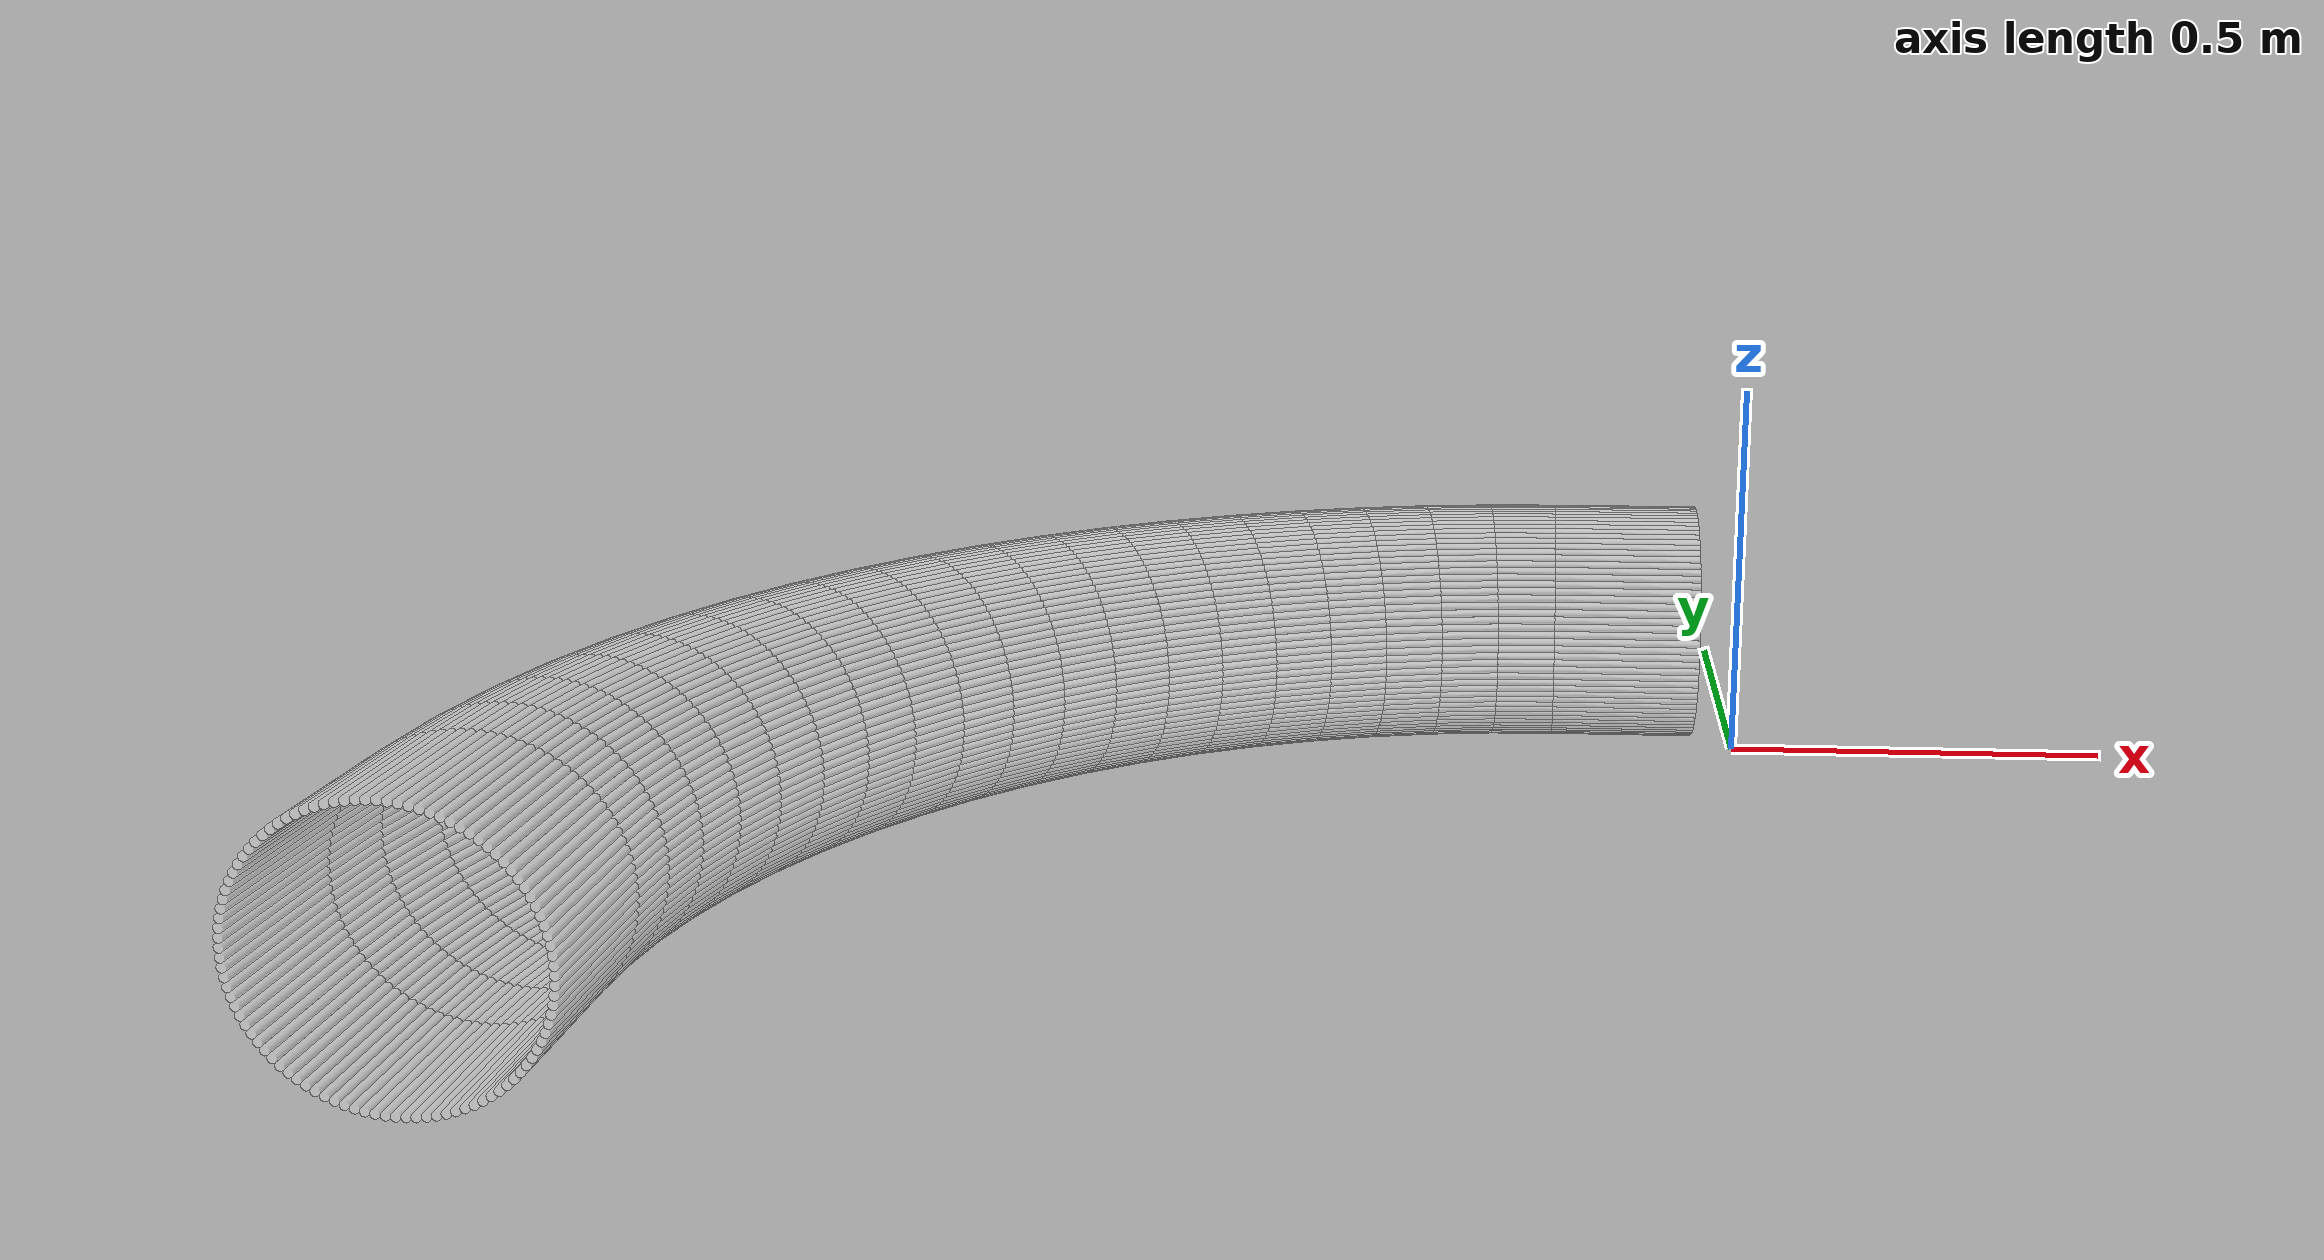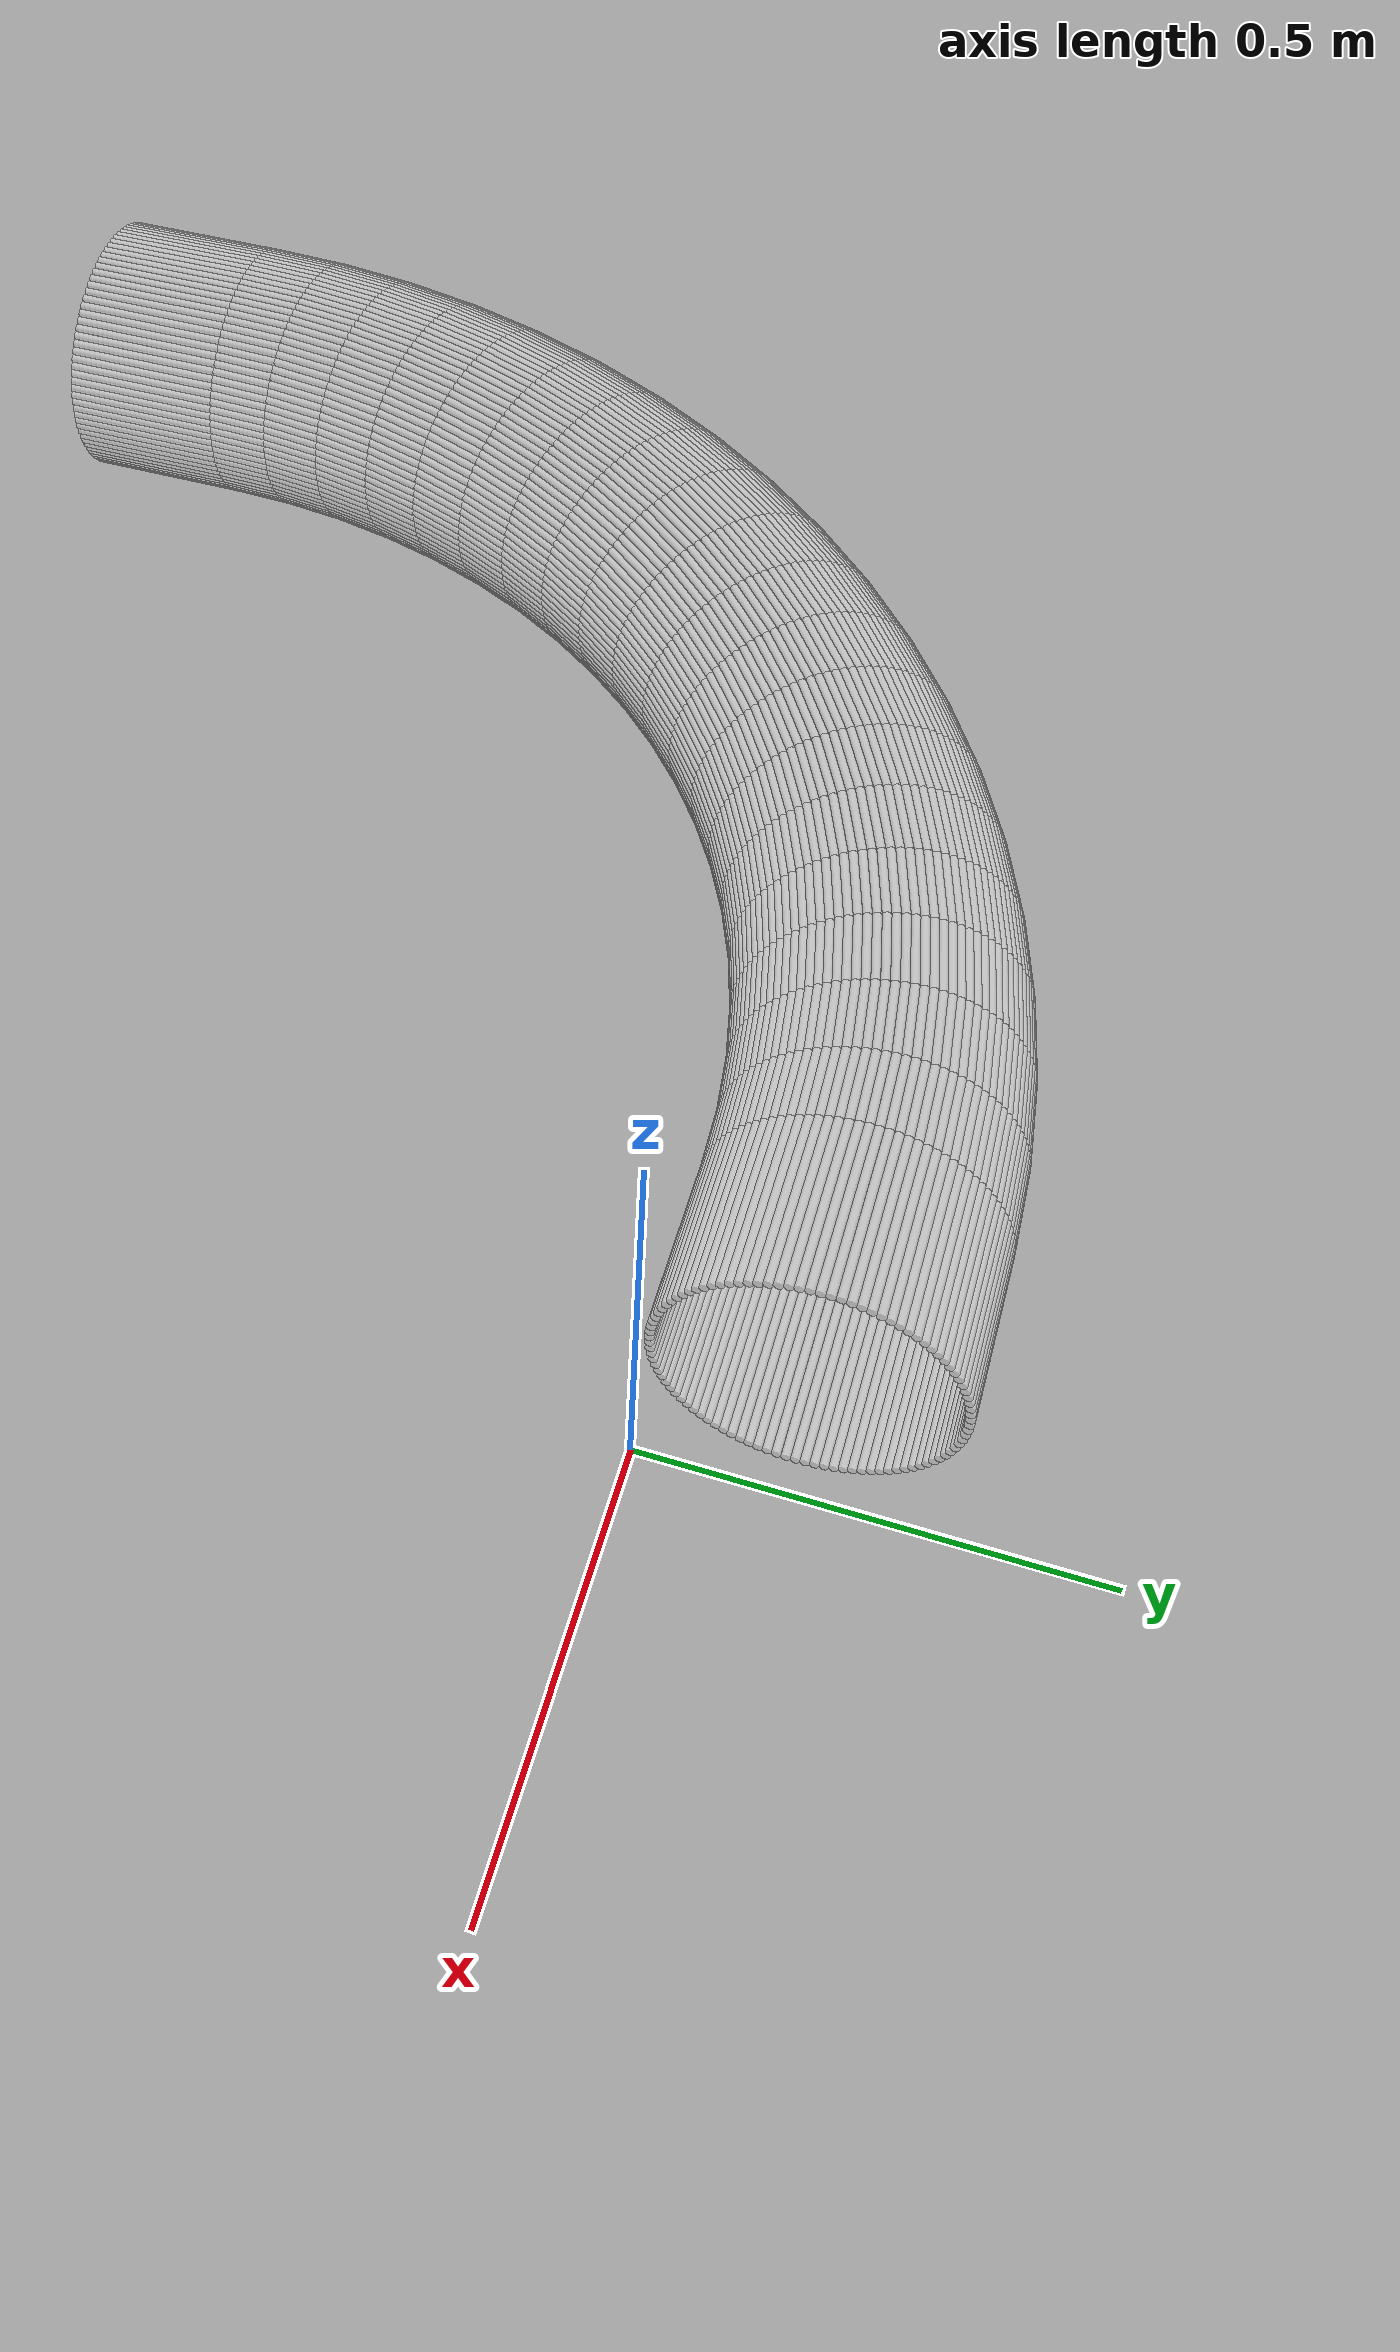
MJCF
<?xml version="1.0" encoding="utf-8"?>
<mujoco>
   <worldbody>
   <body pos="-0.25 -0.94 -0.02" euler="0 0 90">
      <geom euler=" 0 10 0 " fromto="1.26 -0.2 0.16 1.26 0 0.16" rgba="1 1 1 0.35"
            size="0.0050257"
            type="cylinder"/>
      <geom euler=" 0 20 0 " fromto="1.2597 -0.2 0.17005 1.2597 0 0.17005"
            rgba="1 1 1 0.35"
            size="0.0050257"
            type="cylinder"/>
      <geom euler=" 0 30 0 " fromto="1.2587 -0.2 0.18005 1.2587 0 0.18005"
            rgba="1 1 1 0.35"
            size="0.0050257"
            type="cylinder"/>
      <geom euler=" 0 40 0 " fromto="1.2572 -0.2 0.18998 1.2572 0 0.18998"
            rgba="1 1 1 0.35"
            size="0.0050257"
            type="cylinder"/>
      <geom euler=" 0 50 0 " fromto="1.255 -0.2 0.19979 1.255 0 0.19979" rgba="1 1 1 0.35"
            size="0.0050257"
            type="cylinder"/>
      <geom euler=" 0 60 0 " fromto="1.2522 -0.2 0.20944 1.2522 0 0.20944"
            rgba="1 1 1 0.35"
            size="0.0050257"
            type="cylinder"/>
      <geom euler=" 0 70 0 " fromto="1.2488 -0.2 0.2189 1.2488 0 0.2189" rgba="1 1 1 0.35"
            size="0.0050257"
            type="cylinder"/>
      <geom euler=" 0 80 0 " fromto="1.2448 -0.2 0.22812 1.2448 0 0.22812"
            rgba="1 1 1 0.35"
            size="0.0050257"
            type="cylinder"/>
      <geom euler=" 0 90 0 " fromto="1.2402 -0.2 0.23708 1.2402 0 0.23708"
            rgba="1 1 1 0.35"
            size="0.0050257"
            type="cylinder"/>
      <geom euler=" 0 100 0 " fromto="1.2351 -0.2 0.24573 1.2351 0 0.24573"
            rgba="1 1 1 0.35"
            size="0.0050257"
            type="cylinder"/>
      <geom euler=" 0 110 0 " fromto="1.2294 -0.2 0.25405 1.2294 0 0.25405"
            rgba="1 1 1 0.35"
            size="0.0050257"
            type="cylinder"/>
      <geom euler=" 0 120 0 " fromto="1.2233 -0.2 0.26199 1.2233 0 0.26199"
            rgba="1 1 1 0.35"
            size="0.0050257"
            type="cylinder"/>
      <geom euler=" 0 130 0 " fromto="1.2166 -0.2 0.26953 1.2166 0 0.26953"
            rgba="1 1 1 0.35"
            size="0.0050257"
            type="cylinder"/>
      <geom euler=" 0 140 0 " fromto="1.2095 -0.2 0.27663 1.2095 0 0.27663"
            rgba="1 1 1 0.35"
            size="0.0050257"
            type="cylinder"/>
      <geom euler=" 0 150 0 " fromto="1.202 -0.2 0.28328 1.202 0 0.28328" rgba="1 1 1 0.35"
            size="0.0050257"
            type="cylinder"/>
      <geom euler=" 0 160 0 " fromto="1.194 -0.2 0.28944 1.194 0 0.28944" rgba="1 1 1 0.35"
            size="0.0050257"
            type="cylinder"/>
      <geom euler=" 0 170 0 " fromto="1.1857 -0.2 0.29509 1.1857 0 0.29509"
            rgba="1 1 1 0.35"
            size="0.0050257"
            type="cylinder"/>
      <geom euler=" 0 180 0 " fromto="1.1771 -0.2 0.30021 1.1771 0 0.30021"
            rgba="1 1 1 0.35"
            size="0.0050257"
            type="cylinder"/>
      <geom euler=" 0 190 0 " fromto="1.1681 -0.2 0.30477 1.1681 0 0.30477"
            rgba="1 1 1 0.35"
            size="0.0050257"
            type="cylinder"/>
      <geom euler=" 0 200 0 " fromto="1.1589 -0.2 0.30876 1.1589 0 0.30876"
            rgba="1 1 1 0.35"
            size="0.0050257"
            type="cylinder"/>
      <geom euler=" 0 210 0 " fromto="1.1494 -0.2 0.31217 1.1494 0 0.31217"
            rgba="1 1 1 0.35"
            size="0.0050257"
            type="cylinder"/>
      <geom euler=" 0 220 0 " fromto="1.1398 -0.2 0.31497 1.1398 0 0.31497"
            rgba="1 1 1 0.35"
            size="0.0050257"
            type="cylinder"/>
      <geom euler=" 0 230 0 " fromto="1.13 -0.2 0.31717 1.13 0 0.31717" rgba="1 1 1 0.35"
            size="0.0050257"
            type="cylinder"/>
      <geom euler=" 0 240 0 " fromto="1.1201 -0.2 0.31874 1.1201 0 0.31874"
            rgba="1 1 1 0.35"
            size="0.0050257"
            type="cylinder"/>
      <geom euler=" 0 250 0 " fromto="1.11 -0.2 0.31968 1.11 0 0.31968" rgba="1 1 1 0.35"
            size="0.0050257"
            type="cylinder"/>
      <geom euler=" 0 260 0 " fromto="1.1 -0.2 0.32 1.1 0 0.32" rgba="1 1 1 0.35"
            size="0.0050257"
            type="cylinder"/>
      <geom euler=" 0 270 0 " fromto="1.09 -0.2 0.31968 1.09 0 0.31968" rgba="1 1 1 0.35"
            size="0.0050257"
            type="cylinder"/>
      <geom euler=" 0 280 0 " fromto="1.0799 -0.2 0.31874 1.0799 0 0.31874"
            rgba="1 1 1 0.35"
            size="0.0050257"
            type="cylinder"/>
      <geom euler=" 0 290 0 " fromto="1.07 -0.2 0.31717 1.07 0 0.31717" rgba="1 1 1 0.35"
            size="0.0050257"
            type="cylinder"/>
      <geom euler=" 0 300 0 " fromto="1.0602 -0.2 0.31497 1.0602 0 0.31497"
            rgba="1 1 1 0.35"
            size="0.0050257"
            type="cylinder"/>
      <geom euler=" 0 310 0 " fromto="1.0506 -0.2 0.31217 1.0506 0 0.31217"
            rgba="1 1 1 0.35"
            size="0.0050257"
            type="cylinder"/>
      <geom euler=" 0 320 0 " fromto="1.0411 -0.2 0.30876 1.0411 0 0.30876"
            rgba="1 1 1 0.35"
            size="0.0050257"
            type="cylinder"/>
      <geom euler=" 0 330 0 " fromto="1.0319 -0.2 0.30477 1.0319 0 0.30477"
            rgba="1 1 1 0.35"
            size="0.0050257"
            type="cylinder"/>
      <geom euler=" 0 340 0 " fromto="1.0229 -0.2 0.30021 1.0229 0 0.30021"
            rgba="1 1 1 0.35"
            size="0.0050257"
            type="cylinder"/>
      <geom euler=" 0 350 0 " fromto="1.0143 -0.2 0.29509 1.0143 0 0.29509"
            rgba="1 1 1 0.35"
            size="0.0050257"
            type="cylinder"/>
      <geom euler=" 0 360 0 " fromto="1.006 -0.2 0.28944 1.006 0 0.28944" rgba="1 1 1 0.35"
            size="0.0050257"
            type="cylinder"/>
      <geom euler=" 0 370 0 " fromto="0.99801 -0.2 0.28328 0.99801 0 0.28328"
            rgba="1 1 1 0.35"
            size="0.0050257"
            type="cylinder"/>
      <geom euler=" 0 380 0 " fromto="0.99047 -0.2 0.27663 0.99047 0 0.27663"
            rgba="1 1 1 0.35"
            size="0.0050257"
            type="cylinder"/>
      <geom euler=" 0 390 0 " fromto="0.98337 -0.2 0.26953 0.98337 0 0.26953"
            rgba="1 1 1 0.35"
            size="0.0050257"
            type="cylinder"/>
      <geom euler=" 0 400 0 " fromto="0.97672 -0.2 0.26199 0.97672 0 0.26199"
            rgba="1 1 1 0.35"
            size="0.0050257"
            type="cylinder"/>
      <geom euler=" 0 410 0 " fromto="0.97056 -0.2 0.25405 0.97056 0 0.25405"
            rgba="1 1 1 0.35"
            size="0.0050257"
            type="cylinder"/>
      <geom euler=" 0 420 0 " fromto="0.96491 -0.2 0.24573 0.96491 0 0.24573"
            rgba="1 1 1 0.35"
            size="0.0050257"
            type="cylinder"/>
      <geom euler=" 0 430 0 " fromto="0.95979 -0.2 0.23708 0.95979 0 0.23708"
            rgba="1 1 1 0.35"
            size="0.0050257"
            type="cylinder"/>
      <geom euler=" 0 440 0 " fromto="0.95523 -0.2 0.22812 0.95523 0 0.22812"
            rgba="1 1 1 0.35"
            size="0.0050257"
            type="cylinder"/>
      <geom euler=" 0 450 0 " fromto="0.95124 -0.2 0.2189 0.95124 0 0.2189"
            rgba="1 1 1 0.35"
            size="0.0050257"
            type="cylinder"/>
      <geom euler=" 0 460 0 " fromto="0.94783 -0.2 0.20944 0.94783 0 0.20944"
            rgba="1 1 1 0.35"
            size="0.0050257"
            type="cylinder"/>
      <geom euler=" 0 470 0 " fromto="0.94503 -0.2 0.19979 0.94503 0 0.19979"
            rgba="1 1 1 0.35"
            size="0.0050257"
            type="cylinder"/>
      <geom euler=" 0 480 0 " fromto="0.94283 -0.2 0.18998 0.94283 0 0.18998"
            rgba="1 1 1 0.35"
            size="0.0050257"
            type="cylinder"/>
      <geom euler=" 0 490 0 " fromto="0.94126 -0.2 0.18005 0.94126 0 0.18005"
            rgba="1 1 1 0.35"
            size="0.0050257"
            type="cylinder"/>
      <geom euler=" 0 500 0 " fromto="0.94032 -0.2 0.17005 0.94032 0 0.17005"
            rgba="1 1 1 0.35"
            size="0.0050257"
            type="cylinder"/>
      <geom euler=" 0 510 0 " fromto="0.94 -0.2 0.16 0.94 0 0.16" rgba="1 1 1 0.35"
            size="0.0050257"
            type="cylinder"/>
      <geom euler=" 0 520 0 " fromto="0.94032 -0.2 0.14995 0.94032 0 0.14995"
            rgba="1 1 1 0.35"
            size="0.0050257"
            type="cylinder"/>
      <geom euler=" 0 530 0 " fromto="0.94126 -0.2 0.13995 0.94126 0 0.13995"
            rgba="1 1 1 0.35"
            size="0.0050257"
            type="cylinder"/>
      <geom euler=" 0 540 0 " fromto="0.94283 -0.2 0.13002 0.94283 0 0.13002"
            rgba="1 1 1 0.35"
            size="0.0050257"
            type="cylinder"/>
      <geom euler=" 0 550 0 " fromto="0.94503 -0.2 0.12021 0.94503 0 0.12021"
            rgba="1 1 1 0.35"
            size="0.0050257"
            type="cylinder"/>
      <geom euler=" 0 560 0 " fromto="0.94783 -0.2 0.11056 0.94783 0 0.11056"
            rgba="1 1 1 0.35"
            size="0.0050257"
            type="cylinder"/>
      <geom euler=" 0 570 0 " fromto="0.95124 -0.2 0.1011 0.95124 0 0.1011"
            rgba="1 1 1 0.35"
            size="0.0050257"
            type="cylinder"/>
      <geom euler=" 0 580 0 " fromto="0.95523 -0.2 0.091875 0.95523 0 0.091875"
            rgba="1 1 1 0.35"
            size="0.0050257"
            type="cylinder"/>
      <geom euler=" 0 590 0 " fromto="0.95979 -0.2 0.082919 0.95979 0 0.082919"
            rgba="1 1 1 0.35"
            size="0.0050257"
            type="cylinder"/>
      <geom euler=" 0 600 0 " fromto="0.96491 -0.2 0.074268 0.96491 0 0.074268"
            rgba="1 1 1 0.35"
            size="0.0050257"
            type="cylinder"/>
      <geom euler=" 0 610 0 " fromto="0.97056 -0.2 0.065954 0.97056 0 0.065954"
            rgba="1 1 1 0.35"
            size="0.0050257"
            type="cylinder"/>
      <geom euler=" 0 620 0 " fromto="0.97672 -0.2 0.058012 0.97672 0 0.058012"
            rgba="1 1 1 0.35"
            size="0.0050257"
            type="cylinder"/>
      <geom euler=" 0 630 0 " fromto="0.98337 -0.2 0.050472 0.98337 0 0.050472"
            rgba="1 1 1 0.35"
            size="0.0050257"
            type="cylinder"/>
      <geom euler=" 0 640 0 " fromto="0.99047 -0.2 0.043365 0.99047 0 0.043365"
            rgba="1 1 1 0.35"
            size="0.0050257"
            type="cylinder"/>
      <geom euler=" 0 650 0 " fromto="0.99801 -0.2 0.036718 0.99801 0 0.036718"
            rgba="1 1 1 0.35"
            size="0.0050257"
            type="cylinder"/>
      <geom euler=" 0 660 0 " fromto="1.006 -0.2 0.030557 1.006 0 0.030557"
            rgba="1 1 1 0.35"
            size="0.0050257"
            type="cylinder"/>
      <geom euler=" 0 670 0 " fromto="1.0143 -0.2 0.024908 1.0143 0 0.024908"
            rgba="1 1 1 0.35"
            size="0.0050257"
            type="cylinder"/>
      <geom euler=" 0 680 0 " fromto="1.0229 -0.2 0.019791 1.0229 0 0.019791"
            rgba="1 1 1 0.35"
            size="0.0050257"
            type="cylinder"/>
      <geom euler=" 0 690 0 " fromto="1.0319 -0.2 0.015228 1.0319 0 0.015228"
            rgba="1 1 1 0.35"
            size="0.0050257"
            type="cylinder"/>
      <geom euler=" 0 700 0 " fromto="1.0411 -0.2 0.011236 1.0411 0 0.011236"
            rgba="1 1 1 0.35"
            size="0.0050257"
            type="cylinder"/>
      <geom euler=" 0 710 0 " fromto="1.0506 -0.2 0.007831 1.0506 0 0.007831"
            rgba="1 1 1 0.35"
            size="0.0050257"
            type="cylinder"/>
      <geom euler=" 0 720 0 " fromto="1.0602 -0.2 0.0050267 1.0602 0 0.0050267"
            rgba="1 1 1 0.35"
            size="0.0050257"
            type="cylinder"/>
      <geom euler=" 0 730 0 " fromto="1.07 -0.2 0.002834 1.07 0 0.002834" rgba="1 1 1 0.35"
            size="0.0050257"
            type="cylinder"/>
      <geom euler=" 0 740 0 " fromto="1.0799 -0.2 0.0012616 1.0799 0 0.0012616"
            rgba="1 1 1 0.35"
            size="0.0050257"
            type="cylinder"/>
      <geom euler=" 0 750 0 " fromto="1.09 -0.2 0.00031572 1.09 0 0.00031572"
            rgba="1 1 1 0.35"
            size="0.0050257"
            type="cylinder"/>
      <geom euler=" 0 760 0 " fromto="1.1 -0.2 0 1.1 0 0" rgba="1 1 1 0.35"
            size="0.0050257"
            type="cylinder"/>
      <geom euler=" 0 770 0 " fromto="1.11 -0.2 0.00031572 1.11 0 0.00031572"
            rgba="1 1 1 0.35"
            size="0.0050257"
            type="cylinder"/>
      <geom euler=" 0 780 0 " fromto="1.1201 -0.2 0.0012616 1.1201 0 0.0012616"
            rgba="1 1 1 0.35"
            size="0.0050257"
            type="cylinder"/>
      <geom euler=" 0 790 0 " fromto="1.13 -0.2 0.002834 1.13 0 0.002834" rgba="1 1 1 0.35"
            size="0.0050257"
            type="cylinder"/>
      <geom euler=" 0 800 0 " fromto="1.1398 -0.2 0.0050267 1.1398 0 0.0050267"
            rgba="1 1 1 0.35"
            size="0.0050257"
            type="cylinder"/>
      <geom euler=" 0 810 0 " fromto="1.1494 -0.2 0.007831 1.1494 0 0.007831"
            rgba="1 1 1 0.35"
            size="0.0050257"
            type="cylinder"/>
      <geom euler=" 0 820 0 " fromto="1.1589 -0.2 0.011236 1.1589 0 0.011236"
            rgba="1 1 1 0.35"
            size="0.0050257"
            type="cylinder"/>
      <geom euler=" 0 830 0 " fromto="1.1681 -0.2 0.015228 1.1681 0 0.015228"
            rgba="1 1 1 0.35"
            size="0.0050257"
            type="cylinder"/>
      <geom euler=" 0 840 0 " fromto="1.1771 -0.2 0.019791 1.1771 0 0.019791"
            rgba="1 1 1 0.35"
            size="0.0050257"
            type="cylinder"/>
      <geom euler=" 0 850 0 " fromto="1.1857 -0.2 0.024908 1.1857 0 0.024908"
            rgba="1 1 1 0.35"
            size="0.0050257"
            type="cylinder"/>
      <geom euler=" 0 860 0 " fromto="1.194 -0.2 0.030557 1.194 0 0.030557"
            rgba="1 1 1 0.35"
            size="0.0050257"
            type="cylinder"/>
      <geom euler=" 0 870 0 " fromto="1.202 -0.2 0.036718 1.202 0 0.036718"
            rgba="1 1 1 0.35"
            size="0.0050257"
            type="cylinder"/>
      <geom euler=" 0 880 0 " fromto="1.2095 -0.2 0.043365 1.2095 0 0.043365"
            rgba="1 1 1 0.35"
            size="0.0050257"
            type="cylinder"/>
      <geom euler=" 0 890 0 " fromto="1.2166 -0.2 0.050472 1.2166 0 0.050472"
            rgba="1 1 1 0.35"
            size="0.0050257"
            type="cylinder"/>
      <geom euler=" 0 900 0 " fromto="1.2233 -0.2 0.058012 1.2233 0 0.058012"
            rgba="1 1 1 0.35"
            size="0.0050257"
            type="cylinder"/>
      <geom euler=" 0 910 0 " fromto="1.2294 -0.2 0.065954 1.2294 0 0.065954"
            rgba="1 1 1 0.35"
            size="0.0050257"
            type="cylinder"/>
      <geom euler=" 0 920 0 " fromto="1.2351 -0.2 0.074268 1.2351 0 0.074268"
            rgba="1 1 1 0.35"
            size="0.0050257"
            type="cylinder"/>
      <geom euler=" 0 930 0 " fromto="1.2402 -0.2 0.082919 1.2402 0 0.082919"
            rgba="1 1 1 0.35"
            size="0.0050257"
            type="cylinder"/>
      <geom euler=" 0 940 0 " fromto="1.2448 -0.2 0.091875 1.2448 0 0.091875"
            rgba="1 1 1 0.35"
            size="0.0050257"
            type="cylinder"/>
      <geom euler=" 0 950 0 " fromto="1.2488 -0.2 0.1011 1.2488 0 0.1011" rgba="1 1 1 0.35"
            size="0.0050257"
            type="cylinder"/>
      <geom euler=" 0 960 0 " fromto="1.2522 -0.2 0.11056 1.2522 0 0.11056"
            rgba="1 1 1 0.35"
            size="0.0050257"
            type="cylinder"/>
      <geom euler=" 0 970 0 " fromto="1.255 -0.2 0.12021 1.255 0 0.12021" rgba="1 1 1 0.35"
            size="0.0050257"
            type="cylinder"/>
      <geom euler=" 0 980 0 " fromto="1.2572 -0.2 0.13002 1.2572 0 0.13002"
            rgba="1 1 1 0.35"
            size="0.0050257"
            type="cylinder"/>
      <geom euler=" 0 990 0 " fromto="1.2587 -0.2 0.13995 1.2587 0 0.13995"
            rgba="1 1 1 0.35"
            size="0.0050257"
            type="cylinder"/>
      <geom euler=" 0 1000 0 " fromto="1.2597 -0.2 0.14995 1.2597 0 0.14995"
            rgba="1 1 1 0.35"
            size="0.0050257"
            type="cylinder"/>
      <geom euler=" 0 10 0 " fromto="1.26 0 0.16 1.2557 0.10405 0.16" rgba="1 1 1 0.35"
            size="0.0050257"
            type="cylinder"/>
      <geom euler=" 0 20 0 " fromto="1.2597 0 0.17005 1.2554 0.10402 0.17005"
            rgba="1 1 1 0.35"
            size="0.0050257"
            type="cylinder"/>
      <geom euler=" 0 30 0 " fromto="1.2587 0 0.18005 1.2544 0.10395 0.18005"
            rgba="1 1 1 0.35"
            size="0.0050257"
            type="cylinder"/>
      <geom euler=" 0 40 0 " fromto="1.2572 0 0.18998 1.2529 0.10382 0.18998"
            rgba="1 1 1 0.35"
            size="0.0050257"
            type="cylinder"/>
      <geom euler=" 0 50 0 " fromto="1.255 0 0.19979 1.2507 0.10363 0.19979"
            rgba="1 1 1 0.35"
            size="0.0050257"
            type="cylinder"/>
      <geom euler=" 0 60 0 " fromto="1.2522 0 0.20944 1.2479 0.1034 0.20944"
            rgba="1 1 1 0.35"
            size="0.0050257"
            type="cylinder"/>
      <geom euler=" 0 70 0 " fromto="1.2488 0 0.2189 1.2445 0.10312 0.2189"
            rgba="1 1 1 0.35"
            size="0.0050257"
            type="cylinder"/>
      <geom euler=" 0 80 0 " fromto="1.2448 0 0.22812 1.2405 0.10279 0.22812"
            rgba="1 1 1 0.35"
            size="0.0050257"
            type="cylinder"/>
      <geom euler=" 0 90 0 " fromto="1.2402 0 0.23708 1.236 0.10242 0.23708"
            rgba="1 1 1 0.35"
            size="0.0050257"
            type="cylinder"/>
      <geom euler=" 0 100 0 " fromto="1.2351 0 0.24573 1.2309 0.10199 0.24573"
            rgba="1 1 1 0.35"
            size="0.0050257"
            type="cylinder"/>
      <geom euler=" 0 110 0 " fromto="1.2294 0 0.25405 1.2252 0.10153 0.25405"
            rgba="1 1 1 0.35"
            size="0.0050257"
            type="cylinder"/>
      <geom euler=" 0 120 0 " fromto="1.2233 0 0.26199 1.2191 0.10102 0.26199"
            rgba="1 1 1 0.35"
            size="0.0050257"
            type="cylinder"/>
      <geom euler=" 0 130 0 " fromto="1.2166 0 0.26953 1.2125 0.10047 0.26953"
            rgba="1 1 1 0.35"
            size="0.0050257"
            type="cylinder"/>
      <geom euler=" 0 140 0 " fromto="1.2095 0 0.27663 1.2054 0.099882 0.27663"
            rgba="1 1 1 0.35"
            size="0.0050257"
            type="cylinder"/>
      <geom euler=" 0 150 0 " fromto="1.202 0 0.28328 1.1979 0.099259 0.28328"
            rgba="1 1 1 0.35"
            size="0.0050257"
            type="cylinder"/>
      <geom euler=" 0 160 0 " fromto="1.194 0 0.28944 1.19 0.098604 0.28944"
            rgba="1 1 1 0.35"
            size="0.0050257"
            type="cylinder"/>
      <geom euler=" 0 170 0 " fromto="1.1857 0 0.29509 1.1817 0.097917 0.29509"
            rgba="1 1 1 0.35"
            size="0.0050257"
            type="cylinder"/>
      <geom euler=" 0 180 0 " fromto="1.1771 0 0.30021 1.1731 0.097203 0.30021"
            rgba="1 1 1 0.35"
            size="0.0050257"
            type="cylinder"/>
      <geom euler=" 0 190 0 " fromto="1.1681 0 0.30477 1.1641 0.096463 0.30477"
            rgba="1 1 1 0.35"
            size="0.0050257"
            type="cylinder"/>
      <geom euler=" 0 200 0 " fromto="1.1589 0 0.30876 1.1549 0.095701 0.30876"
            rgba="1 1 1 0.35"
            size="0.0050257"
            type="cylinder"/>
      <geom euler=" 0 210 0 " fromto="1.1494 0 0.31217 1.1455 0.09492 0.31217"
            rgba="1 1 1 0.35"
            size="0.0050257"
            type="cylinder"/>
      <geom euler=" 0 220 0 " fromto="1.1398 0 0.31497 1.1359 0.094123 0.31497"
            rgba="1 1 1 0.35"
            size="0.0050257"
            type="cylinder"/>
      <geom euler=" 0 230 0 " fromto="1.13 0 0.31717 1.1261 0.093313 0.31717"
            rgba="1 1 1 0.35"
            size="0.0050257"
            type="cylinder"/>
      <geom euler=" 0 240 0 " fromto="1.1201 0 0.31874 1.1162 0.092493 0.31874"
            rgba="1 1 1 0.35"
            size="0.0050257"
            type="cylinder"/>
      <geom euler=" 0 250 0 " fromto="1.11 0 0.31968 1.1063 0.091667 0.31968"
            rgba="1 1 1 0.35"
            size="0.0050257"
            type="cylinder"/>
      <geom euler=" 0 260 0 " fromto="1.1 0 0.32 1.0962 0.090837 0.32" rgba="1 1 1 0.35"
            size="0.0050257"
            type="cylinder"/>
      <geom euler=" 0 270 0 " fromto="1.09 0 0.31968 1.0862 0.090008 0.31968"
            rgba="1 1 1 0.35"
            size="0.0050257"
            type="cylinder"/>
      <geom euler=" 0 280 0 " fromto="1.0799 0 0.31874 1.0763 0.089181 0.31874"
            rgba="1 1 1 0.35"
            size="0.0050257"
            type="cylinder"/>
      <geom euler=" 0 290 0 " fromto="1.07 0 0.31717 1.0664 0.088361 0.31717"
            rgba="1 1 1 0.35"
            size="0.0050257"
            type="cylinder"/>
      <geom euler=" 0 300 0 " fromto="1.0602 0 0.31497 1.0566 0.087551 0.31497"
            rgba="1 1 1 0.35"
            size="0.0050257"
            type="cylinder"/>
      <geom euler=" 0 310 0 " fromto="1.0506 0 0.31217 1.047 0.086754 0.31217"
            rgba="1 1 1 0.35"
            size="0.0050257"
            type="cylinder"/>
      <geom euler=" 0 320 0 " fromto="1.0411 0 0.30876 1.0375 0.085973 0.30876"
            rgba="1 1 1 0.35"
            size="0.0050257"
            type="cylinder"/>
      <geom euler=" 0 330 0 " fromto="1.0319 0 0.30477 1.0284 0.085212 0.30477"
            rgba="1 1 1 0.35"
            size="0.0050257"
            type="cylinder"/>
      <geom euler=" 0 340 0 " fromto="1.0229 0 0.30021 1.0194 0.084472 0.30021"
            rgba="1 1 1 0.35"
            size="0.0050257"
            type="cylinder"/>
      <geom euler=" 0 350 0 " fromto="1.0143 0 0.29509 1.0108 0.083758 0.29509"
            rgba="1 1 1 0.35"
            size="0.0050257"
            type="cylinder"/>
      <geom euler=" 0 360 0 " fromto="1.006 0 0.28944 1.0025 0.083071 0.28944"
            rgba="1 1 1 0.35"
            size="0.0050257"
            type="cylinder"/>
      <geom euler=" 0 370 0 " fromto="0.99801 0 0.28328 0.9946 0.082415 0.28328"
            rgba="1 1 1 0.35"
            size="0.0050257"
            type="cylinder"/>
      <geom euler=" 0 380 0 " fromto="0.99047 0 0.27663 0.98709 0.081793 0.27663"
            rgba="1 1 1 0.35"
            size="0.0050257"
            type="cylinder"/>
      <geom euler=" 0 390 0 " fromto="0.98337 0 0.26953 0.98001 0.081206 0.26953"
            rgba="1 1 1 0.35"
            size="0.0050257"
            type="cylinder"/>
      <geom euler=" 0 400 0 " fromto="0.97672 0 0.26199 0.97338 0.080657 0.26199"
            rgba="1 1 1 0.35"
            size="0.0050257"
            type="cylinder"/>
      <geom euler=" 0 410 0 " fromto="0.97056 0 0.25405 0.96724 0.080148 0.25405"
            rgba="1 1 1 0.35"
            size="0.0050257"
            type="cylinder"/>
      <geom euler=" 0 420 0 " fromto="0.96491 0 0.24573 0.96161 0.079681 0.24573"
            rgba="1 1 1 0.35"
            size="0.0050257"
            type="cylinder"/>
      <geom euler=" 0 430 0 " fromto="0.95979 0 0.23708 0.95651 0.079259 0.23708"
            rgba="1 1 1 0.35"
            size="0.0050257"
            type="cylinder"/>
      <geom euler=" 0 440 0 " fromto="0.95523 0 0.22812 0.95197 0.078882 0.22812"
            rgba="1 1 1 0.35"
            size="0.0050257"
            type="cylinder"/>
      <geom euler=" 0 450 0 " fromto="0.95124 0 0.2189 0.94799 0.078552 0.2189"
            rgba="1 1 1 0.35"
            size="0.0050257"
            type="cylinder"/>
      <geom euler=" 0 460 0 " fromto="0.94783 0 0.20944 0.94459 0.078271 0.20944"
            rgba="1 1 1 0.35"
            size="0.0050257"
            type="cylinder"/>
      <geom euler=" 0 470 0 " fromto="0.94503 0 0.19979 0.9418 0.07804 0.19979"
            rgba="1 1 1 0.35"
            size="0.0050257"
            type="cylinder"/>
      <geom euler=" 0 480 0 " fromto="0.94283 0 0.18998 0.93961 0.077859 0.18998"
            rgba="1 1 1 0.35"
            size="0.0050257"
            type="cylinder"/>
      <geom euler=" 0 490 0 " fromto="0.94126 0 0.18005 0.93805 0.077729 0.18005"
            rgba="1 1 1 0.35"
            size="0.0050257"
            type="cylinder"/>
      <geom euler=" 0 500 0 " fromto="0.94032 0 0.17005 0.9371 0.077651 0.17005"
            rgba="1 1 1 0.35"
            size="0.0050257"
            type="cylinder"/>
      <geom euler=" 0 510 0 " fromto="0.94 0 0.16 0.93679 0.077625 0.16" rgba="1 1 1 0.35"
            size="0.0050257"
            type="cylinder"/>
      <geom euler=" 0 520 0 " fromto="0.94032 0 0.14995 0.9371 0.077651 0.14995"
            rgba="1 1 1 0.35"
            size="0.0050257"
            type="cylinder"/>
      <geom euler=" 0 530 0 " fromto="0.94126 0 0.13995 0.93805 0.077729 0.13995"
            rgba="1 1 1 0.35"
            size="0.0050257"
            type="cylinder"/>
      <geom euler=" 0 540 0 " fromto="0.94283 0 0.13002 0.93961 0.077859 0.13002"
            rgba="1 1 1 0.35"
            size="0.0050257"
            type="cylinder"/>
      <geom euler=" 0 550 0 " fromto="0.94503 0 0.12021 0.9418 0.07804 0.12021"
            rgba="1 1 1 0.35"
            size="0.0050257"
            type="cylinder"/>
      <geom euler=" 0 560 0 " fromto="0.94783 0 0.11056 0.94459 0.078271 0.11056"
            rgba="1 1 1 0.35"
            size="0.0050257"
            type="cylinder"/>
      <geom euler=" 0 570 0 " fromto="0.95124 0 0.1011 0.94799 0.078552 0.1011"
            rgba="1 1 1 0.35"
            size="0.0050257"
            type="cylinder"/>
      <geom euler=" 0 580 0 " fromto="0.95523 0 0.091875 0.95197 0.078882 0.091875"
            rgba="1 1 1 0.35"
            size="0.0050257"
            type="cylinder"/>
      <geom euler=" 0 590 0 " fromto="0.95979 0 0.082919 0.95651 0.079259 0.082919"
            rgba="1 1 1 0.35"
            size="0.0050257"
            type="cylinder"/>
      <geom euler=" 0 600 0 " fromto="0.96491 0 0.074268 0.96161 0.079681 0.074268"
            rgba="1 1 1 0.35"
            size="0.0050257"
            type="cylinder"/>
      <geom euler=" 0 610 0 " fromto="0.97056 0 0.065954 0.96724 0.080148 0.065954"
            rgba="1 1 1 0.35"
            size="0.0050257"
            type="cylinder"/>
      <geom euler=" 0 620 0 " fromto="0.97672 0 0.058012 0.97338 0.080657 0.058012"
            rgba="1 1 1 0.35"
            size="0.0050257"
            type="cylinder"/>
      <geom euler=" 0 630 0 " fromto="0.98337 0 0.050472 0.98001 0.081206 0.050472"
            rgba="1 1 1 0.35"
            size="0.0050257"
            type="cylinder"/>
      <geom euler=" 0 640 0 " fromto="0.99047 0 0.043365 0.98709 0.081793 0.043365"
            rgba="1 1 1 0.35"
            size="0.0050257"
            type="cylinder"/>
      <geom euler=" 0 650 0 " fromto="0.99801 0 0.036718 0.9946 0.082415 0.036718"
            rgba="1 1 1 0.35"
            size="0.0050257"
            type="cylinder"/>
      <geom euler=" 0 660 0 " fromto="1.006 0 0.030557 1.0025 0.083071 0.030557"
            rgba="1 1 1 0.35"
            size="0.0050257"
            type="cylinder"/>
      <geom euler=" 0 670 0 " fromto="1.0143 0 0.024908 1.0108 0.083758 0.024908"
            rgba="1 1 1 0.35"
            size="0.0050257"
            type="cylinder"/>
      <geom euler=" 0 680 0 " fromto="1.0229 0 0.019791 1.0194 0.084472 0.019791"
            rgba="1 1 1 0.35"
            size="0.0050257"
            type="cylinder"/>
      <geom euler=" 0 690 0 " fromto="1.0319 0 0.015228 1.0284 0.085212 0.015228"
            rgba="1 1 1 0.35"
            size="0.0050257"
            type="cylinder"/>
      <geom euler=" 0 700 0 " fromto="1.0411 0 0.011236 1.0375 0.085973 0.011236"
            rgba="1 1 1 0.35"
            size="0.0050257"
            type="cylinder"/>
      <geom euler=" 0 710 0 " fromto="1.0506 0 0.007831 1.047 0.086754 0.007831"
            rgba="1 1 1 0.35"
            size="0.0050257"
            type="cylinder"/>
      <geom euler=" 0 720 0 " fromto="1.0602 0 0.0050267 1.0566 0.087551 0.0050267"
            rgba="1 1 1 0.35"
            size="0.0050257"
            type="cylinder"/>
      <geom euler=" 0 730 0 " fromto="1.07 0 0.002834 1.0664 0.088361 0.002834"
            rgba="1 1 1 0.35"
            size="0.0050257"
            type="cylinder"/>
      <geom euler=" 0 740 0 " fromto="1.0799 0 0.0012616 1.0763 0.089181 0.0012616"
            rgba="1 1 1 0.35"
            size="0.0050257"
            type="cylinder"/>
      <geom euler=" 0 750 0 " fromto="1.09 0 0.00031572 1.0862 0.090008 0.00031572"
            rgba="1 1 1 0.35"
            size="0.0050257"
            type="cylinder"/>
      <geom euler=" 0 760 0 " fromto="1.1 0 0 1.0962 0.090837 0" rgba="1 1 1 0.35"
            size="0.0050257"
            type="cylinder"/>
      <geom euler=" 0 770 0 " fromto="1.11 0 0.00031572 1.1063 0.091667 0.00031572"
            rgba="1 1 1 0.35"
            size="0.0050257"
            type="cylinder"/>
      <geom euler=" 0 780 0 " fromto="1.1201 0 0.0012616 1.1162 0.092493 0.0012616"
            rgba="1 1 1 0.35"
            size="0.0050257"
            type="cylinder"/>
      <geom euler=" 0 790 0 " fromto="1.13 0 0.002834 1.1261 0.093313 0.002834"
            rgba="1 1 1 0.35"
            size="0.0050257"
            type="cylinder"/>
      <geom euler=" 0 800 0 " fromto="1.1398 0 0.0050267 1.1359 0.094123 0.0050267"
            rgba="1 1 1 0.35"
            size="0.0050257"
            type="cylinder"/>
      <geom euler=" 0 810 0 " fromto="1.1494 0 0.007831 1.1455 0.09492 0.007831"
            rgba="1 1 1 0.35"
            size="0.0050257"
            type="cylinder"/>
      <geom euler=" 0 820 0 " fromto="1.1589 0 0.011236 1.1549 0.095701 0.011236"
            rgba="1 1 1 0.35"
            size="0.0050257"
            type="cylinder"/>
      <geom euler=" 0 830 0 " fromto="1.1681 0 0.015228 1.1641 0.096463 0.015228"
            rgba="1 1 1 0.35"
            size="0.0050257"
            type="cylinder"/>
      <geom euler=" 0 840 0 " fromto="1.1771 0 0.019791 1.1731 0.097203 0.019791"
            rgba="1 1 1 0.35"
            size="0.0050257"
            type="cylinder"/>
      <geom euler=" 0 850 0 " fromto="1.1857 0 0.024908 1.1817 0.097917 0.024908"
            rgba="1 1 1 0.35"
            size="0.0050257"
            type="cylinder"/>
      <geom euler=" 0 860 0 " fromto="1.194 0 0.030557 1.19 0.098604 0.030557"
            rgba="1 1 1 0.35"
            size="0.0050257"
            type="cylinder"/>
      <geom euler=" 0 870 0 " fromto="1.202 0 0.036718 1.1979 0.099259 0.036718"
            rgba="1 1 1 0.35"
            size="0.0050257"
            type="cylinder"/>
      <geom euler=" 0 880 0 " fromto="1.2095 0 0.043365 1.2054 0.099882 0.043365"
            rgba="1 1 1 0.35"
            size="0.0050257"
            type="cylinder"/>
      <geom euler=" 0 890 0 " fromto="1.2166 0 0.050472 1.2125 0.10047 0.050472"
            rgba="1 1 1 0.35"
            size="0.0050257"
            type="cylinder"/>
      <geom euler=" 0 900 0 " fromto="1.2233 0 0.058012 1.2191 0.10102 0.058012"
            rgba="1 1 1 0.35"
            size="0.0050257"
            type="cylinder"/>
      <geom euler=" 0 910 0 " fromto="1.2294 0 0.065954 1.2252 0.10153 0.065954"
            rgba="1 1 1 0.35"
            size="0.0050257"
            type="cylinder"/>
      <geom euler=" 0 920 0 " fromto="1.2351 0 0.074268 1.2309 0.10199 0.074268"
            rgba="1 1 1 0.35"
            size="0.0050257"
            type="cylinder"/>
      <geom euler=" 0 930 0 " fromto="1.2402 0 0.082919 1.236 0.10242 0.082919"
            rgba="1 1 1 0.35"
            size="0.0050257"
            type="cylinder"/>
      <geom euler=" 0 940 0 " fromto="1.2448 0 0.091875 1.2405 0.10279 0.091875"
            rgba="1 1 1 0.35"
            size="0.0050257"
            type="cylinder"/>
      <geom euler=" 0 950 0 " fromto="1.2488 0 0.1011 1.2445 0.10312 0.1011"
            rgba="1 1 1 0.35"
            size="0.0050257"
            type="cylinder"/>
      <geom euler=" 0 960 0 " fromto="1.2522 0 0.11056 1.2479 0.1034 0.11056"
            rgba="1 1 1 0.35"
            size="0.0050257"
            type="cylinder"/>
      <geom euler=" 0 970 0 " fromto="1.255 0 0.12021 1.2507 0.10363 0.12021"
            rgba="1 1 1 0.35"
            size="0.0050257"
            type="cylinder"/>
      <geom euler=" 0 980 0 " fromto="1.2572 0 0.13002 1.2529 0.10382 0.13002"
            rgba="1 1 1 0.35"
            size="0.0050257"
            type="cylinder"/>
      <geom euler=" 0 990 0 " fromto="1.2587 0 0.13995 1.2544 0.10395 0.13995"
            rgba="1 1 1 0.35"
            size="0.0050257"
            type="cylinder"/>
      <geom euler=" 0 1000 0 " fromto="1.2597 0 0.14995 1.2554 0.10402 0.14995"
            rgba="1 1 1 0.35"
            size="0.0050257"
            type="cylinder"/>
      <geom euler=" 0 10 0 " fromto="1.2557 0.10405 0.16 1.2428 0.20739 0.16"
            rgba="1 1 1 0.35"
            size="0.0050257"
            type="cylinder"/>
      <geom euler=" 0 20 0 " fromto="1.2554 0.10402 0.17005 1.2425 0.20734 0.17005"
            rgba="1 1 1 0.35"
            size="0.0050257"
            type="cylinder"/>
      <geom euler=" 0 30 0 " fromto="1.2544 0.10395 0.18005 1.2416 0.20718 0.18005"
            rgba="1 1 1 0.35"
            size="0.0050257"
            type="cylinder"/>
      <geom euler=" 0 40 0 " fromto="1.2529 0.10382 0.18998 1.24 0.20692 0.18998"
            rgba="1 1 1 0.35"
            size="0.0050257"
            type="cylinder"/>
      <geom euler=" 0 50 0 " fromto="1.2507 0.10363 0.19979 1.2379 0.20656 0.19979"
            rgba="1 1 1 0.35"
            size="0.0050257"
            type="cylinder"/>
      <geom euler=" 0 60 0 " fromto="1.2479 0.1034 0.20944 1.2351 0.2061 0.20944"
            rgba="1 1 1 0.35"
            size="0.0050257"
            type="cylinder"/>
      <geom euler=" 0 70 0 " fromto="1.2445 0.10312 0.2189 1.2317 0.20554 0.2189"
            rgba="1 1 1 0.35"
            size="0.0050257"
            type="cylinder"/>
      <geom euler=" 0 80 0 " fromto="1.2405 0.10279 0.22812 1.2278 0.20488 0.22812"
            rgba="1 1 1 0.35"
            size="0.0050257"
            type="cylinder"/>
      <geom euler=" 0 90 0 " fromto="1.236 0.10242 0.23708 1.2233 0.20413 0.23708"
            rgba="1 1 1 0.35"
            size="0.0050257"
            type="cylinder"/>
      <geom euler=" 0 100 0 " fromto="1.2309 0.10199 0.24573 1.2182 0.20329 0.24573"
            rgba="1 1 1 0.35"
            size="0.0050257"
            type="cylinder"/>
      <geom euler=" 0 110 0 " fromto="1.2252 0.10153 0.25405 1.2127 0.20236 0.25405"
            rgba="1 1 1 0.35"
            size="0.0050257"
            type="cylinder"/>
      <geom euler=" 0 120 0 " fromto="1.2191 0.10102 0.26199 1.2066 0.20135 0.26199"
            rgba="1 1 1 0.35"
            size="0.0050257"
            type="cylinder"/>
      <geom euler=" 0 130 0 " fromto="1.2125 0.10047 0.26953 1.2 0.20025 0.26953"
            rgba="1 1 1 0.35"
            size="0.0050257"
            type="cylinder"/>
      <geom euler=" 0 140 0 " fromto="1.2054 0.099882 0.27663 1.193 0.19908 0.27663"
            rgba="1 1 1 0.35"
            size="0.0050257"
            type="cylinder"/>
      <geom euler=" 0 150 0 " fromto="1.1979 0.099259 0.28328 1.1856 0.19784 0.28328"
            rgba="1 1 1 0.35"
            size="0.0050257"
            type="cylinder"/>
      <geom euler=" 0 160 0 " fromto="1.19 0.098604 0.28944 1.1778 0.19653 0.28944"
            rgba="1 1 1 0.35"
            size="0.0050257"
            type="cylinder"/>
      <geom euler=" 0 170 0 " fromto="1.1817 0.097917 0.29509 1.1696 0.19517 0.29509"
            rgba="1 1 1 0.35"
            size="0.0050257"
            type="cylinder"/>
      <geom euler=" 0 180 0 " fromto="1.1731 0.097203 0.30021 1.161 0.19374 0.30021"
            rgba="1 1 1 0.35"
            size="0.0050257"
            type="cylinder"/>
      <geom euler=" 0 190 0 " fromto="1.1641 0.096463 0.30477 1.1522 0.19227 0.30477"
            rgba="1 1 1 0.35"
            size="0.0050257"
            type="cylinder"/>
      <geom euler=" 0 200 0 " fromto="1.1549 0.095701 0.30876 1.1431 0.19075 0.30876"
            rgba="1 1 1 0.35"
            size="0.0050257"
            type="cylinder"/>
      <geom euler=" 0 210 0 " fromto="1.1455 0.09492 0.31217 1.1338 0.18919 0.31217"
            rgba="1 1 1 0.35"
            size="0.0050257"
            type="cylinder"/>
      <geom euler=" 0 220 0 " fromto="1.1359 0.094123 0.31497 1.1242 0.1876 0.31497"
            rgba="1 1 1 0.35"
            size="0.0050257"
            type="cylinder"/>
      <geom euler=" 0 230 0 " fromto="1.1261 0.093313 0.31717 1.1146 0.18599 0.31717"
            rgba="1 1 1 0.35"
            size="0.0050257"
            type="cylinder"/>
      <geom euler=" 0 240 0 " fromto="1.1162 0.092493 0.31874 1.1048 0.18435 0.31874"
            rgba="1 1 1 0.35"
            size="0.0050257"
            type="cylinder"/>
      <geom euler=" 0 250 0 " fromto="1.1063 0.091667 0.31968 1.0949 0.18271 0.31968"
            rgba="1 1 1 0.35"
            size="0.0050257"
            type="cylinder"/>
      <geom euler=" 0 260 0 " fromto="1.0962 0.090837 0.32 1.085 0.18105 0.32"
            rgba="1 1 1 0.35"
            size="0.0050257"
            type="cylinder"/>
      <geom euler=" 0 270 0 " fromto="1.0862 0.090008 0.31968 1.0751 0.1794 0.31968"
            rgba="1 1 1 0.35"
            size="0.0050257"
            type="cylinder"/>
      <geom euler=" 0 280 0 " fromto="1.0763 0.089181 0.31874 1.0652 0.17775 0.31874"
            rgba="1 1 1 0.35"
            size="0.0050257"
            type="cylinder"/>
      <geom euler=" 0 290 0 " fromto="1.0664 0.088361 0.31717 1.0554 0.17612 0.31717"
            rgba="1 1 1 0.35"
            size="0.0050257"
            type="cylinder"/>
      <geom euler=" 0 300 0 " fromto="1.0566 0.087551 0.31497 1.0457 0.1745 0.31497"
            rgba="1 1 1 0.35"
            size="0.0050257"
            type="cylinder"/>
      <geom euler=" 0 310 0 " fromto="1.047 0.086754 0.31217 1.0362 0.17292 0.31217"
            rgba="1 1 1 0.35"
            size="0.0050257"
            type="cylinder"/>
      <geom euler=" 0 320 0 " fromto="1.0375 0.085973 0.30876 1.0269 0.17136 0.30876"
            rgba="1 1 1 0.35"
            size="0.0050257"
            type="cylinder"/>
      <geom euler=" 0 330 0 " fromto="1.0284 0.085212 0.30477 1.0178 0.16984 0.30477"
            rgba="1 1 1 0.35"
            size="0.0050257"
            type="cylinder"/>
      <geom euler=" 0 340 0 " fromto="1.0194 0.084472 0.30021 1.009 0.16837 0.30021"
            rgba="1 1 1 0.35"
            size="0.0050257"
            type="cylinder"/>
      <geom euler=" 0 350 0 " fromto="1.0108 0.083758 0.29509 1.0004 0.16694 0.29509"
            rgba="1 1 1 0.35"
            size="0.0050257"
            type="cylinder"/>
      <geom euler=" 0 360 0 " fromto="1.0025 0.083071 0.28944 0.99223 0.16557 0.28944"
            rgba="1 1 1 0.35"
            size="0.0050257"
            type="cylinder"/>
      <geom euler=" 0 370 0 " fromto="0.9946 0.082415 0.28328 0.9844 0.16427 0.28328"
            rgba="1 1 1 0.35"
            size="0.0050257"
            type="cylinder"/>
      <geom euler=" 0 380 0 " fromto="0.98709 0.081793 0.27663 0.97696 0.16303 0.27663"
            rgba="1 1 1 0.35"
            size="0.0050257"
            type="cylinder"/>
      <geom euler=" 0 390 0 " fromto="0.98001 0.081206 0.26953 0.96995 0.16186 0.26953"
            rgba="1 1 1 0.35"
            size="0.0050257"
            type="cylinder"/>
      <geom euler=" 0 400 0 " fromto="0.97338 0.080657 0.26199 0.9634 0.16076 0.26199"
            rgba="1 1 1 0.35"
            size="0.0050257"
            type="cylinder"/>
      <geom euler=" 0 410 0 " fromto="0.96724 0.080148 0.25405 0.95732 0.15975 0.25405"
            rgba="1 1 1 0.35"
            size="0.0050257"
            type="cylinder"/>
      <geom euler=" 0 420 0 " fromto="0.96161 0.079681 0.24573 0.95175 0.15882 0.24573"
            rgba="1 1 1 0.35"
            size="0.0050257"
            type="cylinder"/>
      <geom euler=" 0 430 0 " fromto="0.95651 0.079259 0.23708 0.9467 0.15798 0.23708"
            rgba="1 1 1 0.35"
            size="0.0050257"
            type="cylinder"/>
      <geom euler=" 0 440 0 " fromto="0.95197 0.078882 0.22812 0.9422 0.15723 0.22812"
            rgba="1 1 1 0.35"
            size="0.0050257"
            type="cylinder"/>
      <geom euler=" 0 450 0 " fromto="0.94799 0.078552 0.2189 0.93826 0.15657 0.2189"
            rgba="1 1 1 0.35"
            size="0.0050257"
            type="cylinder"/>
      <geom euler=" 0 460 0 " fromto="0.94459 0.078271 0.20944 0.9349 0.15601 0.20944"
            rgba="1 1 1 0.35"
            size="0.0050257"
            type="cylinder"/>
      <geom euler=" 0 470 0 " fromto="0.9418 0.07804 0.19979 0.93214 0.15555 0.19979"
            rgba="1 1 1 0.35"
            size="0.0050257"
            type="cylinder"/>
      <geom euler=" 0 480 0 " fromto="0.93961 0.077859 0.18998 0.92998 0.15519 0.18998"
            rgba="1 1 1 0.35"
            size="0.0050257"
            type="cylinder"/>
      <geom euler=" 0 490 0 " fromto="0.93805 0.077729 0.18005 0.92842 0.15493 0.18005"
            rgba="1 1 1 0.35"
            size="0.0050257"
            type="cylinder"/>
      <geom euler=" 0 500 0 " fromto="0.9371 0.077651 0.17005 0.92749 0.15477 0.17005"
            rgba="1 1 1 0.35"
            size="0.0050257"
            type="cylinder"/>
      <geom euler=" 0 510 0 " fromto="0.93679 0.077625 0.16 0.92718 0.15472 0.16"
            rgba="1 1 1 0.35"
            size="0.0050257"
            type="cylinder"/>
      <geom euler=" 0 520 0 " fromto="0.9371 0.077651 0.14995 0.92749 0.15477 0.14995"
            rgba="1 1 1 0.35"
            size="0.0050257"
            type="cylinder"/>
      <geom euler=" 0 530 0 " fromto="0.93805 0.077729 0.13995 0.92842 0.15493 0.13995"
            rgba="1 1 1 0.35"
            size="0.0050257"
            type="cylinder"/>
      <geom euler=" 0 540 0 " fromto="0.93961 0.077859 0.13002 0.92998 0.15519 0.13002"
            rgba="1 1 1 0.35"
            size="0.0050257"
            type="cylinder"/>
      <geom euler=" 0 550 0 " fromto="0.9418 0.07804 0.12021 0.93214 0.15555 0.12021"
            rgba="1 1 1 0.35"
            size="0.0050257"
            type="cylinder"/>
      <geom euler=" 0 560 0 " fromto="0.94459 0.078271 0.11056 0.9349 0.15601 0.11056"
            rgba="1 1 1 0.35"
            size="0.0050257"
            type="cylinder"/>
      <geom euler=" 0 570 0 " fromto="0.94799 0.078552 0.1011 0.93826 0.15657 0.1011"
            rgba="1 1 1 0.35"
            size="0.0050257"
            type="cylinder"/>
      <geom euler=" 0 580 0 " fromto="0.95197 0.078882 0.091875 0.9422 0.15723 0.091875"
            rgba="1 1 1 0.35"
            size="0.0050257"
            type="cylinder"/>
      <geom euler=" 0 590 0 " fromto="0.95651 0.079259 0.082919 0.9467 0.15798 0.082919"
            rgba="1 1 1 0.35"
            size="0.0050257"
            type="cylinder"/>
      <geom euler=" 0 600 0 " fromto="0.96161 0.079681 0.074268 0.95175 0.15882 0.074268"
            rgba="1 1 1 0.35"
            size="0.0050257"
            type="cylinder"/>
      <geom euler=" 0 610 0 " fromto="0.96724 0.080148 0.065954 0.95732 0.15975 0.065954"
            rgba="1 1 1 0.35"
            size="0.0050257"
            type="cylinder"/>
      <geom euler=" 0 620 0 " fromto="0.97338 0.080657 0.058012 0.9634 0.16076 0.058012"
            rgba="1 1 1 0.35"
            size="0.0050257"
            type="cylinder"/>
      <geom euler=" 0 630 0 " fromto="0.98001 0.081206 0.050472 0.96995 0.16186 0.050472"
            rgba="1 1 1 0.35"
            size="0.0050257"
            type="cylinder"/>
      <geom euler=" 0 640 0 " fromto="0.98709 0.081793 0.043365 0.97696 0.16303 0.043365"
            rgba="1 1 1 0.35"
            size="0.0050257"
            type="cylinder"/>
      <geom euler=" 0 650 0 " fromto="0.9946 0.082415 0.036718 0.9844 0.16427 0.036718"
            rgba="1 1 1 0.35"
            size="0.0050257"
            type="cylinder"/>
      <geom euler=" 0 660 0 " fromto="1.0025 0.083071 0.030557 0.99223 0.16557 0.030557"
            rgba="1 1 1 0.35"
            size="0.0050257"
            type="cylinder"/>
      <geom euler=" 0 670 0 " fromto="1.0108 0.083758 0.024908 1.0004 0.16694 0.024908"
            rgba="1 1 1 0.35"
            size="0.0050257"
            type="cylinder"/>
      <geom euler=" 0 680 0 " fromto="1.0194 0.084472 0.019791 1.009 0.16837 0.019791"
            rgba="1 1 1 0.35"
            size="0.0050257"
            type="cylinder"/>
      <geom euler=" 0 690 0 " fromto="1.0284 0.085212 0.015228 1.0178 0.16984 0.015228"
            rgba="1 1 1 0.35"
            size="0.0050257"
            type="cylinder"/>
      <geom euler=" 0 700 0 " fromto="1.0375 0.085973 0.011236 1.0269 0.17136 0.011236"
            rgba="1 1 1 0.35"
            size="0.0050257"
            type="cylinder"/>
      <geom euler=" 0 710 0 " fromto="1.047 0.086754 0.007831 1.0362 0.17292 0.007831"
            rgba="1 1 1 0.35"
            size="0.0050257"
            type="cylinder"/>
      <geom euler=" 0 720 0 " fromto="1.0566 0.087551 0.0050267 1.0457 0.1745 0.0050267"
            rgba="1 1 1 0.35"
            size="0.0050257"
            type="cylinder"/>
      <geom euler=" 0 730 0 " fromto="1.0664 0.088361 0.002834 1.0554 0.17612 0.002834"
            rgba="1 1 1 0.35"
            size="0.0050257"
            type="cylinder"/>
      <geom euler=" 0 740 0 " fromto="1.0763 0.089181 0.0012616 1.0652 0.17775 0.0012616"
            rgba="1 1 1 0.35"
            size="0.0050257"
            type="cylinder"/>
      <geom euler=" 0 750 0 " fromto="1.0862 0.090008 0.00031572 1.0751 0.1794 0.00031572"
            rgba="1 1 1 0.35"
            size="0.0050257"
            type="cylinder"/>
      <geom euler=" 0 760 0 " fromto="1.0962 0.090837 0 1.085 0.18105 0" rgba="1 1 1 0.35"
            size="0.0050257"
            type="cylinder"/>
      <geom euler=" 0 770 0 " fromto="1.1063 0.091667 0.00031572 1.0949 0.18271 0.00031572"
            rgba="1 1 1 0.35"
            size="0.0050257"
            type="cylinder"/>
      <geom euler=" 0 780 0 " fromto="1.1162 0.092493 0.0012616 1.1048 0.18435 0.0012616"
            rgba="1 1 1 0.35"
            size="0.0050257"
            type="cylinder"/>
      <geom euler=" 0 790 0 " fromto="1.1261 0.093313 0.002834 1.1146 0.18599 0.002834"
            rgba="1 1 1 0.35"
            size="0.0050257"
            type="cylinder"/>
      <geom euler=" 0 800 0 " fromto="1.1359 0.094123 0.0050267 1.1242 0.1876 0.0050267"
            rgba="1 1 1 0.35"
            size="0.0050257"
            type="cylinder"/>
      <geom euler=" 0 810 0 " fromto="1.1455 0.09492 0.007831 1.1338 0.18919 0.007831"
            rgba="1 1 1 0.35"
            size="0.0050257"
            type="cylinder"/>
      <geom euler=" 0 820 0 " fromto="1.1549 0.095701 0.011236 1.1431 0.19075 0.011236"
            rgba="1 1 1 0.35"
            size="0.0050257"
            type="cylinder"/>
      <geom euler=" 0 830 0 " fromto="1.1641 0.096463 0.015228 1.1522 0.19227 0.015228"
            rgba="1 1 1 0.35"
            size="0.0050257"
            type="cylinder"/>
      <geom euler=" 0 840 0 " fromto="1.1731 0.097203 0.019791 1.161 0.19374 0.019791"
            rgba="1 1 1 0.35"
            size="0.0050257"
            type="cylinder"/>
      <geom euler=" 0 850 0 " fromto="1.1817 0.097917 0.024908 1.1696 0.19517 0.024908"
            rgba="1 1 1 0.35"
            size="0.0050257"
            type="cylinder"/>
      <geom euler=" 0 860 0 " fromto="1.19 0.098604 0.030557 1.1778 0.19653 0.030557"
            rgba="1 1 1 0.35"
            size="0.0050257"
            type="cylinder"/>
      <geom euler=" 0 870 0 " fromto="1.1979 0.099259 0.036718 1.1856 0.19784 0.036718"
            rgba="1 1 1 0.35"
            size="0.0050257"
            type="cylinder"/>
      <geom euler=" 0 880 0 " fromto="1.2054 0.099882 0.043365 1.193 0.19908 0.043365"
            rgba="1 1 1 0.35"
            size="0.0050257"
            type="cylinder"/>
      <geom euler=" 0 890 0 " fromto="1.2125 0.10047 0.050472 1.2 0.20025 0.050472"
            rgba="1 1 1 0.35"
            size="0.0050257"
            type="cylinder"/>
      <geom euler=" 0 900 0 " fromto="1.2191 0.10102 0.058012 1.2066 0.20135 0.058012"
            rgba="1 1 1 0.35"
            size="0.0050257"
            type="cylinder"/>
      <geom euler=" 0 910 0 " fromto="1.2252 0.10153 0.065954 1.2127 0.20236 0.065954"
            rgba="1 1 1 0.35"
            size="0.0050257"
            type="cylinder"/>
      <geom euler=" 0 920 0 " fromto="1.2309 0.10199 0.074268 1.2182 0.20329 0.074268"
            rgba="1 1 1 0.35"
            size="0.0050257"
            type="cylinder"/>
      <geom euler=" 0 930 0 " fromto="1.236 0.10242 0.082919 1.2233 0.20413 0.082919"
            rgba="1 1 1 0.35"
            size="0.0050257"
            type="cylinder"/>
      <geom euler=" 0 940 0 " fromto="1.2405 0.10279 0.091875 1.2278 0.20488 0.091875"
            rgba="1 1 1 0.35"
            size="0.0050257"
            type="cylinder"/>
      <geom euler=" 0 950 0 " fromto="1.2445 0.10312 0.1011 1.2317 0.20554 0.1011"
            rgba="1 1 1 0.35"
            size="0.0050257"
            type="cylinder"/>
      <geom euler=" 0 960 0 " fromto="1.2479 0.1034 0.11056 1.2351 0.2061 0.11056"
            rgba="1 1 1 0.35"
            size="0.0050257"
            type="cylinder"/>
      <geom euler=" 0 970 0 " fromto="1.2507 0.10363 0.12021 1.2379 0.20656 0.12021"
            rgba="1 1 1 0.35"
            size="0.0050257"
            type="cylinder"/>
      <geom euler=" 0 980 0 " fromto="1.2529 0.10382 0.13002 1.24 0.20692 0.13002"
            rgba="1 1 1 0.35"
            size="0.0050257"
            type="cylinder"/>
      <geom euler=" 0 990 0 " fromto="1.2544 0.10395 0.13995 1.2416 0.20718 0.13995"
            rgba="1 1 1 0.35"
            size="0.0050257"
            type="cylinder"/>
      <geom euler=" 0 1000 0 " fromto="1.2554 0.10402 0.14995 1.2425 0.20734 0.14995"
            rgba="1 1 1 0.35"
            size="0.0050257"
            type="cylinder"/>
      <geom euler=" 0 10 0 " fromto="1.2428 0.20739 0.16 1.2214 0.30931 0.16"
            rgba="1 1 1 0.35"
            size="0.0050257"
            type="cylinder"/>
      <geom euler=" 0 20 0 " fromto="1.2425 0.20734 0.17005 1.2211 0.30923 0.17005"
            rgba="1 1 1 0.35"
            size="0.0050257"
            type="cylinder"/>
      <geom euler=" 0 30 0 " fromto="1.2416 0.20718 0.18005 1.2202 0.309 0.18005"
            rgba="1 1 1 0.35"
            size="0.0050257"
            type="cylinder"/>
      <geom euler=" 0 40 0 " fromto="1.24 0.20692 0.18998 1.2187 0.30862 0.18998"
            rgba="1 1 1 0.35"
            size="0.0050257"
            type="cylinder"/>
      <geom euler=" 0 50 0 " fromto="1.2379 0.20656 0.19979 1.2166 0.30808 0.19979"
            rgba="1 1 1 0.35"
            size="0.0050257"
            type="cylinder"/>
      <geom euler=" 0 60 0 " fromto="1.2351 0.2061 0.20944 1.2139 0.30739 0.20944"
            rgba="1 1 1 0.35"
            size="0.0050257"
            type="cylinder"/>
      <geom euler=" 0 70 0 " fromto="1.2317 0.20554 0.2189 1.2106 0.30655 0.2189"
            rgba="1 1 1 0.35"
            size="0.0050257"
            type="cylinder"/>
      <geom euler=" 0 80 0 " fromto="1.2278 0.20488 0.22812 1.2067 0.30557 0.22812"
            rgba="1 1 1 0.35"
            size="0.0050257"
            type="cylinder"/>
      <geom euler=" 0 90 0 " fromto="1.2233 0.20413 0.23708 1.2023 0.30445 0.23708"
            rgba="1 1 1 0.35"
            size="0.0050257"
            type="cylinder"/>
      <geom euler=" 0 100 0 " fromto="1.2182 0.20329 0.24573 1.1973 0.3032 0.24573"
            rgba="1 1 1 0.35"
            size="0.0050257"
            type="cylinder"/>
      <geom euler=" 0 110 0 " fromto="1.2127 0.20236 0.25405 1.1918 0.30181 0.25405"
            rgba="1 1 1 0.35"
            size="0.0050257"
            type="cylinder"/>
      <geom euler=" 0 120 0 " fromto="1.2066 0.20135 0.26199 1.1859 0.3003 0.26199"
            rgba="1 1 1 0.35"
            size="0.0050257"
            type="cylinder"/>
      <geom euler=" 0 130 0 " fromto="1.2 0.20025 0.26953 1.1794 0.29867 0.26953"
            rgba="1 1 1 0.35"
            size="0.0050257"
            type="cylinder"/>
      <geom euler=" 0 140 0 " fromto="1.193 0.19908 0.27663 1.1725 0.29692 0.27663"
            rgba="1 1 1 0.35"
            size="0.0050257"
            type="cylinder"/>
      <geom euler=" 0 150 0 " fromto="1.1856 0.19784 0.28328 1.1652 0.29507 0.28328"
            rgba="1 1 1 0.35"
            size="0.0050257"
            type="cylinder"/>
      <geom euler=" 0 160 0 " fromto="1.1778 0.19653 0.28944 1.1575 0.29312 0.28944"
            rgba="1 1 1 0.35"
            size="0.0050257"
            type="cylinder"/>
      <geom euler=" 0 170 0 " fromto="1.1696 0.19517 0.29509 1.1494 0.29108 0.29509"
            rgba="1 1 1 0.35"
            size="0.0050257"
            type="cylinder"/>
      <geom euler=" 0 180 0 " fromto="1.161 0.19374 0.30021 1.1411 0.28896 0.30021"
            rgba="1 1 1 0.35"
            size="0.0050257"
            type="cylinder"/>
      <geom euler=" 0 190 0 " fromto="1.1522 0.19227 0.30477 1.1324 0.28676 0.30477"
            rgba="1 1 1 0.35"
            size="0.0050257"
            type="cylinder"/>
      <geom euler=" 0 200 0 " fromto="1.1431 0.19075 0.30876 1.1234 0.28449 0.30876"
            rgba="1 1 1 0.35"
            size="0.0050257"
            type="cylinder"/>
      <geom euler=" 0 210 0 " fromto="1.1338 0.18919 0.31217 1.1143 0.28217 0.31217"
            rgba="1 1 1 0.35"
            size="0.0050257"
            type="cylinder"/>
      <geom euler=" 0 220 0 " fromto="1.1242 0.1876 0.31497 1.1049 0.2798 0.31497"
            rgba="1 1 1 0.35"
            size="0.0050257"
            type="cylinder"/>
      <geom euler=" 0 230 0 " fromto="1.1146 0.18599 0.31717 1.0954 0.27739 0.31717"
            rgba="1 1 1 0.35"
            size="0.0050257"
            type="cylinder"/>
      <geom euler=" 0 240 0 " fromto="1.1048 0.18435 0.31874 1.0858 0.27496 0.31874"
            rgba="1 1 1 0.35"
            size="0.0050257"
            type="cylinder"/>
      <geom euler=" 0 250 0 " fromto="1.0949 0.18271 0.31968 1.0761 0.2725 0.31968"
            rgba="1 1 1 0.35"
            size="0.0050257"
            type="cylinder"/>
      <geom euler=" 0 260 0 " fromto="1.085 0.18105 0.32 1.0663 0.27003 0.32"
            rgba="1 1 1 0.35"
            size="0.0050257"
            type="cylinder"/>
      <geom euler=" 0 270 0 " fromto="1.0751 0.1794 0.31968 1.0566 0.26757 0.31968"
            rgba="1 1 1 0.35"
            size="0.0050257"
            type="cylinder"/>
      <geom euler=" 0 280 0 " fromto="1.0652 0.17775 0.31874 1.0469 0.26511 0.31874"
            rgba="1 1 1 0.35"
            size="0.0050257"
            type="cylinder"/>
      <geom euler=" 0 290 0 " fromto="1.0554 0.17612 0.31717 1.0373 0.26267 0.31717"
            rgba="1 1 1 0.35"
            size="0.0050257"
            type="cylinder"/>
      <geom euler=" 0 300 0 " fromto="1.0457 0.1745 0.31497 1.0278 0.26027 0.31497"
            rgba="1 1 1 0.35"
            size="0.0050257"
            type="cylinder"/>
      <geom euler=" 0 310 0 " fromto="1.0362 0.17292 0.31217 1.0184 0.2579 0.31217"
            rgba="1 1 1 0.35"
            size="0.0050257"
            type="cylinder"/>
      <geom euler=" 0 320 0 " fromto="1.0269 0.17136 0.30876 1.0092 0.25557 0.30876"
            rgba="1 1 1 0.35"
            size="0.0050257"
            type="cylinder"/>
      <geom euler=" 0 330 0 " fromto="1.0178 0.16984 0.30477 1.0003 0.25331 0.30477"
            rgba="1 1 1 0.35"
            size="0.0050257"
            type="cylinder"/>
      <geom euler=" 0 340 0 " fromto="1.009 0.16837 0.30021 0.99162 0.25111 0.30021"
            rgba="1 1 1 0.35"
            size="0.0050257"
            type="cylinder"/>
      <geom euler=" 0 350 0 " fromto="1.0004 0.16694 0.29509 0.98323 0.24899 0.29509"
            rgba="1 1 1 0.35"
            size="0.0050257"
            type="cylinder"/>
      <geom euler=" 0 360 0 " fromto="0.99223 0.16557 0.28944 0.97517 0.24695 0.28944"
            rgba="1 1 1 0.35"
            size="0.0050257"
            type="cylinder"/>
      <geom euler=" 0 370 0 " fromto="0.9844 0.16427 0.28328 0.96747 0.245 0.28328"
            rgba="1 1 1 0.35"
            size="0.0050257"
            type="cylinder"/>
      <geom euler=" 0 380 0 " fromto="0.97696 0.16303 0.27663 0.96016 0.24315 0.27663"
            rgba="1 1 1 0.35"
            size="0.0050257"
            type="cylinder"/>
      <geom euler=" 0 390 0 " fromto="0.96995 0.16186 0.26953 0.95327 0.2414 0.26953"
            rgba="1 1 1 0.35"
            size="0.0050257"
            type="cylinder"/>
      <geom euler=" 0 400 0 " fromto="0.9634 0.16076 0.26199 0.94683 0.23977 0.26199"
            rgba="1 1 1 0.35"
            size="0.0050257"
            type="cylinder"/>
      <geom euler=" 0 410 0 " fromto="0.95732 0.15975 0.25405 0.94086 0.23826 0.25405"
            rgba="1 1 1 0.35"
            size="0.0050257"
            type="cylinder"/>
      <geom euler=" 0 420 0 " fromto="0.95175 0.15882 0.24573 0.93538 0.23687 0.24573"
            rgba="1 1 1 0.35"
            size="0.0050257"
            type="cylinder"/>
      <geom euler=" 0 430 0 " fromto="0.9467 0.15798 0.23708 0.93042 0.23561 0.23708"
            rgba="1 1 1 0.35"
            size="0.0050257"
            type="cylinder"/>
      <geom euler=" 0 440 0 " fromto="0.9422 0.15723 0.22812 0.926 0.23449 0.22812"
            rgba="1 1 1 0.35"
            size="0.0050257"
            type="cylinder"/>
      <geom euler=" 0 450 0 " fromto="0.93826 0.15657 0.2189 0.92213 0.23351 0.2189"
            rgba="1 1 1 0.35"
            size="0.0050257"
            type="cylinder"/>
      <geom euler=" 0 460 0 " fromto="0.9349 0.15601 0.20944 0.91883 0.23268 0.20944"
            rgba="1 1 1 0.35"
            size="0.0050257"
            type="cylinder"/>
      <geom euler=" 0 470 0 " fromto="0.93214 0.15555 0.19979 0.91611 0.23199 0.19979"
            rgba="1 1 1 0.35"
            size="0.0050257"
            type="cylinder"/>
      <geom euler=" 0 480 0 " fromto="0.92998 0.15519 0.18998 0.91398 0.23145 0.18998"
            rgba="1 1 1 0.35"
            size="0.0050257"
            type="cylinder"/>
      <geom euler=" 0 490 0 " fromto="0.92842 0.15493 0.18005 0.91246 0.23107 0.18005"
            rgba="1 1 1 0.35"
            size="0.0050257"
            type="cylinder"/>
      <geom euler=" 0 500 0 " fromto="0.92749 0.15477 0.17005 0.91154 0.23083 0.17005"
            rgba="1 1 1 0.35"
            size="0.0050257"
            type="cylinder"/>
      <geom euler=" 0 510 0 " fromto="0.92718 0.15472 0.16 0.91124 0.23076 0.16"
            rgba="1 1 1 0.35"
            size="0.0050257"
            type="cylinder"/>
      <geom euler=" 0 520 0 " fromto="0.92749 0.15477 0.14995 0.91154 0.23083 0.14995"
            rgba="1 1 1 0.35"
            size="0.0050257"
            type="cylinder"/>
      <geom euler=" 0 530 0 " fromto="0.92842 0.15493 0.13995 0.91246 0.23107 0.13995"
            rgba="1 1 1 0.35"
            size="0.0050257"
            type="cylinder"/>
      <geom euler=" 0 540 0 " fromto="0.92998 0.15519 0.13002 0.91398 0.23145 0.13002"
            rgba="1 1 1 0.35"
            size="0.0050257"
            type="cylinder"/>
      <geom euler=" 0 550 0 " fromto="0.93214 0.15555 0.12021 0.91611 0.23199 0.12021"
            rgba="1 1 1 0.35"
            size="0.0050257"
            type="cylinder"/>
      <geom euler=" 0 560 0 " fromto="0.9349 0.15601 0.11056 0.91883 0.23268 0.11056"
            rgba="1 1 1 0.35"
            size="0.0050257"
            type="cylinder"/>
      <geom euler=" 0 570 0 " fromto="0.93826 0.15657 0.1011 0.92213 0.23351 0.1011"
            rgba="1 1 1 0.35"
            size="0.0050257"
            type="cylinder"/>
      <geom euler=" 0 580 0 " fromto="0.9422 0.15723 0.091875 0.926 0.23449 0.091875"
            rgba="1 1 1 0.35"
            size="0.0050257"
            type="cylinder"/>
      <geom euler=" 0 590 0 " fromto="0.9467 0.15798 0.082919 0.93042 0.23561 0.082919"
            rgba="1 1 1 0.35"
            size="0.0050257"
            type="cylinder"/>
      <geom euler=" 0 600 0 " fromto="0.95175 0.15882 0.074268 0.93538 0.23687 0.074268"
            rgba="1 1 1 0.35"
            size="0.0050257"
            type="cylinder"/>
      <geom euler=" 0 610 0 " fromto="0.95732 0.15975 0.065954 0.94086 0.23826 0.065954"
            rgba="1 1 1 0.35"
            size="0.0050257"
            type="cylinder"/>
      <geom euler=" 0 620 0 " fromto="0.9634 0.16076 0.058012 0.94683 0.23977 0.058012"
            rgba="1 1 1 0.35"
            size="0.0050257"
            type="cylinder"/>
      <geom euler=" 0 630 0 " fromto="0.96995 0.16186 0.050472 0.95327 0.2414 0.050472"
            rgba="1 1 1 0.35"
            size="0.0050257"
            type="cylinder"/>
      <geom euler=" 0 640 0 " fromto="0.97696 0.16303 0.043365 0.96016 0.24315 0.043365"
            rgba="1 1 1 0.35"
            size="0.0050257"
            type="cylinder"/>
      <geom euler=" 0 650 0 " fromto="0.9844 0.16427 0.036718 0.96747 0.245 0.036718"
            rgba="1 1 1 0.35"
            size="0.0050257"
            type="cylinder"/>
      <geom euler=" 0 660 0 " fromto="0.99223 0.16557 0.030557 0.97517 0.24695 0.030557"
            rgba="1 1 1 0.35"
            size="0.0050257"
            type="cylinder"/>
      <geom euler=" 0 670 0 " fromto="1.0004 0.16694 0.024908 0.98323 0.24899 0.024908"
            rgba="1 1 1 0.35"
            size="0.0050257"
            type="cylinder"/>
      <geom euler=" 0 680 0 " fromto="1.009 0.16837 0.019791 0.99162 0.25111 0.019791"
            rgba="1 1 1 0.35"
            size="0.0050257"
            type="cylinder"/>
      <geom euler=" 0 690 0 " fromto="1.0178 0.16984 0.015228 1.0003 0.25331 0.015228"
            rgba="1 1 1 0.35"
            size="0.0050257"
            type="cylinder"/>
      <geom euler=" 0 700 0 " fromto="1.0269 0.17136 0.011236 1.0092 0.25557 0.011236"
            rgba="1 1 1 0.35"
            size="0.0050257"
            type="cylinder"/>
      <geom euler=" 0 710 0 " fromto="1.0362 0.17292 0.007831 1.0184 0.2579 0.007831"
            rgba="1 1 1 0.35"
            size="0.0050257"
            type="cylinder"/>
      <geom euler=" 0 720 0 " fromto="1.0457 0.1745 0.0050267 1.0278 0.26027 0.0050267"
            rgba="1 1 1 0.35"
            size="0.0050257"
            type="cylinder"/>
      <geom euler=" 0 730 0 " fromto="1.0554 0.17612 0.002834 1.0373 0.26267 0.002834"
            rgba="1 1 1 0.35"
            size="0.0050257"
            type="cylinder"/>
      <geom euler=" 0 740 0 " fromto="1.0652 0.17775 0.0012616 1.0469 0.26511 0.0012616"
            rgba="1 1 1 0.35"
            size="0.0050257"
            type="cylinder"/>
      <geom euler=" 0 750 0 " fromto="1.0751 0.1794 0.00031572 1.0566 0.26757 0.00031572"
            rgba="1 1 1 0.35"
            size="0.0050257"
            type="cylinder"/>
      <geom euler=" 0 760 0 " fromto="1.085 0.18105 0 1.0663 0.27003 0" rgba="1 1 1 0.35"
            size="0.0050257"
            type="cylinder"/>
      <geom euler=" 0 770 0 " fromto="1.0949 0.18271 0.00031572 1.0761 0.2725 0.00031572"
            rgba="1 1 1 0.35"
            size="0.0050257"
            type="cylinder"/>
      <geom euler=" 0 780 0 " fromto="1.1048 0.18435 0.0012616 1.0858 0.27496 0.0012616"
            rgba="1 1 1 0.35"
            size="0.0050257"
            type="cylinder"/>
      <geom euler=" 0 790 0 " fromto="1.1146 0.18599 0.002834 1.0954 0.27739 0.002834"
            rgba="1 1 1 0.35"
            size="0.0050257"
            type="cylinder"/>
      <geom euler=" 0 800 0 " fromto="1.1242 0.1876 0.0050267 1.1049 0.2798 0.0050267"
            rgba="1 1 1 0.35"
            size="0.0050257"
            type="cylinder"/>
      <geom euler=" 0 810 0 " fromto="1.1338 0.18919 0.007831 1.1143 0.28217 0.007831"
            rgba="1 1 1 0.35"
            size="0.0050257"
            type="cylinder"/>
      <geom euler=" 0 820 0 " fromto="1.1431 0.19075 0.011236 1.1234 0.28449 0.011236"
            rgba="1 1 1 0.35"
            size="0.0050257"
            type="cylinder"/>
      <geom euler=" 0 830 0 " fromto="1.1522 0.19227 0.015228 1.1324 0.28676 0.015228"
            rgba="1 1 1 0.35"
            size="0.0050257"
            type="cylinder"/>
      <geom euler=" 0 840 0 " fromto="1.161 0.19374 0.019791 1.1411 0.28896 0.019791"
            rgba="1 1 1 0.35"
            size="0.0050257"
            type="cylinder"/>
      <geom euler=" 0 850 0 " fromto="1.1696 0.19517 0.024908 1.1494 0.29108 0.024908"
            rgba="1 1 1 0.35"
            size="0.0050257"
            type="cylinder"/>
      <geom euler=" 0 860 0 " fromto="1.1778 0.19653 0.030557 1.1575 0.29312 0.030557"
            rgba="1 1 1 0.35"
            size="0.0050257"
            type="cylinder"/>
      <geom euler=" 0 870 0 " fromto="1.1856 0.19784 0.036718 1.1652 0.29507 0.036718"
            rgba="1 1 1 0.35"
            size="0.0050257"
            type="cylinder"/>
      <geom euler=" 0 880 0 " fromto="1.193 0.19908 0.043365 1.1725 0.29692 0.043365"
            rgba="1 1 1 0.35"
            size="0.0050257"
            type="cylinder"/>
      <geom euler=" 0 890 0 " fromto="1.2 0.20025 0.050472 1.1794 0.29867 0.050472"
            rgba="1 1 1 0.35"
            size="0.0050257"
            type="cylinder"/>
      <geom euler=" 0 900 0 " fromto="1.2066 0.20135 0.058012 1.1859 0.3003 0.058012"
            rgba="1 1 1 0.35"
            size="0.0050257"
            type="cylinder"/>
      <geom euler=" 0 910 0 " fromto="1.2127 0.20236 0.065954 1.1918 0.30181 0.065954"
            rgba="1 1 1 0.35"
            size="0.0050257"
            type="cylinder"/>
      <geom euler=" 0 920 0 " fromto="1.2182 0.20329 0.074268 1.1973 0.3032 0.074268"
            rgba="1 1 1 0.35"
            size="0.0050257"
            type="cylinder"/>
      <geom euler=" 0 930 0 " fromto="1.2233 0.20413 0.082919 1.2023 0.30445 0.082919"
            rgba="1 1 1 0.35"
            size="0.0050257"
            type="cylinder"/>
      <geom euler=" 0 940 0 " fromto="1.2278 0.20488 0.091875 1.2067 0.30557 0.091875"
            rgba="1 1 1 0.35"
            size="0.0050257"
            type="cylinder"/>
      <geom euler=" 0 950 0 " fromto="1.2317 0.20554 0.1011 1.2106 0.30655 0.1011"
            rgba="1 1 1 0.35"
            size="0.0050257"
            type="cylinder"/>
      <geom euler=" 0 960 0 " fromto="1.2351 0.2061 0.11056 1.2139 0.30739 0.11056"
            rgba="1 1 1 0.35"
            size="0.0050257"
            type="cylinder"/>
      <geom euler=" 0 970 0 " fromto="1.2379 0.20656 0.12021 1.2166 0.30808 0.12021"
            rgba="1 1 1 0.35"
            size="0.0050257"
            type="cylinder"/>
      <geom euler=" 0 980 0 " fromto="1.24 0.20692 0.13002 1.2187 0.30862 0.13002"
            rgba="1 1 1 0.35"
            size="0.0050257"
            type="cylinder"/>
      <geom euler=" 0 990 0 " fromto="1.2416 0.20718 0.13995 1.2202 0.309 0.13995"
            rgba="1 1 1 0.35"
            size="0.0050257"
            type="cylinder"/>
      <geom euler=" 0 1000 0 " fromto="1.2425 0.20734 0.14995 1.2211 0.30923 0.14995"
            rgba="1 1 1 0.35"
            size="0.0050257"
            type="cylinder"/>
      <geom euler=" 0 10 0 " fromto="1.2214 0.30931 0.16 1.1917 0.40912 0.16"
            rgba="1 1 1 0.35"
            size="0.0050257"
            type="cylinder"/>
      <geom euler=" 0 20 0 " fromto="1.2211 0.30923 0.17005 1.1914 0.40902 0.17005"
            rgba="1 1 1 0.35"
            size="0.0050257"
            type="cylinder"/>
      <geom euler=" 0 30 0 " fromto="1.2202 0.309 0.18005 1.1905 0.40871 0.18005"
            rgba="1 1 1 0.35"
            size="0.0050257"
            type="cylinder"/>
      <geom euler=" 0 40 0 " fromto="1.2187 0.30862 0.18998 1.189 0.4082 0.18998"
            rgba="1 1 1 0.35"
            size="0.0050257"
            type="cylinder"/>
      <geom euler=" 0 50 0 " fromto="1.2166 0.30808 0.19979 1.187 0.40749 0.19979"
            rgba="1 1 1 0.35"
            size="0.0050257"
            type="cylinder"/>
      <geom euler=" 0 60 0 " fromto="1.2139 0.30739 0.20944 1.1843 0.40658 0.20944"
            rgba="1 1 1 0.35"
            size="0.0050257"
            type="cylinder"/>
      <geom euler=" 0 70 0 " fromto="1.2106 0.30655 0.2189 1.1811 0.40547 0.2189"
            rgba="1 1 1 0.35"
            size="0.0050257"
            type="cylinder"/>
      <geom euler=" 0 80 0 " fromto="1.2067 0.30557 0.22812 1.1773 0.40418 0.22812"
            rgba="1 1 1 0.35"
            size="0.0050257"
            type="cylinder"/>
      <geom euler=" 0 90 0 " fromto="1.2023 0.30445 0.23708 1.173 0.4027 0.23708"
            rgba="1 1 1 0.35"
            size="0.0050257"
            type="cylinder"/>
      <geom euler=" 0 100 0 " fromto="1.1973 0.3032 0.24573 1.1682 0.40103 0.24573"
            rgba="1 1 1 0.35"
            size="0.0050257"
            type="cylinder"/>
      <geom euler=" 0 110 0 " fromto="1.1918 0.30181 0.25405 1.1628 0.3992 0.25405"
            rgba="1 1 1 0.35"
            size="0.0050257"
            type="cylinder"/>
      <geom euler=" 0 120 0 " fromto="1.1859 0.3003 0.26199 1.157 0.3972 0.26199"
            rgba="1 1 1 0.35"
            size="0.0050257"
            type="cylinder"/>
      <geom euler=" 0 130 0 " fromto="1.1794 0.29867 0.26953 1.1507 0.39504 0.26953"
            rgba="1 1 1 0.35"
            size="0.0050257"
            type="cylinder"/>
      <geom euler=" 0 140 0 " fromto="1.1725 0.29692 0.27663 1.144 0.39273 0.27663"
            rgba="1 1 1 0.35"
            size="0.0050257"
            type="cylinder"/>
      <geom euler=" 0 150 0 " fromto="1.1652 0.29507 0.28328 1.1369 0.39028 0.28328"
            rgba="1 1 1 0.35"
            size="0.0050257"
            type="cylinder"/>
      <geom euler=" 0 160 0 " fromto="1.1575 0.29312 0.28944 1.1293 0.38771 0.28944"
            rgba="1 1 1 0.35"
            size="0.0050257"
            type="cylinder"/>
      <geom euler=" 0 170 0 " fromto="1.1494 0.29108 0.29509 1.1215 0.38501 0.29509"
            rgba="1 1 1 0.35"
            size="0.0050257"
            type="cylinder"/>
      <geom euler=" 0 180 0 " fromto="1.1411 0.28896 0.30021 1.1133 0.3822 0.30021"
            rgba="1 1 1 0.35"
            size="0.0050257"
            type="cylinder"/>
      <geom euler=" 0 190 0 " fromto="1.1324 0.28676 0.30477 1.1048 0.37929 0.30477"
            rgba="1 1 1 0.35"
            size="0.0050257"
            type="cylinder"/>
      <geom euler=" 0 200 0 " fromto="1.1234 0.28449 0.30876 1.0961 0.37629 0.30876"
            rgba="1 1 1 0.35"
            size="0.0050257"
            type="cylinder"/>
      <geom euler=" 0 210 0 " fromto="1.1143 0.28217 0.31217 1.0872 0.37322 0.31217"
            rgba="1 1 1 0.35"
            size="0.0050257"
            type="cylinder"/>
      <geom euler=" 0 220 0 " fromto="1.1049 0.2798 0.31497 1.078 0.37009 0.31497"
            rgba="1 1 1 0.35"
            size="0.0050257"
            type="cylinder"/>
      <geom euler=" 0 230 0 " fromto="1.0954 0.27739 0.31717 1.0688 0.3669 0.31717"
            rgba="1 1 1 0.35"
            size="0.0050257"
            type="cylinder"/>
      <geom euler=" 0 240 0 " fromto="1.0858 0.27496 0.31874 1.0594 0.36368 0.31874"
            rgba="1 1 1 0.35"
            size="0.0050257"
            type="cylinder"/>
      <geom euler=" 0 250 0 " fromto="1.0761 0.2725 0.31968 1.0499 0.36043 0.31968"
            rgba="1 1 1 0.35"
            size="0.0050257"
            type="cylinder"/>
      <geom euler=" 0 260 0 " fromto="1.0663 0.27003 0.32 1.0404 0.35717 0.32"
            rgba="1 1 1 0.35"
            size="0.0050257"
            type="cylinder"/>
      <geom euler=" 0 270 0 " fromto="1.0566 0.26757 0.31968 1.0309 0.35391 0.31968"
            rgba="1 1 1 0.35"
            size="0.0050257"
            type="cylinder"/>
      <geom euler=" 0 280 0 " fromto="1.0469 0.26511 0.31874 1.0214 0.35066 0.31874"
            rgba="1 1 1 0.35"
            size="0.0050257"
            type="cylinder"/>
      <geom euler=" 0 290 0 " fromto="1.0373 0.26267 0.31717 1.012 0.34743 0.31717"
            rgba="1 1 1 0.35"
            size="0.0050257"
            type="cylinder"/>
      <geom euler=" 0 300 0 " fromto="1.0278 0.26027 0.31497 1.0028 0.34425 0.31497"
            rgba="1 1 1 0.35"
            size="0.0050257"
            type="cylinder"/>
      <geom euler=" 0 310 0 " fromto="1.0184 0.2579 0.31217 0.99364 0.34112 0.31217"
            rgba="1 1 1 0.35"
            size="0.0050257"
            type="cylinder"/>
      <geom euler=" 0 320 0 " fromto="1.0092 0.25557 0.30876 0.98469 0.33804 0.30876"
            rgba="1 1 1 0.35"
            size="0.0050257"
            type="cylinder"/>
      <geom euler=" 0 330 0 " fromto="1.0003 0.25331 0.30477 0.97597 0.33505 0.30477"
            rgba="1 1 1 0.35"
            size="0.0050257"
            type="cylinder"/>
      <geom euler=" 0 340 0 " fromto="0.99162 0.25111 0.30021 0.96749 0.33214 0.30021"
            rgba="1 1 1 0.35"
            size="0.0050257"
            type="cylinder"/>
      <geom euler=" 0 350 0 " fromto="0.98323 0.24899 0.29509 0.95931 0.32933 0.29509"
            rgba="1 1 1 0.35"
            size="0.0050257"
            type="cylinder"/>
      <geom euler=" 0 360 0 " fromto="0.97517 0.24695 0.28944 0.95145 0.32663 0.28944"
            rgba="1 1 1 0.35"
            size="0.0050257"
            type="cylinder"/>
      <geom euler=" 0 370 0 " fromto="0.96747 0.245 0.28328 0.94394 0.32405 0.28328"
            rgba="1 1 1 0.35"
            size="0.0050257"
            type="cylinder"/>
      <geom euler=" 0 380 0 " fromto="0.96016 0.24315 0.27663 0.93681 0.32161 0.27663"
            rgba="1 1 1 0.35"
            size="0.0050257"
            type="cylinder"/>
      <geom euler=" 0 390 0 " fromto="0.95327 0.2414 0.26953 0.93008 0.3193 0.26953"
            rgba="1 1 1 0.35"
            size="0.0050257"
            type="cylinder"/>
      <geom euler=" 0 400 0 " fromto="0.94683 0.23977 0.26199 0.9238 0.31714 0.26199"
            rgba="1 1 1 0.35"
            size="0.0050257"
            type="cylinder"/>
      <geom euler=" 0 410 0 " fromto="0.94086 0.23826 0.25405 0.91797 0.31514 0.25405"
            rgba="1 1 1 0.35"
            size="0.0050257"
            type="cylinder"/>
      <geom euler=" 0 420 0 " fromto="0.93538 0.23687 0.24573 0.91263 0.3133 0.24573"
            rgba="1 1 1 0.35"
            size="0.0050257"
            type="cylinder"/>
      <geom euler=" 0 430 0 " fromto="0.93042 0.23561 0.23708 0.90779 0.31164 0.23708"
            rgba="1 1 1 0.35"
            size="0.0050257"
            type="cylinder"/>
      <geom euler=" 0 440 0 " fromto="0.926 0.23449 0.22812 0.90347 0.31016 0.22812"
            rgba="1 1 1 0.35"
            size="0.0050257"
            type="cylinder"/>
      <geom euler=" 0 450 0 " fromto="0.92213 0.23351 0.2189 0.8997 0.30887 0.2189"
            rgba="1 1 1 0.35"
            size="0.0050257"
            type="cylinder"/>
      <geom euler=" 0 460 0 " fromto="0.91883 0.23268 0.20944 0.89647 0.30776 0.20944"
            rgba="1 1 1 0.35"
            size="0.0050257"
            type="cylinder"/>
      <geom euler=" 0 470 0 " fromto="0.91611 0.23199 0.19979 0.89382 0.30685 0.19979"
            rgba="1 1 1 0.35"
            size="0.0050257"
            type="cylinder"/>
      <geom euler=" 0 480 0 " fromto="0.91398 0.23145 0.18998 0.89175 0.30614 0.18998"
            rgba="1 1 1 0.35"
            size="0.0050257"
            type="cylinder"/>
      <geom euler=" 0 490 0 " fromto="0.91246 0.23107 0.18005 0.89026 0.30563 0.18005"
            rgba="1 1 1 0.35"
            size="0.0050257"
            type="cylinder"/>
      <geom euler=" 0 500 0 " fromto="0.91154 0.23083 0.17005 0.88937 0.30532 0.17005"
            rgba="1 1 1 0.35"
            size="0.0050257"
            type="cylinder"/>
      <geom euler=" 0 510 0 " fromto="0.91124 0.23076 0.16 0.88907 0.30522 0.16"
            rgba="1 1 1 0.35"
            size="0.0050257"
            type="cylinder"/>
      <geom euler=" 0 520 0 " fromto="0.91154 0.23083 0.14995 0.88937 0.30532 0.14995"
            rgba="1 1 1 0.35"
            size="0.0050257"
            type="cylinder"/>
      <geom euler=" 0 530 0 " fromto="0.91246 0.23107 0.13995 0.89026 0.30563 0.13995"
            rgba="1 1 1 0.35"
            size="0.0050257"
            type="cylinder"/>
      <geom euler=" 0 540 0 " fromto="0.91398 0.23145 0.13002 0.89175 0.30614 0.13002"
            rgba="1 1 1 0.35"
            size="0.0050257"
            type="cylinder"/>
      <geom euler=" 0 550 0 " fromto="0.91611 0.23199 0.12021 0.89382 0.30685 0.12021"
            rgba="1 1 1 0.35"
            size="0.0050257"
            type="cylinder"/>
      <geom euler=" 0 560 0 " fromto="0.91883 0.23268 0.11056 0.89647 0.30776 0.11056"
            rgba="1 1 1 0.35"
            size="0.0050257"
            type="cylinder"/>
      <geom euler=" 0 570 0 " fromto="0.92213 0.23351 0.1011 0.8997 0.30887 0.1011"
            rgba="1 1 1 0.35"
            size="0.0050257"
            type="cylinder"/>
      <geom euler=" 0 580 0 " fromto="0.926 0.23449 0.091875 0.90347 0.31016 0.091875"
            rgba="1 1 1 0.35"
            size="0.0050257"
            type="cylinder"/>
      <geom euler=" 0 590 0 " fromto="0.93042 0.23561 0.082919 0.90779 0.31164 0.082919"
            rgba="1 1 1 0.35"
            size="0.0050257"
            type="cylinder"/>
      <geom euler=" 0 600 0 " fromto="0.93538 0.23687 0.074268 0.91263 0.3133 0.074268"
            rgba="1 1 1 0.35"
            size="0.0050257"
            type="cylinder"/>
      <geom euler=" 0 610 0 " fromto="0.94086 0.23826 0.065954 0.91797 0.31514 0.065954"
            rgba="1 1 1 0.35"
            size="0.0050257"
            type="cylinder"/>
      <geom euler=" 0 620 0 " fromto="0.94683 0.23977 0.058012 0.9238 0.31714 0.058012"
            rgba="1 1 1 0.35"
            size="0.0050257"
            type="cylinder"/>
      <geom euler=" 0 630 0 " fromto="0.95327 0.2414 0.050472 0.93008 0.3193 0.050472"
            rgba="1 1 1 0.35"
            size="0.0050257"
            type="cylinder"/>
      <geom euler=" 0 640 0 " fromto="0.96016 0.24315 0.043365 0.93681 0.32161 0.043365"
            rgba="1 1 1 0.35"
            size="0.0050257"
            type="cylinder"/>
      <geom euler=" 0 650 0 " fromto="0.96747 0.245 0.036718 0.94394 0.32405 0.036718"
            rgba="1 1 1 0.35"
            size="0.0050257"
            type="cylinder"/>
      <geom euler=" 0 660 0 " fromto="0.97517 0.24695 0.030557 0.95145 0.32663 0.030557"
            rgba="1 1 1 0.35"
            size="0.0050257"
            type="cylinder"/>
      <geom euler=" 0 670 0 " fromto="0.98323 0.24899 0.024908 0.95931 0.32933 0.024908"
            rgba="1 1 1 0.35"
            size="0.0050257"
            type="cylinder"/>
      <geom euler=" 0 680 0 " fromto="0.99162 0.25111 0.019791 0.96749 0.33214 0.019791"
            rgba="1 1 1 0.35"
            size="0.0050257"
            type="cylinder"/>
      <geom euler=" 0 690 0 " fromto="1.0003 0.25331 0.015228 0.97597 0.33505 0.015228"
            rgba="1 1 1 0.35"
            size="0.0050257"
            type="cylinder"/>
      <geom euler=" 0 700 0 " fromto="1.0092 0.25557 0.011236 0.98469 0.33804 0.011236"
            rgba="1 1 1 0.35"
            size="0.0050257"
            type="cylinder"/>
      <geom euler=" 0 710 0 " fromto="1.0184 0.2579 0.007831 0.99364 0.34112 0.007831"
            rgba="1 1 1 0.35"
            size="0.0050257"
            type="cylinder"/>
      <geom euler=" 0 720 0 " fromto="1.0278 0.26027 0.0050267 1.0028 0.34425 0.0050267"
            rgba="1 1 1 0.35"
            size="0.0050257"
            type="cylinder"/>
      <geom euler=" 0 730 0 " fromto="1.0373 0.26267 0.002834 1.012 0.34743 0.002834"
            rgba="1 1 1 0.35"
            size="0.0050257"
            type="cylinder"/>
      <geom euler=" 0 740 0 " fromto="1.0469 0.26511 0.0012616 1.0214 0.35066 0.0012616"
            rgba="1 1 1 0.35"
            size="0.0050257"
            type="cylinder"/>
      <geom euler=" 0 750 0 " fromto="1.0566 0.26757 0.00031572 1.0309 0.35391 0.00031572"
            rgba="1 1 1 0.35"
            size="0.0050257"
            type="cylinder"/>
      <geom euler=" 0 760 0 " fromto="1.0663 0.27003 0 1.0404 0.35717 0" rgba="1 1 1 0.35"
            size="0.0050257"
            type="cylinder"/>
      <geom euler=" 0 770 0 " fromto="1.0761 0.2725 0.00031572 1.0499 0.36043 0.00031572"
            rgba="1 1 1 0.35"
            size="0.0050257"
            type="cylinder"/>
      <geom euler=" 0 780 0 " fromto="1.0858 0.27496 0.0012616 1.0594 0.36368 0.0012616"
            rgba="1 1 1 0.35"
            size="0.0050257"
            type="cylinder"/>
      <geom euler=" 0 790 0 " fromto="1.0954 0.27739 0.002834 1.0688 0.3669 0.002834"
            rgba="1 1 1 0.35"
            size="0.0050257"
            type="cylinder"/>
      <geom euler=" 0 800 0 " fromto="1.1049 0.2798 0.0050267 1.078 0.37009 0.0050267"
            rgba="1 1 1 0.35"
            size="0.0050257"
            type="cylinder"/>
      <geom euler=" 0 810 0 " fromto="1.1143 0.28217 0.007831 1.0872 0.37322 0.007831"
            rgba="1 1 1 0.35"
            size="0.0050257"
            type="cylinder"/>
      <geom euler=" 0 820 0 " fromto="1.1234 0.28449 0.011236 1.0961 0.37629 0.011236"
            rgba="1 1 1 0.35"
            size="0.0050257"
            type="cylinder"/>
      <geom euler=" 0 830 0 " fromto="1.1324 0.28676 0.015228 1.1048 0.37929 0.015228"
            rgba="1 1 1 0.35"
            size="0.0050257"
            type="cylinder"/>
      <geom euler=" 0 840 0 " fromto="1.1411 0.28896 0.019791 1.1133 0.3822 0.019791"
            rgba="1 1 1 0.35"
            size="0.0050257"
            type="cylinder"/>
      <geom euler=" 0 850 0 " fromto="1.1494 0.29108 0.024908 1.1215 0.38501 0.024908"
            rgba="1 1 1 0.35"
            size="0.0050257"
            type="cylinder"/>
      <geom euler=" 0 860 0 " fromto="1.1575 0.29312 0.030557 1.1293 0.38771 0.030557"
            rgba="1 1 1 0.35"
            size="0.0050257"
            type="cylinder"/>
      <geom euler=" 0 870 0 " fromto="1.1652 0.29507 0.036718 1.1369 0.39028 0.036718"
            rgba="1 1 1 0.35"
            size="0.0050257"
            type="cylinder"/>
      <geom euler=" 0 880 0 " fromto="1.1725 0.29692 0.043365 1.144 0.39273 0.043365"
            rgba="1 1 1 0.35"
            size="0.0050257"
            type="cylinder"/>
      <geom euler=" 0 890 0 " fromto="1.1794 0.29867 0.050472 1.1507 0.39504 0.050472"
            rgba="1 1 1 0.35"
            size="0.0050257"
            type="cylinder"/>
      <geom euler=" 0 900 0 " fromto="1.1859 0.3003 0.058012 1.157 0.3972 0.058012"
            rgba="1 1 1 0.35"
            size="0.0050257"
            type="cylinder"/>
      <geom euler=" 0 910 0 " fromto="1.1918 0.30181 0.065954 1.1628 0.3992 0.065954"
            rgba="1 1 1 0.35"
            size="0.0050257"
            type="cylinder"/>
      <geom euler=" 0 920 0 " fromto="1.1973 0.3032 0.074268 1.1682 0.40103 0.074268"
            rgba="1 1 1 0.35"
            size="0.0050257"
            type="cylinder"/>
      <geom euler=" 0 930 0 " fromto="1.2023 0.30445 0.082919 1.173 0.4027 0.082919"
            rgba="1 1 1 0.35"
            size="0.0050257"
            type="cylinder"/>
      <geom euler=" 0 940 0 " fromto="1.2067 0.30557 0.091875 1.1773 0.40418 0.091875"
            rgba="1 1 1 0.35"
            size="0.0050257"
            type="cylinder"/>
      <geom euler=" 0 950 0 " fromto="1.2106 0.30655 0.1011 1.1811 0.40547 0.1011"
            rgba="1 1 1 0.35"
            size="0.0050257"
            type="cylinder"/>
      <geom euler=" 0 960 0 " fromto="1.2139 0.30739 0.11056 1.1843 0.40658 0.11056"
            rgba="1 1 1 0.35"
            size="0.0050257"
            type="cylinder"/>
      <geom euler=" 0 970 0 " fromto="1.2166 0.30808 0.12021 1.187 0.40749 0.12021"
            rgba="1 1 1 0.35"
            size="0.0050257"
            type="cylinder"/>
      <geom euler=" 0 980 0 " fromto="1.2187 0.30862 0.13002 1.189 0.4082 0.13002"
            rgba="1 1 1 0.35"
            size="0.0050257"
            type="cylinder"/>
      <geom euler=" 0 990 0 " fromto="1.2202 0.309 0.13995 1.1905 0.40871 0.13995"
            rgba="1 1 1 0.35"
            size="0.0050257"
            type="cylinder"/>
      <geom euler=" 0 1000 0 " fromto="1.2211 0.30923 0.14995 1.1914 0.40902 0.14995"
            rgba="1 1 1 0.35"
            size="0.0050257"
            type="cylinder"/>
      <geom euler=" 0 10 0 " fromto="1.1917 0.40912 0.16 1.1539 0.50614 0.16"
            rgba="1 1 1 0.35"
            size="0.0050257"
            type="cylinder"/>
      <geom euler=" 0 20 0 " fromto="1.1914 0.40902 0.17005 1.1536 0.50601 0.17005"
            rgba="1 1 1 0.35"
            size="0.0050257"
            type="cylinder"/>
      <geom euler=" 0 30 0 " fromto="1.1905 0.40871 0.18005 1.1527 0.50563 0.18005"
            rgba="1 1 1 0.35"
            size="0.0050257"
            type="cylinder"/>
      <geom euler=" 0 40 0 " fromto="1.189 0.4082 0.18998 1.1513 0.505 0.18998"
            rgba="1 1 1 0.35"
            size="0.0050257"
            type="cylinder"/>
      <geom euler=" 0 50 0 " fromto="1.187 0.40749 0.19979 1.1493 0.50412 0.19979"
            rgba="1 1 1 0.35"
            size="0.0050257"
            type="cylinder"/>
      <geom euler=" 0 60 0 " fromto="1.1843 0.40658 0.20944 1.1467 0.50299 0.20944"
            rgba="1 1 1 0.35"
            size="0.0050257"
            type="cylinder"/>
      <geom euler=" 0 70 0 " fromto="1.1811 0.40547 0.2189 1.1436 0.50162 0.2189"
            rgba="1 1 1 0.35"
            size="0.0050257"
            type="cylinder"/>
      <geom euler=" 0 80 0 " fromto="1.1773 0.40418 0.22812 1.1399 0.50002 0.22812"
            rgba="1 1 1 0.35"
            size="0.0050257"
            type="cylinder"/>
      <geom euler=" 0 90 0 " fromto="1.173 0.4027 0.23708 1.1358 0.49819 0.23708"
            rgba="1 1 1 0.35"
            size="0.0050257"
            type="cylinder"/>
      <geom euler=" 0 100 0 " fromto="1.1682 0.40103 0.24573 1.1311 0.49613 0.24573"
            rgba="1 1 1 0.35"
            size="0.0050257"
            type="cylinder"/>
      <geom euler=" 0 110 0 " fromto="1.1628 0.3992 0.25405 1.1259 0.49386 0.25405"
            rgba="1 1 1 0.35"
            size="0.0050257"
            type="cylinder"/>
      <geom euler=" 0 120 0 " fromto="1.157 0.3972 0.26199 1.1202 0.49139 0.26199"
            rgba="1 1 1 0.35"
            size="0.0050257"
            type="cylinder"/>
      <geom euler=" 0 130 0 " fromto="1.1507 0.39504 0.26953 1.1142 0.48872 0.26953"
            rgba="1 1 1 0.35"
            size="0.0050257"
            type="cylinder"/>
      <geom euler=" 0 140 0 " fromto="1.144 0.39273 0.27663 1.1077 0.48586 0.27663"
            rgba="1 1 1 0.35"
            size="0.0050257"
            type="cylinder"/>
      <geom euler=" 0 150 0 " fromto="1.1369 0.39028 0.28328 1.1007 0.48283 0.28328"
            rgba="1 1 1 0.35"
            size="0.0050257"
            type="cylinder"/>
      <geom euler=" 0 160 0 " fromto="1.1293 0.38771 0.28944 1.0935 0.47964 0.28944"
            rgba="1 1 1 0.35"
            size="0.0050257"
            type="cylinder"/>
      <geom euler=" 0 170 0 " fromto="1.1215 0.38501 0.29509 1.0859 0.4763 0.29509"
            rgba="1 1 1 0.35"
            size="0.0050257"
            type="cylinder"/>
      <geom euler=" 0 180 0 " fromto="1.1133 0.3822 0.30021 1.0779 0.47283 0.30021"
            rgba="1 1 1 0.35"
            size="0.0050257"
            type="cylinder"/>
      <geom euler=" 0 190 0 " fromto="1.1048 0.37929 0.30477 1.0697 0.46923 0.30477"
            rgba="1 1 1 0.35"
            size="0.0050257"
            type="cylinder"/>
      <geom euler=" 0 200 0 " fromto="1.0961 0.37629 0.30876 1.0613 0.46552 0.30876"
            rgba="1 1 1 0.35"
            size="0.0050257"
            type="cylinder"/>
      <geom euler=" 0 210 0 " fromto="1.0872 0.37322 0.31217 1.0526 0.46173 0.31217"
            rgba="1 1 1 0.35"
            size="0.0050257"
            type="cylinder"/>
      <geom euler=" 0 220 0 " fromto="1.078 0.37009 0.31497 1.0438 0.45785 0.31497"
            rgba="1 1 1 0.35"
            size="0.0050257"
            type="cylinder"/>
      <geom euler=" 0 230 0 " fromto="1.0688 0.3669 0.31717 1.0348 0.45391 0.31717"
            rgba="1 1 1 0.35"
            size="0.0050257"
            type="cylinder"/>
      <geom euler=" 0 240 0 " fromto="1.0594 0.36368 0.31874 1.0257 0.44992 0.31874"
            rgba="1 1 1 0.35"
            size="0.0050257"
            type="cylinder"/>
      <geom euler=" 0 250 0 " fromto="1.0499 0.36043 0.31968 1.0166 0.4459 0.31968"
            rgba="1 1 1 0.35"
            size="0.0050257"
            type="cylinder"/>
      <geom euler=" 0 260 0 " fromto="1.0404 0.35717 0.32 1.0074 0.44186 0.32"
            rgba="1 1 1 0.35"
            size="0.0050257"
            type="cylinder"/>
      <geom euler=" 0 270 0 " fromto="1.0309 0.35391 0.31968 0.99815 0.43783 0.31968"
            rgba="1 1 1 0.35"
            size="0.0050257"
            type="cylinder"/>
      <geom euler=" 0 280 0 " fromto="1.0214 0.35066 0.31874 0.98899 0.43381 0.31874"
            rgba="1 1 1 0.35"
            size="0.0050257"
            type="cylinder"/>
      <geom euler=" 0 290 0 " fromto="1.012 0.34743 0.31717 0.97989 0.42982 0.31717"
            rgba="1 1 1 0.35"
            size="0.0050257"
            type="cylinder"/>
      <geom euler=" 0 300 0 " fromto="1.0028 0.34425 0.31497 0.97091 0.42588 0.31497"
            rgba="1 1 1 0.35"
            size="0.0050257"
            type="cylinder"/>
      <geom euler=" 0 310 0 " fromto="0.99364 0.34112 0.31217 0.96207 0.422 0.31217"
            rgba="1 1 1 0.35"
            size="0.0050257"
            type="cylinder"/>
      <geom euler=" 0 320 0 " fromto="0.98469 0.33804 0.30876 0.95341 0.41821 0.30876"
            rgba="1 1 1 0.35"
            size="0.0050257"
            type="cylinder"/>
      <geom euler=" 0 330 0 " fromto="0.97597 0.33505 0.30477 0.94496 0.4145 0.30477"
            rgba="1 1 1 0.35"
            size="0.0050257"
            type="cylinder"/>
      <geom euler=" 0 340 0 " fromto="0.96749 0.33214 0.30021 0.93676 0.4109 0.30021"
            rgba="1 1 1 0.35"
            size="0.0050257"
            type="cylinder"/>
      <geom euler=" 0 350 0 " fromto="0.95931 0.32933 0.29509 0.92884 0.40743 0.29509"
            rgba="1 1 1 0.35"
            size="0.0050257"
            type="cylinder"/>
      <geom euler=" 0 360 0 " fromto="0.95145 0.32663 0.28944 0.92123 0.40409 0.28944"
            rgba="1 1 1 0.35"
            size="0.0050257"
            type="cylinder"/>
      <geom euler=" 0 370 0 " fromto="0.94394 0.32405 0.28328 0.91395 0.4009 0.28328"
            rgba="1 1 1 0.35"
            size="0.0050257"
            type="cylinder"/>
      <geom euler=" 0 380 0 " fromto="0.93681 0.32161 0.27663 0.90705 0.39787 0.27663"
            rgba="1 1 1 0.35"
            size="0.0050257"
            type="cylinder"/>
      <geom euler=" 0 390 0 " fromto="0.93008 0.3193 0.26953 0.90054 0.39501 0.26953"
            rgba="1 1 1 0.35"
            size="0.0050257"
            type="cylinder"/>
      <geom euler=" 0 400 0 " fromto="0.9238 0.31714 0.26199 0.89445 0.39234 0.26199"
            rgba="1 1 1 0.35"
            size="0.0050257"
            type="cylinder"/>
      <geom euler=" 0 410 0 " fromto="0.91797 0.31514 0.25405 0.88881 0.38987 0.25405"
            rgba="1 1 1 0.35"
            size="0.0050257"
            type="cylinder"/>
      <geom euler=" 0 420 0 " fromto="0.91263 0.3133 0.24573 0.88364 0.3876 0.24573"
            rgba="1 1 1 0.35"
            size="0.0050257"
            type="cylinder"/>
      <geom euler=" 0 430 0 " fromto="0.90779 0.31164 0.23708 0.87895 0.38554 0.23708"
            rgba="1 1 1 0.35"
            size="0.0050257"
            type="cylinder"/>
      <geom euler=" 0 440 0 " fromto="0.90347 0.31016 0.22812 0.87477 0.38371 0.22812"
            rgba="1 1 1 0.35"
            size="0.0050257"
            type="cylinder"/>
      <geom euler=" 0 450 0 " fromto="0.8997 0.30887 0.2189 0.87112 0.38211 0.2189"
            rgba="1 1 1 0.35"
            size="0.0050257"
            type="cylinder"/>
      <geom euler=" 0 460 0 " fromto="0.89647 0.30776 0.20944 0.868 0.38074 0.20944"
            rgba="1 1 1 0.35"
            size="0.0050257"
            type="cylinder"/>
      <geom euler=" 0 470 0 " fromto="0.89382 0.30685 0.19979 0.86543 0.37961 0.19979"
            rgba="1 1 1 0.35"
            size="0.0050257"
            type="cylinder"/>
      <geom euler=" 0 480 0 " fromto="0.89175 0.30614 0.18998 0.86342 0.37873 0.18998"
            rgba="1 1 1 0.35"
            size="0.0050257"
            type="cylinder"/>
      <geom euler=" 0 490 0 " fromto="0.89026 0.30563 0.18005 0.86198 0.3781 0.18005"
            rgba="1 1 1 0.35"
            size="0.0050257"
            type="cylinder"/>
      <geom euler=" 0 500 0 " fromto="0.88937 0.30532 0.17005 0.86112 0.37772 0.17005"
            rgba="1 1 1 0.35"
            size="0.0050257"
            type="cylinder"/>
      <geom euler=" 0 510 0 " fromto="0.88907 0.30522 0.16 0.86083 0.37759 0.16"
            rgba="1 1 1 0.35"
            size="0.0050257"
            type="cylinder"/>
      <geom euler=" 0 520 0 " fromto="0.88937 0.30532 0.14995 0.86112 0.37772 0.14995"
            rgba="1 1 1 0.35"
            size="0.0050257"
            type="cylinder"/>
      <geom euler=" 0 530 0 " fromto="0.89026 0.30563 0.13995 0.86198 0.3781 0.13995"
            rgba="1 1 1 0.35"
            size="0.0050257"
            type="cylinder"/>
      <geom euler=" 0 540 0 " fromto="0.89175 0.30614 0.13002 0.86342 0.37873 0.13002"
            rgba="1 1 1 0.35"
            size="0.0050257"
            type="cylinder"/>
      <geom euler=" 0 550 0 " fromto="0.89382 0.30685 0.12021 0.86543 0.37961 0.12021"
            rgba="1 1 1 0.35"
            size="0.0050257"
            type="cylinder"/>
      <geom euler=" 0 560 0 " fromto="0.89647 0.30776 0.11056 0.868 0.38074 0.11056"
            rgba="1 1 1 0.35"
            size="0.0050257"
            type="cylinder"/>
      <geom euler=" 0 570 0 " fromto="0.8997 0.30887 0.1011 0.87112 0.38211 0.1011"
            rgba="1 1 1 0.35"
            size="0.0050257"
            type="cylinder"/>
      <geom euler=" 0 580 0 " fromto="0.90347 0.31016 0.091875 0.87477 0.38371 0.091875"
            rgba="1 1 1 0.35"
            size="0.0050257"
            type="cylinder"/>
      <geom euler=" 0 590 0 " fromto="0.90779 0.31164 0.082919 0.87895 0.38554 0.082919"
            rgba="1 1 1 0.35"
            size="0.0050257"
            type="cylinder"/>
      <geom euler=" 0 600 0 " fromto="0.91263 0.3133 0.074268 0.88364 0.3876 0.074268"
            rgba="1 1 1 0.35"
            size="0.0050257"
            type="cylinder"/>
      <geom euler=" 0 610 0 " fromto="0.91797 0.31514 0.065954 0.88881 0.38987 0.065954"
            rgba="1 1 1 0.35"
            size="0.0050257"
            type="cylinder"/>
      <geom euler=" 0 620 0 " fromto="0.9238 0.31714 0.058012 0.89445 0.39234 0.058012"
            rgba="1 1 1 0.35"
            size="0.0050257"
            type="cylinder"/>
      <geom euler=" 0 630 0 " fromto="0.93008 0.3193 0.050472 0.90054 0.39501 0.050472"
            rgba="1 1 1 0.35"
            size="0.0050257"
            type="cylinder"/>
      <geom euler=" 0 640 0 " fromto="0.93681 0.32161 0.043365 0.90705 0.39787 0.043365"
            rgba="1 1 1 0.35"
            size="0.0050257"
            type="cylinder"/>
      <geom euler=" 0 650 0 " fromto="0.94394 0.32405 0.036718 0.91395 0.4009 0.036718"
            rgba="1 1 1 0.35"
            size="0.0050257"
            type="cylinder"/>
      <geom euler=" 0 660 0 " fromto="0.95145 0.32663 0.030557 0.92123 0.40409 0.030557"
            rgba="1 1 1 0.35"
            size="0.0050257"
            type="cylinder"/>
      <geom euler=" 0 670 0 " fromto="0.95931 0.32933 0.024908 0.92884 0.40743 0.024908"
            rgba="1 1 1 0.35"
            size="0.0050257"
            type="cylinder"/>
      <geom euler=" 0 680 0 " fromto="0.96749 0.33214 0.019791 0.93676 0.4109 0.019791"
            rgba="1 1 1 0.35"
            size="0.0050257"
            type="cylinder"/>
      <geom euler=" 0 690 0 " fromto="0.97597 0.33505 0.015228 0.94496 0.4145 0.015228"
            rgba="1 1 1 0.35"
            size="0.0050257"
            type="cylinder"/>
      <geom euler=" 0 700 0 " fromto="0.98469 0.33804 0.011236 0.95341 0.41821 0.011236"
            rgba="1 1 1 0.35"
            size="0.0050257"
            type="cylinder"/>
      <geom euler=" 0 710 0 " fromto="0.99364 0.34112 0.007831 0.96207 0.422 0.007831"
            rgba="1 1 1 0.35"
            size="0.0050257"
            type="cylinder"/>
      <geom euler=" 0 720 0 " fromto="1.0028 0.34425 0.0050267 0.97091 0.42588 0.0050267"
            rgba="1 1 1 0.35"
            size="0.0050257"
            type="cylinder"/>
      <geom euler=" 0 730 0 " fromto="1.012 0.34743 0.002834 0.97989 0.42982 0.002834"
            rgba="1 1 1 0.35"
            size="0.0050257"
            type="cylinder"/>
      <geom euler=" 0 740 0 " fromto="1.0214 0.35066 0.0012616 0.98899 0.43381 0.0012616"
            rgba="1 1 1 0.35"
            size="0.0050257"
            type="cylinder"/>
      <geom euler=" 0 750 0 " fromto="1.0309 0.35391 0.00031572 0.99815 0.43783 0.00031572"
            rgba="1 1 1 0.35"
            size="0.0050257"
            type="cylinder"/>
      <geom euler=" 0 760 0 " fromto="1.0404 0.35717 0 1.0074 0.44186 0" rgba="1 1 1 0.35"
            size="0.0050257"
            type="cylinder"/>
      <geom euler=" 0 770 0 " fromto="1.0499 0.36043 0.00031572 1.0166 0.4459 0.00031572"
            rgba="1 1 1 0.35"
            size="0.0050257"
            type="cylinder"/>
      <geom euler=" 0 780 0 " fromto="1.0594 0.36368 0.0012616 1.0257 0.44992 0.0012616"
            rgba="1 1 1 0.35"
            size="0.0050257"
            type="cylinder"/>
      <geom euler=" 0 790 0 " fromto="1.0688 0.3669 0.002834 1.0348 0.45391 0.002834"
            rgba="1 1 1 0.35"
            size="0.0050257"
            type="cylinder"/>
      <geom euler=" 0 800 0 " fromto="1.078 0.37009 0.0050267 1.0438 0.45785 0.0050267"
            rgba="1 1 1 0.35"
            size="0.0050257"
            type="cylinder"/>
      <geom euler=" 0 810 0 " fromto="1.0872 0.37322 0.007831 1.0526 0.46173 0.007831"
            rgba="1 1 1 0.35"
            size="0.0050257"
            type="cylinder"/>
      <geom euler=" 0 820 0 " fromto="1.0961 0.37629 0.011236 1.0613 0.46552 0.011236"
            rgba="1 1 1 0.35"
            size="0.0050257"
            type="cylinder"/>
      <geom euler=" 0 830 0 " fromto="1.1048 0.37929 0.015228 1.0697 0.46923 0.015228"
            rgba="1 1 1 0.35"
            size="0.0050257"
            type="cylinder"/>
      <geom euler=" 0 840 0 " fromto="1.1133 0.3822 0.019791 1.0779 0.47283 0.019791"
            rgba="1 1 1 0.35"
            size="0.0050257"
            type="cylinder"/>
      <geom euler=" 0 850 0 " fromto="1.1215 0.38501 0.024908 1.0859 0.4763 0.024908"
            rgba="1 1 1 0.35"
            size="0.0050257"
            type="cylinder"/>
      <geom euler=" 0 860 0 " fromto="1.1293 0.38771 0.030557 1.0935 0.47964 0.030557"
            rgba="1 1 1 0.35"
            size="0.0050257"
            type="cylinder"/>
      <geom euler=" 0 870 0 " fromto="1.1369 0.39028 0.036718 1.1007 0.48283 0.036718"
            rgba="1 1 1 0.35"
            size="0.0050257"
            type="cylinder"/>
      <geom euler=" 0 880 0 " fromto="1.144 0.39273 0.043365 1.1077 0.48586 0.043365"
            rgba="1 1 1 0.35"
            size="0.0050257"
            type="cylinder"/>
      <geom euler=" 0 890 0 " fromto="1.1507 0.39504 0.050472 1.1142 0.48872 0.050472"
            rgba="1 1 1 0.35"
            size="0.0050257"
            type="cylinder"/>
      <geom euler=" 0 900 0 " fromto="1.157 0.3972 0.058012 1.1202 0.49139 0.058012"
            rgba="1 1 1 0.35"
            size="0.0050257"
            type="cylinder"/>
      <geom euler=" 0 910 0 " fromto="1.1628 0.3992 0.065954 1.1259 0.49386 0.065954"
            rgba="1 1 1 0.35"
            size="0.0050257"
            type="cylinder"/>
      <geom euler=" 0 920 0 " fromto="1.1682 0.40103 0.074268 1.1311 0.49613 0.074268"
            rgba="1 1 1 0.35"
            size="0.0050257"
            type="cylinder"/>
      <geom euler=" 0 930 0 " fromto="1.173 0.4027 0.082919 1.1358 0.49819 0.082919"
            rgba="1 1 1 0.35"
            size="0.0050257"
            type="cylinder"/>
      <geom euler=" 0 940 0 " fromto="1.1773 0.40418 0.091875 1.1399 0.50002 0.091875"
            rgba="1 1 1 0.35"
            size="0.0050257"
            type="cylinder"/>
      <geom euler=" 0 950 0 " fromto="1.1811 0.40547 0.1011 1.1436 0.50162 0.1011"
            rgba="1 1 1 0.35"
            size="0.0050257"
            type="cylinder"/>
      <geom euler=" 0 960 0 " fromto="1.1843 0.40658 0.11056 1.1467 0.50299 0.11056"
            rgba="1 1 1 0.35"
            size="0.0050257"
            type="cylinder"/>
      <geom euler=" 0 970 0 " fromto="1.187 0.40749 0.12021 1.1493 0.50412 0.12021"
            rgba="1 1 1 0.35"
            size="0.0050257"
            type="cylinder"/>
      <geom euler=" 0 980 0 " fromto="1.189 0.4082 0.13002 1.1513 0.505 0.13002"
            rgba="1 1 1 0.35"
            size="0.0050257"
            type="cylinder"/>
      <geom euler=" 0 990 0 " fromto="1.1905 0.40871 0.13995 1.1527 0.50563 0.13995"
            rgba="1 1 1 0.35"
            size="0.0050257"
            type="cylinder"/>
      <geom euler=" 0 1000 0 " fromto="1.1914 0.40902 0.14995 1.1536 0.50601 0.14995"
            rgba="1 1 1 0.35"
            size="0.0050257"
            type="cylinder"/>
      <geom euler=" 0 10 0 " fromto="1.1539 0.50614 0.16 1.1081 0.59969 0.16"
            rgba="1 1 1 0.35"
            size="0.0050257"
            type="cylinder"/>
      <geom euler=" 0 20 0 " fromto="1.1536 0.50601 0.17005 1.1079 0.59954 0.17005"
            rgba="1 1 1 0.35"
            size="0.0050257"
            type="cylinder"/>
      <geom euler=" 0 30 0 " fromto="1.1527 0.50563 0.18005 1.107 0.59909 0.18005"
            rgba="1 1 1 0.35"
            size="0.0050257"
            type="cylinder"/>
      <geom euler=" 0 40 0 " fromto="1.1513 0.505 0.18998 1.1056 0.59834 0.18998"
            rgba="1 1 1 0.35"
            size="0.0050257"
            type="cylinder"/>
      <geom euler=" 0 50 0 " fromto="1.1493 0.50412 0.19979 1.1037 0.5973 0.19979"
            rgba="1 1 1 0.35"
            size="0.0050257"
            type="cylinder"/>
      <geom euler=" 0 60 0 " fromto="1.1467 0.50299 0.20944 1.1012 0.59597 0.20944"
            rgba="1 1 1 0.35"
            size="0.0050257"
            type="cylinder"/>
      <geom euler=" 0 70 0 " fromto="1.1436 0.50162 0.2189 1.0983 0.59435 0.2189"
            rgba="1 1 1 0.35"
            size="0.0050257"
            type="cylinder"/>
      <geom euler=" 0 80 0 " fromto="1.1399 0.50002 0.22812 1.0947 0.59245 0.22812"
            rgba="1 1 1 0.35"
            size="0.0050257"
            type="cylinder"/>
      <geom euler=" 0 90 0 " fromto="1.1358 0.49819 0.23708 1.0907 0.59027 0.23708"
            rgba="1 1 1 0.35"
            size="0.0050257"
            type="cylinder"/>
      <geom euler=" 0 100 0 " fromto="1.1311 0.49613 0.24573 1.0862 0.58784 0.24573"
            rgba="1 1 1 0.35"
            size="0.0050257"
            type="cylinder"/>
      <geom euler=" 0 110 0 " fromto="1.1259 0.49386 0.25405 1.0813 0.58515 0.25405"
            rgba="1 1 1 0.35"
            size="0.0050257"
            type="cylinder"/>
      <geom euler=" 0 120 0 " fromto="1.1202 0.49139 0.26199 1.0758 0.58222 0.26199"
            rgba="1 1 1 0.35"
            size="0.0050257"
            type="cylinder"/>
      <geom euler=" 0 130 0 " fromto="1.1142 0.48872 0.26953 1.07 0.57905 0.26953"
            rgba="1 1 1 0.35"
            size="0.0050257"
            type="cylinder"/>
      <geom euler=" 0 140 0 " fromto="1.1077 0.48586 0.27663 1.0637 0.57567 0.27663"
            rgba="1 1 1 0.35"
            size="0.0050257"
            type="cylinder"/>
      <geom euler=" 0 150 0 " fromto="1.1007 0.48283 0.28328 1.0571 0.57208 0.28328"
            rgba="1 1 1 0.35"
            size="0.0050257"
            type="cylinder"/>
      <geom euler=" 0 160 0 " fromto="1.0935 0.47964 0.28944 1.0501 0.5683 0.28944"
            rgba="1 1 1 0.35"
            size="0.0050257"
            type="cylinder"/>
      <geom euler=" 0 170 0 " fromto="1.0859 0.4763 0.29509 1.0428 0.56435 0.29509"
            rgba="1 1 1 0.35"
            size="0.0050257"
            type="cylinder"/>
      <geom euler=" 0 180 0 " fromto="1.0779 0.47283 0.30021 1.0352 0.56023 0.30021"
            rgba="1 1 1 0.35"
            size="0.0050257"
            type="cylinder"/>
      <geom euler=" 0 190 0 " fromto="1.0697 0.46923 0.30477 1.0273 0.55597 0.30477"
            rgba="1 1 1 0.35"
            size="0.0050257"
            type="cylinder"/>
      <geom euler=" 0 200 0 " fromto="1.0613 0.46552 0.30876 1.0192 0.55158 0.30876"
            rgba="1 1 1 0.35"
            size="0.0050257"
            type="cylinder"/>
      <geom euler=" 0 210 0 " fromto="1.0526 0.46173 0.31217 1.0109 0.54707 0.31217"
            rgba="1 1 1 0.35"
            size="0.0050257"
            type="cylinder"/>
      <geom euler=" 0 220 0 " fromto="1.0438 0.45785 0.31497 1.0024 0.54248 0.31497"
            rgba="1 1 1 0.35"
            size="0.0050257"
            type="cylinder"/>
      <geom euler=" 0 230 0 " fromto="1.0348 0.45391 0.31717 0.99379 0.53781 0.31717"
            rgba="1 1 1 0.35"
            size="0.0050257"
            type="cylinder"/>
      <geom euler=" 0 240 0 " fromto="1.0257 0.44992 0.31874 0.98506 0.53309 0.31874"
            rgba="1 1 1 0.35"
            size="0.0050257"
            type="cylinder"/>
      <geom euler=" 0 250 0 " fromto="1.0166 0.4459 0.31968 0.97626 0.52832 0.31968"
            rgba="1 1 1 0.35"
            size="0.0050257"
            type="cylinder"/>
      <geom euler=" 0 260 0 " fromto="1.0074 0.44186 0.32 0.96742 0.52354 0.32"
            rgba="1 1 1 0.35"
            size="0.0050257"
            type="cylinder"/>
      <geom euler=" 0 270 0 " fromto="0.99815 0.43783 0.31968 0.95859 0.51876 0.31968"
            rgba="1 1 1 0.35"
            size="0.0050257"
            type="cylinder"/>
      <geom euler=" 0 280 0 " fromto="0.98899 0.43381 0.31874 0.94978 0.514 0.31874"
            rgba="1 1 1 0.35"
            size="0.0050257"
            type="cylinder"/>
      <geom euler=" 0 290 0 " fromto="0.97989 0.42982 0.31717 0.94105 0.50927 0.31717"
            rgba="1 1 1 0.35"
            size="0.0050257"
            type="cylinder"/>
      <geom euler=" 0 300 0 " fromto="0.97091 0.42588 0.31497 0.93243 0.5046 0.31497"
            rgba="1 1 1 0.35"
            size="0.0050257"
            type="cylinder"/>
      <geom euler=" 0 310 0 " fromto="0.96207 0.422 0.31217 0.92394 0.50001 0.31217"
            rgba="1 1 1 0.35"
            size="0.0050257"
            type="cylinder"/>
      <geom euler=" 0 320 0 " fromto="0.95341 0.41821 0.30876 0.91562 0.49551 0.30876"
            rgba="1 1 1 0.35"
            size="0.0050257"
            type="cylinder"/>
      <geom euler=" 0 330 0 " fromto="0.94496 0.4145 0.30477 0.90751 0.49112 0.30477"
            rgba="1 1 1 0.35"
            size="0.0050257"
            type="cylinder"/>
      <geom euler=" 0 340 0 " fromto="0.93676 0.4109 0.30021 0.89963 0.48686 0.30021"
            rgba="1 1 1 0.35"
            size="0.0050257"
            type="cylinder"/>
      <geom euler=" 0 350 0 " fromto="0.92884 0.40743 0.29509 0.89202 0.48274 0.29509"
            rgba="1 1 1 0.35"
            size="0.0050257"
            type="cylinder"/>
      <geom euler=" 0 360 0 " fromto="0.92123 0.40409 0.28944 0.88471 0.47878 0.28944"
            rgba="1 1 1 0.35"
            size="0.0050257"
            type="cylinder"/>
      <geom euler=" 0 370 0 " fromto="0.91395 0.4009 0.28328 0.87773 0.475 0.28328"
            rgba="1 1 1 0.35"
            size="0.0050257"
            type="cylinder"/>
      <geom euler=" 0 380 0 " fromto="0.90705 0.39787 0.27663 0.87109 0.47141 0.27663"
            rgba="1 1 1 0.35"
            size="0.0050257"
            type="cylinder"/>
      <geom euler=" 0 390 0 " fromto="0.90054 0.39501 0.26953 0.86484 0.46803 0.26953"
            rgba="1 1 1 0.35"
            size="0.0050257"
            type="cylinder"/>
      <geom euler=" 0 400 0 " fromto="0.89445 0.39234 0.26199 0.859 0.46487 0.26199"
            rgba="1 1 1 0.35"
            size="0.0050257"
            type="cylinder"/>
      <geom euler=" 0 410 0 " fromto="0.88881 0.38987 0.25405 0.85358 0.46193 0.25405"
            rgba="1 1 1 0.35"
            size="0.0050257"
            type="cylinder"/>
      <geom euler=" 0 420 0 " fromto="0.88364 0.3876 0.24573 0.84861 0.45925 0.24573"
            rgba="1 1 1 0.35"
            size="0.0050257"
            type="cylinder"/>
      <geom euler=" 0 430 0 " fromto="0.87895 0.38554 0.23708 0.84411 0.45681 0.23708"
            rgba="1 1 1 0.35"
            size="0.0050257"
            type="cylinder"/>
      <geom euler=" 0 440 0 " fromto="0.87477 0.38371 0.22812 0.8401 0.45464 0.22812"
            rgba="1 1 1 0.35"
            size="0.0050257"
            type="cylinder"/>
      <geom euler=" 0 450 0 " fromto="0.87112 0.38211 0.2189 0.83659 0.45274 0.2189"
            rgba="1 1 1 0.35"
            size="0.0050257"
            type="cylinder"/>
      <geom euler=" 0 460 0 " fromto="0.868 0.38074 0.20944 0.83359 0.45112 0.20944"
            rgba="1 1 1 0.35"
            size="0.0050257"
            type="cylinder"/>
      <geom euler=" 0 470 0 " fromto="0.86543 0.37961 0.19979 0.83113 0.44978 0.19979"
            rgba="1 1 1 0.35"
            size="0.0050257"
            type="cylinder"/>
      <geom euler=" 0 480 0 " fromto="0.86342 0.37873 0.18998 0.8292 0.44874 0.18998"
            rgba="1 1 1 0.35"
            size="0.0050257"
            type="cylinder"/>
      <geom euler=" 0 490 0 " fromto="0.86198 0.3781 0.18005 0.82781 0.44799 0.18005"
            rgba="1 1 1 0.35"
            size="0.0050257"
            type="cylinder"/>
      <geom euler=" 0 500 0 " fromto="0.86112 0.37772 0.17005 0.82698 0.44754 0.17005"
            rgba="1 1 1 0.35"
            size="0.0050257"
            type="cylinder"/>
      <geom euler=" 0 510 0 " fromto="0.86083 0.37759 0.16 0.82671 0.44739 0.16"
            rgba="1 1 1 0.35"
            size="0.0050257"
            type="cylinder"/>
      <geom euler=" 0 520 0 " fromto="0.86112 0.37772 0.14995 0.82698 0.44754 0.14995"
            rgba="1 1 1 0.35"
            size="0.0050257"
            type="cylinder"/>
      <geom euler=" 0 530 0 " fromto="0.86198 0.3781 0.13995 0.82781 0.44799 0.13995"
            rgba="1 1 1 0.35"
            size="0.0050257"
            type="cylinder"/>
      <geom euler=" 0 540 0 " fromto="0.86342 0.37873 0.13002 0.8292 0.44874 0.13002"
            rgba="1 1 1 0.35"
            size="0.0050257"
            type="cylinder"/>
      <geom euler=" 0 550 0 " fromto="0.86543 0.37961 0.12021 0.83113 0.44978 0.12021"
            rgba="1 1 1 0.35"
            size="0.0050257"
            type="cylinder"/>
      <geom euler=" 0 560 0 " fromto="0.868 0.38074 0.11056 0.83359 0.45112 0.11056"
            rgba="1 1 1 0.35"
            size="0.0050257"
            type="cylinder"/>
      <geom euler=" 0 570 0 " fromto="0.87112 0.38211 0.1011 0.83659 0.45274 0.1011"
            rgba="1 1 1 0.35"
            size="0.0050257"
            type="cylinder"/>
      <geom euler=" 0 580 0 " fromto="0.87477 0.38371 0.091875 0.8401 0.45464 0.091875"
            rgba="1 1 1 0.35"
            size="0.0050257"
            type="cylinder"/>
      <geom euler=" 0 590 0 " fromto="0.87895 0.38554 0.082919 0.84411 0.45681 0.082919"
            rgba="1 1 1 0.35"
            size="0.0050257"
            type="cylinder"/>
      <geom euler=" 0 600 0 " fromto="0.88364 0.3876 0.074268 0.84861 0.45925 0.074268"
            rgba="1 1 1 0.35"
            size="0.0050257"
            type="cylinder"/>
      <geom euler=" 0 610 0 " fromto="0.88881 0.38987 0.065954 0.85358 0.46193 0.065954"
            rgba="1 1 1 0.35"
            size="0.0050257"
            type="cylinder"/>
      <geom euler=" 0 620 0 " fromto="0.89445 0.39234 0.058012 0.859 0.46487 0.058012"
            rgba="1 1 1 0.35"
            size="0.0050257"
            type="cylinder"/>
      <geom euler=" 0 630 0 " fromto="0.90054 0.39501 0.050472 0.86484 0.46803 0.050472"
            rgba="1 1 1 0.35"
            size="0.0050257"
            type="cylinder"/>
      <geom euler=" 0 640 0 " fromto="0.90705 0.39787 0.043365 0.87109 0.47141 0.043365"
            rgba="1 1 1 0.35"
            size="0.0050257"
            type="cylinder"/>
      <geom euler=" 0 650 0 " fromto="0.91395 0.4009 0.036718 0.87773 0.475 0.036718"
            rgba="1 1 1 0.35"
            size="0.0050257"
            type="cylinder"/>
      <geom euler=" 0 660 0 " fromto="0.92123 0.40409 0.030557 0.88471 0.47878 0.030557"
            rgba="1 1 1 0.35"
            size="0.0050257"
            type="cylinder"/>
      <geom euler=" 0 670 0 " fromto="0.92884 0.40743 0.024908 0.89202 0.48274 0.024908"
            rgba="1 1 1 0.35"
            size="0.0050257"
            type="cylinder"/>
      <geom euler=" 0 680 0 " fromto="0.93676 0.4109 0.019791 0.89963 0.48686 0.019791"
            rgba="1 1 1 0.35"
            size="0.0050257"
            type="cylinder"/>
      <geom euler=" 0 690 0 " fromto="0.94496 0.4145 0.015228 0.90751 0.49112 0.015228"
            rgba="1 1 1 0.35"
            size="0.0050257"
            type="cylinder"/>
      <geom euler=" 0 700 0 " fromto="0.95341 0.41821 0.011236 0.91562 0.49551 0.011236"
            rgba="1 1 1 0.35"
            size="0.0050257"
            type="cylinder"/>
      <geom euler=" 0 710 0 " fromto="0.96207 0.422 0.007831 0.92394 0.50001 0.007831"
            rgba="1 1 1 0.35"
            size="0.0050257"
            type="cylinder"/>
      <geom euler=" 0 720 0 " fromto="0.97091 0.42588 0.0050267 0.93243 0.5046 0.0050267"
            rgba="1 1 1 0.35"
            size="0.0050257"
            type="cylinder"/>
      <geom euler=" 0 730 0 " fromto="0.97989 0.42982 0.002834 0.94105 0.50927 0.002834"
            rgba="1 1 1 0.35"
            size="0.0050257"
            type="cylinder"/>
      <geom euler=" 0 740 0 " fromto="0.98899 0.43381 0.0012616 0.94978 0.514 0.0012616"
            rgba="1 1 1 0.35"
            size="0.0050257"
            type="cylinder"/>
      <geom euler=" 0 750 0 "
            fromto="0.99815 0.43783 0.00031572 0.95859 0.51876 0.00031572"
            rgba="1 1 1 0.35"
            size="0.0050257"
            type="cylinder"/>
      <geom euler=" 0 760 0 " fromto="1.0074 0.44186 0 0.96742 0.52354 0" rgba="1 1 1 0.35"
            size="0.0050257"
            type="cylinder"/>
      <geom euler=" 0 770 0 " fromto="1.0166 0.4459 0.00031572 0.97626 0.52832 0.00031572"
            rgba="1 1 1 0.35"
            size="0.0050257"
            type="cylinder"/>
      <geom euler=" 0 780 0 " fromto="1.0257 0.44992 0.0012616 0.98506 0.53309 0.0012616"
            rgba="1 1 1 0.35"
            size="0.0050257"
            type="cylinder"/>
      <geom euler=" 0 790 0 " fromto="1.0348 0.45391 0.002834 0.99379 0.53781 0.002834"
            rgba="1 1 1 0.35"
            size="0.0050257"
            type="cylinder"/>
      <geom euler=" 0 800 0 " fromto="1.0438 0.45785 0.0050267 1.0024 0.54248 0.0050267"
            rgba="1 1 1 0.35"
            size="0.0050257"
            type="cylinder"/>
      <geom euler=" 0 810 0 " fromto="1.0526 0.46173 0.007831 1.0109 0.54707 0.007831"
            rgba="1 1 1 0.35"
            size="0.0050257"
            type="cylinder"/>
      <geom euler=" 0 820 0 " fromto="1.0613 0.46552 0.011236 1.0192 0.55158 0.011236"
            rgba="1 1 1 0.35"
            size="0.0050257"
            type="cylinder"/>
      <geom euler=" 0 830 0 " fromto="1.0697 0.46923 0.015228 1.0273 0.55597 0.015228"
            rgba="1 1 1 0.35"
            size="0.0050257"
            type="cylinder"/>
      <geom euler=" 0 840 0 " fromto="1.0779 0.47283 0.019791 1.0352 0.56023 0.019791"
            rgba="1 1 1 0.35"
            size="0.0050257"
            type="cylinder"/>
      <geom euler=" 0 850 0 " fromto="1.0859 0.4763 0.024908 1.0428 0.56435 0.024908"
            rgba="1 1 1 0.35"
            size="0.0050257"
            type="cylinder"/>
      <geom euler=" 0 860 0 " fromto="1.0935 0.47964 0.030557 1.0501 0.5683 0.030557"
            rgba="1 1 1 0.35"
            size="0.0050257"
            type="cylinder"/>
      <geom euler=" 0 870 0 " fromto="1.1007 0.48283 0.036718 1.0571 0.57208 0.036718"
            rgba="1 1 1 0.35"
            size="0.0050257"
            type="cylinder"/>
      <geom euler=" 0 880 0 " fromto="1.1077 0.48586 0.043365 1.0637 0.57567 0.043365"
            rgba="1 1 1 0.35"
            size="0.0050257"
            type="cylinder"/>
      <geom euler=" 0 890 0 " fromto="1.1142 0.48872 0.050472 1.07 0.57905 0.050472"
            rgba="1 1 1 0.35"
            size="0.0050257"
            type="cylinder"/>
      <geom euler=" 0 900 0 " fromto="1.1202 0.49139 0.058012 1.0758 0.58222 0.058012"
            rgba="1 1 1 0.35"
            size="0.0050257"
            type="cylinder"/>
      <geom euler=" 0 910 0 " fromto="1.1259 0.49386 0.065954 1.0813 0.58515 0.065954"
            rgba="1 1 1 0.35"
            size="0.0050257"
            type="cylinder"/>
      <geom euler=" 0 920 0 " fromto="1.1311 0.49613 0.074268 1.0862 0.58784 0.074268"
            rgba="1 1 1 0.35"
            size="0.0050257"
            type="cylinder"/>
      <geom euler=" 0 930 0 " fromto="1.1358 0.49819 0.082919 1.0907 0.59027 0.082919"
            rgba="1 1 1 0.35"
            size="0.0050257"
            type="cylinder"/>
      <geom euler=" 0 940 0 " fromto="1.1399 0.50002 0.091875 1.0947 0.59245 0.091875"
            rgba="1 1 1 0.35"
            size="0.0050257"
            type="cylinder"/>
      <geom euler=" 0 950 0 " fromto="1.1436 0.50162 0.1011 1.0983 0.59435 0.1011"
            rgba="1 1 1 0.35"
            size="0.0050257"
            type="cylinder"/>
      <geom euler=" 0 960 0 " fromto="1.1467 0.50299 0.11056 1.1012 0.59597 0.11056"
            rgba="1 1 1 0.35"
            size="0.0050257"
            type="cylinder"/>
      <geom euler=" 0 970 0 " fromto="1.1493 0.50412 0.12021 1.1037 0.5973 0.12021"
            rgba="1 1 1 0.35"
            size="0.0050257"
            type="cylinder"/>
      <geom euler=" 0 980 0 " fromto="1.1513 0.505 0.13002 1.1056 0.59834 0.13002"
            rgba="1 1 1 0.35"
            size="0.0050257"
            type="cylinder"/>
      <geom euler=" 0 990 0 " fromto="1.1527 0.50563 0.13995 1.107 0.59909 0.13995"
            rgba="1 1 1 0.35"
            size="0.0050257"
            type="cylinder"/>
      <geom euler=" 0 1000 0 " fromto="1.1536 0.50601 0.14995 1.1079 0.59954 0.14995"
            rgba="1 1 1 0.35"
            size="0.0050257"
            type="cylinder"/>
      <geom euler=" 0 10 0 " fromto="1.1081 0.59969 0.16 1.0548 0.68915 0.16"
            rgba="1 1 1 0.35"
            size="0.0050257"
            type="cylinder"/>
      <geom euler=" 0 20 0 " fromto="1.1079 0.59954 0.17005 1.0546 0.68898 0.17005"
            rgba="1 1 1 0.35"
            size="0.0050257"
            type="cylinder"/>
      <geom euler=" 0 30 0 " fromto="1.107 0.59909 0.18005 1.0538 0.68846 0.18005"
            rgba="1 1 1 0.35"
            size="0.0050257"
            type="cylinder"/>
      <geom euler=" 0 40 0 " fromto="1.1056 0.59834 0.18998 1.0525 0.6876 0.18998"
            rgba="1 1 1 0.35"
            size="0.0050257"
            type="cylinder"/>
      <geom euler=" 0 50 0 " fromto="1.1037 0.5973 0.19979 1.0506 0.68641 0.19979"
            rgba="1 1 1 0.35"
            size="0.0050257"
            type="cylinder"/>
      <geom euler=" 0 60 0 " fromto="1.1012 0.59597 0.20944 1.0483 0.68487 0.20944"
            rgba="1 1 1 0.35"
            size="0.0050257"
            type="cylinder"/>
      <geom euler=" 0 70 0 " fromto="1.0983 0.59435 0.2189 1.0454 0.68301 0.2189"
            rgba="1 1 1 0.35"
            size="0.0050257"
            type="cylinder"/>
      <geom euler=" 0 80 0 " fromto="1.0947 0.59245 0.22812 1.0421 0.68083 0.22812"
            rgba="1 1 1 0.35"
            size="0.0050257"
            type="cylinder"/>
      <geom euler=" 0 90 0 " fromto="1.0907 0.59027 0.23708 1.0383 0.67833 0.23708"
            rgba="1 1 1 0.35"
            size="0.0050257"
            type="cylinder"/>
      <geom euler=" 0 100 0 " fromto="1.0862 0.58784 0.24573 1.034 0.67553 0.24573"
            rgba="1 1 1 0.35"
            size="0.0050257"
            type="cylinder"/>
      <geom euler=" 0 110 0 " fromto="1.0813 0.58515 0.25405 1.0292 0.67244 0.25405"
            rgba="1 1 1 0.35"
            size="0.0050257"
            type="cylinder"/>
      <geom euler=" 0 120 0 " fromto="1.0758 0.58222 0.26199 1.0241 0.66907 0.26199"
            rgba="1 1 1 0.35"
            size="0.0050257"
            type="cylinder"/>
      <geom euler=" 0 130 0 " fromto="1.07 0.57905 0.26953 1.0185 0.66544 0.26953"
            rgba="1 1 1 0.35"
            size="0.0050257"
            type="cylinder"/>
      <geom euler=" 0 140 0 " fromto="1.0637 0.57567 0.27663 1.0126 0.66155 0.27663"
            rgba="1 1 1 0.35"
            size="0.0050257"
            type="cylinder"/>
      <geom euler=" 0 150 0 " fromto="1.0571 0.57208 0.28328 1.0063 0.65743 0.28328"
            rgba="1 1 1 0.35"
            size="0.0050257"
            type="cylinder"/>
      <geom euler=" 0 160 0 " fromto="1.0501 0.5683 0.28944 0.99961 0.65308 0.28944"
            rgba="1 1 1 0.35"
            size="0.0050257"
            type="cylinder"/>
      <geom euler=" 0 170 0 " fromto="1.0428 0.56435 0.29509 0.99266 0.64853 0.29509"
            rgba="1 1 1 0.35"
            size="0.0050257"
            type="cylinder"/>
      <geom euler=" 0 180 0 " fromto="1.0352 0.56023 0.30021 0.98541 0.6438 0.30021"
            rgba="1 1 1 0.35"
            size="0.0050257"
            type="cylinder"/>
      <geom euler=" 0 190 0 " fromto="1.0273 0.55597 0.30477 0.97791 0.6389 0.30477"
            rgba="1 1 1 0.35"
            size="0.0050257"
            type="cylinder"/>
      <geom euler=" 0 200 0 " fromto="1.0192 0.55158 0.30876 0.97019 0.63386 0.30876"
            rgba="1 1 1 0.35"
            size="0.0050257"
            type="cylinder"/>
      <geom euler=" 0 210 0 " fromto="1.0109 0.54707 0.31217 0.96227 0.62869 0.31217"
            rgba="1 1 1 0.35"
            size="0.0050257"
            type="cylinder"/>
      <geom euler=" 0 220 0 " fromto="1.0024 0.54248 0.31497 0.95419 0.62341 0.31497"
            rgba="1 1 1 0.35"
            size="0.0050257"
            type="cylinder"/>
      <geom euler=" 0 230 0 " fromto="0.99379 0.53781 0.31717 0.94598 0.61804 0.31717"
            rgba="1 1 1 0.35"
            size="0.0050257"
            type="cylinder"/>
      <geom euler=" 0 240 0 " fromto="0.98506 0.53309 0.31874 0.93767 0.61261 0.31874"
            rgba="1 1 1 0.35"
            size="0.0050257"
            type="cylinder"/>
      <geom euler=" 0 250 0 " fromto="0.97626 0.52832 0.31968 0.92929 0.60714 0.31968"
            rgba="1 1 1 0.35"
            size="0.0050257"
            type="cylinder"/>
      <geom euler=" 0 260 0 " fromto="0.96742 0.52354 0.32 0.92088 0.60164 0.32"
            rgba="1 1 1 0.35"
            size="0.0050257"
            type="cylinder"/>
      <geom euler=" 0 270 0 " fromto="0.95859 0.51876 0.31968 0.91247 0.59615 0.31968"
            rgba="1 1 1 0.35"
            size="0.0050257"
            type="cylinder"/>
      <geom euler=" 0 280 0 " fromto="0.94978 0.514 0.31874 0.9041 0.59067 0.31874"
            rgba="1 1 1 0.35"
            size="0.0050257"
            type="cylinder"/>
      <geom euler=" 0 290 0 " fromto="0.94105 0.50927 0.31717 0.89578 0.58524 0.31717"
            rgba="1 1 1 0.35"
            size="0.0050257"
            type="cylinder"/>
      <geom euler=" 0 300 0 " fromto="0.93243 0.5046 0.31497 0.88757 0.57988 0.31497"
            rgba="1 1 1 0.35"
            size="0.0050257"
            type="cylinder"/>
      <geom euler=" 0 310 0 " fromto="0.92394 0.50001 0.31217 0.87949 0.5746 0.31217"
            rgba="1 1 1 0.35"
            size="0.0050257"
            type="cylinder"/>
      <geom euler=" 0 320 0 " fromto="0.91562 0.49551 0.30876 0.87157 0.56943 0.30876"
            rgba="1 1 1 0.35"
            size="0.0050257"
            type="cylinder"/>
      <geom euler=" 0 330 0 " fromto="0.90751 0.49112 0.30477 0.86385 0.56438 0.30477"
            rgba="1 1 1 0.35"
            size="0.0050257"
            type="cylinder"/>
      <geom euler=" 0 340 0 " fromto="0.89963 0.48686 0.30021 0.85635 0.55948 0.30021"
            rgba="1 1 1 0.35"
            size="0.0050257"
            type="cylinder"/>
      <geom euler=" 0 350 0 " fromto="0.89202 0.48274 0.29509 0.84911 0.55475 0.29509"
            rgba="1 1 1 0.35"
            size="0.0050257"
            type="cylinder"/>
      <geom euler=" 0 360 0 " fromto="0.88471 0.47878 0.28944 0.84215 0.5502 0.28944"
            rgba="1 1 1 0.35"
            size="0.0050257"
            type="cylinder"/>
      <geom euler=" 0 370 0 " fromto="0.87773 0.475 0.28328 0.8355 0.54586 0.28328"
            rgba="1 1 1 0.35"
            size="0.0050257"
            type="cylinder"/>
      <geom euler=" 0 380 0 " fromto="0.87109 0.47141 0.27663 0.82919 0.54174 0.27663"
            rgba="1 1 1 0.35"
            size="0.0050257"
            type="cylinder"/>
      <geom euler=" 0 390 0 " fromto="0.86484 0.46803 0.26953 0.82324 0.53785 0.26953"
            rgba="1 1 1 0.35"
            size="0.0050257"
            type="cylinder"/>
      <geom euler=" 0 400 0 " fromto="0.859 0.46487 0.26199 0.81768 0.53421 0.26199"
            rgba="1 1 1 0.35"
            size="0.0050257"
            type="cylinder"/>
      <geom euler=" 0 410 0 " fromto="0.85358 0.46193 0.25405 0.81252 0.53084 0.25405"
            rgba="1 1 1 0.35"
            size="0.0050257"
            type="cylinder"/>
      <geom euler=" 0 420 0 " fromto="0.84861 0.45925 0.24573 0.80779 0.52775 0.24573"
            rgba="1 1 1 0.35"
            size="0.0050257"
            type="cylinder"/>
      <geom euler=" 0 430 0 " fromto="0.84411 0.45681 0.23708 0.8035 0.52496 0.23708"
            rgba="1 1 1 0.35"
            size="0.0050257"
            type="cylinder"/>
      <geom euler=" 0 440 0 " fromto="0.8401 0.45464 0.22812 0.79968 0.52246 0.22812"
            rgba="1 1 1 0.35"
            size="0.0050257"
            type="cylinder"/>
      <geom euler=" 0 450 0 " fromto="0.83659 0.45274 0.2189 0.79634 0.52028 0.2189"
            rgba="1 1 1 0.35"
            size="0.0050257"
            type="cylinder"/>
      <geom euler=" 0 460 0 " fromto="0.83359 0.45112 0.20944 0.79349 0.51841 0.20944"
            rgba="1 1 1 0.35"
            size="0.0050257"
            type="cylinder"/>
      <geom euler=" 0 470 0 " fromto="0.83113 0.44978 0.19979 0.79114 0.51688 0.19979"
            rgba="1 1 1 0.35"
            size="0.0050257"
            type="cylinder"/>
      <geom euler=" 0 480 0 " fromto="0.8292 0.44874 0.18998 0.78931 0.51568 0.18998"
            rgba="1 1 1 0.35"
            size="0.0050257"
            type="cylinder"/>
      <geom euler=" 0 490 0 " fromto="0.82781 0.44799 0.18005 0.78799 0.51482 0.18005"
            rgba="1 1 1 0.35"
            size="0.0050257"
            type="cylinder"/>
      <geom euler=" 0 500 0 " fromto="0.82698 0.44754 0.17005 0.7872 0.5143 0.17005"
            rgba="1 1 1 0.35"
            size="0.0050257"
            type="cylinder"/>
      <geom euler=" 0 510 0 " fromto="0.82671 0.44739 0.16 0.78694 0.51413 0.16"
            rgba="1 1 1 0.35"
            size="0.0050257"
            type="cylinder"/>
      <geom euler=" 0 520 0 " fromto="0.82698 0.44754 0.14995 0.7872 0.5143 0.14995"
            rgba="1 1 1 0.35"
            size="0.0050257"
            type="cylinder"/>
      <geom euler=" 0 530 0 " fromto="0.82781 0.44799 0.13995 0.78799 0.51482 0.13995"
            rgba="1 1 1 0.35"
            size="0.0050257"
            type="cylinder"/>
      <geom euler=" 0 540 0 " fromto="0.8292 0.44874 0.13002 0.78931 0.51568 0.13002"
            rgba="1 1 1 0.35"
            size="0.0050257"
            type="cylinder"/>
      <geom euler=" 0 550 0 " fromto="0.83113 0.44978 0.12021 0.79114 0.51688 0.12021"
            rgba="1 1 1 0.35"
            size="0.0050257"
            type="cylinder"/>
      <geom euler=" 0 560 0 " fromto="0.83359 0.45112 0.11056 0.79349 0.51841 0.11056"
            rgba="1 1 1 0.35"
            size="0.0050257"
            type="cylinder"/>
      <geom euler=" 0 570 0 " fromto="0.83659 0.45274 0.1011 0.79634 0.52028 0.1011"
            rgba="1 1 1 0.35"
            size="0.0050257"
            type="cylinder"/>
      <geom euler=" 0 580 0 " fromto="0.8401 0.45464 0.091875 0.79968 0.52246 0.091875"
            rgba="1 1 1 0.35"
            size="0.0050257"
            type="cylinder"/>
      <geom euler=" 0 590 0 " fromto="0.84411 0.45681 0.082919 0.8035 0.52496 0.082919"
            rgba="1 1 1 0.35"
            size="0.0050257"
            type="cylinder"/>
      <geom euler=" 0 600 0 " fromto="0.84861 0.45925 0.074268 0.80779 0.52775 0.074268"
            rgba="1 1 1 0.35"
            size="0.0050257"
            type="cylinder"/>
      <geom euler=" 0 610 0 " fromto="0.85358 0.46193 0.065954 0.81252 0.53084 0.065954"
            rgba="1 1 1 0.35"
            size="0.0050257"
            type="cylinder"/>
      <geom euler=" 0 620 0 " fromto="0.859 0.46487 0.058012 0.81768 0.53421 0.058012"
            rgba="1 1 1 0.35"
            size="0.0050257"
            type="cylinder"/>
      <geom euler=" 0 630 0 " fromto="0.86484 0.46803 0.050472 0.82324 0.53785 0.050472"
            rgba="1 1 1 0.35"
            size="0.0050257"
            type="cylinder"/>
      <geom euler=" 0 640 0 " fromto="0.87109 0.47141 0.043365 0.82919 0.54174 0.043365"
            rgba="1 1 1 0.35"
            size="0.0050257"
            type="cylinder"/>
      <geom euler=" 0 650 0 " fromto="0.87773 0.475 0.036718 0.8355 0.54586 0.036718"
            rgba="1 1 1 0.35"
            size="0.0050257"
            type="cylinder"/>
      <geom euler=" 0 660 0 " fromto="0.88471 0.47878 0.030557 0.84215 0.5502 0.030557"
            rgba="1 1 1 0.35"
            size="0.0050257"
            type="cylinder"/>
      <geom euler=" 0 670 0 " fromto="0.89202 0.48274 0.024908 0.84911 0.55475 0.024908"
            rgba="1 1 1 0.35"
            size="0.0050257"
            type="cylinder"/>
      <geom euler=" 0 680 0 " fromto="0.89963 0.48686 0.019791 0.85635 0.55948 0.019791"
            rgba="1 1 1 0.35"
            size="0.0050257"
            type="cylinder"/>
      <geom euler=" 0 690 0 " fromto="0.90751 0.49112 0.015228 0.86385 0.56438 0.015228"
            rgba="1 1 1 0.35"
            size="0.0050257"
            type="cylinder"/>
      <geom euler=" 0 700 0 " fromto="0.91562 0.49551 0.011236 0.87157 0.56943 0.011236"
            rgba="1 1 1 0.35"
            size="0.0050257"
            type="cylinder"/>
      <geom euler=" 0 710 0 " fromto="0.92394 0.50001 0.007831 0.87949 0.5746 0.007831"
            rgba="1 1 1 0.35"
            size="0.0050257"
            type="cylinder"/>
      <geom euler=" 0 720 0 " fromto="0.93243 0.5046 0.0050267 0.88757 0.57988 0.0050267"
            rgba="1 1 1 0.35"
            size="0.0050257"
            type="cylinder"/>
      <geom euler=" 0 730 0 " fromto="0.94105 0.50927 0.002834 0.89578 0.58524 0.002834"
            rgba="1 1 1 0.35"
            size="0.0050257"
            type="cylinder"/>
      <geom euler=" 0 740 0 " fromto="0.94978 0.514 0.0012616 0.9041 0.59067 0.0012616"
            rgba="1 1 1 0.35"
            size="0.0050257"
            type="cylinder"/>
      <geom euler=" 0 750 0 "
            fromto="0.95859 0.51876 0.00031572 0.91247 0.59615 0.00031572"
            rgba="1 1 1 0.35"
            size="0.0050257"
            type="cylinder"/>
      <geom euler=" 0 760 0 " fromto="0.96742 0.52354 0 0.92088 0.60164 0"
            rgba="1 1 1 0.35"
            size="0.0050257"
            type="cylinder"/>
      <geom euler=" 0 770 0 "
            fromto="0.97626 0.52832 0.00031572 0.92929 0.60714 0.00031572"
            rgba="1 1 1 0.35"
            size="0.0050257"
            type="cylinder"/>
      <geom euler=" 0 780 0 " fromto="0.98506 0.53309 0.0012616 0.93767 0.61261 0.0012616"
            rgba="1 1 1 0.35"
            size="0.0050257"
            type="cylinder"/>
      <geom euler=" 0 790 0 " fromto="0.99379 0.53781 0.002834 0.94598 0.61804 0.002834"
            rgba="1 1 1 0.35"
            size="0.0050257"
            type="cylinder"/>
      <geom euler=" 0 800 0 " fromto="1.0024 0.54248 0.0050267 0.95419 0.62341 0.0050267"
            rgba="1 1 1 0.35"
            size="0.0050257"
            type="cylinder"/>
      <geom euler=" 0 810 0 " fromto="1.0109 0.54707 0.007831 0.96227 0.62869 0.007831"
            rgba="1 1 1 0.35"
            size="0.0050257"
            type="cylinder"/>
      <geom euler=" 0 820 0 " fromto="1.0192 0.55158 0.011236 0.97019 0.63386 0.011236"
            rgba="1 1 1 0.35"
            size="0.0050257"
            type="cylinder"/>
      <geom euler=" 0 830 0 " fromto="1.0273 0.55597 0.015228 0.97791 0.6389 0.015228"
            rgba="1 1 1 0.35"
            size="0.0050257"
            type="cylinder"/>
      <geom euler=" 0 840 0 " fromto="1.0352 0.56023 0.019791 0.98541 0.6438 0.019791"
            rgba="1 1 1 0.35"
            size="0.0050257"
            type="cylinder"/>
      <geom euler=" 0 850 0 " fromto="1.0428 0.56435 0.024908 0.99266 0.64853 0.024908"
            rgba="1 1 1 0.35"
            size="0.0050257"
            type="cylinder"/>
      <geom euler=" 0 860 0 " fromto="1.0501 0.5683 0.030557 0.99961 0.65308 0.030557"
            rgba="1 1 1 0.35"
            size="0.0050257"
            type="cylinder"/>
      <geom euler=" 0 870 0 " fromto="1.0571 0.57208 0.036718 1.0063 0.65743 0.036718"
            rgba="1 1 1 0.35"
            size="0.0050257"
            type="cylinder"/>
      <geom euler=" 0 880 0 " fromto="1.0637 0.57567 0.043365 1.0126 0.66155 0.043365"
            rgba="1 1 1 0.35"
            size="0.0050257"
            type="cylinder"/>
      <geom euler=" 0 890 0 " fromto="1.07 0.57905 0.050472 1.0185 0.66544 0.050472"
            rgba="1 1 1 0.35"
            size="0.0050257"
            type="cylinder"/>
      <geom euler=" 0 900 0 " fromto="1.0758 0.58222 0.058012 1.0241 0.66907 0.058012"
            rgba="1 1 1 0.35"
            size="0.0050257"
            type="cylinder"/>
      <geom euler=" 0 910 0 " fromto="1.0813 0.58515 0.065954 1.0292 0.67244 0.065954"
            rgba="1 1 1 0.35"
            size="0.0050257"
            type="cylinder"/>
      <geom euler=" 0 920 0 " fromto="1.0862 0.58784 0.074268 1.034 0.67553 0.074268"
            rgba="1 1 1 0.35"
            size="0.0050257"
            type="cylinder"/>
      <geom euler=" 0 930 0 " fromto="1.0907 0.59027 0.082919 1.0383 0.67833 0.082919"
            rgba="1 1 1 0.35"
            size="0.0050257"
            type="cylinder"/>
      <geom euler=" 0 940 0 " fromto="1.0947 0.59245 0.091875 1.0421 0.68083 0.091875"
            rgba="1 1 1 0.35"
            size="0.0050257"
            type="cylinder"/>
      <geom euler=" 0 950 0 " fromto="1.0983 0.59435 0.1011 1.0454 0.68301 0.1011"
            rgba="1 1 1 0.35"
            size="0.0050257"
            type="cylinder"/>
      <geom euler=" 0 960 0 " fromto="1.1012 0.59597 0.11056 1.0483 0.68487 0.11056"
            rgba="1 1 1 0.35"
            size="0.0050257"
            type="cylinder"/>
      <geom euler=" 0 970 0 " fromto="1.1037 0.5973 0.12021 1.0506 0.68641 0.12021"
            rgba="1 1 1 0.35"
            size="0.0050257"
            type="cylinder"/>
      <geom euler=" 0 980 0 " fromto="1.1056 0.59834 0.13002 1.0525 0.6876 0.13002"
            rgba="1 1 1 0.35"
            size="0.0050257"
            type="cylinder"/>
      <geom euler=" 0 990 0 " fromto="1.107 0.59909 0.13995 1.0538 0.68846 0.13995"
            rgba="1 1 1 0.35"
            size="0.0050257"
            type="cylinder"/>
      <geom euler=" 0 1000 0 " fromto="1.1079 0.59954 0.14995 1.0546 0.68898 0.14995"
            rgba="1 1 1 0.35"
            size="0.0050257"
            type="cylinder"/>
      <geom euler=" 0 10 0 " fromto="1.0548 0.68915 0.16 0.99432 0.77391 0.16"
            rgba="1 1 1 0.35"
            size="0.0050257"
            type="cylinder"/>
      <geom euler=" 0 20 0 " fromto="1.0546 0.68898 0.17005 0.99407 0.77371 0.17005"
            rgba="1 1 1 0.35"
            size="0.0050257"
            type="cylinder"/>
      <geom euler=" 0 30 0 " fromto="1.0538 0.68846 0.18005 0.99332 0.77313 0.18005"
            rgba="1 1 1 0.35"
            size="0.0050257"
            type="cylinder"/>
      <geom euler=" 0 40 0 " fromto="1.0525 0.6876 0.18998 0.99208 0.77217 0.18998"
            rgba="1 1 1 0.35"
            size="0.0050257"
            type="cylinder"/>
      <geom euler=" 0 50 0 " fromto="1.0506 0.68641 0.19979 0.99035 0.77082 0.19979"
            rgba="1 1 1 0.35"
            size="0.0050257"
            type="cylinder"/>
      <geom euler=" 0 60 0 " fromto="1.0483 0.68487 0.20944 0.98814 0.7691 0.20944"
            rgba="1 1 1 0.35"
            size="0.0050257"
            type="cylinder"/>
      <geom euler=" 0 70 0 " fromto="1.0454 0.68301 0.2189 0.98545 0.76701 0.2189"
            rgba="1 1 1 0.35"
            size="0.0050257"
            type="cylinder"/>
      <geom euler=" 0 80 0 " fromto="1.0421 0.68083 0.22812 0.9823 0.76455 0.22812"
            rgba="1 1 1 0.35"
            size="0.0050257"
            type="cylinder"/>
      <geom euler=" 0 90 0 " fromto="1.0383 0.67833 0.23708 0.9787 0.76175 0.23708"
            rgba="1 1 1 0.35"
            size="0.0050257"
            type="cylinder"/>
      <geom euler=" 0 100 0 " fromto="1.034 0.67553 0.24573 0.97466 0.75861 0.24573"
            rgba="1 1 1 0.35"
            size="0.0050257"
            type="cylinder"/>
      <geom euler=" 0 110 0 " fromto="1.0292 0.67244 0.25405 0.9702 0.75514 0.25405"
            rgba="1 1 1 0.35"
            size="0.0050257"
            type="cylinder"/>
      <geom euler=" 0 120 0 " fromto="1.0241 0.66907 0.26199 0.96534 0.75136 0.26199"
            rgba="1 1 1 0.35"
            size="0.0050257"
            type="cylinder"/>
      <geom euler=" 0 130 0 " fromto="1.0185 0.66544 0.26953 0.9601 0.74727 0.26953"
            rgba="1 1 1 0.35"
            size="0.0050257"
            type="cylinder"/>
      <geom euler=" 0 140 0 " fromto="1.0126 0.66155 0.27663 0.95449 0.74291 0.27663"
            rgba="1 1 1 0.35"
            size="0.0050257"
            type="cylinder"/>
      <geom euler=" 0 150 0 " fromto="1.0063 0.65743 0.28328 0.94854 0.73828 0.28328"
            rgba="1 1 1 0.35"
            size="0.0050257"
            type="cylinder"/>
      <geom euler=" 0 160 0 " fromto="0.99961 0.65308 0.28944 0.94227 0.7334 0.28944"
            rgba="1 1 1 0.35"
            size="0.0050257"
            type="cylinder"/>
      <geom euler=" 0 170 0 " fromto="0.99266 0.64853 0.29509 0.93571 0.72829 0.29509"
            rgba="1 1 1 0.35"
            size="0.0050257"
            type="cylinder"/>
      <geom euler=" 0 180 0 " fromto="0.98541 0.6438 0.30021 0.92888 0.72298 0.30021"
            rgba="1 1 1 0.35"
            size="0.0050257"
            type="cylinder"/>
      <geom euler=" 0 190 0 " fromto="0.97791 0.6389 0.30477 0.92181 0.71748 0.30477"
            rgba="1 1 1 0.35"
            size="0.0050257"
            type="cylinder"/>
      <geom euler=" 0 200 0 " fromto="0.97019 0.63386 0.30876 0.91453 0.71181 0.30876"
            rgba="1 1 1 0.35"
            size="0.0050257"
            type="cylinder"/>
      <geom euler=" 0 210 0 " fromto="0.96227 0.62869 0.31217 0.90707 0.706 0.31217"
            rgba="1 1 1 0.35"
            size="0.0050257"
            type="cylinder"/>
      <geom euler=" 0 220 0 " fromto="0.95419 0.62341 0.31497 0.89945 0.70007 0.31497"
            rgba="1 1 1 0.35"
            size="0.0050257"
            type="cylinder"/>
      <geom euler=" 0 230 0 " fromto="0.94598 0.61804 0.31717 0.89171 0.69405 0.31717"
            rgba="1 1 1 0.35"
            size="0.0050257"
            type="cylinder"/>
      <geom euler=" 0 240 0 " fromto="0.93767 0.61261 0.31874 0.88388 0.68795 0.31874"
            rgba="1 1 1 0.35"
            size="0.0050257"
            type="cylinder"/>
      <geom euler=" 0 250 0 " fromto="0.92929 0.60714 0.31968 0.87598 0.6818 0.31968"
            rgba="1 1 1 0.35"
            size="0.0050257"
            type="cylinder"/>
      <geom euler=" 0 260 0 " fromto="0.92088 0.60164 0.32 0.86805 0.67563 0.32"
            rgba="1 1 1 0.35"
            size="0.0050257"
            type="cylinder"/>
      <geom euler=" 0 270 0 " fromto="0.91247 0.59615 0.31968 0.86013 0.66946 0.31968"
            rgba="1 1 1 0.35"
            size="0.0050257"
            type="cylinder"/>
      <geom euler=" 0 280 0 " fromto="0.9041 0.59067 0.31874 0.85223 0.66332 0.31874"
            rgba="1 1 1 0.35"
            size="0.0050257"
            type="cylinder"/>
      <geom euler=" 0 290 0 " fromto="0.89578 0.58524 0.31717 0.8444 0.65722 0.31717"
            rgba="1 1 1 0.35"
            size="0.0050257"
            type="cylinder"/>
      <geom euler=" 0 300 0 " fromto="0.88757 0.57988 0.31497 0.83665 0.65119 0.31497"
            rgba="1 1 1 0.35"
            size="0.0050257"
            type="cylinder"/>
      <geom euler=" 0 310 0 " fromto="0.87949 0.5746 0.31217 0.82904 0.64527 0.31217"
            rgba="1 1 1 0.35"
            size="0.0050257"
            type="cylinder"/>
      <geom euler=" 0 320 0 " fromto="0.87157 0.56943 0.30876 0.82157 0.63946 0.30876"
            rgba="1 1 1 0.35"
            size="0.0050257"
            type="cylinder"/>
      <geom euler=" 0 330 0 " fromto="0.86385 0.56438 0.30477 0.81429 0.63379 0.30477"
            rgba="1 1 1 0.35"
            size="0.0050257"
            type="cylinder"/>
      <geom euler=" 0 340 0 " fromto="0.85635 0.55948 0.30021 0.80723 0.62829 0.30021"
            rgba="1 1 1 0.35"
            size="0.0050257"
            type="cylinder"/>
      <geom euler=" 0 350 0 " fromto="0.84911 0.55475 0.29509 0.8004 0.62298 0.29509"
            rgba="1 1 1 0.35"
            size="0.0050257"
            type="cylinder"/>
      <geom euler=" 0 360 0 " fromto="0.84215 0.5502 0.28944 0.79384 0.61787 0.28944"
            rgba="1 1 1 0.35"
            size="0.0050257"
            type="cylinder"/>
      <geom euler=" 0 370 0 " fromto="0.8355 0.54586 0.28328 0.78757 0.61299 0.28328"
            rgba="1 1 1 0.35"
            size="0.0050257"
            type="cylinder"/>
      <geom euler=" 0 380 0 " fromto="0.82919 0.54174 0.27663 0.78162 0.60836 0.27663"
            rgba="1 1 1 0.35"
            size="0.0050257"
            type="cylinder"/>
      <geom euler=" 0 390 0 " fromto="0.82324 0.53785 0.26953 0.77601 0.604 0.26953"
            rgba="1 1 1 0.35"
            size="0.0050257"
            type="cylinder"/>
      <geom euler=" 0 400 0 " fromto="0.81768 0.53421 0.26199 0.77077 0.59991 0.26199"
            rgba="1 1 1 0.35"
            size="0.0050257"
            type="cylinder"/>
      <geom euler=" 0 410 0 " fromto="0.81252 0.53084 0.25405 0.76591 0.59613 0.25405"
            rgba="1 1 1 0.35"
            size="0.0050257"
            type="cylinder"/>
      <geom euler=" 0 420 0 " fromto="0.80779 0.52775 0.24573 0.76145 0.59266 0.24573"
            rgba="1 1 1 0.35"
            size="0.0050257"
            type="cylinder"/>
      <geom euler=" 0 430 0 " fromto="0.8035 0.52496 0.23708 0.75741 0.58952 0.23708"
            rgba="1 1 1 0.35"
            size="0.0050257"
            type="cylinder"/>
      <geom euler=" 0 440 0 " fromto="0.79968 0.52246 0.22812 0.75381 0.58671 0.22812"
            rgba="1 1 1 0.35"
            size="0.0050257"
            type="cylinder"/>
      <geom euler=" 0 450 0 " fromto="0.79634 0.52028 0.2189 0.75066 0.58426 0.2189"
            rgba="1 1 1 0.35"
            size="0.0050257"
            type="cylinder"/>
      <geom euler=" 0 460 0 " fromto="0.79349 0.51841 0.20944 0.74797 0.58217 0.20944"
            rgba="1 1 1 0.35"
            size="0.0050257"
            type="cylinder"/>
      <geom euler=" 0 470 0 " fromto="0.79114 0.51688 0.19979 0.74576 0.58045 0.19979"
            rgba="1 1 1 0.35"
            size="0.0050257"
            type="cylinder"/>
      <geom euler=" 0 480 0 " fromto="0.78931 0.51568 0.18998 0.74403 0.5791 0.18998"
            rgba="1 1 1 0.35"
            size="0.0050257"
            type="cylinder"/>
      <geom euler=" 0 490 0 " fromto="0.78799 0.51482 0.18005 0.74279 0.57813 0.18005"
            rgba="1 1 1 0.35"
            size="0.0050257"
            type="cylinder"/>
      <geom euler=" 0 500 0 " fromto="0.7872 0.5143 0.17005 0.74204 0.57755 0.17005"
            rgba="1 1 1 0.35"
            size="0.0050257"
            type="cylinder"/>
      <geom euler=" 0 510 0 " fromto="0.78694 0.51413 0.16 0.74179 0.57736 0.16"
            rgba="1 1 1 0.35"
            size="0.0050257"
            type="cylinder"/>
      <geom euler=" 0 520 0 " fromto="0.7872 0.5143 0.14995 0.74204 0.57755 0.14995"
            rgba="1 1 1 0.35"
            size="0.0050257"
            type="cylinder"/>
      <geom euler=" 0 530 0 " fromto="0.78799 0.51482 0.13995 0.74279 0.57813 0.13995"
            rgba="1 1 1 0.35"
            size="0.0050257"
            type="cylinder"/>
      <geom euler=" 0 540 0 " fromto="0.78931 0.51568 0.13002 0.74403 0.5791 0.13002"
            rgba="1 1 1 0.35"
            size="0.0050257"
            type="cylinder"/>
      <geom euler=" 0 550 0 " fromto="0.79114 0.51688 0.12021 0.74576 0.58045 0.12021"
            rgba="1 1 1 0.35"
            size="0.0050257"
            type="cylinder"/>
      <geom euler=" 0 560 0 " fromto="0.79349 0.51841 0.11056 0.74797 0.58217 0.11056"
            rgba="1 1 1 0.35"
            size="0.0050257"
            type="cylinder"/>
      <geom euler=" 0 570 0 " fromto="0.79634 0.52028 0.1011 0.75066 0.58426 0.1011"
            rgba="1 1 1 0.35"
            size="0.0050257"
            type="cylinder"/>
      <geom euler=" 0 580 0 " fromto="0.79968 0.52246 0.091875 0.75381 0.58671 0.091875"
            rgba="1 1 1 0.35"
            size="0.0050257"
            type="cylinder"/>
      <geom euler=" 0 590 0 " fromto="0.8035 0.52496 0.082919 0.75741 0.58952 0.082919"
            rgba="1 1 1 0.35"
            size="0.0050257"
            type="cylinder"/>
      <geom euler=" 0 600 0 " fromto="0.80779 0.52775 0.074268 0.76145 0.59266 0.074268"
            rgba="1 1 1 0.35"
            size="0.0050257"
            type="cylinder"/>
      <geom euler=" 0 610 0 " fromto="0.81252 0.53084 0.065954 0.76591 0.59613 0.065954"
            rgba="1 1 1 0.35"
            size="0.0050257"
            type="cylinder"/>
      <geom euler=" 0 620 0 " fromto="0.81768 0.53421 0.058012 0.77077 0.59991 0.058012"
            rgba="1 1 1 0.35"
            size="0.0050257"
            type="cylinder"/>
      <geom euler=" 0 630 0 " fromto="0.82324 0.53785 0.050472 0.77601 0.604 0.050472"
            rgba="1 1 1 0.35"
            size="0.0050257"
            type="cylinder"/>
      <geom euler=" 0 640 0 " fromto="0.82919 0.54174 0.043365 0.78162 0.60836 0.043365"
            rgba="1 1 1 0.35"
            size="0.0050257"
            type="cylinder"/>
      <geom euler=" 0 650 0 " fromto="0.8355 0.54586 0.036718 0.78757 0.61299 0.036718"
            rgba="1 1 1 0.35"
            size="0.0050257"
            type="cylinder"/>
      <geom euler=" 0 660 0 " fromto="0.84215 0.5502 0.030557 0.79384 0.61787 0.030557"
            rgba="1 1 1 0.35"
            size="0.0050257"
            type="cylinder"/>
      <geom euler=" 0 670 0 " fromto="0.84911 0.55475 0.024908 0.8004 0.62298 0.024908"
            rgba="1 1 1 0.35"
            size="0.0050257"
            type="cylinder"/>
      <geom euler=" 0 680 0 " fromto="0.85635 0.55948 0.019791 0.80723 0.62829 0.019791"
            rgba="1 1 1 0.35"
            size="0.0050257"
            type="cylinder"/>
      <geom euler=" 0 690 0 " fromto="0.86385 0.56438 0.015228 0.81429 0.63379 0.015228"
            rgba="1 1 1 0.35"
            size="0.0050257"
            type="cylinder"/>
      <geom euler=" 0 700 0 " fromto="0.87157 0.56943 0.011236 0.82157 0.63946 0.011236"
            rgba="1 1 1 0.35"
            size="0.0050257"
            type="cylinder"/>
      <geom euler=" 0 710 0 " fromto="0.87949 0.5746 0.007831 0.82904 0.64527 0.007831"
            rgba="1 1 1 0.35"
            size="0.0050257"
            type="cylinder"/>
      <geom euler=" 0 720 0 " fromto="0.88757 0.57988 0.0050267 0.83665 0.65119 0.0050267"
            rgba="1 1 1 0.35"
            size="0.0050257"
            type="cylinder"/>
      <geom euler=" 0 730 0 " fromto="0.89578 0.58524 0.002834 0.8444 0.65722 0.002834"
            rgba="1 1 1 0.35"
            size="0.0050257"
            type="cylinder"/>
      <geom euler=" 0 740 0 " fromto="0.9041 0.59067 0.0012616 0.85223 0.66332 0.0012616"
            rgba="1 1 1 0.35"
            size="0.0050257"
            type="cylinder"/>
      <geom euler=" 0 750 0 "
            fromto="0.91247 0.59615 0.00031572 0.86013 0.66946 0.00031572"
            rgba="1 1 1 0.35"
            size="0.0050257"
            type="cylinder"/>
      <geom euler=" 0 760 0 " fromto="0.92088 0.60164 0 0.86805 0.67563 0"
            rgba="1 1 1 0.35"
            size="0.0050257"
            type="cylinder"/>
      <geom euler=" 0 770 0 " fromto="0.92929 0.60714 0.00031572 0.87598 0.6818 0.00031572"
            rgba="1 1 1 0.35"
            size="0.0050257"
            type="cylinder"/>
      <geom euler=" 0 780 0 " fromto="0.93767 0.61261 0.0012616 0.88388 0.68795 0.0012616"
            rgba="1 1 1 0.35"
            size="0.0050257"
            type="cylinder"/>
      <geom euler=" 0 790 0 " fromto="0.94598 0.61804 0.002834 0.89171 0.69405 0.002834"
            rgba="1 1 1 0.35"
            size="0.0050257"
            type="cylinder"/>
      <geom euler=" 0 800 0 " fromto="0.95419 0.62341 0.0050267 0.89945 0.70007 0.0050267"
            rgba="1 1 1 0.35"
            size="0.0050257"
            type="cylinder"/>
      <geom euler=" 0 810 0 " fromto="0.96227 0.62869 0.007831 0.90707 0.706 0.007831"
            rgba="1 1 1 0.35"
            size="0.0050257"
            type="cylinder"/>
      <geom euler=" 0 820 0 " fromto="0.97019 0.63386 0.011236 0.91453 0.71181 0.011236"
            rgba="1 1 1 0.35"
            size="0.0050257"
            type="cylinder"/>
      <geom euler=" 0 830 0 " fromto="0.97791 0.6389 0.015228 0.92181 0.71748 0.015228"
            rgba="1 1 1 0.35"
            size="0.0050257"
            type="cylinder"/>
      <geom euler=" 0 840 0 " fromto="0.98541 0.6438 0.019791 0.92888 0.72298 0.019791"
            rgba="1 1 1 0.35"
            size="0.0050257"
            type="cylinder"/>
      <geom euler=" 0 850 0 " fromto="0.99266 0.64853 0.024908 0.93571 0.72829 0.024908"
            rgba="1 1 1 0.35"
            size="0.0050257"
            type="cylinder"/>
      <geom euler=" 0 860 0 " fromto="0.99961 0.65308 0.030557 0.94227 0.7334 0.030557"
            rgba="1 1 1 0.35"
            size="0.0050257"
            type="cylinder"/>
      <geom euler=" 0 870 0 " fromto="1.0063 0.65743 0.036718 0.94854 0.73828 0.036718"
            rgba="1 1 1 0.35"
            size="0.0050257"
            type="cylinder"/>
      <geom euler=" 0 880 0 " fromto="1.0126 0.66155 0.043365 0.95449 0.74291 0.043365"
            rgba="1 1 1 0.35"
            size="0.0050257"
            type="cylinder"/>
      <geom euler=" 0 890 0 " fromto="1.0185 0.66544 0.050472 0.9601 0.74727 0.050472"
            rgba="1 1 1 0.35"
            size="0.0050257"
            type="cylinder"/>
      <geom euler=" 0 900 0 " fromto="1.0241 0.66907 0.058012 0.96534 0.75136 0.058012"
            rgba="1 1 1 0.35"
            size="0.0050257"
            type="cylinder"/>
      <geom euler=" 0 910 0 " fromto="1.0292 0.67244 0.065954 0.9702 0.75514 0.065954"
            rgba="1 1 1 0.35"
            size="0.0050257"
            type="cylinder"/>
      <geom euler=" 0 920 0 " fromto="1.034 0.67553 0.074268 0.97466 0.75861 0.074268"
            rgba="1 1 1 0.35"
            size="0.0050257"
            type="cylinder"/>
      <geom euler=" 0 930 0 " fromto="1.0383 0.67833 0.082919 0.9787 0.76175 0.082919"
            rgba="1 1 1 0.35"
            size="0.0050257"
            type="cylinder"/>
      <geom euler=" 0 940 0 " fromto="1.0421 0.68083 0.091875 0.9823 0.76455 0.091875"
            rgba="1 1 1 0.35"
            size="0.0050257"
            type="cylinder"/>
      <geom euler=" 0 950 0 " fromto="1.0454 0.68301 0.1011 0.98545 0.76701 0.1011"
            rgba="1 1 1 0.35"
            size="0.0050257"
            type="cylinder"/>
      <geom euler=" 0 960 0 " fromto="1.0483 0.68487 0.11056 0.98814 0.7691 0.11056"
            rgba="1 1 1 0.35"
            size="0.0050257"
            type="cylinder"/>
      <geom euler=" 0 970 0 " fromto="1.0506 0.68641 0.12021 0.99035 0.77082 0.12021"
            rgba="1 1 1 0.35"
            size="0.0050257"
            type="cylinder"/>
      <geom euler=" 0 980 0 " fromto="1.0525 0.6876 0.13002 0.99208 0.77217 0.13002"
            rgba="1 1 1 0.35"
            size="0.0050257"
            type="cylinder"/>
      <geom euler=" 0 990 0 " fromto="1.0538 0.68846 0.13995 0.99332 0.77313 0.13995"
            rgba="1 1 1 0.35"
            size="0.0050257"
            type="cylinder"/>
      <geom euler=" 0 1000 0 " fromto="1.0546 0.68898 0.14995 0.99407 0.77371 0.14995"
            rgba="1 1 1 0.35"
            size="0.0050257"
            type="cylinder"/>
      <geom euler=" 0 10 0 " fromto="0.99432 0.77391 0.16 0.92701 0.85337 0.16"
            rgba="1 1 1 0.35"
            size="0.0050257"
            type="cylinder"/>
      <geom euler=" 0 20 0 " fromto="0.99407 0.77371 0.17005 0.92678 0.85316 0.17005"
            rgba="1 1 1 0.35"
            size="0.0050257"
            type="cylinder"/>
      <geom euler=" 0 30 0 " fromto="0.99332 0.77313 0.18005 0.92608 0.85252 0.18005"
            rgba="1 1 1 0.35"
            size="0.0050257"
            type="cylinder"/>
      <geom euler=" 0 40 0 " fromto="0.99208 0.77217 0.18998 0.92493 0.85146 0.18998"
            rgba="1 1 1 0.35"
            size="0.0050257"
            type="cylinder"/>
      <geom euler=" 0 50 0 " fromto="0.99035 0.77082 0.19979 0.92331 0.84997 0.19979"
            rgba="1 1 1 0.35"
            size="0.0050257"
            type="cylinder"/>
      <geom euler=" 0 60 0 " fromto="0.98814 0.7691 0.20944 0.92125 0.84807 0.20944"
            rgba="1 1 1 0.35"
            size="0.0050257"
            type="cylinder"/>
      <geom euler=" 0 70 0 " fromto="0.98545 0.76701 0.2189 0.91875 0.84577 0.2189"
            rgba="1 1 1 0.35"
            size="0.0050257"
            type="cylinder"/>
      <geom euler=" 0 80 0 " fromto="0.9823 0.76455 0.22812 0.91581 0.84306 0.22812"
            rgba="1 1 1 0.35"
            size="0.0050257"
            type="cylinder"/>
      <geom euler=" 0 90 0 " fromto="0.9787 0.76175 0.23708 0.91245 0.83997 0.23708"
            rgba="1 1 1 0.35"
            size="0.0050257"
            type="cylinder"/>
      <geom euler=" 0 100 0 " fromto="0.97466 0.75861 0.24573 0.90869 0.83651 0.24573"
            rgba="1 1 1 0.35"
            size="0.0050257"
            type="cylinder"/>
      <geom euler=" 0 110 0 " fromto="0.9702 0.75514 0.25405 0.90453 0.83268 0.25405"
            rgba="1 1 1 0.35"
            size="0.0050257"
            type="cylinder"/>
      <geom euler=" 0 120 0 " fromto="0.96534 0.75136 0.26199 0.9 0.82851 0.26199"
            rgba="1 1 1 0.35"
            size="0.0050257"
            type="cylinder"/>
      <geom euler=" 0 130 0 " fromto="0.9601 0.74727 0.26953 0.89511 0.824 0.26953"
            rgba="1 1 1 0.35"
            size="0.0050257"
            type="cylinder"/>
      <geom euler=" 0 140 0 " fromto="0.95449 0.74291 0.27663 0.88988 0.81919 0.27663"
            rgba="1 1 1 0.35"
            size="0.0050257"
            type="cylinder"/>
      <geom euler=" 0 150 0 " fromto="0.94854 0.73828 0.28328 0.88433 0.81408 0.28328"
            rgba="1 1 1 0.35"
            size="0.0050257"
            type="cylinder"/>
      <geom euler=" 0 160 0 " fromto="0.94227 0.7334 0.28944 0.87849 0.80871 0.28944"
            rgba="1 1 1 0.35"
            size="0.0050257"
            type="cylinder"/>
      <geom euler=" 0 170 0 " fromto="0.93571 0.72829 0.29509 0.87237 0.80307 0.29509"
            rgba="1 1 1 0.35"
            size="0.0050257"
            type="cylinder"/>
      <geom euler=" 0 180 0 " fromto="0.92888 0.72298 0.30021 0.86601 0.79721 0.30021"
            rgba="1 1 1 0.35"
            size="0.0050257"
            type="cylinder"/>
      <geom euler=" 0 190 0 " fromto="0.92181 0.71748 0.30477 0.85942 0.79115 0.30477"
            rgba="1 1 1 0.35"
            size="0.0050257"
            type="cylinder"/>
      <geom euler=" 0 200 0 " fromto="0.91453 0.71181 0.30876 0.85263 0.7849 0.30876"
            rgba="1 1 1 0.35"
            size="0.0050257"
            type="cylinder"/>
      <geom euler=" 0 210 0 " fromto="0.90707 0.706 0.31217 0.84567 0.7785 0.31217"
            rgba="1 1 1 0.35"
            size="0.0050257"
            type="cylinder"/>
      <geom euler=" 0 220 0 " fromto="0.89945 0.70007 0.31497 0.83857 0.77196 0.31497"
            rgba="1 1 1 0.35"
            size="0.0050257"
            type="cylinder"/>
      <geom euler=" 0 230 0 " fromto="0.89171 0.69405 0.31717 0.83135 0.76532 0.31717"
            rgba="1 1 1 0.35"
            size="0.0050257"
            type="cylinder"/>
      <geom euler=" 0 240 0 " fromto="0.88388 0.68795 0.31874 0.82405 0.75859 0.31874"
            rgba="1 1 1 0.35"
            size="0.0050257"
            type="cylinder"/>
      <geom euler=" 0 250 0 " fromto="0.87598 0.6818 0.31968 0.81669 0.75181 0.31968"
            rgba="1 1 1 0.35"
            size="0.0050257"
            type="cylinder"/>
      <geom euler=" 0 260 0 " fromto="0.86805 0.67563 0.32 0.8093 0.74501 0.32"
            rgba="1 1 1 0.35"
            size="0.0050257"
            type="cylinder"/>
      <geom euler=" 0 270 0 " fromto="0.86013 0.66946 0.31968 0.8019 0.73821 0.31968"
            rgba="1 1 1 0.35"
            size="0.0050257"
            type="cylinder"/>
      <geom euler=" 0 280 0 " fromto="0.85223 0.66332 0.31874 0.79454 0.73143 0.31874"
            rgba="1 1 1 0.35"
            size="0.0050257"
            type="cylinder"/>
      <geom euler=" 0 290 0 " fromto="0.8444 0.65722 0.31717 0.78724 0.7247 0.31717"
            rgba="1 1 1 0.35"
            size="0.0050257"
            type="cylinder"/>
      <geom euler=" 0 300 0 " fromto="0.83665 0.65119 0.31497 0.78002 0.71806 0.31497"
            rgba="1 1 1 0.35"
            size="0.0050257"
            type="cylinder"/>
      <geom euler=" 0 310 0 " fromto="0.82904 0.64527 0.31217 0.77292 0.71152 0.31217"
            rgba="1 1 1 0.35"
            size="0.0050257"
            type="cylinder"/>
      <geom euler=" 0 320 0 " fromto="0.82157 0.63946 0.30876 0.76596 0.70512 0.30876"
            rgba="1 1 1 0.35"
            size="0.0050257"
            type="cylinder"/>
      <geom euler=" 0 330 0 " fromto="0.81429 0.63379 0.30477 0.75918 0.69887 0.30477"
            rgba="1 1 1 0.35"
            size="0.0050257"
            type="cylinder"/>
      <geom euler=" 0 340 0 " fromto="0.80723 0.62829 0.30021 0.75259 0.6928 0.30021"
            rgba="1 1 1 0.35"
            size="0.0050257"
            type="cylinder"/>
      <geom euler=" 0 350 0 " fromto="0.8004 0.62298 0.29509 0.74622 0.68694 0.29509"
            rgba="1 1 1 0.35"
            size="0.0050257"
            type="cylinder"/>
      <geom euler=" 0 360 0 " fromto="0.79384 0.61787 0.28944 0.7401 0.68131 0.28944"
            rgba="1 1 1 0.35"
            size="0.0050257"
            type="cylinder"/>
      <geom euler=" 0 370 0 " fromto="0.78757 0.61299 0.28328 0.73426 0.67594 0.28328"
            rgba="1 1 1 0.35"
            size="0.0050257"
            type="cylinder"/>
      <geom euler=" 0 380 0 " fromto="0.78162 0.60836 0.27663 0.72871 0.67083 0.27663"
            rgba="1 1 1 0.35"
            size="0.0050257"
            type="cylinder"/>
      <geom euler=" 0 390 0 " fromto="0.77601 0.604 0.26953 0.72349 0.66602 0.26953"
            rgba="1 1 1 0.35"
            size="0.0050257"
            type="cylinder"/>
      <geom euler=" 0 400 0 " fromto="0.77077 0.59991 0.26199 0.71859 0.66151 0.26199"
            rgba="1 1 1 0.35"
            size="0.0050257"
            type="cylinder"/>
      <geom euler=" 0 410 0 " fromto="0.76591 0.59613 0.25405 0.71406 0.65734 0.25405"
            rgba="1 1 1 0.35"
            size="0.0050257"
            type="cylinder"/>
      <geom euler=" 0 420 0 " fromto="0.76145 0.59266 0.24573 0.70991 0.65351 0.24573"
            rgba="1 1 1 0.35"
            size="0.0050257"
            type="cylinder"/>
      <geom euler=" 0 430 0 " fromto="0.75741 0.58952 0.23708 0.70614 0.65005 0.23708"
            rgba="1 1 1 0.35"
            size="0.0050257"
            type="cylinder"/>
      <geom euler=" 0 440 0 " fromto="0.75381 0.58671 0.22812 0.70278 0.64696 0.22812"
            rgba="1 1 1 0.35"
            size="0.0050257"
            type="cylinder"/>
      <geom euler=" 0 450 0 " fromto="0.75066 0.58426 0.2189 0.69985 0.64425 0.2189"
            rgba="1 1 1 0.35"
            size="0.0050257"
            type="cylinder"/>
      <geom euler=" 0 460 0 " fromto="0.74797 0.58217 0.20944 0.69734 0.64195 0.20944"
            rgba="1 1 1 0.35"
            size="0.0050257"
            type="cylinder"/>
      <geom euler=" 0 470 0 " fromto="0.74576 0.58045 0.19979 0.69528 0.64005 0.19979"
            rgba="1 1 1 0.35"
            size="0.0050257"
            type="cylinder"/>
      <geom euler=" 0 480 0 " fromto="0.74403 0.5791 0.18998 0.69367 0.63856 0.18998"
            rgba="1 1 1 0.35"
            size="0.0050257"
            type="cylinder"/>
      <geom euler=" 0 490 0 " fromto="0.74279 0.57813 0.18005 0.69251 0.6375 0.18005"
            rgba="1 1 1 0.35"
            size="0.0050257"
            type="cylinder"/>
      <geom euler=" 0 500 0 " fromto="0.74204 0.57755 0.17005 0.69181 0.63686 0.17005"
            rgba="1 1 1 0.35"
            size="0.0050257"
            type="cylinder"/>
      <geom euler=" 0 510 0 " fromto="0.74179 0.57736 0.16 0.69158 0.63664 0.16"
            rgba="1 1 1 0.35"
            size="0.0050257"
            type="cylinder"/>
      <geom euler=" 0 520 0 " fromto="0.74204 0.57755 0.14995 0.69181 0.63686 0.14995"
            rgba="1 1 1 0.35"
            size="0.0050257"
            type="cylinder"/>
      <geom euler=" 0 530 0 " fromto="0.74279 0.57813 0.13995 0.69251 0.6375 0.13995"
            rgba="1 1 1 0.35"
            size="0.0050257"
            type="cylinder"/>
      <geom euler=" 0 540 0 " fromto="0.74403 0.5791 0.13002 0.69367 0.63856 0.13002"
            rgba="1 1 1 0.35"
            size="0.0050257"
            type="cylinder"/>
      <geom euler=" 0 550 0 " fromto="0.74576 0.58045 0.12021 0.69528 0.64005 0.12021"
            rgba="1 1 1 0.35"
            size="0.0050257"
            type="cylinder"/>
      <geom euler=" 0 560 0 " fromto="0.74797 0.58217 0.11056 0.69734 0.64195 0.11056"
            rgba="1 1 1 0.35"
            size="0.0050257"
            type="cylinder"/>
      <geom euler=" 0 570 0 " fromto="0.75066 0.58426 0.1011 0.69985 0.64425 0.1011"
            rgba="1 1 1 0.35"
            size="0.0050257"
            type="cylinder"/>
      <geom euler=" 0 580 0 " fromto="0.75381 0.58671 0.091875 0.70278 0.64696 0.091875"
            rgba="1 1 1 0.35"
            size="0.0050257"
            type="cylinder"/>
      <geom euler=" 0 590 0 " fromto="0.75741 0.58952 0.082919 0.70614 0.65005 0.082919"
            rgba="1 1 1 0.35"
            size="0.0050257"
            type="cylinder"/>
      <geom euler=" 0 600 0 " fromto="0.76145 0.59266 0.074268 0.70991 0.65351 0.074268"
            rgba="1 1 1 0.35"
            size="0.0050257"
            type="cylinder"/>
      <geom euler=" 0 610 0 " fromto="0.76591 0.59613 0.065954 0.71406 0.65734 0.065954"
            rgba="1 1 1 0.35"
            size="0.0050257"
            type="cylinder"/>
      <geom euler=" 0 620 0 " fromto="0.77077 0.59991 0.058012 0.71859 0.66151 0.058012"
            rgba="1 1 1 0.35"
            size="0.0050257"
            type="cylinder"/>
      <geom euler=" 0 630 0 " fromto="0.77601 0.604 0.050472 0.72349 0.66602 0.050472"
            rgba="1 1 1 0.35"
            size="0.0050257"
            type="cylinder"/>
      <geom euler=" 0 640 0 " fromto="0.78162 0.60836 0.043365 0.72871 0.67083 0.043365"
            rgba="1 1 1 0.35"
            size="0.0050257"
            type="cylinder"/>
      <geom euler=" 0 650 0 " fromto="0.78757 0.61299 0.036718 0.73426 0.67594 0.036718"
            rgba="1 1 1 0.35"
            size="0.0050257"
            type="cylinder"/>
      <geom euler=" 0 660 0 " fromto="0.79384 0.61787 0.030557 0.7401 0.68131 0.030557"
            rgba="1 1 1 0.35"
            size="0.0050257"
            type="cylinder"/>
      <geom euler=" 0 670 0 " fromto="0.8004 0.62298 0.024908 0.74622 0.68694 0.024908"
            rgba="1 1 1 0.35"
            size="0.0050257"
            type="cylinder"/>
      <geom euler=" 0 680 0 " fromto="0.80723 0.62829 0.019791 0.75259 0.6928 0.019791"
            rgba="1 1 1 0.35"
            size="0.0050257"
            type="cylinder"/>
      <geom euler=" 0 690 0 " fromto="0.81429 0.63379 0.015228 0.75918 0.69887 0.015228"
            rgba="1 1 1 0.35"
            size="0.0050257"
            type="cylinder"/>
      <geom euler=" 0 700 0 " fromto="0.82157 0.63946 0.011236 0.76596 0.70512 0.011236"
            rgba="1 1 1 0.35"
            size="0.0050257"
            type="cylinder"/>
      <geom euler=" 0 710 0 " fromto="0.82904 0.64527 0.007831 0.77292 0.71152 0.007831"
            rgba="1 1 1 0.35"
            size="0.0050257"
            type="cylinder"/>
      <geom euler=" 0 720 0 " fromto="0.83665 0.65119 0.0050267 0.78002 0.71806 0.0050267"
            rgba="1 1 1 0.35"
            size="0.0050257"
            type="cylinder"/>
      <geom euler=" 0 730 0 " fromto="0.8444 0.65722 0.002834 0.78724 0.7247 0.002834"
            rgba="1 1 1 0.35"
            size="0.0050257"
            type="cylinder"/>
      <geom euler=" 0 740 0 " fromto="0.85223 0.66332 0.0012616 0.79454 0.73143 0.0012616"
            rgba="1 1 1 0.35"
            size="0.0050257"
            type="cylinder"/>
      <geom euler=" 0 750 0 " fromto="0.86013 0.66946 0.00031572 0.8019 0.73821 0.00031572"
            rgba="1 1 1 0.35"
            size="0.0050257"
            type="cylinder"/>
      <geom euler=" 0 760 0 " fromto="0.86805 0.67563 0 0.8093 0.74501 0" rgba="1 1 1 0.35"
            size="0.0050257"
            type="cylinder"/>
      <geom euler=" 0 770 0 " fromto="0.87598 0.6818 0.00031572 0.81669 0.75181 0.00031572"
            rgba="1 1 1 0.35"
            size="0.0050257"
            type="cylinder"/>
      <geom euler=" 0 780 0 " fromto="0.88388 0.68795 0.0012616 0.82405 0.75859 0.0012616"
            rgba="1 1 1 0.35"
            size="0.0050257"
            type="cylinder"/>
      <geom euler=" 0 790 0 " fromto="0.89171 0.69405 0.002834 0.83135 0.76532 0.002834"
            rgba="1 1 1 0.35"
            size="0.0050257"
            type="cylinder"/>
      <geom euler=" 0 800 0 " fromto="0.89945 0.70007 0.0050267 0.83857 0.77196 0.0050267"
            rgba="1 1 1 0.35"
            size="0.0050257"
            type="cylinder"/>
      <geom euler=" 0 810 0 " fromto="0.90707 0.706 0.007831 0.84567 0.7785 0.007831"
            rgba="1 1 1 0.35"
            size="0.0050257"
            type="cylinder"/>
      <geom euler=" 0 820 0 " fromto="0.91453 0.71181 0.011236 0.85263 0.7849 0.011236"
            rgba="1 1 1 0.35"
            size="0.0050257"
            type="cylinder"/>
      <geom euler=" 0 830 0 " fromto="0.92181 0.71748 0.015228 0.85942 0.79115 0.015228"
            rgba="1 1 1 0.35"
            size="0.0050257"
            type="cylinder"/>
      <geom euler=" 0 840 0 " fromto="0.92888 0.72298 0.019791 0.86601 0.79721 0.019791"
            rgba="1 1 1 0.35"
            size="0.0050257"
            type="cylinder"/>
      <geom euler=" 0 850 0 " fromto="0.93571 0.72829 0.024908 0.87237 0.80307 0.024908"
            rgba="1 1 1 0.35"
            size="0.0050257"
            type="cylinder"/>
      <geom euler=" 0 860 0 " fromto="0.94227 0.7334 0.030557 0.87849 0.80871 0.030557"
            rgba="1 1 1 0.35"
            size="0.0050257"
            type="cylinder"/>
      <geom euler=" 0 870 0 " fromto="0.94854 0.73828 0.036718 0.88433 0.81408 0.036718"
            rgba="1 1 1 0.35"
            size="0.0050257"
            type="cylinder"/>
      <geom euler=" 0 880 0 " fromto="0.95449 0.74291 0.043365 0.88988 0.81919 0.043365"
            rgba="1 1 1 0.35"
            size="0.0050257"
            type="cylinder"/>
      <geom euler=" 0 890 0 " fromto="0.9601 0.74727 0.050472 0.89511 0.824 0.050472"
            rgba="1 1 1 0.35"
            size="0.0050257"
            type="cylinder"/>
      <geom euler=" 0 900 0 " fromto="0.96534 0.75136 0.058012 0.9 0.82851 0.058012"
            rgba="1 1 1 0.35"
            size="0.0050257"
            type="cylinder"/>
      <geom euler=" 0 910 0 " fromto="0.9702 0.75514 0.065954 0.90453 0.83268 0.065954"
            rgba="1 1 1 0.35"
            size="0.0050257"
            type="cylinder"/>
      <geom euler=" 0 920 0 " fromto="0.97466 0.75861 0.074268 0.90869 0.83651 0.074268"
            rgba="1 1 1 0.35"
            size="0.0050257"
            type="cylinder"/>
      <geom euler=" 0 930 0 " fromto="0.9787 0.76175 0.082919 0.91245 0.83997 0.082919"
            rgba="1 1 1 0.35"
            size="0.0050257"
            type="cylinder"/>
      <geom euler=" 0 940 0 " fromto="0.9823 0.76455 0.091875 0.91581 0.84306 0.091875"
            rgba="1 1 1 0.35"
            size="0.0050257"
            type="cylinder"/>
      <geom euler=" 0 950 0 " fromto="0.98545 0.76701 0.1011 0.91875 0.84577 0.1011"
            rgba="1 1 1 0.35"
            size="0.0050257"
            type="cylinder"/>
      <geom euler=" 0 960 0 " fromto="0.98814 0.7691 0.11056 0.92125 0.84807 0.11056"
            rgba="1 1 1 0.35"
            size="0.0050257"
            type="cylinder"/>
      <geom euler=" 0 970 0 " fromto="0.99035 0.77082 0.12021 0.92331 0.84997 0.12021"
            rgba="1 1 1 0.35"
            size="0.0050257"
            type="cylinder"/>
      <geom euler=" 0 980 0 " fromto="0.99208 0.77217 0.13002 0.92493 0.85146 0.13002"
            rgba="1 1 1 0.35"
            size="0.0050257"
            type="cylinder"/>
      <geom euler=" 0 990 0 " fromto="0.99332 0.77313 0.13995 0.92608 0.85252 0.13995"
            rgba="1 1 1 0.35"
            size="0.0050257"
            type="cylinder"/>
      <geom euler=" 0 1000 0 " fromto="0.99407 0.77371 0.14995 0.92678 0.85316 0.14995"
            rgba="1 1 1 0.35"
            size="0.0050257"
            type="cylinder"/>
      <geom euler=" 0 10 0 " fromto="0.92701 0.85337 0.16 0.85337 0.92701 0.16"
            rgba="1 1 1 0.35"
            size="0.0050257"
            type="cylinder"/>
      <geom euler=" 0 20 0 " fromto="0.92678 0.85316 0.17005 0.85316 0.92678 0.17005"
            rgba="1 1 1 0.35"
            size="0.0050257"
            type="cylinder"/>
      <geom euler=" 0 30 0 " fromto="0.92608 0.85252 0.18005 0.85252 0.92608 0.18005"
            rgba="1 1 1 0.35"
            size="0.0050257"
            type="cylinder"/>
      <geom euler=" 0 40 0 " fromto="0.92493 0.85146 0.18998 0.85146 0.92493 0.18998"
            rgba="1 1 1 0.35"
            size="0.0050257"
            type="cylinder"/>
      <geom euler=" 0 50 0 " fromto="0.92331 0.84997 0.19979 0.84997 0.92331 0.19979"
            rgba="1 1 1 0.35"
            size="0.0050257"
            type="cylinder"/>
      <geom euler=" 0 60 0 " fromto="0.92125 0.84807 0.20944 0.84807 0.92125 0.20944"
            rgba="1 1 1 0.35"
            size="0.0050257"
            type="cylinder"/>
      <geom euler=" 0 70 0 " fromto="0.91875 0.84577 0.2189 0.84577 0.91875 0.2189"
            rgba="1 1 1 0.35"
            size="0.0050257"
            type="cylinder"/>
      <geom euler=" 0 80 0 " fromto="0.91581 0.84306 0.22812 0.84306 0.91581 0.22812"
            rgba="1 1 1 0.35"
            size="0.0050257"
            type="cylinder"/>
      <geom euler=" 0 90 0 " fromto="0.91245 0.83997 0.23708 0.83997 0.91245 0.23708"
            rgba="1 1 1 0.35"
            size="0.0050257"
            type="cylinder"/>
      <geom euler=" 0 100 0 " fromto="0.90869 0.83651 0.24573 0.83651 0.90869 0.24573"
            rgba="1 1 1 0.35"
            size="0.0050257"
            type="cylinder"/>
      <geom euler=" 0 110 0 " fromto="0.90453 0.83268 0.25405 0.83268 0.90453 0.25405"
            rgba="1 1 1 0.35"
            size="0.0050257"
            type="cylinder"/>
      <geom euler=" 0 120 0 " fromto="0.9 0.82851 0.26199 0.82851 0.9 0.26199"
            rgba="1 1 1 0.35"
            size="0.0050257"
            type="cylinder"/>
      <geom euler=" 0 130 0 " fromto="0.89511 0.824 0.26953 0.824 0.89511 0.26953"
            rgba="1 1 1 0.35"
            size="0.0050257"
            type="cylinder"/>
      <geom euler=" 0 140 0 " fromto="0.88988 0.81919 0.27663 0.81919 0.88988 0.27663"
            rgba="1 1 1 0.35"
            size="0.0050257"
            type="cylinder"/>
      <geom euler=" 0 150 0 " fromto="0.88433 0.81408 0.28328 0.81408 0.88433 0.28328"
            rgba="1 1 1 0.35"
            size="0.0050257"
            type="cylinder"/>
      <geom euler=" 0 160 0 " fromto="0.87849 0.80871 0.28944 0.80871 0.87849 0.28944"
            rgba="1 1 1 0.35"
            size="0.0050257"
            type="cylinder"/>
      <geom euler=" 0 170 0 " fromto="0.87237 0.80307 0.29509 0.80307 0.87237 0.29509"
            rgba="1 1 1 0.35"
            size="0.0050257"
            type="cylinder"/>
      <geom euler=" 0 180 0 " fromto="0.86601 0.79721 0.30021 0.79721 0.86601 0.30021"
            rgba="1 1 1 0.35"
            size="0.0050257"
            type="cylinder"/>
      <geom euler=" 0 190 0 " fromto="0.85942 0.79115 0.30477 0.79115 0.85942 0.30477"
            rgba="1 1 1 0.35"
            size="0.0050257"
            type="cylinder"/>
      <geom euler=" 0 200 0 " fromto="0.85263 0.7849 0.30876 0.7849 0.85263 0.30876"
            rgba="1 1 1 0.35"
            size="0.0050257"
            type="cylinder"/>
      <geom euler=" 0 210 0 " fromto="0.84567 0.7785 0.31217 0.7785 0.84567 0.31217"
            rgba="1 1 1 0.35"
            size="0.0050257"
            type="cylinder"/>
      <geom euler=" 0 220 0 " fromto="0.83857 0.77196 0.31497 0.77196 0.83857 0.31497"
            rgba="1 1 1 0.35"
            size="0.0050257"
            type="cylinder"/>
      <geom euler=" 0 230 0 " fromto="0.83135 0.76532 0.31717 0.76532 0.83135 0.31717"
            rgba="1 1 1 0.35"
            size="0.0050257"
            type="cylinder"/>
      <geom euler=" 0 240 0 " fromto="0.82405 0.75859 0.31874 0.75859 0.82405 0.31874"
            rgba="1 1 1 0.35"
            size="0.0050257"
            type="cylinder"/>
      <geom euler=" 0 250 0 " fromto="0.81669 0.75181 0.31968 0.75181 0.81669 0.31968"
            rgba="1 1 1 0.35"
            size="0.0050257"
            type="cylinder"/>
      <geom euler=" 0 260 0 " fromto="0.8093 0.74501 0.32 0.74501 0.8093 0.32"
            rgba="1 1 1 0.35"
            size="0.0050257"
            type="cylinder"/>
      <geom euler=" 0 270 0 " fromto="0.8019 0.73821 0.31968 0.73821 0.8019 0.31968"
            rgba="1 1 1 0.35"
            size="0.0050257"
            type="cylinder"/>
      <geom euler=" 0 280 0 " fromto="0.79454 0.73143 0.31874 0.73143 0.79454 0.31874"
            rgba="1 1 1 0.35"
            size="0.0050257"
            type="cylinder"/>
      <geom euler=" 0 290 0 " fromto="0.78724 0.7247 0.31717 0.7247 0.78724 0.31717"
            rgba="1 1 1 0.35"
            size="0.0050257"
            type="cylinder"/>
      <geom euler=" 0 300 0 " fromto="0.78002 0.71806 0.31497 0.71806 0.78002 0.31497"
            rgba="1 1 1 0.35"
            size="0.0050257"
            type="cylinder"/>
      <geom euler=" 0 310 0 " fromto="0.77292 0.71152 0.31217 0.71152 0.77292 0.31217"
            rgba="1 1 1 0.35"
            size="0.0050257"
            type="cylinder"/>
      <geom euler=" 0 320 0 " fromto="0.76596 0.70512 0.30876 0.70512 0.76596 0.30876"
            rgba="1 1 1 0.35"
            size="0.0050257"
            type="cylinder"/>
      <geom euler=" 0 330 0 " fromto="0.75918 0.69887 0.30477 0.69887 0.75918 0.30477"
            rgba="1 1 1 0.35"
            size="0.0050257"
            type="cylinder"/>
      <geom euler=" 0 340 0 " fromto="0.75259 0.6928 0.30021 0.6928 0.75259 0.30021"
            rgba="1 1 1 0.35"
            size="0.0050257"
            type="cylinder"/>
      <geom euler=" 0 350 0 " fromto="0.74622 0.68694 0.29509 0.68694 0.74622 0.29509"
            rgba="1 1 1 0.35"
            size="0.0050257"
            type="cylinder"/>
      <geom euler=" 0 360 0 " fromto="0.7401 0.68131 0.28944 0.68131 0.7401 0.28944"
            rgba="1 1 1 0.35"
            size="0.0050257"
            type="cylinder"/>
      <geom euler=" 0 370 0 " fromto="0.73426 0.67594 0.28328 0.67594 0.73426 0.28328"
            rgba="1 1 1 0.35"
            size="0.0050257"
            type="cylinder"/>
      <geom euler=" 0 380 0 " fromto="0.72871 0.67083 0.27663 0.67083 0.72871 0.27663"
            rgba="1 1 1 0.35"
            size="0.0050257"
            type="cylinder"/>
      <geom euler=" 0 390 0 " fromto="0.72349 0.66602 0.26953 0.66602 0.72349 0.26953"
            rgba="1 1 1 0.35"
            size="0.0050257"
            type="cylinder"/>
      <geom euler=" 0 400 0 " fromto="0.71859 0.66151 0.26199 0.66151 0.71859 0.26199"
            rgba="1 1 1 0.35"
            size="0.0050257"
            type="cylinder"/>
      <geom euler=" 0 410 0 " fromto="0.71406 0.65734 0.25405 0.65734 0.71406 0.25405"
            rgba="1 1 1 0.35"
            size="0.0050257"
            type="cylinder"/>
      <geom euler=" 0 420 0 " fromto="0.70991 0.65351 0.24573 0.65351 0.70991 0.24573"
            rgba="1 1 1 0.35"
            size="0.0050257"
            type="cylinder"/>
      <geom euler=" 0 430 0 " fromto="0.70614 0.65005 0.23708 0.65005 0.70614 0.23708"
            rgba="1 1 1 0.35"
            size="0.0050257"
            type="cylinder"/>
      <geom euler=" 0 440 0 " fromto="0.70278 0.64696 0.22812 0.64696 0.70278 0.22812"
            rgba="1 1 1 0.35"
            size="0.0050257"
            type="cylinder"/>
      <geom euler=" 0 450 0 " fromto="0.69985 0.64425 0.2189 0.64425 0.69985 0.2189"
            rgba="1 1 1 0.35"
            size="0.0050257"
            type="cylinder"/>
      <geom euler=" 0 460 0 " fromto="0.69734 0.64195 0.20944 0.64195 0.69734 0.20944"
            rgba="1 1 1 0.35"
            size="0.0050257"
            type="cylinder"/>
      <geom euler=" 0 470 0 " fromto="0.69528 0.64005 0.19979 0.64005 0.69528 0.19979"
            rgba="1 1 1 0.35"
            size="0.0050257"
            type="cylinder"/>
      <geom euler=" 0 480 0 " fromto="0.69367 0.63856 0.18998 0.63856 0.69367 0.18998"
            rgba="1 1 1 0.35"
            size="0.0050257"
            type="cylinder"/>
      <geom euler=" 0 490 0 " fromto="0.69251 0.6375 0.18005 0.6375 0.69251 0.18005"
            rgba="1 1 1 0.35"
            size="0.0050257"
            type="cylinder"/>
      <geom euler=" 0 500 0 " fromto="0.69181 0.63686 0.17005 0.63686 0.69181 0.17005"
            rgba="1 1 1 0.35"
            size="0.0050257"
            type="cylinder"/>
      <geom euler=" 0 510 0 " fromto="0.69158 0.63664 0.16 0.63664 0.69158 0.16"
            rgba="1 1 1 0.35"
            size="0.0050257"
            type="cylinder"/>
      <geom euler=" 0 520 0 " fromto="0.69181 0.63686 0.14995 0.63686 0.69181 0.14995"
            rgba="1 1 1 0.35"
            size="0.0050257"
            type="cylinder"/>
      <geom euler=" 0 530 0 " fromto="0.69251 0.6375 0.13995 0.6375 0.69251 0.13995"
            rgba="1 1 1 0.35"
            size="0.0050257"
            type="cylinder"/>
      <geom euler=" 0 540 0 " fromto="0.69367 0.63856 0.13002 0.63856 0.69367 0.13002"
            rgba="1 1 1 0.35"
            size="0.0050257"
            type="cylinder"/>
      <geom euler=" 0 550 0 " fromto="0.69528 0.64005 0.12021 0.64005 0.69528 0.12021"
            rgba="1 1 1 0.35"
            size="0.0050257"
            type="cylinder"/>
      <geom euler=" 0 560 0 " fromto="0.69734 0.64195 0.11056 0.64195 0.69734 0.11056"
            rgba="1 1 1 0.35"
            size="0.0050257"
            type="cylinder"/>
      <geom euler=" 0 570 0 " fromto="0.69985 0.64425 0.1011 0.64425 0.69985 0.1011"
            rgba="1 1 1 0.35"
            size="0.0050257"
            type="cylinder"/>
      <geom euler=" 0 580 0 " fromto="0.70278 0.64696 0.091875 0.64696 0.70278 0.091875"
            rgba="1 1 1 0.35"
            size="0.0050257"
            type="cylinder"/>
      <geom euler=" 0 590 0 " fromto="0.70614 0.65005 0.082919 0.65005 0.70614 0.082919"
            rgba="1 1 1 0.35"
            size="0.0050257"
            type="cylinder"/>
      <geom euler=" 0 600 0 " fromto="0.70991 0.65351 0.074268 0.65351 0.70991 0.074268"
            rgba="1 1 1 0.35"
            size="0.0050257"
            type="cylinder"/>
      <geom euler=" 0 610 0 " fromto="0.71406 0.65734 0.065954 0.65734 0.71406 0.065954"
            rgba="1 1 1 0.35"
            size="0.0050257"
            type="cylinder"/>
      <geom euler=" 0 620 0 " fromto="0.71859 0.66151 0.058012 0.66151 0.71859 0.058012"
            rgba="1 1 1 0.35"
            size="0.0050257"
            type="cylinder"/>
      <geom euler=" 0 630 0 " fromto="0.72349 0.66602 0.050472 0.66602 0.72349 0.050472"
            rgba="1 1 1 0.35"
            size="0.0050257"
            type="cylinder"/>
      <geom euler=" 0 640 0 " fromto="0.72871 0.67083 0.043365 0.67083 0.72871 0.043365"
            rgba="1 1 1 0.35"
            size="0.0050257"
            type="cylinder"/>
      <geom euler=" 0 650 0 " fromto="0.73426 0.67594 0.036718 0.67594 0.73426 0.036718"
            rgba="1 1 1 0.35"
            size="0.0050257"
            type="cylinder"/>
      <geom euler=" 0 660 0 " fromto="0.7401 0.68131 0.030557 0.68131 0.7401 0.030557"
            rgba="1 1 1 0.35"
            size="0.0050257"
            type="cylinder"/>
      <geom euler=" 0 670 0 " fromto="0.74622 0.68694 0.024908 0.68694 0.74622 0.024908"
            rgba="1 1 1 0.35"
            size="0.0050257"
            type="cylinder"/>
      <geom euler=" 0 680 0 " fromto="0.75259 0.6928 0.019791 0.6928 0.75259 0.019791"
            rgba="1 1 1 0.35"
            size="0.0050257"
            type="cylinder"/>
      <geom euler=" 0 690 0 " fromto="0.75918 0.69887 0.015228 0.69887 0.75918 0.015228"
            rgba="1 1 1 0.35"
            size="0.0050257"
            type="cylinder"/>
      <geom euler=" 0 700 0 " fromto="0.76596 0.70512 0.011236 0.70512 0.76596 0.011236"
            rgba="1 1 1 0.35"
            size="0.0050257"
            type="cylinder"/>
      <geom euler=" 0 710 0 " fromto="0.77292 0.71152 0.007831 0.71152 0.77292 0.007831"
            rgba="1 1 1 0.35"
            size="0.0050257"
            type="cylinder"/>
      <geom euler=" 0 720 0 " fromto="0.78002 0.71806 0.0050267 0.71806 0.78002 0.0050267"
            rgba="1 1 1 0.35"
            size="0.0050257"
            type="cylinder"/>
      <geom euler=" 0 730 0 " fromto="0.78724 0.7247 0.002834 0.7247 0.78724 0.002834"
            rgba="1 1 1 0.35"
            size="0.0050257"
            type="cylinder"/>
      <geom euler=" 0 740 0 " fromto="0.79454 0.73143 0.0012616 0.73143 0.79454 0.0012616"
            rgba="1 1 1 0.35"
            size="0.0050257"
            type="cylinder"/>
      <geom euler=" 0 750 0 " fromto="0.8019 0.73821 0.00031572 0.73821 0.8019 0.00031572"
            rgba="1 1 1 0.35"
            size="0.0050257"
            type="cylinder"/>
      <geom euler=" 0 760 0 " fromto="0.8093 0.74501 0 0.74501 0.8093 0" rgba="1 1 1 0.35"
            size="0.0050257"
            type="cylinder"/>
      <geom euler=" 0 770 0 "
            fromto="0.81669 0.75181 0.00031572 0.75181 0.81669 0.00031572"
            rgba="1 1 1 0.35"
            size="0.0050257"
            type="cylinder"/>
      <geom euler=" 0 780 0 " fromto="0.82405 0.75859 0.0012616 0.75859 0.82405 0.0012616"
            rgba="1 1 1 0.35"
            size="0.0050257"
            type="cylinder"/>
      <geom euler=" 0 790 0 " fromto="0.83135 0.76532 0.002834 0.76532 0.83135 0.002834"
            rgba="1 1 1 0.35"
            size="0.0050257"
            type="cylinder"/>
      <geom euler=" 0 800 0 " fromto="0.83857 0.77196 0.0050267 0.77196 0.83857 0.0050267"
            rgba="1 1 1 0.35"
            size="0.0050257"
            type="cylinder"/>
      <geom euler=" 0 810 0 " fromto="0.84567 0.7785 0.007831 0.7785 0.84567 0.007831"
            rgba="1 1 1 0.35"
            size="0.0050257"
            type="cylinder"/>
      <geom euler=" 0 820 0 " fromto="0.85263 0.7849 0.011236 0.7849 0.85263 0.011236"
            rgba="1 1 1 0.35"
            size="0.0050257"
            type="cylinder"/>
      <geom euler=" 0 830 0 " fromto="0.85942 0.79115 0.015228 0.79115 0.85942 0.015228"
            rgba="1 1 1 0.35"
            size="0.0050257"
            type="cylinder"/>
      <geom euler=" 0 840 0 " fromto="0.86601 0.79721 0.019791 0.79721 0.86601 0.019791"
            rgba="1 1 1 0.35"
            size="0.0050257"
            type="cylinder"/>
      <geom euler=" 0 850 0 " fromto="0.87237 0.80307 0.024908 0.80307 0.87237 0.024908"
            rgba="1 1 1 0.35"
            size="0.0050257"
            type="cylinder"/>
      <geom euler=" 0 860 0 " fromto="0.87849 0.80871 0.030557 0.80871 0.87849 0.030557"
            rgba="1 1 1 0.35"
            size="0.0050257"
            type="cylinder"/>
      <geom euler=" 0 870 0 " fromto="0.88433 0.81408 0.036718 0.81408 0.88433 0.036718"
            rgba="1 1 1 0.35"
            size="0.0050257"
            type="cylinder"/>
      <geom euler=" 0 880 0 " fromto="0.88988 0.81919 0.043365 0.81919 0.88988 0.043365"
            rgba="1 1 1 0.35"
            size="0.0050257"
            type="cylinder"/>
      <geom euler=" 0 890 0 " fromto="0.89511 0.824 0.050472 0.824 0.89511 0.050472"
            rgba="1 1 1 0.35"
            size="0.0050257"
            type="cylinder"/>
      <geom euler=" 0 900 0 " fromto="0.9 0.82851 0.058012 0.82851 0.9 0.058012"
            rgba="1 1 1 0.35"
            size="0.0050257"
            type="cylinder"/>
      <geom euler=" 0 910 0 " fromto="0.90453 0.83268 0.065954 0.83268 0.90453 0.065954"
            rgba="1 1 1 0.35"
            size="0.0050257"
            type="cylinder"/>
      <geom euler=" 0 920 0 " fromto="0.90869 0.83651 0.074268 0.83651 0.90869 0.074268"
            rgba="1 1 1 0.35"
            size="0.0050257"
            type="cylinder"/>
      <geom euler=" 0 930 0 " fromto="0.91245 0.83997 0.082919 0.83997 0.91245 0.082919"
            rgba="1 1 1 0.35"
            size="0.0050257"
            type="cylinder"/>
      <geom euler=" 0 940 0 " fromto="0.91581 0.84306 0.091875 0.84306 0.91581 0.091875"
            rgba="1 1 1 0.35"
            size="0.0050257"
            type="cylinder"/>
      <geom euler=" 0 950 0 " fromto="0.91875 0.84577 0.1011 0.84577 0.91875 0.1011"
            rgba="1 1 1 0.35"
            size="0.0050257"
            type="cylinder"/>
      <geom euler=" 0 960 0 " fromto="0.92125 0.84807 0.11056 0.84807 0.92125 0.11056"
            rgba="1 1 1 0.35"
            size="0.0050257"
            type="cylinder"/>
      <geom euler=" 0 970 0 " fromto="0.92331 0.84997 0.12021 0.84997 0.92331 0.12021"
            rgba="1 1 1 0.35"
            size="0.0050257"
            type="cylinder"/>
      <geom euler=" 0 980 0 " fromto="0.92493 0.85146 0.13002 0.85146 0.92493 0.13002"
            rgba="1 1 1 0.35"
            size="0.0050257"
            type="cylinder"/>
      <geom euler=" 0 990 0 " fromto="0.92608 0.85252 0.13995 0.85252 0.92608 0.13995"
            rgba="1 1 1 0.35"
            size="0.0050257"
            type="cylinder"/>
      <geom euler=" 0 1000 0 " fromto="0.92678 0.85316 0.14995 0.85316 0.92678 0.14995"
            rgba="1 1 1 0.35"
            size="0.0050257"
            type="cylinder"/>
      <geom euler=" 0 10 0 " fromto="0.85337 0.92701 0.16 0.77391 0.99432 0.16"
            rgba="1 1 1 0.35"
            size="0.0050257"
            type="cylinder"/>
      <geom euler=" 0 20 0 " fromto="0.85316 0.92678 0.17005 0.77371 0.99407 0.17005"
            rgba="1 1 1 0.35"
            size="0.0050257"
            type="cylinder"/>
      <geom euler=" 0 30 0 " fromto="0.85252 0.92608 0.18005 0.77313 0.99332 0.18005"
            rgba="1 1 1 0.35"
            size="0.0050257"
            type="cylinder"/>
      <geom euler=" 0 40 0 " fromto="0.85146 0.92493 0.18998 0.77217 0.99208 0.18998"
            rgba="1 1 1 0.35"
            size="0.0050257"
            type="cylinder"/>
      <geom euler=" 0 50 0 " fromto="0.84997 0.92331 0.19979 0.77082 0.99035 0.19979"
            rgba="1 1 1 0.35"
            size="0.0050257"
            type="cylinder"/>
      <geom euler=" 0 60 0 " fromto="0.84807 0.92125 0.20944 0.7691 0.98814 0.20944"
            rgba="1 1 1 0.35"
            size="0.0050257"
            type="cylinder"/>
      <geom euler=" 0 70 0 " fromto="0.84577 0.91875 0.2189 0.76701 0.98545 0.2189"
            rgba="1 1 1 0.35"
            size="0.0050257"
            type="cylinder"/>
      <geom euler=" 0 80 0 " fromto="0.84306 0.91581 0.22812 0.76455 0.9823 0.22812"
            rgba="1 1 1 0.35"
            size="0.0050257"
            type="cylinder"/>
      <geom euler=" 0 90 0 " fromto="0.83997 0.91245 0.23708 0.76175 0.9787 0.23708"
            rgba="1 1 1 0.35"
            size="0.0050257"
            type="cylinder"/>
      <geom euler=" 0 100 0 " fromto="0.83651 0.90869 0.24573 0.75861 0.97466 0.24573"
            rgba="1 1 1 0.35"
            size="0.0050257"
            type="cylinder"/>
      <geom euler=" 0 110 0 " fromto="0.83268 0.90453 0.25405 0.75514 0.9702 0.25405"
            rgba="1 1 1 0.35"
            size="0.0050257"
            type="cylinder"/>
      <geom euler=" 0 120 0 " fromto="0.82851 0.9 0.26199 0.75136 0.96534 0.26199"
            rgba="1 1 1 0.35"
            size="0.0050257"
            type="cylinder"/>
      <geom euler=" 0 130 0 " fromto="0.824 0.89511 0.26953 0.74727 0.9601 0.26953"
            rgba="1 1 1 0.35"
            size="0.0050257"
            type="cylinder"/>
      <geom euler=" 0 140 0 " fromto="0.81919 0.88988 0.27663 0.74291 0.95449 0.27663"
            rgba="1 1 1 0.35"
            size="0.0050257"
            type="cylinder"/>
      <geom euler=" 0 150 0 " fromto="0.81408 0.88433 0.28328 0.73828 0.94854 0.28328"
            rgba="1 1 1 0.35"
            size="0.0050257"
            type="cylinder"/>
      <geom euler=" 0 160 0 " fromto="0.80871 0.87849 0.28944 0.7334 0.94227 0.28944"
            rgba="1 1 1 0.35"
            size="0.0050257"
            type="cylinder"/>
      <geom euler=" 0 170 0 " fromto="0.80307 0.87237 0.29509 0.72829 0.93571 0.29509"
            rgba="1 1 1 0.35"
            size="0.0050257"
            type="cylinder"/>
      <geom euler=" 0 180 0 " fromto="0.79721 0.86601 0.30021 0.72298 0.92888 0.30021"
            rgba="1 1 1 0.35"
            size="0.0050257"
            type="cylinder"/>
      <geom euler=" 0 190 0 " fromto="0.79115 0.85942 0.30477 0.71748 0.92181 0.30477"
            rgba="1 1 1 0.35"
            size="0.0050257"
            type="cylinder"/>
      <geom euler=" 0 200 0 " fromto="0.7849 0.85263 0.30876 0.71181 0.91453 0.30876"
            rgba="1 1 1 0.35"
            size="0.0050257"
            type="cylinder"/>
      <geom euler=" 0 210 0 " fromto="0.7785 0.84567 0.31217 0.706 0.90707 0.31217"
            rgba="1 1 1 0.35"
            size="0.0050257"
            type="cylinder"/>
      <geom euler=" 0 220 0 " fromto="0.77196 0.83857 0.31497 0.70007 0.89945 0.31497"
            rgba="1 1 1 0.35"
            size="0.0050257"
            type="cylinder"/>
      <geom euler=" 0 230 0 " fromto="0.76532 0.83135 0.31717 0.69405 0.89171 0.31717"
            rgba="1 1 1 0.35"
            size="0.0050257"
            type="cylinder"/>
      <geom euler=" 0 240 0 " fromto="0.75859 0.82405 0.31874 0.68795 0.88388 0.31874"
            rgba="1 1 1 0.35"
            size="0.0050257"
            type="cylinder"/>
      <geom euler=" 0 250 0 " fromto="0.75181 0.81669 0.31968 0.6818 0.87598 0.31968"
            rgba="1 1 1 0.35"
            size="0.0050257"
            type="cylinder"/>
      <geom euler=" 0 260 0 " fromto="0.74501 0.8093 0.32 0.67563 0.86805 0.32"
            rgba="1 1 1 0.35"
            size="0.0050257"
            type="cylinder"/>
      <geom euler=" 0 270 0 " fromto="0.73821 0.8019 0.31968 0.66946 0.86013 0.31968"
            rgba="1 1 1 0.35"
            size="0.0050257"
            type="cylinder"/>
      <geom euler=" 0 280 0 " fromto="0.73143 0.79454 0.31874 0.66332 0.85223 0.31874"
            rgba="1 1 1 0.35"
            size="0.0050257"
            type="cylinder"/>
      <geom euler=" 0 290 0 " fromto="0.7247 0.78724 0.31717 0.65722 0.8444 0.31717"
            rgba="1 1 1 0.35"
            size="0.0050257"
            type="cylinder"/>
      <geom euler=" 0 300 0 " fromto="0.71806 0.78002 0.31497 0.65119 0.83665 0.31497"
            rgba="1 1 1 0.35"
            size="0.0050257"
            type="cylinder"/>
      <geom euler=" 0 310 0 " fromto="0.71152 0.77292 0.31217 0.64527 0.82904 0.31217"
            rgba="1 1 1 0.35"
            size="0.0050257"
            type="cylinder"/>
      <geom euler=" 0 320 0 " fromto="0.70512 0.76596 0.30876 0.63946 0.82157 0.30876"
            rgba="1 1 1 0.35"
            size="0.0050257"
            type="cylinder"/>
      <geom euler=" 0 330 0 " fromto="0.69887 0.75918 0.30477 0.63379 0.81429 0.30477"
            rgba="1 1 1 0.35"
            size="0.0050257"
            type="cylinder"/>
      <geom euler=" 0 340 0 " fromto="0.6928 0.75259 0.30021 0.62829 0.80723 0.30021"
            rgba="1 1 1 0.35"
            size="0.0050257"
            type="cylinder"/>
      <geom euler=" 0 350 0 " fromto="0.68694 0.74622 0.29509 0.62298 0.8004 0.29509"
            rgba="1 1 1 0.35"
            size="0.0050257"
            type="cylinder"/>
      <geom euler=" 0 360 0 " fromto="0.68131 0.7401 0.28944 0.61787 0.79384 0.28944"
            rgba="1 1 1 0.35"
            size="0.0050257"
            type="cylinder"/>
      <geom euler=" 0 370 0 " fromto="0.67594 0.73426 0.28328 0.61299 0.78757 0.28328"
            rgba="1 1 1 0.35"
            size="0.0050257"
            type="cylinder"/>
      <geom euler=" 0 380 0 " fromto="0.67083 0.72871 0.27663 0.60836 0.78162 0.27663"
            rgba="1 1 1 0.35"
            size="0.0050257"
            type="cylinder"/>
      <geom euler=" 0 390 0 " fromto="0.66602 0.72349 0.26953 0.604 0.77601 0.26953"
            rgba="1 1 1 0.35"
            size="0.0050257"
            type="cylinder"/>
      <geom euler=" 0 400 0 " fromto="0.66151 0.71859 0.26199 0.59991 0.77077 0.26199"
            rgba="1 1 1 0.35"
            size="0.0050257"
            type="cylinder"/>
      <geom euler=" 0 410 0 " fromto="0.65734 0.71406 0.25405 0.59613 0.76591 0.25405"
            rgba="1 1 1 0.35"
            size="0.0050257"
            type="cylinder"/>
      <geom euler=" 0 420 0 " fromto="0.65351 0.70991 0.24573 0.59266 0.76145 0.24573"
            rgba="1 1 1 0.35"
            size="0.0050257"
            type="cylinder"/>
      <geom euler=" 0 430 0 " fromto="0.65005 0.70614 0.23708 0.58952 0.75741 0.23708"
            rgba="1 1 1 0.35"
            size="0.0050257"
            type="cylinder"/>
      <geom euler=" 0 440 0 " fromto="0.64696 0.70278 0.22812 0.58671 0.75381 0.22812"
            rgba="1 1 1 0.35"
            size="0.0050257"
            type="cylinder"/>
      <geom euler=" 0 450 0 " fromto="0.64425 0.69985 0.2189 0.58426 0.75066 0.2189"
            rgba="1 1 1 0.35"
            size="0.0050257"
            type="cylinder"/>
      <geom euler=" 0 460 0 " fromto="0.64195 0.69734 0.20944 0.58217 0.74797 0.20944"
            rgba="1 1 1 0.35"
            size="0.0050257"
            type="cylinder"/>
      <geom euler=" 0 470 0 " fromto="0.64005 0.69528 0.19979 0.58045 0.74576 0.19979"
            rgba="1 1 1 0.35"
            size="0.0050257"
            type="cylinder"/>
      <geom euler=" 0 480 0 " fromto="0.63856 0.69367 0.18998 0.5791 0.74403 0.18998"
            rgba="1 1 1 0.35"
            size="0.0050257"
            type="cylinder"/>
      <geom euler=" 0 490 0 " fromto="0.6375 0.69251 0.18005 0.57813 0.74279 0.18005"
            rgba="1 1 1 0.35"
            size="0.0050257"
            type="cylinder"/>
      <geom euler=" 0 500 0 " fromto="0.63686 0.69181 0.17005 0.57755 0.74204 0.17005"
            rgba="1 1 1 0.35"
            size="0.0050257"
            type="cylinder"/>
      <geom euler=" 0 510 0 " fromto="0.63664 0.69158 0.16 0.57736 0.74179 0.16"
            rgba="1 1 1 0.35"
            size="0.0050257"
            type="cylinder"/>
      <geom euler=" 0 520 0 " fromto="0.63686 0.69181 0.14995 0.57755 0.74204 0.14995"
            rgba="1 1 1 0.35"
            size="0.0050257"
            type="cylinder"/>
      <geom euler=" 0 530 0 " fromto="0.6375 0.69251 0.13995 0.57813 0.74279 0.13995"
            rgba="1 1 1 0.35"
            size="0.0050257"
            type="cylinder"/>
      <geom euler=" 0 540 0 " fromto="0.63856 0.69367 0.13002 0.5791 0.74403 0.13002"
            rgba="1 1 1 0.35"
            size="0.0050257"
            type="cylinder"/>
      <geom euler=" 0 550 0 " fromto="0.64005 0.69528 0.12021 0.58045 0.74576 0.12021"
            rgba="1 1 1 0.35"
            size="0.0050257"
            type="cylinder"/>
      <geom euler=" 0 560 0 " fromto="0.64195 0.69734 0.11056 0.58217 0.74797 0.11056"
            rgba="1 1 1 0.35"
            size="0.0050257"
            type="cylinder"/>
      <geom euler=" 0 570 0 " fromto="0.64425 0.69985 0.1011 0.58426 0.75066 0.1011"
            rgba="1 1 1 0.35"
            size="0.0050257"
            type="cylinder"/>
      <geom euler=" 0 580 0 " fromto="0.64696 0.70278 0.091875 0.58671 0.75381 0.091875"
            rgba="1 1 1 0.35"
            size="0.0050257"
            type="cylinder"/>
      <geom euler=" 0 590 0 " fromto="0.65005 0.70614 0.082919 0.58952 0.75741 0.082919"
            rgba="1 1 1 0.35"
            size="0.0050257"
            type="cylinder"/>
      <geom euler=" 0 600 0 " fromto="0.65351 0.70991 0.074268 0.59266 0.76145 0.074268"
            rgba="1 1 1 0.35"
            size="0.0050257"
            type="cylinder"/>
      <geom euler=" 0 610 0 " fromto="0.65734 0.71406 0.065954 0.59613 0.76591 0.065954"
            rgba="1 1 1 0.35"
            size="0.0050257"
            type="cylinder"/>
      <geom euler=" 0 620 0 " fromto="0.66151 0.71859 0.058012 0.59991 0.77077 0.058012"
            rgba="1 1 1 0.35"
            size="0.0050257"
            type="cylinder"/>
      <geom euler=" 0 630 0 " fromto="0.66602 0.72349 0.050472 0.604 0.77601 0.050472"
            rgba="1 1 1 0.35"
            size="0.0050257"
            type="cylinder"/>
      <geom euler=" 0 640 0 " fromto="0.67083 0.72871 0.043365 0.60836 0.78162 0.043365"
            rgba="1 1 1 0.35"
            size="0.0050257"
            type="cylinder"/>
      <geom euler=" 0 650 0 " fromto="0.67594 0.73426 0.036718 0.61299 0.78757 0.036718"
            rgba="1 1 1 0.35"
            size="0.0050257"
            type="cylinder"/>
      <geom euler=" 0 660 0 " fromto="0.68131 0.7401 0.030557 0.61787 0.79384 0.030557"
            rgba="1 1 1 0.35"
            size="0.0050257"
            type="cylinder"/>
      <geom euler=" 0 670 0 " fromto="0.68694 0.74622 0.024908 0.62298 0.8004 0.024908"
            rgba="1 1 1 0.35"
            size="0.0050257"
            type="cylinder"/>
      <geom euler=" 0 680 0 " fromto="0.6928 0.75259 0.019791 0.62829 0.80723 0.019791"
            rgba="1 1 1 0.35"
            size="0.0050257"
            type="cylinder"/>
      <geom euler=" 0 690 0 " fromto="0.69887 0.75918 0.015228 0.63379 0.81429 0.015228"
            rgba="1 1 1 0.35"
            size="0.0050257"
            type="cylinder"/>
      <geom euler=" 0 700 0 " fromto="0.70512 0.76596 0.011236 0.63946 0.82157 0.011236"
            rgba="1 1 1 0.35"
            size="0.0050257"
            type="cylinder"/>
      <geom euler=" 0 710 0 " fromto="0.71152 0.77292 0.007831 0.64527 0.82904 0.007831"
            rgba="1 1 1 0.35"
            size="0.0050257"
            type="cylinder"/>
      <geom euler=" 0 720 0 " fromto="0.71806 0.78002 0.0050267 0.65119 0.83665 0.0050267"
            rgba="1 1 1 0.35"
            size="0.0050257"
            type="cylinder"/>
      <geom euler=" 0 730 0 " fromto="0.7247 0.78724 0.002834 0.65722 0.8444 0.002834"
            rgba="1 1 1 0.35"
            size="0.0050257"
            type="cylinder"/>
      <geom euler=" 0 740 0 " fromto="0.73143 0.79454 0.0012616 0.66332 0.85223 0.0012616"
            rgba="1 1 1 0.35"
            size="0.0050257"
            type="cylinder"/>
      <geom euler=" 0 750 0 " fromto="0.73821 0.8019 0.00031572 0.66946 0.86013 0.00031572"
            rgba="1 1 1 0.35"
            size="0.0050257"
            type="cylinder"/>
      <geom euler=" 0 760 0 " fromto="0.74501 0.8093 0 0.67563 0.86805 0" rgba="1 1 1 0.35"
            size="0.0050257"
            type="cylinder"/>
      <geom euler=" 0 770 0 " fromto="0.75181 0.81669 0.00031572 0.6818 0.87598 0.00031572"
            rgba="1 1 1 0.35"
            size="0.0050257"
            type="cylinder"/>
      <geom euler=" 0 780 0 " fromto="0.75859 0.82405 0.0012616 0.68795 0.88388 0.0012616"
            rgba="1 1 1 0.35"
            size="0.0050257"
            type="cylinder"/>
      <geom euler=" 0 790 0 " fromto="0.76532 0.83135 0.002834 0.69405 0.89171 0.002834"
            rgba="1 1 1 0.35"
            size="0.0050257"
            type="cylinder"/>
      <geom euler=" 0 800 0 " fromto="0.77196 0.83857 0.0050267 0.70007 0.89945 0.0050267"
            rgba="1 1 1 0.35"
            size="0.0050257"
            type="cylinder"/>
      <geom euler=" 0 810 0 " fromto="0.7785 0.84567 0.007831 0.706 0.90707 0.007831"
            rgba="1 1 1 0.35"
            size="0.0050257"
            type="cylinder"/>
      <geom euler=" 0 820 0 " fromto="0.7849 0.85263 0.011236 0.71181 0.91453 0.011236"
            rgba="1 1 1 0.35"
            size="0.0050257"
            type="cylinder"/>
      <geom euler=" 0 830 0 " fromto="0.79115 0.85942 0.015228 0.71748 0.92181 0.015228"
            rgba="1 1 1 0.35"
            size="0.0050257"
            type="cylinder"/>
      <geom euler=" 0 840 0 " fromto="0.79721 0.86601 0.019791 0.72298 0.92888 0.019791"
            rgba="1 1 1 0.35"
            size="0.0050257"
            type="cylinder"/>
      <geom euler=" 0 850 0 " fromto="0.80307 0.87237 0.024908 0.72829 0.93571 0.024908"
            rgba="1 1 1 0.35"
            size="0.0050257"
            type="cylinder"/>
      <geom euler=" 0 860 0 " fromto="0.80871 0.87849 0.030557 0.7334 0.94227 0.030557"
            rgba="1 1 1 0.35"
            size="0.0050257"
            type="cylinder"/>
      <geom euler=" 0 870 0 " fromto="0.81408 0.88433 0.036718 0.73828 0.94854 0.036718"
            rgba="1 1 1 0.35"
            size="0.0050257"
            type="cylinder"/>
      <geom euler=" 0 880 0 " fromto="0.81919 0.88988 0.043365 0.74291 0.95449 0.043365"
            rgba="1 1 1 0.35"
            size="0.0050257"
            type="cylinder"/>
      <geom euler=" 0 890 0 " fromto="0.824 0.89511 0.050472 0.74727 0.9601 0.050472"
            rgba="1 1 1 0.35"
            size="0.0050257"
            type="cylinder"/>
      <geom euler=" 0 900 0 " fromto="0.82851 0.9 0.058012 0.75136 0.96534 0.058012"
            rgba="1 1 1 0.35"
            size="0.0050257"
            type="cylinder"/>
      <geom euler=" 0 910 0 " fromto="0.83268 0.90453 0.065954 0.75514 0.9702 0.065954"
            rgba="1 1 1 0.35"
            size="0.0050257"
            type="cylinder"/>
      <geom euler=" 0 920 0 " fromto="0.83651 0.90869 0.074268 0.75861 0.97466 0.074268"
            rgba="1 1 1 0.35"
            size="0.0050257"
            type="cylinder"/>
      <geom euler=" 0 930 0 " fromto="0.83997 0.91245 0.082919 0.76175 0.9787 0.082919"
            rgba="1 1 1 0.35"
            size="0.0050257"
            type="cylinder"/>
      <geom euler=" 0 940 0 " fromto="0.84306 0.91581 0.091875 0.76455 0.9823 0.091875"
            rgba="1 1 1 0.35"
            size="0.0050257"
            type="cylinder"/>
      <geom euler=" 0 950 0 " fromto="0.84577 0.91875 0.1011 0.76701 0.98545 0.1011"
            rgba="1 1 1 0.35"
            size="0.0050257"
            type="cylinder"/>
      <geom euler=" 0 960 0 " fromto="0.84807 0.92125 0.11056 0.7691 0.98814 0.11056"
            rgba="1 1 1 0.35"
            size="0.0050257"
            type="cylinder"/>
      <geom euler=" 0 970 0 " fromto="0.84997 0.92331 0.12021 0.77082 0.99035 0.12021"
            rgba="1 1 1 0.35"
            size="0.0050257"
            type="cylinder"/>
      <geom euler=" 0 980 0 " fromto="0.85146 0.92493 0.13002 0.77217 0.99208 0.13002"
            rgba="1 1 1 0.35"
            size="0.0050257"
            type="cylinder"/>
      <geom euler=" 0 990 0 " fromto="0.85252 0.92608 0.13995 0.77313 0.99332 0.13995"
            rgba="1 1 1 0.35"
            size="0.0050257"
            type="cylinder"/>
      <geom euler=" 0 1000 0 " fromto="0.85316 0.92678 0.14995 0.77371 0.99407 0.14995"
            rgba="1 1 1 0.35"
            size="0.0050257"
            type="cylinder"/>
      <geom euler=" 0 10 0 " fromto="0.77391 0.99432 0.16 0.68915 1.0548 0.16"
            rgba="1 1 1 0.35"
            size="0.0050257"
            type="cylinder"/>
      <geom euler=" 0 20 0 " fromto="0.77371 0.99407 0.17005 0.68898 1.0546 0.17005"
            rgba="1 1 1 0.35"
            size="0.0050257"
            type="cylinder"/>
      <geom euler=" 0 30 0 " fromto="0.77313 0.99332 0.18005 0.68846 1.0538 0.18005"
            rgba="1 1 1 0.35"
            size="0.0050257"
            type="cylinder"/>
      <geom euler=" 0 40 0 " fromto="0.77217 0.99208 0.18998 0.6876 1.0525 0.18998"
            rgba="1 1 1 0.35"
            size="0.0050257"
            type="cylinder"/>
      <geom euler=" 0 50 0 " fromto="0.77082 0.99035 0.19979 0.68641 1.0506 0.19979"
            rgba="1 1 1 0.35"
            size="0.0050257"
            type="cylinder"/>
      <geom euler=" 0 60 0 " fromto="0.7691 0.98814 0.20944 0.68487 1.0483 0.20944"
            rgba="1 1 1 0.35"
            size="0.0050257"
            type="cylinder"/>
      <geom euler=" 0 70 0 " fromto="0.76701 0.98545 0.2189 0.68301 1.0454 0.2189"
            rgba="1 1 1 0.35"
            size="0.0050257"
            type="cylinder"/>
      <geom euler=" 0 80 0 " fromto="0.76455 0.9823 0.22812 0.68083 1.0421 0.22812"
            rgba="1 1 1 0.35"
            size="0.0050257"
            type="cylinder"/>
      <geom euler=" 0 90 0 " fromto="0.76175 0.9787 0.23708 0.67833 1.0383 0.23708"
            rgba="1 1 1 0.35"
            size="0.0050257"
            type="cylinder"/>
      <geom euler=" 0 100 0 " fromto="0.75861 0.97466 0.24573 0.67553 1.034 0.24573"
            rgba="1 1 1 0.35"
            size="0.0050257"
            type="cylinder"/>
      <geom euler=" 0 110 0 " fromto="0.75514 0.9702 0.25405 0.67244 1.0292 0.25405"
            rgba="1 1 1 0.35"
            size="0.0050257"
            type="cylinder"/>
      <geom euler=" 0 120 0 " fromto="0.75136 0.96534 0.26199 0.66907 1.0241 0.26199"
            rgba="1 1 1 0.35"
            size="0.0050257"
            type="cylinder"/>
      <geom euler=" 0 130 0 " fromto="0.74727 0.9601 0.26953 0.66544 1.0185 0.26953"
            rgba="1 1 1 0.35"
            size="0.0050257"
            type="cylinder"/>
      <geom euler=" 0 140 0 " fromto="0.74291 0.95449 0.27663 0.66155 1.0126 0.27663"
            rgba="1 1 1 0.35"
            size="0.0050257"
            type="cylinder"/>
      <geom euler=" 0 150 0 " fromto="0.73828 0.94854 0.28328 0.65743 1.0063 0.28328"
            rgba="1 1 1 0.35"
            size="0.0050257"
            type="cylinder"/>
      <geom euler=" 0 160 0 " fromto="0.7334 0.94227 0.28944 0.65308 0.99961 0.28944"
            rgba="1 1 1 0.35"
            size="0.0050257"
            type="cylinder"/>
      <geom euler=" 0 170 0 " fromto="0.72829 0.93571 0.29509 0.64853 0.99266 0.29509"
            rgba="1 1 1 0.35"
            size="0.0050257"
            type="cylinder"/>
      <geom euler=" 0 180 0 " fromto="0.72298 0.92888 0.30021 0.6438 0.98541 0.30021"
            rgba="1 1 1 0.35"
            size="0.0050257"
            type="cylinder"/>
      <geom euler=" 0 190 0 " fromto="0.71748 0.92181 0.30477 0.6389 0.97791 0.30477"
            rgba="1 1 1 0.35"
            size="0.0050257"
            type="cylinder"/>
      <geom euler=" 0 200 0 " fromto="0.71181 0.91453 0.30876 0.63386 0.97019 0.30876"
            rgba="1 1 1 0.35"
            size="0.0050257"
            type="cylinder"/>
      <geom euler=" 0 210 0 " fromto="0.706 0.90707 0.31217 0.62869 0.96227 0.31217"
            rgba="1 1 1 0.35"
            size="0.0050257"
            type="cylinder"/>
      <geom euler=" 0 220 0 " fromto="0.70007 0.89945 0.31497 0.62341 0.95419 0.31497"
            rgba="1 1 1 0.35"
            size="0.0050257"
            type="cylinder"/>
      <geom euler=" 0 230 0 " fromto="0.69405 0.89171 0.31717 0.61804 0.94598 0.31717"
            rgba="1 1 1 0.35"
            size="0.0050257"
            type="cylinder"/>
      <geom euler=" 0 240 0 " fromto="0.68795 0.88388 0.31874 0.61261 0.93767 0.31874"
            rgba="1 1 1 0.35"
            size="0.0050257"
            type="cylinder"/>
      <geom euler=" 0 250 0 " fromto="0.6818 0.87598 0.31968 0.60714 0.92929 0.31968"
            rgba="1 1 1 0.35"
            size="0.0050257"
            type="cylinder"/>
      <geom euler=" 0 260 0 " fromto="0.67563 0.86805 0.32 0.60164 0.92088 0.32"
            rgba="1 1 1 0.35"
            size="0.0050257"
            type="cylinder"/>
      <geom euler=" 0 270 0 " fromto="0.66946 0.86013 0.31968 0.59615 0.91247 0.31968"
            rgba="1 1 1 0.35"
            size="0.0050257"
            type="cylinder"/>
      <geom euler=" 0 280 0 " fromto="0.66332 0.85223 0.31874 0.59067 0.9041 0.31874"
            rgba="1 1 1 0.35"
            size="0.0050257"
            type="cylinder"/>
      <geom euler=" 0 290 0 " fromto="0.65722 0.8444 0.31717 0.58524 0.89578 0.31717"
            rgba="1 1 1 0.35"
            size="0.0050257"
            type="cylinder"/>
      <geom euler=" 0 300 0 " fromto="0.65119 0.83665 0.31497 0.57988 0.88757 0.31497"
            rgba="1 1 1 0.35"
            size="0.0050257"
            type="cylinder"/>
      <geom euler=" 0 310 0 " fromto="0.64527 0.82904 0.31217 0.5746 0.87949 0.31217"
            rgba="1 1 1 0.35"
            size="0.0050257"
            type="cylinder"/>
      <geom euler=" 0 320 0 " fromto="0.63946 0.82157 0.30876 0.56943 0.87157 0.30876"
            rgba="1 1 1 0.35"
            size="0.0050257"
            type="cylinder"/>
      <geom euler=" 0 330 0 " fromto="0.63379 0.81429 0.30477 0.56438 0.86385 0.30477"
            rgba="1 1 1 0.35"
            size="0.0050257"
            type="cylinder"/>
      <geom euler=" 0 340 0 " fromto="0.62829 0.80723 0.30021 0.55948 0.85635 0.30021"
            rgba="1 1 1 0.35"
            size="0.0050257"
            type="cylinder"/>
      <geom euler=" 0 350 0 " fromto="0.62298 0.8004 0.29509 0.55475 0.84911 0.29509"
            rgba="1 1 1 0.35"
            size="0.0050257"
            type="cylinder"/>
      <geom euler=" 0 360 0 " fromto="0.61787 0.79384 0.28944 0.5502 0.84215 0.28944"
            rgba="1 1 1 0.35"
            size="0.0050257"
            type="cylinder"/>
      <geom euler=" 0 370 0 " fromto="0.61299 0.78757 0.28328 0.54586 0.8355 0.28328"
            rgba="1 1 1 0.35"
            size="0.0050257"
            type="cylinder"/>
      <geom euler=" 0 380 0 " fromto="0.60836 0.78162 0.27663 0.54174 0.82919 0.27663"
            rgba="1 1 1 0.35"
            size="0.0050257"
            type="cylinder"/>
      <geom euler=" 0 390 0 " fromto="0.604 0.77601 0.26953 0.53785 0.82324 0.26953"
            rgba="1 1 1 0.35"
            size="0.0050257"
            type="cylinder"/>
      <geom euler=" 0 400 0 " fromto="0.59991 0.77077 0.26199 0.53421 0.81768 0.26199"
            rgba="1 1 1 0.35"
            size="0.0050257"
            type="cylinder"/>
      <geom euler=" 0 410 0 " fromto="0.59613 0.76591 0.25405 0.53084 0.81252 0.25405"
            rgba="1 1 1 0.35"
            size="0.0050257"
            type="cylinder"/>
      <geom euler=" 0 420 0 " fromto="0.59266 0.76145 0.24573 0.52775 0.80779 0.24573"
            rgba="1 1 1 0.35"
            size="0.0050257"
            type="cylinder"/>
      <geom euler=" 0 430 0 " fromto="0.58952 0.75741 0.23708 0.52496 0.8035 0.23708"
            rgba="1 1 1 0.35"
            size="0.0050257"
            type="cylinder"/>
      <geom euler=" 0 440 0 " fromto="0.58671 0.75381 0.22812 0.52246 0.79968 0.22812"
            rgba="1 1 1 0.35"
            size="0.0050257"
            type="cylinder"/>
      <geom euler=" 0 450 0 " fromto="0.58426 0.75066 0.2189 0.52028 0.79634 0.2189"
            rgba="1 1 1 0.35"
            size="0.0050257"
            type="cylinder"/>
      <geom euler=" 0 460 0 " fromto="0.58217 0.74797 0.20944 0.51841 0.79349 0.20944"
            rgba="1 1 1 0.35"
            size="0.0050257"
            type="cylinder"/>
      <geom euler=" 0 470 0 " fromto="0.58045 0.74576 0.19979 0.51688 0.79114 0.19979"
            rgba="1 1 1 0.35"
            size="0.0050257"
            type="cylinder"/>
      <geom euler=" 0 480 0 " fromto="0.5791 0.74403 0.18998 0.51568 0.78931 0.18998"
            rgba="1 1 1 0.35"
            size="0.0050257"
            type="cylinder"/>
      <geom euler=" 0 490 0 " fromto="0.57813 0.74279 0.18005 0.51482 0.78799 0.18005"
            rgba="1 1 1 0.35"
            size="0.0050257"
            type="cylinder"/>
      <geom euler=" 0 500 0 " fromto="0.57755 0.74204 0.17005 0.5143 0.7872 0.17005"
            rgba="1 1 1 0.35"
            size="0.0050257"
            type="cylinder"/>
      <geom euler=" 0 510 0 " fromto="0.57736 0.74179 0.16 0.51413 0.78694 0.16"
            rgba="1 1 1 0.35"
            size="0.0050257"
            type="cylinder"/>
      <geom euler=" 0 520 0 " fromto="0.57755 0.74204 0.14995 0.5143 0.7872 0.14995"
            rgba="1 1 1 0.35"
            size="0.0050257"
            type="cylinder"/>
      <geom euler=" 0 530 0 " fromto="0.57813 0.74279 0.13995 0.51482 0.78799 0.13995"
            rgba="1 1 1 0.35"
            size="0.0050257"
            type="cylinder"/>
      <geom euler=" 0 540 0 " fromto="0.5791 0.74403 0.13002 0.51568 0.78931 0.13002"
            rgba="1 1 1 0.35"
            size="0.0050257"
            type="cylinder"/>
      <geom euler=" 0 550 0 " fromto="0.58045 0.74576 0.12021 0.51688 0.79114 0.12021"
            rgba="1 1 1 0.35"
            size="0.0050257"
            type="cylinder"/>
      <geom euler=" 0 560 0 " fromto="0.58217 0.74797 0.11056 0.51841 0.79349 0.11056"
            rgba="1 1 1 0.35"
            size="0.0050257"
            type="cylinder"/>
      <geom euler=" 0 570 0 " fromto="0.58426 0.75066 0.1011 0.52028 0.79634 0.1011"
            rgba="1 1 1 0.35"
            size="0.0050257"
            type="cylinder"/>
      <geom euler=" 0 580 0 " fromto="0.58671 0.75381 0.091875 0.52246 0.79968 0.091875"
            rgba="1 1 1 0.35"
            size="0.0050257"
            type="cylinder"/>
      <geom euler=" 0 590 0 " fromto="0.58952 0.75741 0.082919 0.52496 0.8035 0.082919"
            rgba="1 1 1 0.35"
            size="0.0050257"
            type="cylinder"/>
      <geom euler=" 0 600 0 " fromto="0.59266 0.76145 0.074268 0.52775 0.80779 0.074268"
            rgba="1 1 1 0.35"
            size="0.0050257"
            type="cylinder"/>
      <geom euler=" 0 610 0 " fromto="0.59613 0.76591 0.065954 0.53084 0.81252 0.065954"
            rgba="1 1 1 0.35"
            size="0.0050257"
            type="cylinder"/>
      <geom euler=" 0 620 0 " fromto="0.59991 0.77077 0.058012 0.53421 0.81768 0.058012"
            rgba="1 1 1 0.35"
            size="0.0050257"
            type="cylinder"/>
      <geom euler=" 0 630 0 " fromto="0.604 0.77601 0.050472 0.53785 0.82324 0.050472"
            rgba="1 1 1 0.35"
            size="0.0050257"
            type="cylinder"/>
      <geom euler=" 0 640 0 " fromto="0.60836 0.78162 0.043365 0.54174 0.82919 0.043365"
            rgba="1 1 1 0.35"
            size="0.0050257"
            type="cylinder"/>
      <geom euler=" 0 650 0 " fromto="0.61299 0.78757 0.036718 0.54586 0.8355 0.036718"
            rgba="1 1 1 0.35"
            size="0.0050257"
            type="cylinder"/>
      <geom euler=" 0 660 0 " fromto="0.61787 0.79384 0.030557 0.5502 0.84215 0.030557"
            rgba="1 1 1 0.35"
            size="0.0050257"
            type="cylinder"/>
      <geom euler=" 0 670 0 " fromto="0.62298 0.8004 0.024908 0.55475 0.84911 0.024908"
            rgba="1 1 1 0.35"
            size="0.0050257"
            type="cylinder"/>
      <geom euler=" 0 680 0 " fromto="0.62829 0.80723 0.019791 0.55948 0.85635 0.019791"
            rgba="1 1 1 0.35"
            size="0.0050257"
            type="cylinder"/>
      <geom euler=" 0 690 0 " fromto="0.63379 0.81429 0.015228 0.56438 0.86385 0.015228"
            rgba="1 1 1 0.35"
            size="0.0050257"
            type="cylinder"/>
      <geom euler=" 0 700 0 " fromto="0.63946 0.82157 0.011236 0.56943 0.87157 0.011236"
            rgba="1 1 1 0.35"
            size="0.0050257"
            type="cylinder"/>
      <geom euler=" 0 710 0 " fromto="0.64527 0.82904 0.007831 0.5746 0.87949 0.007831"
            rgba="1 1 1 0.35"
            size="0.0050257"
            type="cylinder"/>
      <geom euler=" 0 720 0 " fromto="0.65119 0.83665 0.0050267 0.57988 0.88757 0.0050267"
            rgba="1 1 1 0.35"
            size="0.0050257"
            type="cylinder"/>
      <geom euler=" 0 730 0 " fromto="0.65722 0.8444 0.002834 0.58524 0.89578 0.002834"
            rgba="1 1 1 0.35"
            size="0.0050257"
            type="cylinder"/>
      <geom euler=" 0 740 0 " fromto="0.66332 0.85223 0.0012616 0.59067 0.9041 0.0012616"
            rgba="1 1 1 0.35"
            size="0.0050257"
            type="cylinder"/>
      <geom euler=" 0 750 0 "
            fromto="0.66946 0.86013 0.00031572 0.59615 0.91247 0.00031572"
            rgba="1 1 1 0.35"
            size="0.0050257"
            type="cylinder"/>
      <geom euler=" 0 760 0 " fromto="0.67563 0.86805 0 0.60164 0.92088 0"
            rgba="1 1 1 0.35"
            size="0.0050257"
            type="cylinder"/>
      <geom euler=" 0 770 0 " fromto="0.6818 0.87598 0.00031572 0.60714 0.92929 0.00031572"
            rgba="1 1 1 0.35"
            size="0.0050257"
            type="cylinder"/>
      <geom euler=" 0 780 0 " fromto="0.68795 0.88388 0.0012616 0.61261 0.93767 0.0012616"
            rgba="1 1 1 0.35"
            size="0.0050257"
            type="cylinder"/>
      <geom euler=" 0 790 0 " fromto="0.69405 0.89171 0.002834 0.61804 0.94598 0.002834"
            rgba="1 1 1 0.35"
            size="0.0050257"
            type="cylinder"/>
      <geom euler=" 0 800 0 " fromto="0.70007 0.89945 0.0050267 0.62341 0.95419 0.0050267"
            rgba="1 1 1 0.35"
            size="0.0050257"
            type="cylinder"/>
      <geom euler=" 0 810 0 " fromto="0.706 0.90707 0.007831 0.62869 0.96227 0.007831"
            rgba="1 1 1 0.35"
            size="0.0050257"
            type="cylinder"/>
      <geom euler=" 0 820 0 " fromto="0.71181 0.91453 0.011236 0.63386 0.97019 0.011236"
            rgba="1 1 1 0.35"
            size="0.0050257"
            type="cylinder"/>
      <geom euler=" 0 830 0 " fromto="0.71748 0.92181 0.015228 0.6389 0.97791 0.015228"
            rgba="1 1 1 0.35"
            size="0.0050257"
            type="cylinder"/>
      <geom euler=" 0 840 0 " fromto="0.72298 0.92888 0.019791 0.6438 0.98541 0.019791"
            rgba="1 1 1 0.35"
            size="0.0050257"
            type="cylinder"/>
      <geom euler=" 0 850 0 " fromto="0.72829 0.93571 0.024908 0.64853 0.99266 0.024908"
            rgba="1 1 1 0.35"
            size="0.0050257"
            type="cylinder"/>
      <geom euler=" 0 860 0 " fromto="0.7334 0.94227 0.030557 0.65308 0.99961 0.030557"
            rgba="1 1 1 0.35"
            size="0.0050257"
            type="cylinder"/>
      <geom euler=" 0 870 0 " fromto="0.73828 0.94854 0.036718 0.65743 1.0063 0.036718"
            rgba="1 1 1 0.35"
            size="0.0050257"
            type="cylinder"/>
      <geom euler=" 0 880 0 " fromto="0.74291 0.95449 0.043365 0.66155 1.0126 0.043365"
            rgba="1 1 1 0.35"
            size="0.0050257"
            type="cylinder"/>
      <geom euler=" 0 890 0 " fromto="0.74727 0.9601 0.050472 0.66544 1.0185 0.050472"
            rgba="1 1 1 0.35"
            size="0.0050257"
            type="cylinder"/>
      <geom euler=" 0 900 0 " fromto="0.75136 0.96534 0.058012 0.66907 1.0241 0.058012"
            rgba="1 1 1 0.35"
            size="0.0050257"
            type="cylinder"/>
      <geom euler=" 0 910 0 " fromto="0.75514 0.9702 0.065954 0.67244 1.0292 0.065954"
            rgba="1 1 1 0.35"
            size="0.0050257"
            type="cylinder"/>
      <geom euler=" 0 920 0 " fromto="0.75861 0.97466 0.074268 0.67553 1.034 0.074268"
            rgba="1 1 1 0.35"
            size="0.0050257"
            type="cylinder"/>
      <geom euler=" 0 930 0 " fromto="0.76175 0.9787 0.082919 0.67833 1.0383 0.082919"
            rgba="1 1 1 0.35"
            size="0.0050257"
            type="cylinder"/>
      <geom euler=" 0 940 0 " fromto="0.76455 0.9823 0.091875 0.68083 1.0421 0.091875"
            rgba="1 1 1 0.35"
            size="0.0050257"
            type="cylinder"/>
      <geom euler=" 0 950 0 " fromto="0.76701 0.98545 0.1011 0.68301 1.0454 0.1011"
            rgba="1 1 1 0.35"
            size="0.0050257"
            type="cylinder"/>
      <geom euler=" 0 960 0 " fromto="0.7691 0.98814 0.11056 0.68487 1.0483 0.11056"
            rgba="1 1 1 0.35"
            size="0.0050257"
            type="cylinder"/>
      <geom euler=" 0 970 0 " fromto="0.77082 0.99035 0.12021 0.68641 1.0506 0.12021"
            rgba="1 1 1 0.35"
            size="0.0050257"
            type="cylinder"/>
      <geom euler=" 0 980 0 " fromto="0.77217 0.99208 0.13002 0.6876 1.0525 0.13002"
            rgba="1 1 1 0.35"
            size="0.0050257"
            type="cylinder"/>
      <geom euler=" 0 990 0 " fromto="0.77313 0.99332 0.13995 0.68846 1.0538 0.13995"
            rgba="1 1 1 0.35"
            size="0.0050257"
            type="cylinder"/>
      <geom euler=" 0 1000 0 " fromto="0.77371 0.99407 0.14995 0.68898 1.0546 0.14995"
            rgba="1 1 1 0.35"
            size="0.0050257"
            type="cylinder"/>
      <geom euler=" 0 10 0 " fromto="0.68915 1.0548 0.16 0.59969 1.1081 0.16"
            rgba="1 1 1 0.35"
            size="0.0050257"
            type="cylinder"/>
      <geom euler=" 0 20 0 " fromto="0.68898 1.0546 0.17005 0.59954 1.1079 0.17005"
            rgba="1 1 1 0.35"
            size="0.0050257"
            type="cylinder"/>
      <geom euler=" 0 30 0 " fromto="0.68846 1.0538 0.18005 0.59909 1.107 0.18005"
            rgba="1 1 1 0.35"
            size="0.0050257"
            type="cylinder"/>
      <geom euler=" 0 40 0 " fromto="0.6876 1.0525 0.18998 0.59834 1.1056 0.18998"
            rgba="1 1 1 0.35"
            size="0.0050257"
            type="cylinder"/>
      <geom euler=" 0 50 0 " fromto="0.68641 1.0506 0.19979 0.5973 1.1037 0.19979"
            rgba="1 1 1 0.35"
            size="0.0050257"
            type="cylinder"/>
      <geom euler=" 0 60 0 " fromto="0.68487 1.0483 0.20944 0.59597 1.1012 0.20944"
            rgba="1 1 1 0.35"
            size="0.0050257"
            type="cylinder"/>
      <geom euler=" 0 70 0 " fromto="0.68301 1.0454 0.2189 0.59435 1.0983 0.2189"
            rgba="1 1 1 0.35"
            size="0.0050257"
            type="cylinder"/>
      <geom euler=" 0 80 0 " fromto="0.68083 1.0421 0.22812 0.59245 1.0947 0.22812"
            rgba="1 1 1 0.35"
            size="0.0050257"
            type="cylinder"/>
      <geom euler=" 0 90 0 " fromto="0.67833 1.0383 0.23708 0.59027 1.0907 0.23708"
            rgba="1 1 1 0.35"
            size="0.0050257"
            type="cylinder"/>
      <geom euler=" 0 100 0 " fromto="0.67553 1.034 0.24573 0.58784 1.0862 0.24573"
            rgba="1 1 1 0.35"
            size="0.0050257"
            type="cylinder"/>
      <geom euler=" 0 110 0 " fromto="0.67244 1.0292 0.25405 0.58515 1.0813 0.25405"
            rgba="1 1 1 0.35"
            size="0.0050257"
            type="cylinder"/>
      <geom euler=" 0 120 0 " fromto="0.66907 1.0241 0.26199 0.58222 1.0758 0.26199"
            rgba="1 1 1 0.35"
            size="0.0050257"
            type="cylinder"/>
      <geom euler=" 0 130 0 " fromto="0.66544 1.0185 0.26953 0.57905 1.07 0.26953"
            rgba="1 1 1 0.35"
            size="0.0050257"
            type="cylinder"/>
      <geom euler=" 0 140 0 " fromto="0.66155 1.0126 0.27663 0.57567 1.0637 0.27663"
            rgba="1 1 1 0.35"
            size="0.0050257"
            type="cylinder"/>
      <geom euler=" 0 150 0 " fromto="0.65743 1.0063 0.28328 0.57208 1.0571 0.28328"
            rgba="1 1 1 0.35"
            size="0.0050257"
            type="cylinder"/>
      <geom euler=" 0 160 0 " fromto="0.65308 0.99961 0.28944 0.5683 1.0501 0.28944"
            rgba="1 1 1 0.35"
            size="0.0050257"
            type="cylinder"/>
      <geom euler=" 0 170 0 " fromto="0.64853 0.99266 0.29509 0.56435 1.0428 0.29509"
            rgba="1 1 1 0.35"
            size="0.0050257"
            type="cylinder"/>
      <geom euler=" 0 180 0 " fromto="0.6438 0.98541 0.30021 0.56023 1.0352 0.30021"
            rgba="1 1 1 0.35"
            size="0.0050257"
            type="cylinder"/>
      <geom euler=" 0 190 0 " fromto="0.6389 0.97791 0.30477 0.55597 1.0273 0.30477"
            rgba="1 1 1 0.35"
            size="0.0050257"
            type="cylinder"/>
      <geom euler=" 0 200 0 " fromto="0.63386 0.97019 0.30876 0.55158 1.0192 0.30876"
            rgba="1 1 1 0.35"
            size="0.0050257"
            type="cylinder"/>
      <geom euler=" 0 210 0 " fromto="0.62869 0.96227 0.31217 0.54707 1.0109 0.31217"
            rgba="1 1 1 0.35"
            size="0.0050257"
            type="cylinder"/>
      <geom euler=" 0 220 0 " fromto="0.62341 0.95419 0.31497 0.54248 1.0024 0.31497"
            rgba="1 1 1 0.35"
            size="0.0050257"
            type="cylinder"/>
      <geom euler=" 0 230 0 " fromto="0.61804 0.94598 0.31717 0.53781 0.99379 0.31717"
            rgba="1 1 1 0.35"
            size="0.0050257"
            type="cylinder"/>
      <geom euler=" 0 240 0 " fromto="0.61261 0.93767 0.31874 0.53309 0.98506 0.31874"
            rgba="1 1 1 0.35"
            size="0.0050257"
            type="cylinder"/>
      <geom euler=" 0 250 0 " fromto="0.60714 0.92929 0.31968 0.52832 0.97626 0.31968"
            rgba="1 1 1 0.35"
            size="0.0050257"
            type="cylinder"/>
      <geom euler=" 0 260 0 " fromto="0.60164 0.92088 0.32 0.52354 0.96742 0.32"
            rgba="1 1 1 0.35"
            size="0.0050257"
            type="cylinder"/>
      <geom euler=" 0 270 0 " fromto="0.59615 0.91247 0.31968 0.51876 0.95859 0.31968"
            rgba="1 1 1 0.35"
            size="0.0050257"
            type="cylinder"/>
      <geom euler=" 0 280 0 " fromto="0.59067 0.9041 0.31874 0.514 0.94978 0.31874"
            rgba="1 1 1 0.35"
            size="0.0050257"
            type="cylinder"/>
      <geom euler=" 0 290 0 " fromto="0.58524 0.89578 0.31717 0.50927 0.94105 0.31717"
            rgba="1 1 1 0.35"
            size="0.0050257"
            type="cylinder"/>
      <geom euler=" 0 300 0 " fromto="0.57988 0.88757 0.31497 0.5046 0.93243 0.31497"
            rgba="1 1 1 0.35"
            size="0.0050257"
            type="cylinder"/>
      <geom euler=" 0 310 0 " fromto="0.5746 0.87949 0.31217 0.50001 0.92394 0.31217"
            rgba="1 1 1 0.35"
            size="0.0050257"
            type="cylinder"/>
      <geom euler=" 0 320 0 " fromto="0.56943 0.87157 0.30876 0.49551 0.91562 0.30876"
            rgba="1 1 1 0.35"
            size="0.0050257"
            type="cylinder"/>
      <geom euler=" 0 330 0 " fromto="0.56438 0.86385 0.30477 0.49112 0.90751 0.30477"
            rgba="1 1 1 0.35"
            size="0.0050257"
            type="cylinder"/>
      <geom euler=" 0 340 0 " fromto="0.55948 0.85635 0.30021 0.48686 0.89963 0.30021"
            rgba="1 1 1 0.35"
            size="0.0050257"
            type="cylinder"/>
      <geom euler=" 0 350 0 " fromto="0.55475 0.84911 0.29509 0.48274 0.89202 0.29509"
            rgba="1 1 1 0.35"
            size="0.0050257"
            type="cylinder"/>
      <geom euler=" 0 360 0 " fromto="0.5502 0.84215 0.28944 0.47878 0.88471 0.28944"
            rgba="1 1 1 0.35"
            size="0.0050257"
            type="cylinder"/>
      <geom euler=" 0 370 0 " fromto="0.54586 0.8355 0.28328 0.475 0.87773 0.28328"
            rgba="1 1 1 0.35"
            size="0.0050257"
            type="cylinder"/>
      <geom euler=" 0 380 0 " fromto="0.54174 0.82919 0.27663 0.47141 0.87109 0.27663"
            rgba="1 1 1 0.35"
            size="0.0050257"
            type="cylinder"/>
      <geom euler=" 0 390 0 " fromto="0.53785 0.82324 0.26953 0.46803 0.86484 0.26953"
            rgba="1 1 1 0.35"
            size="0.0050257"
            type="cylinder"/>
      <geom euler=" 0 400 0 " fromto="0.53421 0.81768 0.26199 0.46487 0.859 0.26199"
            rgba="1 1 1 0.35"
            size="0.0050257"
            type="cylinder"/>
      <geom euler=" 0 410 0 " fromto="0.53084 0.81252 0.25405 0.46193 0.85358 0.25405"
            rgba="1 1 1 0.35"
            size="0.0050257"
            type="cylinder"/>
      <geom euler=" 0 420 0 " fromto="0.52775 0.80779 0.24573 0.45925 0.84861 0.24573"
            rgba="1 1 1 0.35"
            size="0.0050257"
            type="cylinder"/>
      <geom euler=" 0 430 0 " fromto="0.52496 0.8035 0.23708 0.45681 0.84411 0.23708"
            rgba="1 1 1 0.35"
            size="0.0050257"
            type="cylinder"/>
      <geom euler=" 0 440 0 " fromto="0.52246 0.79968 0.22812 0.45464 0.8401 0.22812"
            rgba="1 1 1 0.35"
            size="0.0050257"
            type="cylinder"/>
      <geom euler=" 0 450 0 " fromto="0.52028 0.79634 0.2189 0.45274 0.83659 0.2189"
            rgba="1 1 1 0.35"
            size="0.0050257"
            type="cylinder"/>
      <geom euler=" 0 460 0 " fromto="0.51841 0.79349 0.20944 0.45112 0.83359 0.20944"
            rgba="1 1 1 0.35"
            size="0.0050257"
            type="cylinder"/>
      <geom euler=" 0 470 0 " fromto="0.51688 0.79114 0.19979 0.44978 0.83113 0.19979"
            rgba="1 1 1 0.35"
            size="0.0050257"
            type="cylinder"/>
      <geom euler=" 0 480 0 " fromto="0.51568 0.78931 0.18998 0.44874 0.8292 0.18998"
            rgba="1 1 1 0.35"
            size="0.0050257"
            type="cylinder"/>
      <geom euler=" 0 490 0 " fromto="0.51482 0.78799 0.18005 0.44799 0.82781 0.18005"
            rgba="1 1 1 0.35"
            size="0.0050257"
            type="cylinder"/>
      <geom euler=" 0 500 0 " fromto="0.5143 0.7872 0.17005 0.44754 0.82698 0.17005"
            rgba="1 1 1 0.35"
            size="0.0050257"
            type="cylinder"/>
      <geom euler=" 0 510 0 " fromto="0.51413 0.78694 0.16 0.44739 0.82671 0.16"
            rgba="1 1 1 0.35"
            size="0.0050257"
            type="cylinder"/>
      <geom euler=" 0 520 0 " fromto="0.5143 0.7872 0.14995 0.44754 0.82698 0.14995"
            rgba="1 1 1 0.35"
            size="0.0050257"
            type="cylinder"/>
      <geom euler=" 0 530 0 " fromto="0.51482 0.78799 0.13995 0.44799 0.82781 0.13995"
            rgba="1 1 1 0.35"
            size="0.0050257"
            type="cylinder"/>
      <geom euler=" 0 540 0 " fromto="0.51568 0.78931 0.13002 0.44874 0.8292 0.13002"
            rgba="1 1 1 0.35"
            size="0.0050257"
            type="cylinder"/>
      <geom euler=" 0 550 0 " fromto="0.51688 0.79114 0.12021 0.44978 0.83113 0.12021"
            rgba="1 1 1 0.35"
            size="0.0050257"
            type="cylinder"/>
      <geom euler=" 0 560 0 " fromto="0.51841 0.79349 0.11056 0.45112 0.83359 0.11056"
            rgba="1 1 1 0.35"
            size="0.0050257"
            type="cylinder"/>
      <geom euler=" 0 570 0 " fromto="0.52028 0.79634 0.1011 0.45274 0.83659 0.1011"
            rgba="1 1 1 0.35"
            size="0.0050257"
            type="cylinder"/>
      <geom euler=" 0 580 0 " fromto="0.52246 0.79968 0.091875 0.45464 0.8401 0.091875"
            rgba="1 1 1 0.35"
            size="0.0050257"
            type="cylinder"/>
      <geom euler=" 0 590 0 " fromto="0.52496 0.8035 0.082919 0.45681 0.84411 0.082919"
            rgba="1 1 1 0.35"
            size="0.0050257"
            type="cylinder"/>
      <geom euler=" 0 600 0 " fromto="0.52775 0.80779 0.074268 0.45925 0.84861 0.074268"
            rgba="1 1 1 0.35"
            size="0.0050257"
            type="cylinder"/>
      <geom euler=" 0 610 0 " fromto="0.53084 0.81252 0.065954 0.46193 0.85358 0.065954"
            rgba="1 1 1 0.35"
            size="0.0050257"
            type="cylinder"/>
      <geom euler=" 0 620 0 " fromto="0.53421 0.81768 0.058012 0.46487 0.859 0.058012"
            rgba="1 1 1 0.35"
            size="0.0050257"
            type="cylinder"/>
      <geom euler=" 0 630 0 " fromto="0.53785 0.82324 0.050472 0.46803 0.86484 0.050472"
            rgba="1 1 1 0.35"
            size="0.0050257"
            type="cylinder"/>
      <geom euler=" 0 640 0 " fromto="0.54174 0.82919 0.043365 0.47141 0.87109 0.043365"
            rgba="1 1 1 0.35"
            size="0.0050257"
            type="cylinder"/>
      <geom euler=" 0 650 0 " fromto="0.54586 0.8355 0.036718 0.475 0.87773 0.036718"
            rgba="1 1 1 0.35"
            size="0.0050257"
            type="cylinder"/>
      <geom euler=" 0 660 0 " fromto="0.5502 0.84215 0.030557 0.47878 0.88471 0.030557"
            rgba="1 1 1 0.35"
            size="0.0050257"
            type="cylinder"/>
      <geom euler=" 0 670 0 " fromto="0.55475 0.84911 0.024908 0.48274 0.89202 0.024908"
            rgba="1 1 1 0.35"
            size="0.0050257"
            type="cylinder"/>
      <geom euler=" 0 680 0 " fromto="0.55948 0.85635 0.019791 0.48686 0.89963 0.019791"
            rgba="1 1 1 0.35"
            size="0.0050257"
            type="cylinder"/>
      <geom euler=" 0 690 0 " fromto="0.56438 0.86385 0.015228 0.49112 0.90751 0.015228"
            rgba="1 1 1 0.35"
            size="0.0050257"
            type="cylinder"/>
      <geom euler=" 0 700 0 " fromto="0.56943 0.87157 0.011236 0.49551 0.91562 0.011236"
            rgba="1 1 1 0.35"
            size="0.0050257"
            type="cylinder"/>
      <geom euler=" 0 710 0 " fromto="0.5746 0.87949 0.007831 0.50001 0.92394 0.007831"
            rgba="1 1 1 0.35"
            size="0.0050257"
            type="cylinder"/>
      <geom euler=" 0 720 0 " fromto="0.57988 0.88757 0.0050267 0.5046 0.93243 0.0050267"
            rgba="1 1 1 0.35"
            size="0.0050257"
            type="cylinder"/>
      <geom euler=" 0 730 0 " fromto="0.58524 0.89578 0.002834 0.50927 0.94105 0.002834"
            rgba="1 1 1 0.35"
            size="0.0050257"
            type="cylinder"/>
      <geom euler=" 0 740 0 " fromto="0.59067 0.9041 0.0012616 0.514 0.94978 0.0012616"
            rgba="1 1 1 0.35"
            size="0.0050257"
            type="cylinder"/>
      <geom euler=" 0 750 0 "
            fromto="0.59615 0.91247 0.00031572 0.51876 0.95859 0.00031572"
            rgba="1 1 1 0.35"
            size="0.0050257"
            type="cylinder"/>
      <geom euler=" 0 760 0 " fromto="0.60164 0.92088 0 0.52354 0.96742 0"
            rgba="1 1 1 0.35"
            size="0.0050257"
            type="cylinder"/>
      <geom euler=" 0 770 0 "
            fromto="0.60714 0.92929 0.00031572 0.52832 0.97626 0.00031572"
            rgba="1 1 1 0.35"
            size="0.0050257"
            type="cylinder"/>
      <geom euler=" 0 780 0 " fromto="0.61261 0.93767 0.0012616 0.53309 0.98506 0.0012616"
            rgba="1 1 1 0.35"
            size="0.0050257"
            type="cylinder"/>
      <geom euler=" 0 790 0 " fromto="0.61804 0.94598 0.002834 0.53781 0.99379 0.002834"
            rgba="1 1 1 0.35"
            size="0.0050257"
            type="cylinder"/>
      <geom euler=" 0 800 0 " fromto="0.62341 0.95419 0.0050267 0.54248 1.0024 0.0050267"
            rgba="1 1 1 0.35"
            size="0.0050257"
            type="cylinder"/>
      <geom euler=" 0 810 0 " fromto="0.62869 0.96227 0.007831 0.54707 1.0109 0.007831"
            rgba="1 1 1 0.35"
            size="0.0050257"
            type="cylinder"/>
      <geom euler=" 0 820 0 " fromto="0.63386 0.97019 0.011236 0.55158 1.0192 0.011236"
            rgba="1 1 1 0.35"
            size="0.0050257"
            type="cylinder"/>
      <geom euler=" 0 830 0 " fromto="0.6389 0.97791 0.015228 0.55597 1.0273 0.015228"
            rgba="1 1 1 0.35"
            size="0.0050257"
            type="cylinder"/>
      <geom euler=" 0 840 0 " fromto="0.6438 0.98541 0.019791 0.56023 1.0352 0.019791"
            rgba="1 1 1 0.35"
            size="0.0050257"
            type="cylinder"/>
      <geom euler=" 0 850 0 " fromto="0.64853 0.99266 0.024908 0.56435 1.0428 0.024908"
            rgba="1 1 1 0.35"
            size="0.0050257"
            type="cylinder"/>
      <geom euler=" 0 860 0 " fromto="0.65308 0.99961 0.030557 0.5683 1.0501 0.030557"
            rgba="1 1 1 0.35"
            size="0.0050257"
            type="cylinder"/>
      <geom euler=" 0 870 0 " fromto="0.65743 1.0063 0.036718 0.57208 1.0571 0.036718"
            rgba="1 1 1 0.35"
            size="0.0050257"
            type="cylinder"/>
      <geom euler=" 0 880 0 " fromto="0.66155 1.0126 0.043365 0.57567 1.0637 0.043365"
            rgba="1 1 1 0.35"
            size="0.0050257"
            type="cylinder"/>
      <geom euler=" 0 890 0 " fromto="0.66544 1.0185 0.050472 0.57905 1.07 0.050472"
            rgba="1 1 1 0.35"
            size="0.0050257"
            type="cylinder"/>
      <geom euler=" 0 900 0 " fromto="0.66907 1.0241 0.058012 0.58222 1.0758 0.058012"
            rgba="1 1 1 0.35"
            size="0.0050257"
            type="cylinder"/>
      <geom euler=" 0 910 0 " fromto="0.67244 1.0292 0.065954 0.58515 1.0813 0.065954"
            rgba="1 1 1 0.35"
            size="0.0050257"
            type="cylinder"/>
      <geom euler=" 0 920 0 " fromto="0.67553 1.034 0.074268 0.58784 1.0862 0.074268"
            rgba="1 1 1 0.35"
            size="0.0050257"
            type="cylinder"/>
      <geom euler=" 0 930 0 " fromto="0.67833 1.0383 0.082919 0.59027 1.0907 0.082919"
            rgba="1 1 1 0.35"
            size="0.0050257"
            type="cylinder"/>
      <geom euler=" 0 940 0 " fromto="0.68083 1.0421 0.091875 0.59245 1.0947 0.091875"
            rgba="1 1 1 0.35"
            size="0.0050257"
            type="cylinder"/>
      <geom euler=" 0 950 0 " fromto="0.68301 1.0454 0.1011 0.59435 1.0983 0.1011"
            rgba="1 1 1 0.35"
            size="0.0050257"
            type="cylinder"/>
      <geom euler=" 0 960 0 " fromto="0.68487 1.0483 0.11056 0.59597 1.1012 0.11056"
            rgba="1 1 1 0.35"
            size="0.0050257"
            type="cylinder"/>
      <geom euler=" 0 970 0 " fromto="0.68641 1.0506 0.12021 0.5973 1.1037 0.12021"
            rgba="1 1 1 0.35"
            size="0.0050257"
            type="cylinder"/>
      <geom euler=" 0 980 0 " fromto="0.6876 1.0525 0.13002 0.59834 1.1056 0.13002"
            rgba="1 1 1 0.35"
            size="0.0050257"
            type="cylinder"/>
      <geom euler=" 0 990 0 " fromto="0.68846 1.0538 0.13995 0.59909 1.107 0.13995"
            rgba="1 1 1 0.35"
            size="0.0050257"
            type="cylinder"/>
      <geom euler=" 0 1000 0 " fromto="0.68898 1.0546 0.14995 0.59954 1.1079 0.14995"
            rgba="1 1 1 0.35"
            size="0.0050257"
            type="cylinder"/>
      <geom euler=" 0 10 0 " fromto="0.59969 1.1081 0.16 0.50614 1.1539 0.16"
            rgba="1 1 1 0.35"
            size="0.0050257"
            type="cylinder"/>
      <geom euler=" 0 20 0 " fromto="0.59954 1.1079 0.17005 0.50601 1.1536 0.17005"
            rgba="1 1 1 0.35"
            size="0.0050257"
            type="cylinder"/>
      <geom euler=" 0 30 0 " fromto="0.59909 1.107 0.18005 0.50563 1.1527 0.18005"
            rgba="1 1 1 0.35"
            size="0.0050257"
            type="cylinder"/>
      <geom euler=" 0 40 0 " fromto="0.59834 1.1056 0.18998 0.505 1.1513 0.18998"
            rgba="1 1 1 0.35"
            size="0.0050257"
            type="cylinder"/>
      <geom euler=" 0 50 0 " fromto="0.5973 1.1037 0.19979 0.50412 1.1493 0.19979"
            rgba="1 1 1 0.35"
            size="0.0050257"
            type="cylinder"/>
      <geom euler=" 0 60 0 " fromto="0.59597 1.1012 0.20944 0.50299 1.1467 0.20944"
            rgba="1 1 1 0.35"
            size="0.0050257"
            type="cylinder"/>
      <geom euler=" 0 70 0 " fromto="0.59435 1.0983 0.2189 0.50162 1.1436 0.2189"
            rgba="1 1 1 0.35"
            size="0.0050257"
            type="cylinder"/>
      <geom euler=" 0 80 0 " fromto="0.59245 1.0947 0.22812 0.50002 1.1399 0.22812"
            rgba="1 1 1 0.35"
            size="0.0050257"
            type="cylinder"/>
      <geom euler=" 0 90 0 " fromto="0.59027 1.0907 0.23708 0.49819 1.1358 0.23708"
            rgba="1 1 1 0.35"
            size="0.0050257"
            type="cylinder"/>
      <geom euler=" 0 100 0 " fromto="0.58784 1.0862 0.24573 0.49613 1.1311 0.24573"
            rgba="1 1 1 0.35"
            size="0.0050257"
            type="cylinder"/>
      <geom euler=" 0 110 0 " fromto="0.58515 1.0813 0.25405 0.49386 1.1259 0.25405"
            rgba="1 1 1 0.35"
            size="0.0050257"
            type="cylinder"/>
      <geom euler=" 0 120 0 " fromto="0.58222 1.0758 0.26199 0.49139 1.1202 0.26199"
            rgba="1 1 1 0.35"
            size="0.0050257"
            type="cylinder"/>
      <geom euler=" 0 130 0 " fromto="0.57905 1.07 0.26953 0.48872 1.1142 0.26953"
            rgba="1 1 1 0.35"
            size="0.0050257"
            type="cylinder"/>
      <geom euler=" 0 140 0 " fromto="0.57567 1.0637 0.27663 0.48586 1.1077 0.27663"
            rgba="1 1 1 0.35"
            size="0.0050257"
            type="cylinder"/>
      <geom euler=" 0 150 0 " fromto="0.57208 1.0571 0.28328 0.48283 1.1007 0.28328"
            rgba="1 1 1 0.35"
            size="0.0050257"
            type="cylinder"/>
      <geom euler=" 0 160 0 " fromto="0.5683 1.0501 0.28944 0.47964 1.0935 0.28944"
            rgba="1 1 1 0.35"
            size="0.0050257"
            type="cylinder"/>
      <geom euler=" 0 170 0 " fromto="0.56435 1.0428 0.29509 0.4763 1.0859 0.29509"
            rgba="1 1 1 0.35"
            size="0.0050257"
            type="cylinder"/>
      <geom euler=" 0 180 0 " fromto="0.56023 1.0352 0.30021 0.47283 1.0779 0.30021"
            rgba="1 1 1 0.35"
            size="0.0050257"
            type="cylinder"/>
      <geom euler=" 0 190 0 " fromto="0.55597 1.0273 0.30477 0.46923 1.0697 0.30477"
            rgba="1 1 1 0.35"
            size="0.0050257"
            type="cylinder"/>
      <geom euler=" 0 200 0 " fromto="0.55158 1.0192 0.30876 0.46552 1.0613 0.30876"
            rgba="1 1 1 0.35"
            size="0.0050257"
            type="cylinder"/>
      <geom euler=" 0 210 0 " fromto="0.54707 1.0109 0.31217 0.46173 1.0526 0.31217"
            rgba="1 1 1 0.35"
            size="0.0050257"
            type="cylinder"/>
      <geom euler=" 0 220 0 " fromto="0.54248 1.0024 0.31497 0.45785 1.0438 0.31497"
            rgba="1 1 1 0.35"
            size="0.0050257"
            type="cylinder"/>
      <geom euler=" 0 230 0 " fromto="0.53781 0.99379 0.31717 0.45391 1.0348 0.31717"
            rgba="1 1 1 0.35"
            size="0.0050257"
            type="cylinder"/>
      <geom euler=" 0 240 0 " fromto="0.53309 0.98506 0.31874 0.44992 1.0257 0.31874"
            rgba="1 1 1 0.35"
            size="0.0050257"
            type="cylinder"/>
      <geom euler=" 0 250 0 " fromto="0.52832 0.97626 0.31968 0.4459 1.0166 0.31968"
            rgba="1 1 1 0.35"
            size="0.0050257"
            type="cylinder"/>
      <geom euler=" 0 260 0 " fromto="0.52354 0.96742 0.32 0.44186 1.0074 0.32"
            rgba="1 1 1 0.35"
            size="0.0050257"
            type="cylinder"/>
      <geom euler=" 0 270 0 " fromto="0.51876 0.95859 0.31968 0.43783 0.99815 0.31968"
            rgba="1 1 1 0.35"
            size="0.0050257"
            type="cylinder"/>
      <geom euler=" 0 280 0 " fromto="0.514 0.94978 0.31874 0.43381 0.98899 0.31874"
            rgba="1 1 1 0.35"
            size="0.0050257"
            type="cylinder"/>
      <geom euler=" 0 290 0 " fromto="0.50927 0.94105 0.31717 0.42982 0.97989 0.31717"
            rgba="1 1 1 0.35"
            size="0.0050257"
            type="cylinder"/>
      <geom euler=" 0 300 0 " fromto="0.5046 0.93243 0.31497 0.42588 0.97091 0.31497"
            rgba="1 1 1 0.35"
            size="0.0050257"
            type="cylinder"/>
      <geom euler=" 0 310 0 " fromto="0.50001 0.92394 0.31217 0.422 0.96207 0.31217"
            rgba="1 1 1 0.35"
            size="0.0050257"
            type="cylinder"/>
      <geom euler=" 0 320 0 " fromto="0.49551 0.91562 0.30876 0.41821 0.95341 0.30876"
            rgba="1 1 1 0.35"
            size="0.0050257"
            type="cylinder"/>
      <geom euler=" 0 330 0 " fromto="0.49112 0.90751 0.30477 0.4145 0.94496 0.30477"
            rgba="1 1 1 0.35"
            size="0.0050257"
            type="cylinder"/>
      <geom euler=" 0 340 0 " fromto="0.48686 0.89963 0.30021 0.4109 0.93676 0.30021"
            rgba="1 1 1 0.35"
            size="0.0050257"
            type="cylinder"/>
      <geom euler=" 0 350 0 " fromto="0.48274 0.89202 0.29509 0.40743 0.92884 0.29509"
            rgba="1 1 1 0.35"
            size="0.0050257"
            type="cylinder"/>
      <geom euler=" 0 360 0 " fromto="0.47878 0.88471 0.28944 0.40409 0.92123 0.28944"
            rgba="1 1 1 0.35"
            size="0.0050257"
            type="cylinder"/>
      <geom euler=" 0 370 0 " fromto="0.475 0.87773 0.28328 0.4009 0.91395 0.28328"
            rgba="1 1 1 0.35"
            size="0.0050257"
            type="cylinder"/>
      <geom euler=" 0 380 0 " fromto="0.47141 0.87109 0.27663 0.39787 0.90705 0.27663"
            rgba="1 1 1 0.35"
            size="0.0050257"
            type="cylinder"/>
      <geom euler=" 0 390 0 " fromto="0.46803 0.86484 0.26953 0.39501 0.90054 0.26953"
            rgba="1 1 1 0.35"
            size="0.0050257"
            type="cylinder"/>
      <geom euler=" 0 400 0 " fromto="0.46487 0.859 0.26199 0.39234 0.89445 0.26199"
            rgba="1 1 1 0.35"
            size="0.0050257"
            type="cylinder"/>
      <geom euler=" 0 410 0 " fromto="0.46193 0.85358 0.25405 0.38987 0.88881 0.25405"
            rgba="1 1 1 0.35"
            size="0.0050257"
            type="cylinder"/>
      <geom euler=" 0 420 0 " fromto="0.45925 0.84861 0.24573 0.3876 0.88364 0.24573"
            rgba="1 1 1 0.35"
            size="0.0050257"
            type="cylinder"/>
      <geom euler=" 0 430 0 " fromto="0.45681 0.84411 0.23708 0.38554 0.87895 0.23708"
            rgba="1 1 1 0.35"
            size="0.0050257"
            type="cylinder"/>
      <geom euler=" 0 440 0 " fromto="0.45464 0.8401 0.22812 0.38371 0.87477 0.22812"
            rgba="1 1 1 0.35"
            size="0.0050257"
            type="cylinder"/>
      <geom euler=" 0 450 0 " fromto="0.45274 0.83659 0.2189 0.38211 0.87112 0.2189"
            rgba="1 1 1 0.35"
            size="0.0050257"
            type="cylinder"/>
      <geom euler=" 0 460 0 " fromto="0.45112 0.83359 0.20944 0.38074 0.868 0.20944"
            rgba="1 1 1 0.35"
            size="0.0050257"
            type="cylinder"/>
      <geom euler=" 0 470 0 " fromto="0.44978 0.83113 0.19979 0.37961 0.86543 0.19979"
            rgba="1 1 1 0.35"
            size="0.0050257"
            type="cylinder"/>
      <geom euler=" 0 480 0 " fromto="0.44874 0.8292 0.18998 0.37873 0.86342 0.18998"
            rgba="1 1 1 0.35"
            size="0.0050257"
            type="cylinder"/>
      <geom euler=" 0 490 0 " fromto="0.44799 0.82781 0.18005 0.3781 0.86198 0.18005"
            rgba="1 1 1 0.35"
            size="0.0050257"
            type="cylinder"/>
      <geom euler=" 0 500 0 " fromto="0.44754 0.82698 0.17005 0.37772 0.86112 0.17005"
            rgba="1 1 1 0.35"
            size="0.0050257"
            type="cylinder"/>
      <geom euler=" 0 510 0 " fromto="0.44739 0.82671 0.16 0.37759 0.86083 0.16"
            rgba="1 1 1 0.35"
            size="0.0050257"
            type="cylinder"/>
      <geom euler=" 0 520 0 " fromto="0.44754 0.82698 0.14995 0.37772 0.86112 0.14995"
            rgba="1 1 1 0.35"
            size="0.0050257"
            type="cylinder"/>
      <geom euler=" 0 530 0 " fromto="0.44799 0.82781 0.13995 0.3781 0.86198 0.13995"
            rgba="1 1 1 0.35"
            size="0.0050257"
            type="cylinder"/>
      <geom euler=" 0 540 0 " fromto="0.44874 0.8292 0.13002 0.37873 0.86342 0.13002"
            rgba="1 1 1 0.35"
            size="0.0050257"
            type="cylinder"/>
      <geom euler=" 0 550 0 " fromto="0.44978 0.83113 0.12021 0.37961 0.86543 0.12021"
            rgba="1 1 1 0.35"
            size="0.0050257"
            type="cylinder"/>
      <geom euler=" 0 560 0 " fromto="0.45112 0.83359 0.11056 0.38074 0.868 0.11056"
            rgba="1 1 1 0.35"
            size="0.0050257"
            type="cylinder"/>
      <geom euler=" 0 570 0 " fromto="0.45274 0.83659 0.1011 0.38211 0.87112 0.1011"
            rgba="1 1 1 0.35"
            size="0.0050257"
            type="cylinder"/>
      <geom euler=" 0 580 0 " fromto="0.45464 0.8401 0.091875 0.38371 0.87477 0.091875"
            rgba="1 1 1 0.35"
            size="0.0050257"
            type="cylinder"/>
      <geom euler=" 0 590 0 " fromto="0.45681 0.84411 0.082919 0.38554 0.87895 0.082919"
            rgba="1 1 1 0.35"
            size="0.0050257"
            type="cylinder"/>
      <geom euler=" 0 600 0 " fromto="0.45925 0.84861 0.074268 0.3876 0.88364 0.074268"
            rgba="1 1 1 0.35"
            size="0.0050257"
            type="cylinder"/>
      <geom euler=" 0 610 0 " fromto="0.46193 0.85358 0.065954 0.38987 0.88881 0.065954"
            rgba="1 1 1 0.35"
            size="0.0050257"
            type="cylinder"/>
      <geom euler=" 0 620 0 " fromto="0.46487 0.859 0.058012 0.39234 0.89445 0.058012"
            rgba="1 1 1 0.35"
            size="0.0050257"
            type="cylinder"/>
      <geom euler=" 0 630 0 " fromto="0.46803 0.86484 0.050472 0.39501 0.90054 0.050472"
            rgba="1 1 1 0.35"
            size="0.0050257"
            type="cylinder"/>
      <geom euler=" 0 640 0 " fromto="0.47141 0.87109 0.043365 0.39787 0.90705 0.043365"
            rgba="1 1 1 0.35"
            size="0.0050257"
            type="cylinder"/>
      <geom euler=" 0 650 0 " fromto="0.475 0.87773 0.036718 0.4009 0.91395 0.036718"
            rgba="1 1 1 0.35"
            size="0.0050257"
            type="cylinder"/>
      <geom euler=" 0 660 0 " fromto="0.47878 0.88471 0.030557 0.40409 0.92123 0.030557"
            rgba="1 1 1 0.35"
            size="0.0050257"
            type="cylinder"/>
      <geom euler=" 0 670 0 " fromto="0.48274 0.89202 0.024908 0.40743 0.92884 0.024908"
            rgba="1 1 1 0.35"
            size="0.0050257"
            type="cylinder"/>
      <geom euler=" 0 680 0 " fromto="0.48686 0.89963 0.019791 0.4109 0.93676 0.019791"
            rgba="1 1 1 0.35"
            size="0.0050257"
            type="cylinder"/>
      <geom euler=" 0 690 0 " fromto="0.49112 0.90751 0.015228 0.4145 0.94496 0.015228"
            rgba="1 1 1 0.35"
            size="0.0050257"
            type="cylinder"/>
      <geom euler=" 0 700 0 " fromto="0.49551 0.91562 0.011236 0.41821 0.95341 0.011236"
            rgba="1 1 1 0.35"
            size="0.0050257"
            type="cylinder"/>
      <geom euler=" 0 710 0 " fromto="0.50001 0.92394 0.007831 0.422 0.96207 0.007831"
            rgba="1 1 1 0.35"
            size="0.0050257"
            type="cylinder"/>
      <geom euler=" 0 720 0 " fromto="0.5046 0.93243 0.0050267 0.42588 0.97091 0.0050267"
            rgba="1 1 1 0.35"
            size="0.0050257"
            type="cylinder"/>
      <geom euler=" 0 730 0 " fromto="0.50927 0.94105 0.002834 0.42982 0.97989 0.002834"
            rgba="1 1 1 0.35"
            size="0.0050257"
            type="cylinder"/>
      <geom euler=" 0 740 0 " fromto="0.514 0.94978 0.0012616 0.43381 0.98899 0.0012616"
            rgba="1 1 1 0.35"
            size="0.0050257"
            type="cylinder"/>
      <geom euler=" 0 750 0 "
            fromto="0.51876 0.95859 0.00031572 0.43783 0.99815 0.00031572"
            rgba="1 1 1 0.35"
            size="0.0050257"
            type="cylinder"/>
      <geom euler=" 0 760 0 " fromto="0.52354 0.96742 0 0.44186 1.0074 0" rgba="1 1 1 0.35"
            size="0.0050257"
            type="cylinder"/>
      <geom euler=" 0 770 0 " fromto="0.52832 0.97626 0.00031572 0.4459 1.0166 0.00031572"
            rgba="1 1 1 0.35"
            size="0.0050257"
            type="cylinder"/>
      <geom euler=" 0 780 0 " fromto="0.53309 0.98506 0.0012616 0.44992 1.0257 0.0012616"
            rgba="1 1 1 0.35"
            size="0.0050257"
            type="cylinder"/>
      <geom euler=" 0 790 0 " fromto="0.53781 0.99379 0.002834 0.45391 1.0348 0.002834"
            rgba="1 1 1 0.35"
            size="0.0050257"
            type="cylinder"/>
      <geom euler=" 0 800 0 " fromto="0.54248 1.0024 0.0050267 0.45785 1.0438 0.0050267"
            rgba="1 1 1 0.35"
            size="0.0050257"
            type="cylinder"/>
      <geom euler=" 0 810 0 " fromto="0.54707 1.0109 0.007831 0.46173 1.0526 0.007831"
            rgba="1 1 1 0.35"
            size="0.0050257"
            type="cylinder"/>
      <geom euler=" 0 820 0 " fromto="0.55158 1.0192 0.011236 0.46552 1.0613 0.011236"
            rgba="1 1 1 0.35"
            size="0.0050257"
            type="cylinder"/>
      <geom euler=" 0 830 0 " fromto="0.55597 1.0273 0.015228 0.46923 1.0697 0.015228"
            rgba="1 1 1 0.35"
            size="0.0050257"
            type="cylinder"/>
      <geom euler=" 0 840 0 " fromto="0.56023 1.0352 0.019791 0.47283 1.0779 0.019791"
            rgba="1 1 1 0.35"
            size="0.0050257"
            type="cylinder"/>
      <geom euler=" 0 850 0 " fromto="0.56435 1.0428 0.024908 0.4763 1.0859 0.024908"
            rgba="1 1 1 0.35"
            size="0.0050257"
            type="cylinder"/>
      <geom euler=" 0 860 0 " fromto="0.5683 1.0501 0.030557 0.47964 1.0935 0.030557"
            rgba="1 1 1 0.35"
            size="0.0050257"
            type="cylinder"/>
      <geom euler=" 0 870 0 " fromto="0.57208 1.0571 0.036718 0.48283 1.1007 0.036718"
            rgba="1 1 1 0.35"
            size="0.0050257"
            type="cylinder"/>
      <geom euler=" 0 880 0 " fromto="0.57567 1.0637 0.043365 0.48586 1.1077 0.043365"
            rgba="1 1 1 0.35"
            size="0.0050257"
            type="cylinder"/>
      <geom euler=" 0 890 0 " fromto="0.57905 1.07 0.050472 0.48872 1.1142 0.050472"
            rgba="1 1 1 0.35"
            size="0.0050257"
            type="cylinder"/>
      <geom euler=" 0 900 0 " fromto="0.58222 1.0758 0.058012 0.49139 1.1202 0.058012"
            rgba="1 1 1 0.35"
            size="0.0050257"
            type="cylinder"/>
      <geom euler=" 0 910 0 " fromto="0.58515 1.0813 0.065954 0.49386 1.1259 0.065954"
            rgba="1 1 1 0.35"
            size="0.0050257"
            type="cylinder"/>
      <geom euler=" 0 920 0 " fromto="0.58784 1.0862 0.074268 0.49613 1.1311 0.074268"
            rgba="1 1 1 0.35"
            size="0.0050257"
            type="cylinder"/>
      <geom euler=" 0 930 0 " fromto="0.59027 1.0907 0.082919 0.49819 1.1358 0.082919"
            rgba="1 1 1 0.35"
            size="0.0050257"
            type="cylinder"/>
      <geom euler=" 0 940 0 " fromto="0.59245 1.0947 0.091875 0.50002 1.1399 0.091875"
            rgba="1 1 1 0.35"
            size="0.0050257"
            type="cylinder"/>
      <geom euler=" 0 950 0 " fromto="0.59435 1.0983 0.1011 0.50162 1.1436 0.1011"
            rgba="1 1 1 0.35"
            size="0.0050257"
            type="cylinder"/>
      <geom euler=" 0 960 0 " fromto="0.59597 1.1012 0.11056 0.50299 1.1467 0.11056"
            rgba="1 1 1 0.35"
            size="0.0050257"
            type="cylinder"/>
      <geom euler=" 0 970 0 " fromto="0.5973 1.1037 0.12021 0.50412 1.1493 0.12021"
            rgba="1 1 1 0.35"
            size="0.0050257"
            type="cylinder"/>
      <geom euler=" 0 980 0 " fromto="0.59834 1.1056 0.13002 0.505 1.1513 0.13002"
            rgba="1 1 1 0.35"
            size="0.0050257"
            type="cylinder"/>
      <geom euler=" 0 990 0 " fromto="0.59909 1.107 0.13995 0.50563 1.1527 0.13995"
            rgba="1 1 1 0.35"
            size="0.0050257"
            type="cylinder"/>
      <geom euler=" 0 1000 0 " fromto="0.59954 1.1079 0.14995 0.50601 1.1536 0.14995"
            rgba="1 1 1 0.35"
            size="0.0050257"
            type="cylinder"/>
      <geom euler=" 0 10 0 " fromto="0.50614 1.1539 0.16 0.40912 1.1917 0.16"
            rgba="1 1 1 0.35"
            size="0.0050257"
            type="cylinder"/>
      <geom euler=" 0 20 0 " fromto="0.50601 1.1536 0.17005 0.40902 1.1914 0.17005"
            rgba="1 1 1 0.35"
            size="0.0050257"
            type="cylinder"/>
      <geom euler=" 0 30 0 " fromto="0.50563 1.1527 0.18005 0.40871 1.1905 0.18005"
            rgba="1 1 1 0.35"
            size="0.0050257"
            type="cylinder"/>
      <geom euler=" 0 40 0 " fromto="0.505 1.1513 0.18998 0.4082 1.189 0.18998"
            rgba="1 1 1 0.35"
            size="0.0050257"
            type="cylinder"/>
      <geom euler=" 0 50 0 " fromto="0.50412 1.1493 0.19979 0.40749 1.187 0.19979"
            rgba="1 1 1 0.35"
            size="0.0050257"
            type="cylinder"/>
      <geom euler=" 0 60 0 " fromto="0.50299 1.1467 0.20944 0.40658 1.1843 0.20944"
            rgba="1 1 1 0.35"
            size="0.0050257"
            type="cylinder"/>
      <geom euler=" 0 70 0 " fromto="0.50162 1.1436 0.2189 0.40547 1.1811 0.2189"
            rgba="1 1 1 0.35"
            size="0.0050257"
            type="cylinder"/>
      <geom euler=" 0 80 0 " fromto="0.50002 1.1399 0.22812 0.40418 1.1773 0.22812"
            rgba="1 1 1 0.35"
            size="0.0050257"
            type="cylinder"/>
      <geom euler=" 0 90 0 " fromto="0.49819 1.1358 0.23708 0.4027 1.173 0.23708"
            rgba="1 1 1 0.35"
            size="0.0050257"
            type="cylinder"/>
      <geom euler=" 0 100 0 " fromto="0.49613 1.1311 0.24573 0.40103 1.1682 0.24573"
            rgba="1 1 1 0.35"
            size="0.0050257"
            type="cylinder"/>
      <geom euler=" 0 110 0 " fromto="0.49386 1.1259 0.25405 0.3992 1.1628 0.25405"
            rgba="1 1 1 0.35"
            size="0.0050257"
            type="cylinder"/>
      <geom euler=" 0 120 0 " fromto="0.49139 1.1202 0.26199 0.3972 1.157 0.26199"
            rgba="1 1 1 0.35"
            size="0.0050257"
            type="cylinder"/>
      <geom euler=" 0 130 0 " fromto="0.48872 1.1142 0.26953 0.39504 1.1507 0.26953"
            rgba="1 1 1 0.35"
            size="0.0050257"
            type="cylinder"/>
      <geom euler=" 0 140 0 " fromto="0.48586 1.1077 0.27663 0.39273 1.144 0.27663"
            rgba="1 1 1 0.35"
            size="0.0050257"
            type="cylinder"/>
      <geom euler=" 0 150 0 " fromto="0.48283 1.1007 0.28328 0.39028 1.1369 0.28328"
            rgba="1 1 1 0.35"
            size="0.0050257"
            type="cylinder"/>
      <geom euler=" 0 160 0 " fromto="0.47964 1.0935 0.28944 0.38771 1.1293 0.28944"
            rgba="1 1 1 0.35"
            size="0.0050257"
            type="cylinder"/>
      <geom euler=" 0 170 0 " fromto="0.4763 1.0859 0.29509 0.38501 1.1215 0.29509"
            rgba="1 1 1 0.35"
            size="0.0050257"
            type="cylinder"/>
      <geom euler=" 0 180 0 " fromto="0.47283 1.0779 0.30021 0.3822 1.1133 0.30021"
            rgba="1 1 1 0.35"
            size="0.0050257"
            type="cylinder"/>
      <geom euler=" 0 190 0 " fromto="0.46923 1.0697 0.30477 0.37929 1.1048 0.30477"
            rgba="1 1 1 0.35"
            size="0.0050257"
            type="cylinder"/>
      <geom euler=" 0 200 0 " fromto="0.46552 1.0613 0.30876 0.37629 1.0961 0.30876"
            rgba="1 1 1 0.35"
            size="0.0050257"
            type="cylinder"/>
      <geom euler=" 0 210 0 " fromto="0.46173 1.0526 0.31217 0.37322 1.0872 0.31217"
            rgba="1 1 1 0.35"
            size="0.0050257"
            type="cylinder"/>
      <geom euler=" 0 220 0 " fromto="0.45785 1.0438 0.31497 0.37009 1.078 0.31497"
            rgba="1 1 1 0.35"
            size="0.0050257"
            type="cylinder"/>
      <geom euler=" 0 230 0 " fromto="0.45391 1.0348 0.31717 0.3669 1.0688 0.31717"
            rgba="1 1 1 0.35"
            size="0.0050257"
            type="cylinder"/>
      <geom euler=" 0 240 0 " fromto="0.44992 1.0257 0.31874 0.36368 1.0594 0.31874"
            rgba="1 1 1 0.35"
            size="0.0050257"
            type="cylinder"/>
      <geom euler=" 0 250 0 " fromto="0.4459 1.0166 0.31968 0.36043 1.0499 0.31968"
            rgba="1 1 1 0.35"
            size="0.0050257"
            type="cylinder"/>
      <geom euler=" 0 260 0 " fromto="0.44186 1.0074 0.32 0.35717 1.0404 0.32"
            rgba="1 1 1 0.35"
            size="0.0050257"
            type="cylinder"/>
      <geom euler=" 0 270 0 " fromto="0.43783 0.99815 0.31968 0.35391 1.0309 0.31968"
            rgba="1 1 1 0.35"
            size="0.0050257"
            type="cylinder"/>
      <geom euler=" 0 280 0 " fromto="0.43381 0.98899 0.31874 0.35066 1.0214 0.31874"
            rgba="1 1 1 0.35"
            size="0.0050257"
            type="cylinder"/>
      <geom euler=" 0 290 0 " fromto="0.42982 0.97989 0.31717 0.34743 1.012 0.31717"
            rgba="1 1 1 0.35"
            size="0.0050257"
            type="cylinder"/>
      <geom euler=" 0 300 0 " fromto="0.42588 0.97091 0.31497 0.34425 1.0028 0.31497"
            rgba="1 1 1 0.35"
            size="0.0050257"
            type="cylinder"/>
      <geom euler=" 0 310 0 " fromto="0.422 0.96207 0.31217 0.34112 0.99364 0.31217"
            rgba="1 1 1 0.35"
            size="0.0050257"
            type="cylinder"/>
      <geom euler=" 0 320 0 " fromto="0.41821 0.95341 0.30876 0.33804 0.98469 0.30876"
            rgba="1 1 1 0.35"
            size="0.0050257"
            type="cylinder"/>
      <geom euler=" 0 330 0 " fromto="0.4145 0.94496 0.30477 0.33505 0.97597 0.30477"
            rgba="1 1 1 0.35"
            size="0.0050257"
            type="cylinder"/>
      <geom euler=" 0 340 0 " fromto="0.4109 0.93676 0.30021 0.33214 0.96749 0.30021"
            rgba="1 1 1 0.35"
            size="0.0050257"
            type="cylinder"/>
      <geom euler=" 0 350 0 " fromto="0.40743 0.92884 0.29509 0.32933 0.95931 0.29509"
            rgba="1 1 1 0.35"
            size="0.0050257"
            type="cylinder"/>
      <geom euler=" 0 360 0 " fromto="0.40409 0.92123 0.28944 0.32663 0.95145 0.28944"
            rgba="1 1 1 0.35"
            size="0.0050257"
            type="cylinder"/>
      <geom euler=" 0 370 0 " fromto="0.4009 0.91395 0.28328 0.32405 0.94394 0.28328"
            rgba="1 1 1 0.35"
            size="0.0050257"
            type="cylinder"/>
      <geom euler=" 0 380 0 " fromto="0.39787 0.90705 0.27663 0.32161 0.93681 0.27663"
            rgba="1 1 1 0.35"
            size="0.0050257"
            type="cylinder"/>
      <geom euler=" 0 390 0 " fromto="0.39501 0.90054 0.26953 0.3193 0.93008 0.26953"
            rgba="1 1 1 0.35"
            size="0.0050257"
            type="cylinder"/>
      <geom euler=" 0 400 0 " fromto="0.39234 0.89445 0.26199 0.31714 0.9238 0.26199"
            rgba="1 1 1 0.35"
            size="0.0050257"
            type="cylinder"/>
      <geom euler=" 0 410 0 " fromto="0.38987 0.88881 0.25405 0.31514 0.91797 0.25405"
            rgba="1 1 1 0.35"
            size="0.0050257"
            type="cylinder"/>
      <geom euler=" 0 420 0 " fromto="0.3876 0.88364 0.24573 0.3133 0.91263 0.24573"
            rgba="1 1 1 0.35"
            size="0.0050257"
            type="cylinder"/>
      <geom euler=" 0 430 0 " fromto="0.38554 0.87895 0.23708 0.31164 0.90779 0.23708"
            rgba="1 1 1 0.35"
            size="0.0050257"
            type="cylinder"/>
      <geom euler=" 0 440 0 " fromto="0.38371 0.87477 0.22812 0.31016 0.90347 0.22812"
            rgba="1 1 1 0.35"
            size="0.0050257"
            type="cylinder"/>
      <geom euler=" 0 450 0 " fromto="0.38211 0.87112 0.2189 0.30887 0.8997 0.2189"
            rgba="1 1 1 0.35"
            size="0.0050257"
            type="cylinder"/>
      <geom euler=" 0 460 0 " fromto="0.38074 0.868 0.20944 0.30776 0.89647 0.20944"
            rgba="1 1 1 0.35"
            size="0.0050257"
            type="cylinder"/>
      <geom euler=" 0 470 0 " fromto="0.37961 0.86543 0.19979 0.30685 0.89382 0.19979"
            rgba="1 1 1 0.35"
            size="0.0050257"
            type="cylinder"/>
      <geom euler=" 0 480 0 " fromto="0.37873 0.86342 0.18998 0.30614 0.89175 0.18998"
            rgba="1 1 1 0.35"
            size="0.0050257"
            type="cylinder"/>
      <geom euler=" 0 490 0 " fromto="0.3781 0.86198 0.18005 0.30563 0.89026 0.18005"
            rgba="1 1 1 0.35"
            size="0.0050257"
            type="cylinder"/>
      <geom euler=" 0 500 0 " fromto="0.37772 0.86112 0.17005 0.30532 0.88937 0.17005"
            rgba="1 1 1 0.35"
            size="0.0050257"
            type="cylinder"/>
      <geom euler=" 0 510 0 " fromto="0.37759 0.86083 0.16 0.30522 0.88907 0.16"
            rgba="1 1 1 0.35"
            size="0.0050257"
            type="cylinder"/>
      <geom euler=" 0 520 0 " fromto="0.37772 0.86112 0.14995 0.30532 0.88937 0.14995"
            rgba="1 1 1 0.35"
            size="0.0050257"
            type="cylinder"/>
      <geom euler=" 0 530 0 " fromto="0.3781 0.86198 0.13995 0.30563 0.89026 0.13995"
            rgba="1 1 1 0.35"
            size="0.0050257"
            type="cylinder"/>
      <geom euler=" 0 540 0 " fromto="0.37873 0.86342 0.13002 0.30614 0.89175 0.13002"
            rgba="1 1 1 0.35"
            size="0.0050257"
            type="cylinder"/>
      <geom euler=" 0 550 0 " fromto="0.37961 0.86543 0.12021 0.30685 0.89382 0.12021"
            rgba="1 1 1 0.35"
            size="0.0050257"
            type="cylinder"/>
      <geom euler=" 0 560 0 " fromto="0.38074 0.868 0.11056 0.30776 0.89647 0.11056"
            rgba="1 1 1 0.35"
            size="0.0050257"
            type="cylinder"/>
      <geom euler=" 0 570 0 " fromto="0.38211 0.87112 0.1011 0.30887 0.8997 0.1011"
            rgba="1 1 1 0.35"
            size="0.0050257"
            type="cylinder"/>
      <geom euler=" 0 580 0 " fromto="0.38371 0.87477 0.091875 0.31016 0.90347 0.091875"
            rgba="1 1 1 0.35"
            size="0.0050257"
            type="cylinder"/>
      <geom euler=" 0 590 0 " fromto="0.38554 0.87895 0.082919 0.31164 0.90779 0.082919"
            rgba="1 1 1 0.35"
            size="0.0050257"
            type="cylinder"/>
      <geom euler=" 0 600 0 " fromto="0.3876 0.88364 0.074268 0.3133 0.91263 0.074268"
            rgba="1 1 1 0.35"
            size="0.0050257"
            type="cylinder"/>
      <geom euler=" 0 610 0 " fromto="0.38987 0.88881 0.065954 0.31514 0.91797 0.065954"
            rgba="1 1 1 0.35"
            size="0.0050257"
            type="cylinder"/>
      <geom euler=" 0 620 0 " fromto="0.39234 0.89445 0.058012 0.31714 0.9238 0.058012"
            rgba="1 1 1 0.35"
            size="0.0050257"
            type="cylinder"/>
      <geom euler=" 0 630 0 " fromto="0.39501 0.90054 0.050472 0.3193 0.93008 0.050472"
            rgba="1 1 1 0.35"
            size="0.0050257"
            type="cylinder"/>
      <geom euler=" 0 640 0 " fromto="0.39787 0.90705 0.043365 0.32161 0.93681 0.043365"
            rgba="1 1 1 0.35"
            size="0.0050257"
            type="cylinder"/>
      <geom euler=" 0 650 0 " fromto="0.4009 0.91395 0.036718 0.32405 0.94394 0.036718"
            rgba="1 1 1 0.35"
            size="0.0050257"
            type="cylinder"/>
      <geom euler=" 0 660 0 " fromto="0.40409 0.92123 0.030557 0.32663 0.95145 0.030557"
            rgba="1 1 1 0.35"
            size="0.0050257"
            type="cylinder"/>
      <geom euler=" 0 670 0 " fromto="0.40743 0.92884 0.024908 0.32933 0.95931 0.024908"
            rgba="1 1 1 0.35"
            size="0.0050257"
            type="cylinder"/>
      <geom euler=" 0 680 0 " fromto="0.4109 0.93676 0.019791 0.33214 0.96749 0.019791"
            rgba="1 1 1 0.35"
            size="0.0050257"
            type="cylinder"/>
      <geom euler=" 0 690 0 " fromto="0.4145 0.94496 0.015228 0.33505 0.97597 0.015228"
            rgba="1 1 1 0.35"
            size="0.0050257"
            type="cylinder"/>
      <geom euler=" 0 700 0 " fromto="0.41821 0.95341 0.011236 0.33804 0.98469 0.011236"
            rgba="1 1 1 0.35"
            size="0.0050257"
            type="cylinder"/>
      <geom euler=" 0 710 0 " fromto="0.422 0.96207 0.007831 0.34112 0.99364 0.007831"
            rgba="1 1 1 0.35"
            size="0.0050257"
            type="cylinder"/>
      <geom euler=" 0 720 0 " fromto="0.42588 0.97091 0.0050267 0.34425 1.0028 0.0050267"
            rgba="1 1 1 0.35"
            size="0.0050257"
            type="cylinder"/>
      <geom euler=" 0 730 0 " fromto="0.42982 0.97989 0.002834 0.34743 1.012 0.002834"
            rgba="1 1 1 0.35"
            size="0.0050257"
            type="cylinder"/>
      <geom euler=" 0 740 0 " fromto="0.43381 0.98899 0.0012616 0.35066 1.0214 0.0012616"
            rgba="1 1 1 0.35"
            size="0.0050257"
            type="cylinder"/>
      <geom euler=" 0 750 0 " fromto="0.43783 0.99815 0.00031572 0.35391 1.0309 0.00031572"
            rgba="1 1 1 0.35"
            size="0.0050257"
            type="cylinder"/>
      <geom euler=" 0 760 0 " fromto="0.44186 1.0074 0 0.35717 1.0404 0" rgba="1 1 1 0.35"
            size="0.0050257"
            type="cylinder"/>
      <geom euler=" 0 770 0 " fromto="0.4459 1.0166 0.00031572 0.36043 1.0499 0.00031572"
            rgba="1 1 1 0.35"
            size="0.0050257"
            type="cylinder"/>
      <geom euler=" 0 780 0 " fromto="0.44992 1.0257 0.0012616 0.36368 1.0594 0.0012616"
            rgba="1 1 1 0.35"
            size="0.0050257"
            type="cylinder"/>
      <geom euler=" 0 790 0 " fromto="0.45391 1.0348 0.002834 0.3669 1.0688 0.002834"
            rgba="1 1 1 0.35"
            size="0.0050257"
            type="cylinder"/>
      <geom euler=" 0 800 0 " fromto="0.45785 1.0438 0.0050267 0.37009 1.078 0.0050267"
            rgba="1 1 1 0.35"
            size="0.0050257"
            type="cylinder"/>
      <geom euler=" 0 810 0 " fromto="0.46173 1.0526 0.007831 0.37322 1.0872 0.007831"
            rgba="1 1 1 0.35"
            size="0.0050257"
            type="cylinder"/>
      <geom euler=" 0 820 0 " fromto="0.46552 1.0613 0.011236 0.37629 1.0961 0.011236"
            rgba="1 1 1 0.35"
            size="0.0050257"
            type="cylinder"/>
      <geom euler=" 0 830 0 " fromto="0.46923 1.0697 0.015228 0.37929 1.1048 0.015228"
            rgba="1 1 1 0.35"
            size="0.0050257"
            type="cylinder"/>
      <geom euler=" 0 840 0 " fromto="0.47283 1.0779 0.019791 0.3822 1.1133 0.019791"
            rgba="1 1 1 0.35"
            size="0.0050257"
            type="cylinder"/>
      <geom euler=" 0 850 0 " fromto="0.4763 1.0859 0.024908 0.38501 1.1215 0.024908"
            rgba="1 1 1 0.35"
            size="0.0050257"
            type="cylinder"/>
      <geom euler=" 0 860 0 " fromto="0.47964 1.0935 0.030557 0.38771 1.1293 0.030557"
            rgba="1 1 1 0.35"
            size="0.0050257"
            type="cylinder"/>
      <geom euler=" 0 870 0 " fromto="0.48283 1.1007 0.036718 0.39028 1.1369 0.036718"
            rgba="1 1 1 0.35"
            size="0.0050257"
            type="cylinder"/>
      <geom euler=" 0 880 0 " fromto="0.48586 1.1077 0.043365 0.39273 1.144 0.043365"
            rgba="1 1 1 0.35"
            size="0.0050257"
            type="cylinder"/>
      <geom euler=" 0 890 0 " fromto="0.48872 1.1142 0.050472 0.39504 1.1507 0.050472"
            rgba="1 1 1 0.35"
            size="0.0050257"
            type="cylinder"/>
      <geom euler=" 0 900 0 " fromto="0.49139 1.1202 0.058012 0.3972 1.157 0.058012"
            rgba="1 1 1 0.35"
            size="0.0050257"
            type="cylinder"/>
      <geom euler=" 0 910 0 " fromto="0.49386 1.1259 0.065954 0.3992 1.1628 0.065954"
            rgba="1 1 1 0.35"
            size="0.0050257"
            type="cylinder"/>
      <geom euler=" 0 920 0 " fromto="0.49613 1.1311 0.074268 0.40103 1.1682 0.074268"
            rgba="1 1 1 0.35"
            size="0.0050257"
            type="cylinder"/>
      <geom euler=" 0 930 0 " fromto="0.49819 1.1358 0.082919 0.4027 1.173 0.082919"
            rgba="1 1 1 0.35"
            size="0.0050257"
            type="cylinder"/>
      <geom euler=" 0 940 0 " fromto="0.50002 1.1399 0.091875 0.40418 1.1773 0.091875"
            rgba="1 1 1 0.35"
            size="0.0050257"
            type="cylinder"/>
      <geom euler=" 0 950 0 " fromto="0.50162 1.1436 0.1011 0.40547 1.1811 0.1011"
            rgba="1 1 1 0.35"
            size="0.0050257"
            type="cylinder"/>
      <geom euler=" 0 960 0 " fromto="0.50299 1.1467 0.11056 0.40658 1.1843 0.11056"
            rgba="1 1 1 0.35"
            size="0.0050257"
            type="cylinder"/>
      <geom euler=" 0 970 0 " fromto="0.50412 1.1493 0.12021 0.40749 1.187 0.12021"
            rgba="1 1 1 0.35"
            size="0.0050257"
            type="cylinder"/>
      <geom euler=" 0 980 0 " fromto="0.505 1.1513 0.13002 0.4082 1.189 0.13002"
            rgba="1 1 1 0.35"
            size="0.0050257"
            type="cylinder"/>
      <geom euler=" 0 990 0 " fromto="0.50563 1.1527 0.13995 0.40871 1.1905 0.13995"
            rgba="1 1 1 0.35"
            size="0.0050257"
            type="cylinder"/>
      <geom euler=" 0 1000 0 " fromto="0.50601 1.1536 0.14995 0.40902 1.1914 0.14995"
            rgba="1 1 1 0.35"
            size="0.0050257"
            type="cylinder"/>
      <geom euler=" 0 10 0 " fromto="0.40912 1.1917 0.16 0.30931 1.2214 0.16"
            rgba="1 1 1 0.35"
            size="0.0050257"
            type="cylinder"/>
      <geom euler=" 0 20 0 " fromto="0.40902 1.1914 0.17005 0.30923 1.2211 0.17005"
            rgba="1 1 1 0.35"
            size="0.0050257"
            type="cylinder"/>
      <geom euler=" 0 30 0 " fromto="0.40871 1.1905 0.18005 0.309 1.2202 0.18005"
            rgba="1 1 1 0.35"
            size="0.0050257"
            type="cylinder"/>
      <geom euler=" 0 40 0 " fromto="0.4082 1.189 0.18998 0.30862 1.2187 0.18998"
            rgba="1 1 1 0.35"
            size="0.0050257"
            type="cylinder"/>
      <geom euler=" 0 50 0 " fromto="0.40749 1.187 0.19979 0.30808 1.2166 0.19979"
            rgba="1 1 1 0.35"
            size="0.0050257"
            type="cylinder"/>
      <geom euler=" 0 60 0 " fromto="0.40658 1.1843 0.20944 0.30739 1.2139 0.20944"
            rgba="1 1 1 0.35"
            size="0.0050257"
            type="cylinder"/>
      <geom euler=" 0 70 0 " fromto="0.40547 1.1811 0.2189 0.30655 1.2106 0.2189"
            rgba="1 1 1 0.35"
            size="0.0050257"
            type="cylinder"/>
      <geom euler=" 0 80 0 " fromto="0.40418 1.1773 0.22812 0.30557 1.2067 0.22812"
            rgba="1 1 1 0.35"
            size="0.0050257"
            type="cylinder"/>
      <geom euler=" 0 90 0 " fromto="0.4027 1.173 0.23708 0.30445 1.2023 0.23708"
            rgba="1 1 1 0.35"
            size="0.0050257"
            type="cylinder"/>
      <geom euler=" 0 100 0 " fromto="0.40103 1.1682 0.24573 0.3032 1.1973 0.24573"
            rgba="1 1 1 0.35"
            size="0.0050257"
            type="cylinder"/>
      <geom euler=" 0 110 0 " fromto="0.3992 1.1628 0.25405 0.30181 1.1918 0.25405"
            rgba="1 1 1 0.35"
            size="0.0050257"
            type="cylinder"/>
      <geom euler=" 0 120 0 " fromto="0.3972 1.157 0.26199 0.3003 1.1859 0.26199"
            rgba="1 1 1 0.35"
            size="0.0050257"
            type="cylinder"/>
      <geom euler=" 0 130 0 " fromto="0.39504 1.1507 0.26953 0.29867 1.1794 0.26953"
            rgba="1 1 1 0.35"
            size="0.0050257"
            type="cylinder"/>
      <geom euler=" 0 140 0 " fromto="0.39273 1.144 0.27663 0.29692 1.1725 0.27663"
            rgba="1 1 1 0.35"
            size="0.0050257"
            type="cylinder"/>
      <geom euler=" 0 150 0 " fromto="0.39028 1.1369 0.28328 0.29507 1.1652 0.28328"
            rgba="1 1 1 0.35"
            size="0.0050257"
            type="cylinder"/>
      <geom euler=" 0 160 0 " fromto="0.38771 1.1293 0.28944 0.29312 1.1575 0.28944"
            rgba="1 1 1 0.35"
            size="0.0050257"
            type="cylinder"/>
      <geom euler=" 0 170 0 " fromto="0.38501 1.1215 0.29509 0.29108 1.1494 0.29509"
            rgba="1 1 1 0.35"
            size="0.0050257"
            type="cylinder"/>
      <geom euler=" 0 180 0 " fromto="0.3822 1.1133 0.30021 0.28896 1.1411 0.30021"
            rgba="1 1 1 0.35"
            size="0.0050257"
            type="cylinder"/>
      <geom euler=" 0 190 0 " fromto="0.37929 1.1048 0.30477 0.28676 1.1324 0.30477"
            rgba="1 1 1 0.35"
            size="0.0050257"
            type="cylinder"/>
      <geom euler=" 0 200 0 " fromto="0.37629 1.0961 0.30876 0.28449 1.1234 0.30876"
            rgba="1 1 1 0.35"
            size="0.0050257"
            type="cylinder"/>
      <geom euler=" 0 210 0 " fromto="0.37322 1.0872 0.31217 0.28217 1.1143 0.31217"
            rgba="1 1 1 0.35"
            size="0.0050257"
            type="cylinder"/>
      <geom euler=" 0 220 0 " fromto="0.37009 1.078 0.31497 0.2798 1.1049 0.31497"
            rgba="1 1 1 0.35"
            size="0.0050257"
            type="cylinder"/>
      <geom euler=" 0 230 0 " fromto="0.3669 1.0688 0.31717 0.27739 1.0954 0.31717"
            rgba="1 1 1 0.35"
            size="0.0050257"
            type="cylinder"/>
      <geom euler=" 0 240 0 " fromto="0.36368 1.0594 0.31874 0.27496 1.0858 0.31874"
            rgba="1 1 1 0.35"
            size="0.0050257"
            type="cylinder"/>
      <geom euler=" 0 250 0 " fromto="0.36043 1.0499 0.31968 0.2725 1.0761 0.31968"
            rgba="1 1 1 0.35"
            size="0.0050257"
            type="cylinder"/>
      <geom euler=" 0 260 0 " fromto="0.35717 1.0404 0.32 0.27003 1.0663 0.32"
            rgba="1 1 1 0.35"
            size="0.0050257"
            type="cylinder"/>
      <geom euler=" 0 270 0 " fromto="0.35391 1.0309 0.31968 0.26757 1.0566 0.31968"
            rgba="1 1 1 0.35"
            size="0.0050257"
            type="cylinder"/>
      <geom euler=" 0 280 0 " fromto="0.35066 1.0214 0.31874 0.26511 1.0469 0.31874"
            rgba="1 1 1 0.35"
            size="0.0050257"
            type="cylinder"/>
      <geom euler=" 0 290 0 " fromto="0.34743 1.012 0.31717 0.26267 1.0373 0.31717"
            rgba="1 1 1 0.35"
            size="0.0050257"
            type="cylinder"/>
      <geom euler=" 0 300 0 " fromto="0.34425 1.0028 0.31497 0.26027 1.0278 0.31497"
            rgba="1 1 1 0.35"
            size="0.0050257"
            type="cylinder"/>
      <geom euler=" 0 310 0 " fromto="0.34112 0.99364 0.31217 0.2579 1.0184 0.31217"
            rgba="1 1 1 0.35"
            size="0.0050257"
            type="cylinder"/>
      <geom euler=" 0 320 0 " fromto="0.33804 0.98469 0.30876 0.25557 1.0092 0.30876"
            rgba="1 1 1 0.35"
            size="0.0050257"
            type="cylinder"/>
      <geom euler=" 0 330 0 " fromto="0.33505 0.97597 0.30477 0.25331 1.0003 0.30477"
            rgba="1 1 1 0.35"
            size="0.0050257"
            type="cylinder"/>
      <geom euler=" 0 340 0 " fromto="0.33214 0.96749 0.30021 0.25111 0.99162 0.30021"
            rgba="1 1 1 0.35"
            size="0.0050257"
            type="cylinder"/>
      <geom euler=" 0 350 0 " fromto="0.32933 0.95931 0.29509 0.24899 0.98323 0.29509"
            rgba="1 1 1 0.35"
            size="0.0050257"
            type="cylinder"/>
      <geom euler=" 0 360 0 " fromto="0.32663 0.95145 0.28944 0.24695 0.97517 0.28944"
            rgba="1 1 1 0.35"
            size="0.0050257"
            type="cylinder"/>
      <geom euler=" 0 370 0 " fromto="0.32405 0.94394 0.28328 0.245 0.96747 0.28328"
            rgba="1 1 1 0.35"
            size="0.0050257"
            type="cylinder"/>
      <geom euler=" 0 380 0 " fromto="0.32161 0.93681 0.27663 0.24315 0.96016 0.27663"
            rgba="1 1 1 0.35"
            size="0.0050257"
            type="cylinder"/>
      <geom euler=" 0 390 0 " fromto="0.3193 0.93008 0.26953 0.2414 0.95327 0.26953"
            rgba="1 1 1 0.35"
            size="0.0050257"
            type="cylinder"/>
      <geom euler=" 0 400 0 " fromto="0.31714 0.9238 0.26199 0.23977 0.94683 0.26199"
            rgba="1 1 1 0.35"
            size="0.0050257"
            type="cylinder"/>
      <geom euler=" 0 410 0 " fromto="0.31514 0.91797 0.25405 0.23826 0.94086 0.25405"
            rgba="1 1 1 0.35"
            size="0.0050257"
            type="cylinder"/>
      <geom euler=" 0 420 0 " fromto="0.3133 0.91263 0.24573 0.23687 0.93538 0.24573"
            rgba="1 1 1 0.35"
            size="0.0050257"
            type="cylinder"/>
      <geom euler=" 0 430 0 " fromto="0.31164 0.90779 0.23708 0.23561 0.93042 0.23708"
            rgba="1 1 1 0.35"
            size="0.0050257"
            type="cylinder"/>
      <geom euler=" 0 440 0 " fromto="0.31016 0.90347 0.22812 0.23449 0.926 0.22812"
            rgba="1 1 1 0.35"
            size="0.0050257"
            type="cylinder"/>
      <geom euler=" 0 450 0 " fromto="0.30887 0.8997 0.2189 0.23351 0.92213 0.2189"
            rgba="1 1 1 0.35"
            size="0.0050257"
            type="cylinder"/>
      <geom euler=" 0 460 0 " fromto="0.30776 0.89647 0.20944 0.23268 0.91883 0.20944"
            rgba="1 1 1 0.35"
            size="0.0050257"
            type="cylinder"/>
      <geom euler=" 0 470 0 " fromto="0.30685 0.89382 0.19979 0.23199 0.91611 0.19979"
            rgba="1 1 1 0.35"
            size="0.0050257"
            type="cylinder"/>
      <geom euler=" 0 480 0 " fromto="0.30614 0.89175 0.18998 0.23145 0.91398 0.18998"
            rgba="1 1 1 0.35"
            size="0.0050257"
            type="cylinder"/>
      <geom euler=" 0 490 0 " fromto="0.30563 0.89026 0.18005 0.23107 0.91246 0.18005"
            rgba="1 1 1 0.35"
            size="0.0050257"
            type="cylinder"/>
      <geom euler=" 0 500 0 " fromto="0.30532 0.88937 0.17005 0.23083 0.91154 0.17005"
            rgba="1 1 1 0.35"
            size="0.0050257"
            type="cylinder"/>
      <geom euler=" 0 510 0 " fromto="0.30522 0.88907 0.16 0.23076 0.91124 0.16"
            rgba="1 1 1 0.35"
            size="0.0050257"
            type="cylinder"/>
      <geom euler=" 0 520 0 " fromto="0.30532 0.88937 0.14995 0.23083 0.91154 0.14995"
            rgba="1 1 1 0.35"
            size="0.0050257"
            type="cylinder"/>
      <geom euler=" 0 530 0 " fromto="0.30563 0.89026 0.13995 0.23107 0.91246 0.13995"
            rgba="1 1 1 0.35"
            size="0.0050257"
            type="cylinder"/>
      <geom euler=" 0 540 0 " fromto="0.30614 0.89175 0.13002 0.23145 0.91398 0.13002"
            rgba="1 1 1 0.35"
            size="0.0050257"
            type="cylinder"/>
      <geom euler=" 0 550 0 " fromto="0.30685 0.89382 0.12021 0.23199 0.91611 0.12021"
            rgba="1 1 1 0.35"
            size="0.0050257"
            type="cylinder"/>
      <geom euler=" 0 560 0 " fromto="0.30776 0.89647 0.11056 0.23268 0.91883 0.11056"
            rgba="1 1 1 0.35"
            size="0.0050257"
            type="cylinder"/>
      <geom euler=" 0 570 0 " fromto="0.30887 0.8997 0.1011 0.23351 0.92213 0.1011"
            rgba="1 1 1 0.35"
            size="0.0050257"
            type="cylinder"/>
      <geom euler=" 0 580 0 " fromto="0.31016 0.90347 0.091875 0.23449 0.926 0.091875"
            rgba="1 1 1 0.35"
            size="0.0050257"
            type="cylinder"/>
      <geom euler=" 0 590 0 " fromto="0.31164 0.90779 0.082919 0.23561 0.93042 0.082919"
            rgba="1 1 1 0.35"
            size="0.0050257"
            type="cylinder"/>
      <geom euler=" 0 600 0 " fromto="0.3133 0.91263 0.074268 0.23687 0.93538 0.074268"
            rgba="1 1 1 0.35"
            size="0.0050257"
            type="cylinder"/>
      <geom euler=" 0 610 0 " fromto="0.31514 0.91797 0.065954 0.23826 0.94086 0.065954"
            rgba="1 1 1 0.35"
            size="0.0050257"
            type="cylinder"/>
      <geom euler=" 0 620 0 " fromto="0.31714 0.9238 0.058012 0.23977 0.94683 0.058012"
            rgba="1 1 1 0.35"
            size="0.0050257"
            type="cylinder"/>
      <geom euler=" 0 630 0 " fromto="0.3193 0.93008 0.050472 0.2414 0.95327 0.050472"
            rgba="1 1 1 0.35"
            size="0.0050257"
            type="cylinder"/>
      <geom euler=" 0 640 0 " fromto="0.32161 0.93681 0.043365 0.24315 0.96016 0.043365"
            rgba="1 1 1 0.35"
            size="0.0050257"
            type="cylinder"/>
      <geom euler=" 0 650 0 " fromto="0.32405 0.94394 0.036718 0.245 0.96747 0.036718"
            rgba="1 1 1 0.35"
            size="0.0050257"
            type="cylinder"/>
      <geom euler=" 0 660 0 " fromto="0.32663 0.95145 0.030557 0.24695 0.97517 0.030557"
            rgba="1 1 1 0.35"
            size="0.0050257"
            type="cylinder"/>
      <geom euler=" 0 670 0 " fromto="0.32933 0.95931 0.024908 0.24899 0.98323 0.024908"
            rgba="1 1 1 0.35"
            size="0.0050257"
            type="cylinder"/>
      <geom euler=" 0 680 0 " fromto="0.33214 0.96749 0.019791 0.25111 0.99162 0.019791"
            rgba="1 1 1 0.35"
            size="0.0050257"
            type="cylinder"/>
      <geom euler=" 0 690 0 " fromto="0.33505 0.97597 0.015228 0.25331 1.0003 0.015228"
            rgba="1 1 1 0.35"
            size="0.0050257"
            type="cylinder"/>
      <geom euler=" 0 700 0 " fromto="0.33804 0.98469 0.011236 0.25557 1.0092 0.011236"
            rgba="1 1 1 0.35"
            size="0.0050257"
            type="cylinder"/>
      <geom euler=" 0 710 0 " fromto="0.34112 0.99364 0.007831 0.2579 1.0184 0.007831"
            rgba="1 1 1 0.35"
            size="0.0050257"
            type="cylinder"/>
      <geom euler=" 0 720 0 " fromto="0.34425 1.0028 0.0050267 0.26027 1.0278 0.0050267"
            rgba="1 1 1 0.35"
            size="0.0050257"
            type="cylinder"/>
      <geom euler=" 0 730 0 " fromto="0.34743 1.012 0.002834 0.26267 1.0373 0.002834"
            rgba="1 1 1 0.35"
            size="0.0050257"
            type="cylinder"/>
      <geom euler=" 0 740 0 " fromto="0.35066 1.0214 0.0012616 0.26511 1.0469 0.0012616"
            rgba="1 1 1 0.35"
            size="0.0050257"
            type="cylinder"/>
      <geom euler=" 0 750 0 " fromto="0.35391 1.0309 0.00031572 0.26757 1.0566 0.00031572"
            rgba="1 1 1 0.35"
            size="0.0050257"
            type="cylinder"/>
      <geom euler=" 0 760 0 " fromto="0.35717 1.0404 0 0.27003 1.0663 0" rgba="1 1 1 0.35"
            size="0.0050257"
            type="cylinder"/>
      <geom euler=" 0 770 0 " fromto="0.36043 1.0499 0.00031572 0.2725 1.0761 0.00031572"
            rgba="1 1 1 0.35"
            size="0.0050257"
            type="cylinder"/>
      <geom euler=" 0 780 0 " fromto="0.36368 1.0594 0.0012616 0.27496 1.0858 0.0012616"
            rgba="1 1 1 0.35"
            size="0.0050257"
            type="cylinder"/>
      <geom euler=" 0 790 0 " fromto="0.3669 1.0688 0.002834 0.27739 1.0954 0.002834"
            rgba="1 1 1 0.35"
            size="0.0050257"
            type="cylinder"/>
      <geom euler=" 0 800 0 " fromto="0.37009 1.078 0.0050267 0.2798 1.1049 0.0050267"
            rgba="1 1 1 0.35"
            size="0.0050257"
            type="cylinder"/>
      <geom euler=" 0 810 0 " fromto="0.37322 1.0872 0.007831 0.28217 1.1143 0.007831"
            rgba="1 1 1 0.35"
            size="0.0050257"
            type="cylinder"/>
      <geom euler=" 0 820 0 " fromto="0.37629 1.0961 0.011236 0.28449 1.1234 0.011236"
            rgba="1 1 1 0.35"
            size="0.0050257"
            type="cylinder"/>
      <geom euler=" 0 830 0 " fromto="0.37929 1.1048 0.015228 0.28676 1.1324 0.015228"
            rgba="1 1 1 0.35"
            size="0.0050257"
            type="cylinder"/>
      <geom euler=" 0 840 0 " fromto="0.3822 1.1133 0.019791 0.28896 1.1411 0.019791"
            rgba="1 1 1 0.35"
            size="0.0050257"
            type="cylinder"/>
      <geom euler=" 0 850 0 " fromto="0.38501 1.1215 0.024908 0.29108 1.1494 0.024908"
            rgba="1 1 1 0.35"
            size="0.0050257"
            type="cylinder"/>
      <geom euler=" 0 860 0 " fromto="0.38771 1.1293 0.030557 0.29312 1.1575 0.030557"
            rgba="1 1 1 0.35"
            size="0.0050257"
            type="cylinder"/>
      <geom euler=" 0 870 0 " fromto="0.39028 1.1369 0.036718 0.29507 1.1652 0.036718"
            rgba="1 1 1 0.35"
            size="0.0050257"
            type="cylinder"/>
      <geom euler=" 0 880 0 " fromto="0.39273 1.144 0.043365 0.29692 1.1725 0.043365"
            rgba="1 1 1 0.35"
            size="0.0050257"
            type="cylinder"/>
      <geom euler=" 0 890 0 " fromto="0.39504 1.1507 0.050472 0.29867 1.1794 0.050472"
            rgba="1 1 1 0.35"
            size="0.0050257"
            type="cylinder"/>
      <geom euler=" 0 900 0 " fromto="0.3972 1.157 0.058012 0.3003 1.1859 0.058012"
            rgba="1 1 1 0.35"
            size="0.0050257"
            type="cylinder"/>
      <geom euler=" 0 910 0 " fromto="0.3992 1.1628 0.065954 0.30181 1.1918 0.065954"
            rgba="1 1 1 0.35"
            size="0.0050257"
            type="cylinder"/>
      <geom euler=" 0 920 0 " fromto="0.40103 1.1682 0.074268 0.3032 1.1973 0.074268"
            rgba="1 1 1 0.35"
            size="0.0050257"
            type="cylinder"/>
      <geom euler=" 0 930 0 " fromto="0.4027 1.173 0.082919 0.30445 1.2023 0.082919"
            rgba="1 1 1 0.35"
            size="0.0050257"
            type="cylinder"/>
      <geom euler=" 0 940 0 " fromto="0.40418 1.1773 0.091875 0.30557 1.2067 0.091875"
            rgba="1 1 1 0.35"
            size="0.0050257"
            type="cylinder"/>
      <geom euler=" 0 950 0 " fromto="0.40547 1.1811 0.1011 0.30655 1.2106 0.1011"
            rgba="1 1 1 0.35"
            size="0.0050257"
            type="cylinder"/>
      <geom euler=" 0 960 0 " fromto="0.40658 1.1843 0.11056 0.30739 1.2139 0.11056"
            rgba="1 1 1 0.35"
            size="0.0050257"
            type="cylinder"/>
      <geom euler=" 0 970 0 " fromto="0.40749 1.187 0.12021 0.30808 1.2166 0.12021"
            rgba="1 1 1 0.35"
            size="0.0050257"
            type="cylinder"/>
      <geom euler=" 0 980 0 " fromto="0.4082 1.189 0.13002 0.30862 1.2187 0.13002"
            rgba="1 1 1 0.35"
            size="0.0050257"
            type="cylinder"/>
      <geom euler=" 0 990 0 " fromto="0.40871 1.1905 0.13995 0.309 1.2202 0.13995"
            rgba="1 1 1 0.35"
            size="0.0050257"
            type="cylinder"/>
      <geom euler=" 0 1000 0 " fromto="0.40902 1.1914 0.14995 0.30923 1.2211 0.14995"
            rgba="1 1 1 0.35"
            size="0.0050257"
            type="cylinder"/>
      <geom euler=" 0 10 0 " fromto="0.30931 1.2214 0.16 0.20739 1.2428 0.16"
            rgba="1 1 1 0.35"
            size="0.0050257"
            type="cylinder"/>
      <geom euler=" 0 20 0 " fromto="0.30923 1.2211 0.17005 0.20734 1.2425 0.17005"
            rgba="1 1 1 0.35"
            size="0.0050257"
            type="cylinder"/>
      <geom euler=" 0 30 0 " fromto="0.309 1.2202 0.18005 0.20718 1.2416 0.18005"
            rgba="1 1 1 0.35"
            size="0.0050257"
            type="cylinder"/>
      <geom euler=" 0 40 0 " fromto="0.30862 1.2187 0.18998 0.20692 1.24 0.18998"
            rgba="1 1 1 0.35"
            size="0.0050257"
            type="cylinder"/>
      <geom euler=" 0 50 0 " fromto="0.30808 1.2166 0.19979 0.20656 1.2379 0.19979"
            rgba="1 1 1 0.35"
            size="0.0050257"
            type="cylinder"/>
      <geom euler=" 0 60 0 " fromto="0.30739 1.2139 0.20944 0.2061 1.2351 0.20944"
            rgba="1 1 1 0.35"
            size="0.0050257"
            type="cylinder"/>
      <geom euler=" 0 70 0 " fromto="0.30655 1.2106 0.2189 0.20554 1.2317 0.2189"
            rgba="1 1 1 0.35"
            size="0.0050257"
            type="cylinder"/>
      <geom euler=" 0 80 0 " fromto="0.30557 1.2067 0.22812 0.20488 1.2278 0.22812"
            rgba="1 1 1 0.35"
            size="0.0050257"
            type="cylinder"/>
      <geom euler=" 0 90 0 " fromto="0.30445 1.2023 0.23708 0.20413 1.2233 0.23708"
            rgba="1 1 1 0.35"
            size="0.0050257"
            type="cylinder"/>
      <geom euler=" 0 100 0 " fromto="0.3032 1.1973 0.24573 0.20329 1.2182 0.24573"
            rgba="1 1 1 0.35"
            size="0.0050257"
            type="cylinder"/>
      <geom euler=" 0 110 0 " fromto="0.30181 1.1918 0.25405 0.20236 1.2127 0.25405"
            rgba="1 1 1 0.35"
            size="0.0050257"
            type="cylinder"/>
      <geom euler=" 0 120 0 " fromto="0.3003 1.1859 0.26199 0.20135 1.2066 0.26199"
            rgba="1 1 1 0.35"
            size="0.0050257"
            type="cylinder"/>
      <geom euler=" 0 130 0 " fromto="0.29867 1.1794 0.26953 0.20025 1.2 0.26953"
            rgba="1 1 1 0.35"
            size="0.0050257"
            type="cylinder"/>
      <geom euler=" 0 140 0 " fromto="0.29692 1.1725 0.27663 0.19908 1.193 0.27663"
            rgba="1 1 1 0.35"
            size="0.0050257"
            type="cylinder"/>
      <geom euler=" 0 150 0 " fromto="0.29507 1.1652 0.28328 0.19784 1.1856 0.28328"
            rgba="1 1 1 0.35"
            size="0.0050257"
            type="cylinder"/>
      <geom euler=" 0 160 0 " fromto="0.29312 1.1575 0.28944 0.19653 1.1778 0.28944"
            rgba="1 1 1 0.35"
            size="0.0050257"
            type="cylinder"/>
      <geom euler=" 0 170 0 " fromto="0.29108 1.1494 0.29509 0.19517 1.1696 0.29509"
            rgba="1 1 1 0.35"
            size="0.0050257"
            type="cylinder"/>
      <geom euler=" 0 180 0 " fromto="0.28896 1.1411 0.30021 0.19374 1.161 0.30021"
            rgba="1 1 1 0.35"
            size="0.0050257"
            type="cylinder"/>
      <geom euler=" 0 190 0 " fromto="0.28676 1.1324 0.30477 0.19227 1.1522 0.30477"
            rgba="1 1 1 0.35"
            size="0.0050257"
            type="cylinder"/>
      <geom euler=" 0 200 0 " fromto="0.28449 1.1234 0.30876 0.19075 1.1431 0.30876"
            rgba="1 1 1 0.35"
            size="0.0050257"
            type="cylinder"/>
      <geom euler=" 0 210 0 " fromto="0.28217 1.1143 0.31217 0.18919 1.1338 0.31217"
            rgba="1 1 1 0.35"
            size="0.0050257"
            type="cylinder"/>
      <geom euler=" 0 220 0 " fromto="0.2798 1.1049 0.31497 0.1876 1.1242 0.31497"
            rgba="1 1 1 0.35"
            size="0.0050257"
            type="cylinder"/>
      <geom euler=" 0 230 0 " fromto="0.27739 1.0954 0.31717 0.18599 1.1146 0.31717"
            rgba="1 1 1 0.35"
            size="0.0050257"
            type="cylinder"/>
      <geom euler=" 0 240 0 " fromto="0.27496 1.0858 0.31874 0.18435 1.1048 0.31874"
            rgba="1 1 1 0.35"
            size="0.0050257"
            type="cylinder"/>
      <geom euler=" 0 250 0 " fromto="0.2725 1.0761 0.31968 0.18271 1.0949 0.31968"
            rgba="1 1 1 0.35"
            size="0.0050257"
            type="cylinder"/>
      <geom euler=" 0 260 0 " fromto="0.27003 1.0663 0.32 0.18105 1.085 0.32"
            rgba="1 1 1 0.35"
            size="0.0050257"
            type="cylinder"/>
      <geom euler=" 0 270 0 " fromto="0.26757 1.0566 0.31968 0.1794 1.0751 0.31968"
            rgba="1 1 1 0.35"
            size="0.0050257"
            type="cylinder"/>
      <geom euler=" 0 280 0 " fromto="0.26511 1.0469 0.31874 0.17775 1.0652 0.31874"
            rgba="1 1 1 0.35"
            size="0.0050257"
            type="cylinder"/>
      <geom euler=" 0 290 0 " fromto="0.26267 1.0373 0.31717 0.17612 1.0554 0.31717"
            rgba="1 1 1 0.35"
            size="0.0050257"
            type="cylinder"/>
      <geom euler=" 0 300 0 " fromto="0.26027 1.0278 0.31497 0.1745 1.0457 0.31497"
            rgba="1 1 1 0.35"
            size="0.0050257"
            type="cylinder"/>
      <geom euler=" 0 310 0 " fromto="0.2579 1.0184 0.31217 0.17292 1.0362 0.31217"
            rgba="1 1 1 0.35"
            size="0.0050257"
            type="cylinder"/>
      <geom euler=" 0 320 0 " fromto="0.25557 1.0092 0.30876 0.17136 1.0269 0.30876"
            rgba="1 1 1 0.35"
            size="0.0050257"
            type="cylinder"/>
      <geom euler=" 0 330 0 " fromto="0.25331 1.0003 0.30477 0.16984 1.0178 0.30477"
            rgba="1 1 1 0.35"
            size="0.0050257"
            type="cylinder"/>
      <geom euler=" 0 340 0 " fromto="0.25111 0.99162 0.30021 0.16837 1.009 0.30021"
            rgba="1 1 1 0.35"
            size="0.0050257"
            type="cylinder"/>
      <geom euler=" 0 350 0 " fromto="0.24899 0.98323 0.29509 0.16694 1.0004 0.29509"
            rgba="1 1 1 0.35"
            size="0.0050257"
            type="cylinder"/>
      <geom euler=" 0 360 0 " fromto="0.24695 0.97517 0.28944 0.16557 0.99223 0.28944"
            rgba="1 1 1 0.35"
            size="0.0050257"
            type="cylinder"/>
      <geom euler=" 0 370 0 " fromto="0.245 0.96747 0.28328 0.16427 0.9844 0.28328"
            rgba="1 1 1 0.35"
            size="0.0050257"
            type="cylinder"/>
      <geom euler=" 0 380 0 " fromto="0.24315 0.96016 0.27663 0.16303 0.97696 0.27663"
            rgba="1 1 1 0.35"
            size="0.0050257"
            type="cylinder"/>
      <geom euler=" 0 390 0 " fromto="0.2414 0.95327 0.26953 0.16186 0.96995 0.26953"
            rgba="1 1 1 0.35"
            size="0.0050257"
            type="cylinder"/>
      <geom euler=" 0 400 0 " fromto="0.23977 0.94683 0.26199 0.16076 0.9634 0.26199"
            rgba="1 1 1 0.35"
            size="0.0050257"
            type="cylinder"/>
      <geom euler=" 0 410 0 " fromto="0.23826 0.94086 0.25405 0.15975 0.95732 0.25405"
            rgba="1 1 1 0.35"
            size="0.0050257"
            type="cylinder"/>
      <geom euler=" 0 420 0 " fromto="0.23687 0.93538 0.24573 0.15882 0.95175 0.24573"
            rgba="1 1 1 0.35"
            size="0.0050257"
            type="cylinder"/>
      <geom euler=" 0 430 0 " fromto="0.23561 0.93042 0.23708 0.15798 0.9467 0.23708"
            rgba="1 1 1 0.35"
            size="0.0050257"
            type="cylinder"/>
      <geom euler=" 0 440 0 " fromto="0.23449 0.926 0.22812 0.15723 0.9422 0.22812"
            rgba="1 1 1 0.35"
            size="0.0050257"
            type="cylinder"/>
      <geom euler=" 0 450 0 " fromto="0.23351 0.92213 0.2189 0.15657 0.93826 0.2189"
            rgba="1 1 1 0.35"
            size="0.0050257"
            type="cylinder"/>
      <geom euler=" 0 460 0 " fromto="0.23268 0.91883 0.20944 0.15601 0.9349 0.20944"
            rgba="1 1 1 0.35"
            size="0.0050257"
            type="cylinder"/>
      <geom euler=" 0 470 0 " fromto="0.23199 0.91611 0.19979 0.15555 0.93214 0.19979"
            rgba="1 1 1 0.35"
            size="0.0050257"
            type="cylinder"/>
      <geom euler=" 0 480 0 " fromto="0.23145 0.91398 0.18998 0.15519 0.92998 0.18998"
            rgba="1 1 1 0.35"
            size="0.0050257"
            type="cylinder"/>
      <geom euler=" 0 490 0 " fromto="0.23107 0.91246 0.18005 0.15493 0.92842 0.18005"
            rgba="1 1 1 0.35"
            size="0.0050257"
            type="cylinder"/>
      <geom euler=" 0 500 0 " fromto="0.23083 0.91154 0.17005 0.15477 0.92749 0.17005"
            rgba="1 1 1 0.35"
            size="0.0050257"
            type="cylinder"/>
      <geom euler=" 0 510 0 " fromto="0.23076 0.91124 0.16 0.15472 0.92718 0.16"
            rgba="1 1 1 0.35"
            size="0.0050257"
            type="cylinder"/>
      <geom euler=" 0 520 0 " fromto="0.23083 0.91154 0.14995 0.15477 0.92749 0.14995"
            rgba="1 1 1 0.35"
            size="0.0050257"
            type="cylinder"/>
      <geom euler=" 0 530 0 " fromto="0.23107 0.91246 0.13995 0.15493 0.92842 0.13995"
            rgba="1 1 1 0.35"
            size="0.0050257"
            type="cylinder"/>
      <geom euler=" 0 540 0 " fromto="0.23145 0.91398 0.13002 0.15519 0.92998 0.13002"
            rgba="1 1 1 0.35"
            size="0.0050257"
            type="cylinder"/>
      <geom euler=" 0 550 0 " fromto="0.23199 0.91611 0.12021 0.15555 0.93214 0.12021"
            rgba="1 1 1 0.35"
            size="0.0050257"
            type="cylinder"/>
      <geom euler=" 0 560 0 " fromto="0.23268 0.91883 0.11056 0.15601 0.9349 0.11056"
            rgba="1 1 1 0.35"
            size="0.0050257"
            type="cylinder"/>
      <geom euler=" 0 570 0 " fromto="0.23351 0.92213 0.1011 0.15657 0.93826 0.1011"
            rgba="1 1 1 0.35"
            size="0.0050257"
            type="cylinder"/>
      <geom euler=" 0 580 0 " fromto="0.23449 0.926 0.091875 0.15723 0.9422 0.091875"
            rgba="1 1 1 0.35"
            size="0.0050257"
            type="cylinder"/>
      <geom euler=" 0 590 0 " fromto="0.23561 0.93042 0.082919 0.15798 0.9467 0.082919"
            rgba="1 1 1 0.35"
            size="0.0050257"
            type="cylinder"/>
      <geom euler=" 0 600 0 " fromto="0.23687 0.93538 0.074268 0.15882 0.95175 0.074268"
            rgba="1 1 1 0.35"
            size="0.0050257"
            type="cylinder"/>
      <geom euler=" 0 610 0 " fromto="0.23826 0.94086 0.065954 0.15975 0.95732 0.065954"
            rgba="1 1 1 0.35"
            size="0.0050257"
            type="cylinder"/>
      <geom euler=" 0 620 0 " fromto="0.23977 0.94683 0.058012 0.16076 0.9634 0.058012"
            rgba="1 1 1 0.35"
            size="0.0050257"
            type="cylinder"/>
      <geom euler=" 0 630 0 " fromto="0.2414 0.95327 0.050472 0.16186 0.96995 0.050472"
            rgba="1 1 1 0.35"
            size="0.0050257"
            type="cylinder"/>
      <geom euler=" 0 640 0 " fromto="0.24315 0.96016 0.043365 0.16303 0.97696 0.043365"
            rgba="1 1 1 0.35"
            size="0.0050257"
            type="cylinder"/>
      <geom euler=" 0 650 0 " fromto="0.245 0.96747 0.036718 0.16427 0.9844 0.036718"
            rgba="1 1 1 0.35"
            size="0.0050257"
            type="cylinder"/>
      <geom euler=" 0 660 0 " fromto="0.24695 0.97517 0.030557 0.16557 0.99223 0.030557"
            rgba="1 1 1 0.35"
            size="0.0050257"
            type="cylinder"/>
      <geom euler=" 0 670 0 " fromto="0.24899 0.98323 0.024908 0.16694 1.0004 0.024908"
            rgba="1 1 1 0.35"
            size="0.0050257"
            type="cylinder"/>
      <geom euler=" 0 680 0 " fromto="0.25111 0.99162 0.019791 0.16837 1.009 0.019791"
            rgba="1 1 1 0.35"
            size="0.0050257"
            type="cylinder"/>
      <geom euler=" 0 690 0 " fromto="0.25331 1.0003 0.015228 0.16984 1.0178 0.015228"
            rgba="1 1 1 0.35"
            size="0.0050257"
            type="cylinder"/>
      <geom euler=" 0 700 0 " fromto="0.25557 1.0092 0.011236 0.17136 1.0269 0.011236"
            rgba="1 1 1 0.35"
            size="0.0050257"
            type="cylinder"/>
      <geom euler=" 0 710 0 " fromto="0.2579 1.0184 0.007831 0.17292 1.0362 0.007831"
            rgba="1 1 1 0.35"
            size="0.0050257"
            type="cylinder"/>
      <geom euler=" 0 720 0 " fromto="0.26027 1.0278 0.0050267 0.1745 1.0457 0.0050267"
            rgba="1 1 1 0.35"
            size="0.0050257"
            type="cylinder"/>
      <geom euler=" 0 730 0 " fromto="0.26267 1.0373 0.002834 0.17612 1.0554 0.002834"
            rgba="1 1 1 0.35"
            size="0.0050257"
            type="cylinder"/>
      <geom euler=" 0 740 0 " fromto="0.26511 1.0469 0.0012616 0.17775 1.0652 0.0012616"
            rgba="1 1 1 0.35"
            size="0.0050257"
            type="cylinder"/>
      <geom euler=" 0 750 0 " fromto="0.26757 1.0566 0.00031572 0.1794 1.0751 0.00031572"
            rgba="1 1 1 0.35"
            size="0.0050257"
            type="cylinder"/>
      <geom euler=" 0 760 0 " fromto="0.27003 1.0663 0 0.18105 1.085 0" rgba="1 1 1 0.35"
            size="0.0050257"
            type="cylinder"/>
      <geom euler=" 0 770 0 " fromto="0.2725 1.0761 0.00031572 0.18271 1.0949 0.00031572"
            rgba="1 1 1 0.35"
            size="0.0050257"
            type="cylinder"/>
      <geom euler=" 0 780 0 " fromto="0.27496 1.0858 0.0012616 0.18435 1.1048 0.0012616"
            rgba="1 1 1 0.35"
            size="0.0050257"
            type="cylinder"/>
      <geom euler=" 0 790 0 " fromto="0.27739 1.0954 0.002834 0.18599 1.1146 0.002834"
            rgba="1 1 1 0.35"
            size="0.0050257"
            type="cylinder"/>
      <geom euler=" 0 800 0 " fromto="0.2798 1.1049 0.0050267 0.1876 1.1242 0.0050267"
            rgba="1 1 1 0.35"
            size="0.0050257"
            type="cylinder"/>
      <geom euler=" 0 810 0 " fromto="0.28217 1.1143 0.007831 0.18919 1.1338 0.007831"
            rgba="1 1 1 0.35"
            size="0.0050257"
            type="cylinder"/>
      <geom euler=" 0 820 0 " fromto="0.28449 1.1234 0.011236 0.19075 1.1431 0.011236"
            rgba="1 1 1 0.35"
            size="0.0050257"
            type="cylinder"/>
      <geom euler=" 0 830 0 " fromto="0.28676 1.1324 0.015228 0.19227 1.1522 0.015228"
            rgba="1 1 1 0.35"
            size="0.0050257"
            type="cylinder"/>
      <geom euler=" 0 840 0 " fromto="0.28896 1.1411 0.019791 0.19374 1.161 0.019791"
            rgba="1 1 1 0.35"
            size="0.0050257"
            type="cylinder"/>
      <geom euler=" 0 850 0 " fromto="0.29108 1.1494 0.024908 0.19517 1.1696 0.024908"
            rgba="1 1 1 0.35"
            size="0.0050257"
            type="cylinder"/>
      <geom euler=" 0 860 0 " fromto="0.29312 1.1575 0.030557 0.19653 1.1778 0.030557"
            rgba="1 1 1 0.35"
            size="0.0050257"
            type="cylinder"/>
      <geom euler=" 0 870 0 " fromto="0.29507 1.1652 0.036718 0.19784 1.1856 0.036718"
            rgba="1 1 1 0.35"
            size="0.0050257"
            type="cylinder"/>
      <geom euler=" 0 880 0 " fromto="0.29692 1.1725 0.043365 0.19908 1.193 0.043365"
            rgba="1 1 1 0.35"
            size="0.0050257"
            type="cylinder"/>
      <geom euler=" 0 890 0 " fromto="0.29867 1.1794 0.050472 0.20025 1.2 0.050472"
            rgba="1 1 1 0.35"
            size="0.0050257"
            type="cylinder"/>
      <geom euler=" 0 900 0 " fromto="0.3003 1.1859 0.058012 0.20135 1.2066 0.058012"
            rgba="1 1 1 0.35"
            size="0.0050257"
            type="cylinder"/>
      <geom euler=" 0 910 0 " fromto="0.30181 1.1918 0.065954 0.20236 1.2127 0.065954"
            rgba="1 1 1 0.35"
            size="0.0050257"
            type="cylinder"/>
      <geom euler=" 0 920 0 " fromto="0.3032 1.1973 0.074268 0.20329 1.2182 0.074268"
            rgba="1 1 1 0.35"
            size="0.0050257"
            type="cylinder"/>
      <geom euler=" 0 930 0 " fromto="0.30445 1.2023 0.082919 0.20413 1.2233 0.082919"
            rgba="1 1 1 0.35"
            size="0.0050257"
            type="cylinder"/>
      <geom euler=" 0 940 0 " fromto="0.30557 1.2067 0.091875 0.20488 1.2278 0.091875"
            rgba="1 1 1 0.35"
            size="0.0050257"
            type="cylinder"/>
      <geom euler=" 0 950 0 " fromto="0.30655 1.2106 0.1011 0.20554 1.2317 0.1011"
            rgba="1 1 1 0.35"
            size="0.0050257"
            type="cylinder"/>
      <geom euler=" 0 960 0 " fromto="0.30739 1.2139 0.11056 0.2061 1.2351 0.11056"
            rgba="1 1 1 0.35"
            size="0.0050257"
            type="cylinder"/>
      <geom euler=" 0 970 0 " fromto="0.30808 1.2166 0.12021 0.20656 1.2379 0.12021"
            rgba="1 1 1 0.35"
            size="0.0050257"
            type="cylinder"/>
      <geom euler=" 0 980 0 " fromto="0.30862 1.2187 0.13002 0.20692 1.24 0.13002"
            rgba="1 1 1 0.35"
            size="0.0050257"
            type="cylinder"/>
      <geom euler=" 0 990 0 " fromto="0.309 1.2202 0.13995 0.20718 1.2416 0.13995"
            rgba="1 1 1 0.35"
            size="0.0050257"
            type="cylinder"/>
      <geom euler=" 0 1000 0 " fromto="0.30923 1.2211 0.14995 0.20734 1.2425 0.14995"
            rgba="1 1 1 0.35"
            size="0.0050257"
            type="cylinder"/>
      <geom euler=" 0 10 0 " fromto="0.20739 1.2428 0.16 0.10405 1.2557 0.16"
            rgba="1 1 1 0.35"
            size="0.0050257"
            type="cylinder"/>
      <geom euler=" 0 20 0 " fromto="0.20734 1.2425 0.17005 0.10402 1.2554 0.17005"
            rgba="1 1 1 0.35"
            size="0.0050257"
            type="cylinder"/>
      <geom euler=" 0 30 0 " fromto="0.20718 1.2416 0.18005 0.10395 1.2544 0.18005"
            rgba="1 1 1 0.35"
            size="0.0050257"
            type="cylinder"/>
      <geom euler=" 0 40 0 " fromto="0.20692 1.24 0.18998 0.10382 1.2529 0.18998"
            rgba="1 1 1 0.35"
            size="0.0050257"
            type="cylinder"/>
      <geom euler=" 0 50 0 " fromto="0.20656 1.2379 0.19979 0.10363 1.2507 0.19979"
            rgba="1 1 1 0.35"
            size="0.0050257"
            type="cylinder"/>
      <geom euler=" 0 60 0 " fromto="0.2061 1.2351 0.20944 0.1034 1.2479 0.20944"
            rgba="1 1 1 0.35"
            size="0.0050257"
            type="cylinder"/>
      <geom euler=" 0 70 0 " fromto="0.20554 1.2317 0.2189 0.10312 1.2445 0.2189"
            rgba="1 1 1 0.35"
            size="0.0050257"
            type="cylinder"/>
      <geom euler=" 0 80 0 " fromto="0.20488 1.2278 0.22812 0.10279 1.2405 0.22812"
            rgba="1 1 1 0.35"
            size="0.0050257"
            type="cylinder"/>
      <geom euler=" 0 90 0 " fromto="0.20413 1.2233 0.23708 0.10242 1.236 0.23708"
            rgba="1 1 1 0.35"
            size="0.0050257"
            type="cylinder"/>
      <geom euler=" 0 100 0 " fromto="0.20329 1.2182 0.24573 0.10199 1.2309 0.24573"
            rgba="1 1 1 0.35"
            size="0.0050257"
            type="cylinder"/>
      <geom euler=" 0 110 0 " fromto="0.20236 1.2127 0.25405 0.10153 1.2252 0.25405"
            rgba="1 1 1 0.35"
            size="0.0050257"
            type="cylinder"/>
      <geom euler=" 0 120 0 " fromto="0.20135 1.2066 0.26199 0.10102 1.2191 0.26199"
            rgba="1 1 1 0.35"
            size="0.0050257"
            type="cylinder"/>
      <geom euler=" 0 130 0 " fromto="0.20025 1.2 0.26953 0.10047 1.2125 0.26953"
            rgba="1 1 1 0.35"
            size="0.0050257"
            type="cylinder"/>
      <geom euler=" 0 140 0 " fromto="0.19908 1.193 0.27663 0.099882 1.2054 0.27663"
            rgba="1 1 1 0.35"
            size="0.0050257"
            type="cylinder"/>
      <geom euler=" 0 150 0 " fromto="0.19784 1.1856 0.28328 0.099259 1.1979 0.28328"
            rgba="1 1 1 0.35"
            size="0.0050257"
            type="cylinder"/>
      <geom euler=" 0 160 0 " fromto="0.19653 1.1778 0.28944 0.098604 1.19 0.28944"
            rgba="1 1 1 0.35"
            size="0.0050257"
            type="cylinder"/>
      <geom euler=" 0 170 0 " fromto="0.19517 1.1696 0.29509 0.097917 1.1817 0.29509"
            rgba="1 1 1 0.35"
            size="0.0050257"
            type="cylinder"/>
      <geom euler=" 0 180 0 " fromto="0.19374 1.161 0.30021 0.097203 1.1731 0.30021"
            rgba="1 1 1 0.35"
            size="0.0050257"
            type="cylinder"/>
      <geom euler=" 0 190 0 " fromto="0.19227 1.1522 0.30477 0.096463 1.1641 0.30477"
            rgba="1 1 1 0.35"
            size="0.0050257"
            type="cylinder"/>
      <geom euler=" 0 200 0 " fromto="0.19075 1.1431 0.30876 0.095701 1.1549 0.30876"
            rgba="1 1 1 0.35"
            size="0.0050257"
            type="cylinder"/>
      <geom euler=" 0 210 0 " fromto="0.18919 1.1338 0.31217 0.09492 1.1455 0.31217"
            rgba="1 1 1 0.35"
            size="0.0050257"
            type="cylinder"/>
      <geom euler=" 0 220 0 " fromto="0.1876 1.1242 0.31497 0.094123 1.1359 0.31497"
            rgba="1 1 1 0.35"
            size="0.0050257"
            type="cylinder"/>
      <geom euler=" 0 230 0 " fromto="0.18599 1.1146 0.31717 0.093313 1.1261 0.31717"
            rgba="1 1 1 0.35"
            size="0.0050257"
            type="cylinder"/>
      <geom euler=" 0 240 0 " fromto="0.18435 1.1048 0.31874 0.092493 1.1162 0.31874"
            rgba="1 1 1 0.35"
            size="0.0050257"
            type="cylinder"/>
      <geom euler=" 0 250 0 " fromto="0.18271 1.0949 0.31968 0.091667 1.1063 0.31968"
            rgba="1 1 1 0.35"
            size="0.0050257"
            type="cylinder"/>
      <geom euler=" 0 260 0 " fromto="0.18105 1.085 0.32 0.090837 1.0962 0.32"
            rgba="1 1 1 0.35"
            size="0.0050257"
            type="cylinder"/>
      <geom euler=" 0 270 0 " fromto="0.1794 1.0751 0.31968 0.090008 1.0862 0.31968"
            rgba="1 1 1 0.35"
            size="0.0050257"
            type="cylinder"/>
      <geom euler=" 0 280 0 " fromto="0.17775 1.0652 0.31874 0.089181 1.0763 0.31874"
            rgba="1 1 1 0.35"
            size="0.0050257"
            type="cylinder"/>
      <geom euler=" 0 290 0 " fromto="0.17612 1.0554 0.31717 0.088361 1.0664 0.31717"
            rgba="1 1 1 0.35"
            size="0.0050257"
            type="cylinder"/>
      <geom euler=" 0 300 0 " fromto="0.1745 1.0457 0.31497 0.087551 1.0566 0.31497"
            rgba="1 1 1 0.35"
            size="0.0050257"
            type="cylinder"/>
      <geom euler=" 0 310 0 " fromto="0.17292 1.0362 0.31217 0.086754 1.047 0.31217"
            rgba="1 1 1 0.35"
            size="0.0050257"
            type="cylinder"/>
      <geom euler=" 0 320 0 " fromto="0.17136 1.0269 0.30876 0.085973 1.0375 0.30876"
            rgba="1 1 1 0.35"
            size="0.0050257"
            type="cylinder"/>
      <geom euler=" 0 330 0 " fromto="0.16984 1.0178 0.30477 0.085212 1.0284 0.30477"
            rgba="1 1 1 0.35"
            size="0.0050257"
            type="cylinder"/>
      <geom euler=" 0 340 0 " fromto="0.16837 1.009 0.30021 0.084472 1.0194 0.30021"
            rgba="1 1 1 0.35"
            size="0.0050257"
            type="cylinder"/>
      <geom euler=" 0 350 0 " fromto="0.16694 1.0004 0.29509 0.083758 1.0108 0.29509"
            rgba="1 1 1 0.35"
            size="0.0050257"
            type="cylinder"/>
      <geom euler=" 0 360 0 " fromto="0.16557 0.99223 0.28944 0.083071 1.0025 0.28944"
            rgba="1 1 1 0.35"
            size="0.0050257"
            type="cylinder"/>
      <geom euler=" 0 370 0 " fromto="0.16427 0.9844 0.28328 0.082415 0.9946 0.28328"
            rgba="1 1 1 0.35"
            size="0.0050257"
            type="cylinder"/>
      <geom euler=" 0 380 0 " fromto="0.16303 0.97696 0.27663 0.081793 0.98709 0.27663"
            rgba="1 1 1 0.35"
            size="0.0050257"
            type="cylinder"/>
      <geom euler=" 0 390 0 " fromto="0.16186 0.96995 0.26953 0.081206 0.98001 0.26953"
            rgba="1 1 1 0.35"
            size="0.0050257"
            type="cylinder"/>
      <geom euler=" 0 400 0 " fromto="0.16076 0.9634 0.26199 0.080657 0.97338 0.26199"
            rgba="1 1 1 0.35"
            size="0.0050257"
            type="cylinder"/>
      <geom euler=" 0 410 0 " fromto="0.15975 0.95732 0.25405 0.080148 0.96724 0.25405"
            rgba="1 1 1 0.35"
            size="0.0050257"
            type="cylinder"/>
      <geom euler=" 0 420 0 " fromto="0.15882 0.95175 0.24573 0.079681 0.96161 0.24573"
            rgba="1 1 1 0.35"
            size="0.0050257"
            type="cylinder"/>
      <geom euler=" 0 430 0 " fromto="0.15798 0.9467 0.23708 0.079259 0.95651 0.23708"
            rgba="1 1 1 0.35"
            size="0.0050257"
            type="cylinder"/>
      <geom euler=" 0 440 0 " fromto="0.15723 0.9422 0.22812 0.078882 0.95197 0.22812"
            rgba="1 1 1 0.35"
            size="0.0050257"
            type="cylinder"/>
      <geom euler=" 0 450 0 " fromto="0.15657 0.93826 0.2189 0.078552 0.94799 0.2189"
            rgba="1 1 1 0.35"
            size="0.0050257"
            type="cylinder"/>
      <geom euler=" 0 460 0 " fromto="0.15601 0.9349 0.20944 0.078271 0.94459 0.20944"
            rgba="1 1 1 0.35"
            size="0.0050257"
            type="cylinder"/>
      <geom euler=" 0 470 0 " fromto="0.15555 0.93214 0.19979 0.07804 0.9418 0.19979"
            rgba="1 1 1 0.35"
            size="0.0050257"
            type="cylinder"/>
      <geom euler=" 0 480 0 " fromto="0.15519 0.92998 0.18998 0.077859 0.93961 0.18998"
            rgba="1 1 1 0.35"
            size="0.0050257"
            type="cylinder"/>
      <geom euler=" 0 490 0 " fromto="0.15493 0.92842 0.18005 0.077729 0.93805 0.18005"
            rgba="1 1 1 0.35"
            size="0.0050257"
            type="cylinder"/>
      <geom euler=" 0 500 0 " fromto="0.15477 0.92749 0.17005 0.077651 0.9371 0.17005"
            rgba="1 1 1 0.35"
            size="0.0050257"
            type="cylinder"/>
      <geom euler=" 0 510 0 " fromto="0.15472 0.92718 0.16 0.077625 0.93679 0.16"
            rgba="1 1 1 0.35"
            size="0.0050257"
            type="cylinder"/>
      <geom euler=" 0 520 0 " fromto="0.15477 0.92749 0.14995 0.077651 0.9371 0.14995"
            rgba="1 1 1 0.35"
            size="0.0050257"
            type="cylinder"/>
      <geom euler=" 0 530 0 " fromto="0.15493 0.92842 0.13995 0.077729 0.93805 0.13995"
            rgba="1 1 1 0.35"
            size="0.0050257"
            type="cylinder"/>
      <geom euler=" 0 540 0 " fromto="0.15519 0.92998 0.13002 0.077859 0.93961 0.13002"
            rgba="1 1 1 0.35"
            size="0.0050257"
            type="cylinder"/>
      <geom euler=" 0 550 0 " fromto="0.15555 0.93214 0.12021 0.07804 0.9418 0.12021"
            rgba="1 1 1 0.35"
            size="0.0050257"
            type="cylinder"/>
      <geom euler=" 0 560 0 " fromto="0.15601 0.9349 0.11056 0.078271 0.94459 0.11056"
            rgba="1 1 1 0.35"
            size="0.0050257"
            type="cylinder"/>
      <geom euler=" 0 570 0 " fromto="0.15657 0.93826 0.1011 0.078552 0.94799 0.1011"
            rgba="1 1 1 0.35"
            size="0.0050257"
            type="cylinder"/>
      <geom euler=" 0 580 0 " fromto="0.15723 0.9422 0.091875 0.078882 0.95197 0.091875"
            rgba="1 1 1 0.35"
            size="0.0050257"
            type="cylinder"/>
      <geom euler=" 0 590 0 " fromto="0.15798 0.9467 0.082919 0.079259 0.95651 0.082919"
            rgba="1 1 1 0.35"
            size="0.0050257"
            type="cylinder"/>
      <geom euler=" 0 600 0 " fromto="0.15882 0.95175 0.074268 0.079681 0.96161 0.074268"
            rgba="1 1 1 0.35"
            size="0.0050257"
            type="cylinder"/>
      <geom euler=" 0 610 0 " fromto="0.15975 0.95732 0.065954 0.080148 0.96724 0.065954"
            rgba="1 1 1 0.35"
            size="0.0050257"
            type="cylinder"/>
      <geom euler=" 0 620 0 " fromto="0.16076 0.9634 0.058012 0.080657 0.97338 0.058012"
            rgba="1 1 1 0.35"
            size="0.0050257"
            type="cylinder"/>
      <geom euler=" 0 630 0 " fromto="0.16186 0.96995 0.050472 0.081206 0.98001 0.050472"
            rgba="1 1 1 0.35"
            size="0.0050257"
            type="cylinder"/>
      <geom euler=" 0 640 0 " fromto="0.16303 0.97696 0.043365 0.081793 0.98709 0.043365"
            rgba="1 1 1 0.35"
            size="0.0050257"
            type="cylinder"/>
      <geom euler=" 0 650 0 " fromto="0.16427 0.9844 0.036718 0.082415 0.9946 0.036718"
            rgba="1 1 1 0.35"
            size="0.0050257"
            type="cylinder"/>
      <geom euler=" 0 660 0 " fromto="0.16557 0.99223 0.030557 0.083071 1.0025 0.030557"
            rgba="1 1 1 0.35"
            size="0.0050257"
            type="cylinder"/>
      <geom euler=" 0 670 0 " fromto="0.16694 1.0004 0.024908 0.083758 1.0108 0.024908"
            rgba="1 1 1 0.35"
            size="0.0050257"
            type="cylinder"/>
      <geom euler=" 0 680 0 " fromto="0.16837 1.009 0.019791 0.084472 1.0194 0.019791"
            rgba="1 1 1 0.35"
            size="0.0050257"
            type="cylinder"/>
      <geom euler=" 0 690 0 " fromto="0.16984 1.0178 0.015228 0.085212 1.0284 0.015228"
            rgba="1 1 1 0.35"
            size="0.0050257"
            type="cylinder"/>
      <geom euler=" 0 700 0 " fromto="0.17136 1.0269 0.011236 0.085973 1.0375 0.011236"
            rgba="1 1 1 0.35"
            size="0.0050257"
            type="cylinder"/>
      <geom euler=" 0 710 0 " fromto="0.17292 1.0362 0.007831 0.086754 1.047 0.007831"
            rgba="1 1 1 0.35"
            size="0.0050257"
            type="cylinder"/>
      <geom euler=" 0 720 0 " fromto="0.1745 1.0457 0.0050267 0.087551 1.0566 0.0050267"
            rgba="1 1 1 0.35"
            size="0.0050257"
            type="cylinder"/>
      <geom euler=" 0 730 0 " fromto="0.17612 1.0554 0.002834 0.088361 1.0664 0.002834"
            rgba="1 1 1 0.35"
            size="0.0050257"
            type="cylinder"/>
      <geom euler=" 0 740 0 " fromto="0.17775 1.0652 0.0012616 0.089181 1.0763 0.0012616"
            rgba="1 1 1 0.35"
            size="0.0050257"
            type="cylinder"/>
      <geom euler=" 0 750 0 " fromto="0.1794 1.0751 0.00031572 0.090008 1.0862 0.00031572"
            rgba="1 1 1 0.35"
            size="0.0050257"
            type="cylinder"/>
      <geom euler=" 0 760 0 " fromto="0.18105 1.085 0 0.090837 1.0962 0" rgba="1 1 1 0.35"
            size="0.0050257"
            type="cylinder"/>
      <geom euler=" 0 770 0 " fromto="0.18271 1.0949 0.00031572 0.091667 1.1063 0.00031572"
            rgba="1 1 1 0.35"
            size="0.0050257"
            type="cylinder"/>
      <geom euler=" 0 780 0 " fromto="0.18435 1.1048 0.0012616 0.092493 1.1162 0.0012616"
            rgba="1 1 1 0.35"
            size="0.0050257"
            type="cylinder"/>
      <geom euler=" 0 790 0 " fromto="0.18599 1.1146 0.002834 0.093313 1.1261 0.002834"
            rgba="1 1 1 0.35"
            size="0.0050257"
            type="cylinder"/>
      <geom euler=" 0 800 0 " fromto="0.1876 1.1242 0.0050267 0.094123 1.1359 0.0050267"
            rgba="1 1 1 0.35"
            size="0.0050257"
            type="cylinder"/>
      <geom euler=" 0 810 0 " fromto="0.18919 1.1338 0.007831 0.09492 1.1455 0.007831"
            rgba="1 1 1 0.35"
            size="0.0050257"
            type="cylinder"/>
      <geom euler=" 0 820 0 " fromto="0.19075 1.1431 0.011236 0.095701 1.1549 0.011236"
            rgba="1 1 1 0.35"
            size="0.0050257"
            type="cylinder"/>
      <geom euler=" 0 830 0 " fromto="0.19227 1.1522 0.015228 0.096463 1.1641 0.015228"
            rgba="1 1 1 0.35"
            size="0.0050257"
            type="cylinder"/>
      <geom euler=" 0 840 0 " fromto="0.19374 1.161 0.019791 0.097203 1.1731 0.019791"
            rgba="1 1 1 0.35"
            size="0.0050257"
            type="cylinder"/>
      <geom euler=" 0 850 0 " fromto="0.19517 1.1696 0.024908 0.097917 1.1817 0.024908"
            rgba="1 1 1 0.35"
            size="0.0050257"
            type="cylinder"/>
      <geom euler=" 0 860 0 " fromto="0.19653 1.1778 0.030557 0.098604 1.19 0.030557"
            rgba="1 1 1 0.35"
            size="0.0050257"
            type="cylinder"/>
      <geom euler=" 0 870 0 " fromto="0.19784 1.1856 0.036718 0.099259 1.1979 0.036718"
            rgba="1 1 1 0.35"
            size="0.0050257"
            type="cylinder"/>
      <geom euler=" 0 880 0 " fromto="0.19908 1.193 0.043365 0.099882 1.2054 0.043365"
            rgba="1 1 1 0.35"
            size="0.0050257"
            type="cylinder"/>
      <geom euler=" 0 890 0 " fromto="0.20025 1.2 0.050472 0.10047 1.2125 0.050472"
            rgba="1 1 1 0.35"
            size="0.0050257"
            type="cylinder"/>
      <geom euler=" 0 900 0 " fromto="0.20135 1.2066 0.058012 0.10102 1.2191 0.058012"
            rgba="1 1 1 0.35"
            size="0.0050257"
            type="cylinder"/>
      <geom euler=" 0 910 0 " fromto="0.20236 1.2127 0.065954 0.10153 1.2252 0.065954"
            rgba="1 1 1 0.35"
            size="0.0050257"
            type="cylinder"/>
      <geom euler=" 0 920 0 " fromto="0.20329 1.2182 0.074268 0.10199 1.2309 0.074268"
            rgba="1 1 1 0.35"
            size="0.0050257"
            type="cylinder"/>
      <geom euler=" 0 930 0 " fromto="0.20413 1.2233 0.082919 0.10242 1.236 0.082919"
            rgba="1 1 1 0.35"
            size="0.0050257"
            type="cylinder"/>
      <geom euler=" 0 940 0 " fromto="0.20488 1.2278 0.091875 0.10279 1.2405 0.091875"
            rgba="1 1 1 0.35"
            size="0.0050257"
            type="cylinder"/>
      <geom euler=" 0 950 0 " fromto="0.20554 1.2317 0.1011 0.10312 1.2445 0.1011"
            rgba="1 1 1 0.35"
            size="0.0050257"
            type="cylinder"/>
      <geom euler=" 0 960 0 " fromto="0.2061 1.2351 0.11056 0.1034 1.2479 0.11056"
            rgba="1 1 1 0.35"
            size="0.0050257"
            type="cylinder"/>
      <geom euler=" 0 970 0 " fromto="0.20656 1.2379 0.12021 0.10363 1.2507 0.12021"
            rgba="1 1 1 0.35"
            size="0.0050257"
            type="cylinder"/>
      <geom euler=" 0 980 0 " fromto="0.20692 1.24 0.13002 0.10382 1.2529 0.13002"
            rgba="1 1 1 0.35"
            size="0.0050257"
            type="cylinder"/>
      <geom euler=" 0 990 0 " fromto="0.20718 1.2416 0.13995 0.10395 1.2544 0.13995"
            rgba="1 1 1 0.35"
            size="0.0050257"
            type="cylinder"/>
      <geom euler=" 0 1000 0 " fromto="0.20734 1.2425 0.14995 0.10402 1.2554 0.14995"
            rgba="1 1 1 0.35"
            size="0.0050257"
            type="cylinder"/>
      <geom euler=" 0 10 0 " fromto="0.10405 1.2557 0.16 7.7153e-17 1.26 0.16"
            rgba="1 1 1 0.35"
            size="0.0050257"
            type="cylinder"/>
      <geom euler=" 0 20 0 " fromto="0.10402 1.2554 0.17005 7.7133e-17 1.2597 0.17005"
            rgba="1 1 1 0.35"
            size="0.0050257"
            type="cylinder"/>
      <geom euler=" 0 30 0 " fromto="0.10395 1.2544 0.18005 7.7075e-17 1.2587 0.18005"
            rgba="1 1 1 0.35"
            size="0.0050257"
            type="cylinder"/>
      <geom euler=" 0 40 0 " fromto="0.10382 1.2529 0.18998 7.6979e-17 1.2572 0.18998"
            rgba="1 1 1 0.35"
            size="0.0050257"
            type="cylinder"/>
      <geom euler=" 0 50 0 " fromto="0.10363 1.2507 0.19979 7.6845e-17 1.255 0.19979"
            rgba="1 1 1 0.35"
            size="0.0050257"
            type="cylinder"/>
      <geom euler=" 0 60 0 " fromto="0.1034 1.2479 0.20944 7.6673e-17 1.2522 0.20944"
            rgba="1 1 1 0.35"
            size="0.0050257"
            type="cylinder"/>
      <geom euler=" 0 70 0 " fromto="0.10312 1.2445 0.2189 7.6465e-17 1.2488 0.2189"
            rgba="1 1 1 0.35"
            size="0.0050257"
            type="cylinder"/>
      <geom euler=" 0 80 0 " fromto="0.10279 1.2405 0.22812 7.622e-17 1.2448 0.22812"
            rgba="1 1 1 0.35"
            size="0.0050257"
            type="cylinder"/>
      <geom euler=" 0 90 0 " fromto="0.10242 1.236 0.23708 7.5941e-17 1.2402 0.23708"
            rgba="1 1 1 0.35"
            size="0.0050257"
            type="cylinder"/>
      <geom euler=" 0 100 0 " fromto="0.10199 1.2309 0.24573 7.5628e-17 1.2351 0.24573"
            rgba="1 1 1 0.35"
            size="0.0050257"
            type="cylinder"/>
      <geom euler=" 0 110 0 " fromto="0.10153 1.2252 0.25405 7.5282e-17 1.2294 0.25405"
            rgba="1 1 1 0.35"
            size="0.0050257"
            type="cylinder"/>
      <geom euler=" 0 120 0 " fromto="0.10102 1.2191 0.26199 7.4904e-17 1.2233 0.26199"
            rgba="1 1 1 0.35"
            size="0.0050257"
            type="cylinder"/>
      <geom euler=" 0 130 0 " fromto="0.10047 1.2125 0.26953 7.4497e-17 1.2166 0.26953"
            rgba="1 1 1 0.35"
            size="0.0050257"
            type="cylinder"/>
      <geom euler=" 0 140 0 " fromto="0.099882 1.2054 0.27663 7.4062e-17 1.2095 0.27663"
            rgba="1 1 1 0.35"
            size="0.0050257"
            type="cylinder"/>
      <geom euler=" 0 150 0 " fromto="0.099259 1.1979 0.28328 7.3601e-17 1.202 0.28328"
            rgba="1 1 1 0.35"
            size="0.0050257"
            type="cylinder"/>
      <geom euler=" 0 160 0 " fromto="0.098604 1.19 0.28944 7.3114e-17 1.194 0.28944"
            rgba="1 1 1 0.35"
            size="0.0050257"
            type="cylinder"/>
      <geom euler=" 0 170 0 " fromto="0.097917 1.1817 0.29509 7.2605e-17 1.1857 0.29509"
            rgba="1 1 1 0.35"
            size="0.0050257"
            type="cylinder"/>
      <geom euler=" 0 180 0 " fromto="0.097203 1.1731 0.30021 7.2075e-17 1.1771 0.30021"
            rgba="1 1 1 0.35"
            size="0.0050257"
            type="cylinder"/>
      <geom euler=" 0 190 0 " fromto="0.096463 1.1641 0.30477 7.1527e-17 1.1681 0.30477"
            rgba="1 1 1 0.35"
            size="0.0050257"
            type="cylinder"/>
      <geom euler=" 0 200 0 " fromto="0.095701 1.1549 0.30876 7.0962e-17 1.1589 0.30876"
            rgba="1 1 1 0.35"
            size="0.0050257"
            type="cylinder"/>
      <geom euler=" 0 210 0 " fromto="0.09492 1.1455 0.31217 7.0383e-17 1.1494 0.31217"
            rgba="1 1 1 0.35"
            size="0.0050257"
            type="cylinder"/>
      <geom euler=" 0 220 0 " fromto="0.094123 1.1359 0.31497 6.9792e-17 1.1398 0.31497"
            rgba="1 1 1 0.35"
            size="0.0050257"
            type="cylinder"/>
      <geom euler=" 0 230 0 " fromto="0.093313 1.1261 0.31717 6.9191e-17 1.13 0.31717"
            rgba="1 1 1 0.35"
            size="0.0050257"
            type="cylinder"/>
      <geom euler=" 0 240 0 " fromto="0.092493 1.1162 0.31874 6.8583e-17 1.1201 0.31874"
            rgba="1 1 1 0.35"
            size="0.0050257"
            type="cylinder"/>
      <geom euler=" 0 250 0 " fromto="0.091667 1.1063 0.31968 6.7971e-17 1.11 0.31968"
            rgba="1 1 1 0.35"
            size="0.0050257"
            type="cylinder"/>
      <geom euler=" 0 260 0 " fromto="0.090837 1.0962 0.32 6.7356e-17 1.1 0.32"
            rgba="1 1 1 0.35"
            size="0.0050257"
            type="cylinder"/>
      <geom euler=" 0 270 0 " fromto="0.090008 1.0862 0.31968 6.674e-17 1.09 0.31968"
            rgba="1 1 1 0.35"
            size="0.0050257"
            type="cylinder"/>
      <geom euler=" 0 280 0 " fromto="0.089181 1.0763 0.31874 6.6128e-17 1.0799 0.31874"
            rgba="1 1 1 0.35"
            size="0.0050257"
            type="cylinder"/>
      <geom euler=" 0 290 0 " fromto="0.088361 1.0664 0.31717 6.552e-17 1.07 0.31717"
            rgba="1 1 1 0.35"
            size="0.0050257"
            type="cylinder"/>
      <geom euler=" 0 300 0 " fromto="0.087551 1.0566 0.31497 6.4919e-17 1.0602 0.31497"
            rgba="1 1 1 0.35"
            size="0.0050257"
            type="cylinder"/>
      <geom euler=" 0 310 0 " fromto="0.086754 1.047 0.31217 6.4328e-17 1.0506 0.31217"
            rgba="1 1 1 0.35"
            size="0.0050257"
            type="cylinder"/>
      <geom euler=" 0 320 0 " fromto="0.085973 1.0375 0.30876 6.3749e-17 1.0411 0.30876"
            rgba="1 1 1 0.35"
            size="0.0050257"
            type="cylinder"/>
      <geom euler=" 0 330 0 " fromto="0.085212 1.0284 0.30477 6.3184e-17 1.0319 0.30477"
            rgba="1 1 1 0.35"
            size="0.0050257"
            type="cylinder"/>
      <geom euler=" 0 340 0 " fromto="0.084472 1.0194 0.30021 6.2636e-17 1.0229 0.30021"
            rgba="1 1 1 0.35"
            size="0.0050257"
            type="cylinder"/>
      <geom euler=" 0 350 0 " fromto="0.083758 1.0108 0.29509 6.2106e-17 1.0143 0.29509"
            rgba="1 1 1 0.35"
            size="0.0050257"
            type="cylinder"/>
      <geom euler=" 0 360 0 " fromto="0.083071 1.0025 0.28944 6.1597e-17 1.006 0.28944"
            rgba="1 1 1 0.35"
            size="0.0050257"
            type="cylinder"/>
      <geom euler=" 0 370 0 " fromto="0.082415 0.9946 0.28328 6.1111e-17 0.99801 0.28328"
            rgba="1 1 1 0.35"
            size="0.0050257"
            type="cylinder"/>
      <geom euler=" 0 380 0 " fromto="0.081793 0.98709 0.27663 6.0649e-17 0.99047 0.27663"
            rgba="1 1 1 0.35"
            size="0.0050257"
            type="cylinder"/>
      <geom euler=" 0 390 0 " fromto="0.081206 0.98001 0.26953 6.0214e-17 0.98337 0.26953"
            rgba="1 1 1 0.35"
            size="0.0050257"
            type="cylinder"/>
      <geom euler=" 0 400 0 " fromto="0.080657 0.97338 0.26199 5.9807e-17 0.97672 0.26199"
            rgba="1 1 1 0.35"
            size="0.0050257"
            type="cylinder"/>
      <geom euler=" 0 410 0 " fromto="0.080148 0.96724 0.25405 5.9429e-17 0.97056 0.25405"
            rgba="1 1 1 0.35"
            size="0.0050257"
            type="cylinder"/>
      <geom euler=" 0 420 0 " fromto="0.079681 0.96161 0.24573 5.9084e-17 0.96491 0.24573"
            rgba="1 1 1 0.35"
            size="0.0050257"
            type="cylinder"/>
      <geom euler=" 0 430 0 " fromto="0.079259 0.95651 0.23708 5.877e-17 0.95979 0.23708"
            rgba="1 1 1 0.35"
            size="0.0050257"
            type="cylinder"/>
      <geom euler=" 0 440 0 " fromto="0.078882 0.95197 0.22812 5.8491e-17 0.95523 0.22812"
            rgba="1 1 1 0.35"
            size="0.0050257"
            type="cylinder"/>
      <geom euler=" 0 450 0 " fromto="0.078552 0.94799 0.2189 5.8246e-17 0.95124 0.2189"
            rgba="1 1 1 0.35"
            size="0.0050257"
            type="cylinder"/>
      <geom euler=" 0 460 0 " fromto="0.078271 0.94459 0.20944 5.8038e-17 0.94783 0.20944"
            rgba="1 1 1 0.35"
            size="0.0050257"
            type="cylinder"/>
      <geom euler=" 0 470 0 " fromto="0.07804 0.9418 0.19979 5.7866e-17 0.94503 0.19979"
            rgba="1 1 1 0.35"
            size="0.0050257"
            type="cylinder"/>
      <geom euler=" 0 480 0 " fromto="0.077859 0.93961 0.18998 5.7732e-17 0.94283 0.18998"
            rgba="1 1 1 0.35"
            size="0.0050257"
            type="cylinder"/>
      <geom euler=" 0 490 0 " fromto="0.077729 0.93805 0.18005 5.7636e-17 0.94126 0.18005"
            rgba="1 1 1 0.35"
            size="0.0050257"
            type="cylinder"/>
      <geom euler=" 0 500 0 " fromto="0.077651 0.9371 0.17005 5.7578e-17 0.94032 0.17005"
            rgba="1 1 1 0.35"
            size="0.0050257"
            type="cylinder"/>
      <geom euler=" 0 510 0 " fromto="0.077625 0.93679 0.16 5.7558e-17 0.94 0.16"
            rgba="1 1 1 0.35"
            size="0.0050257"
            type="cylinder"/>
      <geom euler=" 0 520 0 " fromto="0.077651 0.9371 0.14995 5.7578e-17 0.94032 0.14995"
            rgba="1 1 1 0.35"
            size="0.0050257"
            type="cylinder"/>
      <geom euler=" 0 530 0 " fromto="0.077729 0.93805 0.13995 5.7636e-17 0.94126 0.13995"
            rgba="1 1 1 0.35"
            size="0.0050257"
            type="cylinder"/>
      <geom euler=" 0 540 0 " fromto="0.077859 0.93961 0.13002 5.7732e-17 0.94283 0.13002"
            rgba="1 1 1 0.35"
            size="0.0050257"
            type="cylinder"/>
      <geom euler=" 0 550 0 " fromto="0.07804 0.9418 0.12021 5.7866e-17 0.94503 0.12021"
            rgba="1 1 1 0.35"
            size="0.0050257"
            type="cylinder"/>
      <geom euler=" 0 560 0 " fromto="0.078271 0.94459 0.11056 5.8038e-17 0.94783 0.11056"
            rgba="1 1 1 0.35"
            size="0.0050257"
            type="cylinder"/>
      <geom euler=" 0 570 0 " fromto="0.078552 0.94799 0.1011 5.8246e-17 0.95124 0.1011"
            rgba="1 1 1 0.35"
            size="0.0050257"
            type="cylinder"/>
      <geom euler=" 0 580 0 "
            fromto="0.078882 0.95197 0.091875 5.8491e-17 0.95523 0.091875"
            rgba="1 1 1 0.35"
            size="0.0050257"
            type="cylinder"/>
      <geom euler=" 0 590 0 " fromto="0.079259 0.95651 0.082919 5.877e-17 0.95979 0.082919"
            rgba="1 1 1 0.35"
            size="0.0050257"
            type="cylinder"/>
      <geom euler=" 0 600 0 "
            fromto="0.079681 0.96161 0.074268 5.9084e-17 0.96491 0.074268"
            rgba="1 1 1 0.35"
            size="0.0050257"
            type="cylinder"/>
      <geom euler=" 0 610 0 "
            fromto="0.080148 0.96724 0.065954 5.9429e-17 0.97056 0.065954"
            rgba="1 1 1 0.35"
            size="0.0050257"
            type="cylinder"/>
      <geom euler=" 0 620 0 "
            fromto="0.080657 0.97338 0.058012 5.9807e-17 0.97672 0.058012"
            rgba="1 1 1 0.35"
            size="0.0050257"
            type="cylinder"/>
      <geom euler=" 0 630 0 "
            fromto="0.081206 0.98001 0.050472 6.0214e-17 0.98337 0.050472"
            rgba="1 1 1 0.35"
            size="0.0050257"
            type="cylinder"/>
      <geom euler=" 0 640 0 "
            fromto="0.081793 0.98709 0.043365 6.0649e-17 0.99047 0.043365"
            rgba="1 1 1 0.35"
            size="0.0050257"
            type="cylinder"/>
      <geom euler=" 0 650 0 " fromto="0.082415 0.9946 0.036718 6.1111e-17 0.99801 0.036718"
            rgba="1 1 1 0.35"
            size="0.0050257"
            type="cylinder"/>
      <geom euler=" 0 660 0 " fromto="0.083071 1.0025 0.030557 6.1597e-17 1.006 0.030557"
            rgba="1 1 1 0.35"
            size="0.0050257"
            type="cylinder"/>
      <geom euler=" 0 670 0 " fromto="0.083758 1.0108 0.024908 6.2106e-17 1.0143 0.024908"
            rgba="1 1 1 0.35"
            size="0.0050257"
            type="cylinder"/>
      <geom euler=" 0 680 0 " fromto="0.084472 1.0194 0.019791 6.2636e-17 1.0229 0.019791"
            rgba="1 1 1 0.35"
            size="0.0050257"
            type="cylinder"/>
      <geom euler=" 0 690 0 " fromto="0.085212 1.0284 0.015228 6.3184e-17 1.0319 0.015228"
            rgba="1 1 1 0.35"
            size="0.0050257"
            type="cylinder"/>
      <geom euler=" 0 700 0 " fromto="0.085973 1.0375 0.011236 6.3749e-17 1.0411 0.011236"
            rgba="1 1 1 0.35"
            size="0.0050257"
            type="cylinder"/>
      <geom euler=" 0 710 0 " fromto="0.086754 1.047 0.007831 6.4328e-17 1.0506 0.007831"
            rgba="1 1 1 0.35"
            size="0.0050257"
            type="cylinder"/>
      <geom euler=" 0 720 0 "
            fromto="0.087551 1.0566 0.0050267 6.4919e-17 1.0602 0.0050267"
            rgba="1 1 1 0.35"
            size="0.0050257"
            type="cylinder"/>
      <geom euler=" 0 730 0 " fromto="0.088361 1.0664 0.002834 6.552e-17 1.07 0.002834"
            rgba="1 1 1 0.35"
            size="0.0050257"
            type="cylinder"/>
      <geom euler=" 0 740 0 "
            fromto="0.089181 1.0763 0.0012616 6.6128e-17 1.0799 0.0012616"
            rgba="1 1 1 0.35"
            size="0.0050257"
            type="cylinder"/>
      <geom euler=" 0 750 0 " fromto="0.090008 1.0862 0.00031572 6.674e-17 1.09 0.00031572"
            rgba="1 1 1 0.35"
            size="0.0050257"
            type="cylinder"/>
      <geom euler=" 0 760 0 " fromto="0.090837 1.0962 0 6.7356e-17 1.1 0" rgba="1 1 1 0.35"
            size="0.0050257"
            type="cylinder"/>
      <geom euler=" 0 770 0 "
            fromto="0.091667 1.1063 0.00031572 6.7971e-17 1.11 0.00031572"
            rgba="1 1 1 0.35"
            size="0.0050257"
            type="cylinder"/>
      <geom euler=" 0 780 0 "
            fromto="0.092493 1.1162 0.0012616 6.8583e-17 1.1201 0.0012616"
            rgba="1 1 1 0.35"
            size="0.0050257"
            type="cylinder"/>
      <geom euler=" 0 790 0 " fromto="0.093313 1.1261 0.002834 6.9191e-17 1.13 0.002834"
            rgba="1 1 1 0.35"
            size="0.0050257"
            type="cylinder"/>
      <geom euler=" 0 800 0 "
            fromto="0.094123 1.1359 0.0050267 6.9792e-17 1.1398 0.0050267"
            rgba="1 1 1 0.35"
            size="0.0050257"
            type="cylinder"/>
      <geom euler=" 0 810 0 " fromto="0.09492 1.1455 0.007831 7.0383e-17 1.1494 0.007831"
            rgba="1 1 1 0.35"
            size="0.0050257"
            type="cylinder"/>
      <geom euler=" 0 820 0 " fromto="0.095701 1.1549 0.011236 7.0962e-17 1.1589 0.011236"
            rgba="1 1 1 0.35"
            size="0.0050257"
            type="cylinder"/>
      <geom euler=" 0 830 0 " fromto="0.096463 1.1641 0.015228 7.1527e-17 1.1681 0.015228"
            rgba="1 1 1 0.35"
            size="0.0050257"
            type="cylinder"/>
      <geom euler=" 0 840 0 " fromto="0.097203 1.1731 0.019791 7.2075e-17 1.1771 0.019791"
            rgba="1 1 1 0.35"
            size="0.0050257"
            type="cylinder"/>
      <geom euler=" 0 850 0 " fromto="0.097917 1.1817 0.024908 7.2605e-17 1.1857 0.024908"
            rgba="1 1 1 0.35"
            size="0.0050257"
            type="cylinder"/>
      <geom euler=" 0 860 0 " fromto="0.098604 1.19 0.030557 7.3114e-17 1.194 0.030557"
            rgba="1 1 1 0.35"
            size="0.0050257"
            type="cylinder"/>
      <geom euler=" 0 870 0 " fromto="0.099259 1.1979 0.036718 7.3601e-17 1.202 0.036718"
            rgba="1 1 1 0.35"
            size="0.0050257"
            type="cylinder"/>
      <geom euler=" 0 880 0 " fromto="0.099882 1.2054 0.043365 7.4062e-17 1.2095 0.043365"
            rgba="1 1 1 0.35"
            size="0.0050257"
            type="cylinder"/>
      <geom euler=" 0 890 0 " fromto="0.10047 1.2125 0.050472 7.4497e-17 1.2166 0.050472"
            rgba="1 1 1 0.35"
            size="0.0050257"
            type="cylinder"/>
      <geom euler=" 0 900 0 " fromto="0.10102 1.2191 0.058012 7.4904e-17 1.2233 0.058012"
            rgba="1 1 1 0.35"
            size="0.0050257"
            type="cylinder"/>
      <geom euler=" 0 910 0 " fromto="0.10153 1.2252 0.065954 7.5282e-17 1.2294 0.065954"
            rgba="1 1 1 0.35"
            size="0.0050257"
            type="cylinder"/>
      <geom euler=" 0 920 0 " fromto="0.10199 1.2309 0.074268 7.5628e-17 1.2351 0.074268"
            rgba="1 1 1 0.35"
            size="0.0050257"
            type="cylinder"/>
      <geom euler=" 0 930 0 " fromto="0.10242 1.236 0.082919 7.5941e-17 1.2402 0.082919"
            rgba="1 1 1 0.35"
            size="0.0050257"
            type="cylinder"/>
      <geom euler=" 0 940 0 " fromto="0.10279 1.2405 0.091875 7.622e-17 1.2448 0.091875"
            rgba="1 1 1 0.35"
            size="0.0050257"
            type="cylinder"/>
      <geom euler=" 0 950 0 " fromto="0.10312 1.2445 0.1011 7.6465e-17 1.2488 0.1011"
            rgba="1 1 1 0.35"
            size="0.0050257"
            type="cylinder"/>
      <geom euler=" 0 960 0 " fromto="0.1034 1.2479 0.11056 7.6673e-17 1.2522 0.11056"
            rgba="1 1 1 0.35"
            size="0.0050257"
            type="cylinder"/>
      <geom euler=" 0 970 0 " fromto="0.10363 1.2507 0.12021 7.6845e-17 1.255 0.12021"
            rgba="1 1 1 0.35"
            size="0.0050257"
            type="cylinder"/>
      <geom euler=" 0 980 0 " fromto="0.10382 1.2529 0.13002 7.6979e-17 1.2572 0.13002"
            rgba="1 1 1 0.35"
            size="0.0050257"
            type="cylinder"/>
      <geom euler=" 0 990 0 " fromto="0.10395 1.2544 0.13995 7.7075e-17 1.2587 0.13995"
            rgba="1 1 1 0.35"
            size="0.0050257"
            type="cylinder"/>
      <geom euler=" 0 1000 0 " fromto="0.10402 1.2554 0.14995 7.7133e-17 1.2597 0.14995"
            rgba="1 1 1 0.35"
            size="0.0050257"
            type="cylinder"/>
      <geom euler=" 0 10 0 " fromto="7.7153e-17 1.26 0.16 -0.2 1.26 0.16" rgba="1 1 1 0.35"
            size="0.0050257"
            type="cylinder"/>
      <geom euler=" 0 20 0 " fromto="7.7133e-17 1.2597 0.17005 -0.2 1.2597 0.17005"
            rgba="1 1 1 0.35"
            size="0.0050257"
            type="cylinder"/>
      <geom euler=" 0 30 0 " fromto="7.7075e-17 1.2587 0.18005 -0.2 1.2587 0.18005"
            rgba="1 1 1 0.35"
            size="0.0050257"
            type="cylinder"/>
      <geom euler=" 0 40 0 " fromto="7.6979e-17 1.2572 0.18998 -0.2 1.2572 0.18998"
            rgba="1 1 1 0.35"
            size="0.0050257"
            type="cylinder"/>
      <geom euler=" 0 50 0 " fromto="7.6845e-17 1.255 0.19979 -0.2 1.255 0.19979"
            rgba="1 1 1 0.35"
            size="0.0050257"
            type="cylinder"/>
      <geom euler=" 0 60 0 " fromto="7.6673e-17 1.2522 0.20944 -0.2 1.2522 0.20944"
            rgba="1 1 1 0.35"
            size="0.0050257"
            type="cylinder"/>
      <geom euler=" 0 70 0 " fromto="7.6465e-17 1.2488 0.2189 -0.2 1.2488 0.2189"
            rgba="1 1 1 0.35"
            size="0.0050257"
            type="cylinder"/>
      <geom euler=" 0 80 0 " fromto="7.622e-17 1.2448 0.22812 -0.2 1.2448 0.22812"
            rgba="1 1 1 0.35"
            size="0.0050257"
            type="cylinder"/>
      <geom euler=" 0 90 0 " fromto="7.5941e-17 1.2402 0.23708 -0.2 1.2402 0.23708"
            rgba="1 1 1 0.35"
            size="0.0050257"
            type="cylinder"/>
      <geom euler=" 0 100 0 " fromto="7.5628e-17 1.2351 0.24573 -0.2 1.2351 0.24573"
            rgba="1 1 1 0.35"
            size="0.0050257"
            type="cylinder"/>
      <geom euler=" 0 110 0 " fromto="7.5282e-17 1.2294 0.25405 -0.2 1.2294 0.25405"
            rgba="1 1 1 0.35"
            size="0.0050257"
            type="cylinder"/>
      <geom euler=" 0 120 0 " fromto="7.4904e-17 1.2233 0.26199 -0.2 1.2233 0.26199"
            rgba="1 1 1 0.35"
            size="0.0050257"
            type="cylinder"/>
      <geom euler=" 0 130 0 " fromto="7.4497e-17 1.2166 0.26953 -0.2 1.2166 0.26953"
            rgba="1 1 1 0.35"
            size="0.0050257"
            type="cylinder"/>
      <geom euler=" 0 140 0 " fromto="7.4062e-17 1.2095 0.27663 -0.2 1.2095 0.27663"
            rgba="1 1 1 0.35"
            size="0.0050257"
            type="cylinder"/>
      <geom euler=" 0 150 0 " fromto="7.3601e-17 1.202 0.28328 -0.2 1.202 0.28328"
            rgba="1 1 1 0.35"
            size="0.0050257"
            type="cylinder"/>
      <geom euler=" 0 160 0 " fromto="7.3114e-17 1.194 0.28944 -0.2 1.194 0.28944"
            rgba="1 1 1 0.35"
            size="0.0050257"
            type="cylinder"/>
      <geom euler=" 0 170 0 " fromto="7.2605e-17 1.1857 0.29509 -0.2 1.1857 0.29509"
            rgba="1 1 1 0.35"
            size="0.0050257"
            type="cylinder"/>
      <geom euler=" 0 180 0 " fromto="7.2075e-17 1.1771 0.30021 -0.2 1.1771 0.30021"
            rgba="1 1 1 0.35"
            size="0.0050257"
            type="cylinder"/>
      <geom euler=" 0 190 0 " fromto="7.1527e-17 1.1681 0.30477 -0.2 1.1681 0.30477"
            rgba="1 1 1 0.35"
            size="0.0050257"
            type="cylinder"/>
      <geom euler=" 0 200 0 " fromto="7.0962e-17 1.1589 0.30876 -0.2 1.1589 0.30876"
            rgba="1 1 1 0.35"
            size="0.0050257"
            type="cylinder"/>
      <geom euler=" 0 210 0 " fromto="7.0383e-17 1.1494 0.31217 -0.2 1.1494 0.31217"
            rgba="1 1 1 0.35"
            size="0.0050257"
            type="cylinder"/>
      <geom euler=" 0 220 0 " fromto="6.9792e-17 1.1398 0.31497 -0.2 1.1398 0.31497"
            rgba="1 1 1 0.35"
            size="0.0050257"
            type="cylinder"/>
      <geom euler=" 0 230 0 " fromto="6.9191e-17 1.13 0.31717 -0.2 1.13 0.31717"
            rgba="1 1 1 0.35"
            size="0.0050257"
            type="cylinder"/>
      <geom euler=" 0 240 0 " fromto="6.8583e-17 1.1201 0.31874 -0.2 1.1201 0.31874"
            rgba="1 1 1 0.35"
            size="0.0050257"
            type="cylinder"/>
      <geom euler=" 0 250 0 " fromto="6.7971e-17 1.11 0.31968 -0.2 1.11 0.31968"
            rgba="1 1 1 0.35"
            size="0.0050257"
            type="cylinder"/>
      <geom euler=" 0 260 0 " fromto="6.7356e-17 1.1 0.32 -0.2 1.1 0.32" rgba="1 1 1 0.35"
            size="0.0050257"
            type="cylinder"/>
      <geom euler=" 0 270 0 " fromto="6.674e-17 1.09 0.31968 -0.2 1.09 0.31968"
            rgba="1 1 1 0.35"
            size="0.0050257"
            type="cylinder"/>
      <geom euler=" 0 280 0 " fromto="6.6128e-17 1.0799 0.31874 -0.2 1.0799 0.31874"
            rgba="1 1 1 0.35"
            size="0.0050257"
            type="cylinder"/>
      <geom euler=" 0 290 0 " fromto="6.552e-17 1.07 0.31717 -0.2 1.07 0.31717"
            rgba="1 1 1 0.35"
            size="0.0050257"
            type="cylinder"/>
      <geom euler=" 0 300 0 " fromto="6.4919e-17 1.0602 0.31497 -0.2 1.0602 0.31497"
            rgba="1 1 1 0.35"
            size="0.0050257"
            type="cylinder"/>
      <geom euler=" 0 310 0 " fromto="6.4328e-17 1.0506 0.31217 -0.2 1.0506 0.31217"
            rgba="1 1 1 0.35"
            size="0.0050257"
            type="cylinder"/>
      <geom euler=" 0 320 0 " fromto="6.3749e-17 1.0411 0.30876 -0.2 1.0411 0.30876"
            rgba="1 1 1 0.35"
            size="0.0050257"
            type="cylinder"/>
      <geom euler=" 0 330 0 " fromto="6.3184e-17 1.0319 0.30477 -0.2 1.0319 0.30477"
            rgba="1 1 1 0.35"
            size="0.0050257"
            type="cylinder"/>
      <geom euler=" 0 340 0 " fromto="6.2636e-17 1.0229 0.30021 -0.2 1.0229 0.30021"
            rgba="1 1 1 0.35"
            size="0.0050257"
            type="cylinder"/>
      <geom euler=" 0 350 0 " fromto="6.2106e-17 1.0143 0.29509 -0.2 1.0143 0.29509"
            rgba="1 1 1 0.35"
            size="0.0050257"
            type="cylinder"/>
      <geom euler=" 0 360 0 " fromto="6.1597e-17 1.006 0.28944 -0.2 1.006 0.28944"
            rgba="1 1 1 0.35"
            size="0.0050257"
            type="cylinder"/>
      <geom euler=" 0 370 0 " fromto="6.1111e-17 0.99801 0.28328 -0.2 0.99801 0.28328"
            rgba="1 1 1 0.35"
            size="0.0050257"
            type="cylinder"/>
      <geom euler=" 0 380 0 " fromto="6.0649e-17 0.99047 0.27663 -0.2 0.99047 0.27663"
            rgba="1 1 1 0.35"
            size="0.0050257"
            type="cylinder"/>
      <geom euler=" 0 390 0 " fromto="6.0214e-17 0.98337 0.26953 -0.2 0.98337 0.26953"
            rgba="1 1 1 0.35"
            size="0.0050257"
            type="cylinder"/>
      <geom euler=" 0 400 0 " fromto="5.9807e-17 0.97672 0.26199 -0.2 0.97672 0.26199"
            rgba="1 1 1 0.35"
            size="0.0050257"
            type="cylinder"/>
      <geom euler=" 0 410 0 " fromto="5.9429e-17 0.97056 0.25405 -0.2 0.97056 0.25405"
            rgba="1 1 1 0.35"
            size="0.0050257"
            type="cylinder"/>
      <geom euler=" 0 420 0 " fromto="5.9084e-17 0.96491 0.24573 -0.2 0.96491 0.24573"
            rgba="1 1 1 0.35"
            size="0.0050257"
            type="cylinder"/>
      <geom euler=" 0 430 0 " fromto="5.877e-17 0.95979 0.23708 -0.2 0.95979 0.23708"
            rgba="1 1 1 0.35"
            size="0.0050257"
            type="cylinder"/>
      <geom euler=" 0 440 0 " fromto="5.8491e-17 0.95523 0.22812 -0.2 0.95523 0.22812"
            rgba="1 1 1 0.35"
            size="0.0050257"
            type="cylinder"/>
      <geom euler=" 0 450 0 " fromto="5.8246e-17 0.95124 0.2189 -0.2 0.95124 0.2189"
            rgba="1 1 1 0.35"
            size="0.0050257"
            type="cylinder"/>
      <geom euler=" 0 460 0 " fromto="5.8038e-17 0.94783 0.20944 -0.2 0.94783 0.20944"
            rgba="1 1 1 0.35"
            size="0.0050257"
            type="cylinder"/>
      <geom euler=" 0 470 0 " fromto="5.7866e-17 0.94503 0.19979 -0.2 0.94503 0.19979"
            rgba="1 1 1 0.35"
            size="0.0050257"
            type="cylinder"/>
      <geom euler=" 0 480 0 " fromto="5.7732e-17 0.94283 0.18998 -0.2 0.94283 0.18998"
            rgba="1 1 1 0.35"
            size="0.0050257"
            type="cylinder"/>
      <geom euler=" 0 490 0 " fromto="5.7636e-17 0.94126 0.18005 -0.2 0.94126 0.18005"
            rgba="1 1 1 0.35"
            size="0.0050257"
            type="cylinder"/>
      <geom euler=" 0 500 0 " fromto="5.7578e-17 0.94032 0.17005 -0.2 0.94032 0.17005"
            rgba="1 1 1 0.35"
            size="0.0050257"
            type="cylinder"/>
      <geom euler=" 0 510 0 " fromto="5.7558e-17 0.94 0.16 -0.2 0.94 0.16"
            rgba="1 1 1 0.35"
            size="0.0050257"
            type="cylinder"/>
      <geom euler=" 0 520 0 " fromto="5.7578e-17 0.94032 0.14995 -0.2 0.94032 0.14995"
            rgba="1 1 1 0.35"
            size="0.0050257"
            type="cylinder"/>
      <geom euler=" 0 530 0 " fromto="5.7636e-17 0.94126 0.13995 -0.2 0.94126 0.13995"
            rgba="1 1 1 0.35"
            size="0.0050257"
            type="cylinder"/>
      <geom euler=" 0 540 0 " fromto="5.7732e-17 0.94283 0.13002 -0.2 0.94283 0.13002"
            rgba="1 1 1 0.35"
            size="0.0050257"
            type="cylinder"/>
      <geom euler=" 0 550 0 " fromto="5.7866e-17 0.94503 0.12021 -0.2 0.94503 0.12021"
            rgba="1 1 1 0.35"
            size="0.0050257"
            type="cylinder"/>
      <geom euler=" 0 560 0 " fromto="5.8038e-17 0.94783 0.11056 -0.2 0.94783 0.11056"
            rgba="1 1 1 0.35"
            size="0.0050257"
            type="cylinder"/>
      <geom euler=" 0 570 0 " fromto="5.8246e-17 0.95124 0.1011 -0.2 0.95124 0.1011"
            rgba="1 1 1 0.35"
            size="0.0050257"
            type="cylinder"/>
      <geom euler=" 0 580 0 " fromto="5.8491e-17 0.95523 0.091875 -0.2 0.95523 0.091875"
            rgba="1 1 1 0.35"
            size="0.0050257"
            type="cylinder"/>
      <geom euler=" 0 590 0 " fromto="5.877e-17 0.95979 0.082919 -0.2 0.95979 0.082919"
            rgba="1 1 1 0.35"
            size="0.0050257"
            type="cylinder"/>
      <geom euler=" 0 600 0 " fromto="5.9084e-17 0.96491 0.074268 -0.2 0.96491 0.074268"
            rgba="1 1 1 0.35"
            size="0.0050257"
            type="cylinder"/>
      <geom euler=" 0 610 0 " fromto="5.9429e-17 0.97056 0.065954 -0.2 0.97056 0.065954"
            rgba="1 1 1 0.35"
            size="0.0050257"
            type="cylinder"/>
      <geom euler=" 0 620 0 " fromto="5.9807e-17 0.97672 0.058012 -0.2 0.97672 0.058012"
            rgba="1 1 1 0.35"
            size="0.0050257"
            type="cylinder"/>
      <geom euler=" 0 630 0 " fromto="6.0214e-17 0.98337 0.050472 -0.2 0.98337 0.050472"
            rgba="1 1 1 0.35"
            size="0.0050257"
            type="cylinder"/>
      <geom euler=" 0 640 0 " fromto="6.0649e-17 0.99047 0.043365 -0.2 0.99047 0.043365"
            rgba="1 1 1 0.35"
            size="0.0050257"
            type="cylinder"/>
      <geom euler=" 0 650 0 " fromto="6.1111e-17 0.99801 0.036718 -0.2 0.99801 0.036718"
            rgba="1 1 1 0.35"
            size="0.0050257"
            type="cylinder"/>
      <geom euler=" 0 660 0 " fromto="6.1597e-17 1.006 0.030557 -0.2 1.006 0.030557"
            rgba="1 1 1 0.35"
            size="0.0050257"
            type="cylinder"/>
      <geom euler=" 0 670 0 " fromto="6.2106e-17 1.0143 0.024908 -0.2 1.0143 0.024908"
            rgba="1 1 1 0.35"
            size="0.0050257"
            type="cylinder"/>
      <geom euler=" 0 680 0 " fromto="6.2636e-17 1.0229 0.019791 -0.2 1.0229 0.019791"
            rgba="1 1 1 0.35"
            size="0.0050257"
            type="cylinder"/>
      <geom euler=" 0 690 0 " fromto="6.3184e-17 1.0319 0.015228 -0.2 1.0319 0.015228"
            rgba="1 1 1 0.35"
            size="0.0050257"
            type="cylinder"/>
      <geom euler=" 0 700 0 " fromto="6.3749e-17 1.0411 0.011236 -0.2 1.0411 0.011236"
            rgba="1 1 1 0.35"
            size="0.0050257"
            type="cylinder"/>
      <geom euler=" 0 710 0 " fromto="6.4328e-17 1.0506 0.007831 -0.2 1.0506 0.007831"
            rgba="1 1 1 0.35"
            size="0.0050257"
            type="cylinder"/>
      <geom euler=" 0 720 0 " fromto="6.4919e-17 1.0602 0.0050267 -0.2 1.0602 0.0050267"
            rgba="1 1 1 0.35"
            size="0.0050257"
            type="cylinder"/>
      <geom euler=" 0 730 0 " fromto="6.552e-17 1.07 0.002834 -0.2 1.07 0.002834"
            rgba="1 1 1 0.35"
            size="0.0050257"
            type="cylinder"/>
      <geom euler=" 0 740 0 " fromto="6.6128e-17 1.0799 0.0012616 -0.2 1.0799 0.0012616"
            rgba="1 1 1 0.35"
            size="0.0050257"
            type="cylinder"/>
      <geom euler=" 0 750 0 " fromto="6.674e-17 1.09 0.00031572 -0.2 1.09 0.00031572"
            rgba="1 1 1 0.35"
            size="0.0050257"
            type="cylinder"/>
      <geom euler=" 0 760 0 " fromto="6.7356e-17 1.1 0 -0.2 1.1 0" rgba="1 1 1 0.35"
            size="0.0050257"
            type="cylinder"/>
      <geom euler=" 0 770 0 " fromto="6.7971e-17 1.11 0.00031572 -0.2 1.11 0.00031572"
            rgba="1 1 1 0.35"
            size="0.0050257"
            type="cylinder"/>
      <geom euler=" 0 780 0 " fromto="6.8583e-17 1.1201 0.0012616 -0.2 1.1201 0.0012616"
            rgba="1 1 1 0.35"
            size="0.0050257"
            type="cylinder"/>
      <geom euler=" 0 790 0 " fromto="6.9191e-17 1.13 0.002834 -0.2 1.13 0.002834"
            rgba="1 1 1 0.35"
            size="0.0050257"
            type="cylinder"/>
      <geom euler=" 0 800 0 " fromto="6.9792e-17 1.1398 0.0050267 -0.2 1.1398 0.0050267"
            rgba="1 1 1 0.35"
            size="0.0050257"
            type="cylinder"/>
      <geom euler=" 0 810 0 " fromto="7.0383e-17 1.1494 0.007831 -0.2 1.1494 0.007831"
            rgba="1 1 1 0.35"
            size="0.0050257"
            type="cylinder"/>
      <geom euler=" 0 820 0 " fromto="7.0962e-17 1.1589 0.011236 -0.2 1.1589 0.011236"
            rgba="1 1 1 0.35"
            size="0.0050257"
            type="cylinder"/>
      <geom euler=" 0 830 0 " fromto="7.1527e-17 1.1681 0.015228 -0.2 1.1681 0.015228"
            rgba="1 1 1 0.35"
            size="0.0050257"
            type="cylinder"/>
      <geom euler=" 0 840 0 " fromto="7.2075e-17 1.1771 0.019791 -0.2 1.1771 0.019791"
            rgba="1 1 1 0.35"
            size="0.0050257"
            type="cylinder"/>
      <geom euler=" 0 850 0 " fromto="7.2605e-17 1.1857 0.024908 -0.2 1.1857 0.024908"
            rgba="1 1 1 0.35"
            size="0.0050257"
            type="cylinder"/>
      <geom euler=" 0 860 0 " fromto="7.3114e-17 1.194 0.030557 -0.2 1.194 0.030557"
            rgba="1 1 1 0.35"
            size="0.0050257"
            type="cylinder"/>
      <geom euler=" 0 870 0 " fromto="7.3601e-17 1.202 0.036718 -0.2 1.202 0.036718"
            rgba="1 1 1 0.35"
            size="0.0050257"
            type="cylinder"/>
      <geom euler=" 0 880 0 " fromto="7.4062e-17 1.2095 0.043365 -0.2 1.2095 0.043365"
            rgba="1 1 1 0.35"
            size="0.0050257"
            type="cylinder"/>
      <geom euler=" 0 890 0 " fromto="7.4497e-17 1.2166 0.050472 -0.2 1.2166 0.050472"
            rgba="1 1 1 0.35"
            size="0.0050257"
            type="cylinder"/>
      <geom euler=" 0 900 0 " fromto="7.4904e-17 1.2233 0.058012 -0.2 1.2233 0.058012"
            rgba="1 1 1 0.35"
            size="0.0050257"
            type="cylinder"/>
      <geom euler=" 0 910 0 " fromto="7.5282e-17 1.2294 0.065954 -0.2 1.2294 0.065954"
            rgba="1 1 1 0.35"
            size="0.0050257"
            type="cylinder"/>
      <geom euler=" 0 920 0 " fromto="7.5628e-17 1.2351 0.074268 -0.2 1.2351 0.074268"
            rgba="1 1 1 0.35"
            size="0.0050257"
            type="cylinder"/>
      <geom euler=" 0 930 0 " fromto="7.5941e-17 1.2402 0.082919 -0.2 1.2402 0.082919"
            rgba="1 1 1 0.35"
            size="0.0050257"
            type="cylinder"/>
      <geom euler=" 0 940 0 " fromto="7.622e-17 1.2448 0.091875 -0.2 1.2448 0.091875"
            rgba="1 1 1 0.35"
            size="0.0050257"
            type="cylinder"/>
      <geom euler=" 0 950 0 " fromto="7.6465e-17 1.2488 0.1011 -0.2 1.2488 0.1011"
            rgba="1 1 1 0.35"
            size="0.0050257"
            type="cylinder"/>
      <geom euler=" 0 960 0 " fromto="7.6673e-17 1.2522 0.11056 -0.2 1.2522 0.11056"
            rgba="1 1 1 0.35"
            size="0.0050257"
            type="cylinder"/>
      <geom euler=" 0 970 0 " fromto="7.6845e-17 1.255 0.12021 -0.2 1.255 0.12021"
            rgba="1 1 1 0.35"
            size="0.0050257"
            type="cylinder"/>
      <geom euler=" 0 980 0 " fromto="7.6979e-17 1.2572 0.13002 -0.2 1.2572 0.13002"
            rgba="1 1 1 0.35"
            size="0.0050257"
            type="cylinder"/>
      <geom euler=" 0 990 0 " fromto="7.7075e-17 1.2587 0.13995 -0.2 1.2587 0.13995"
            rgba="1 1 1 0.35"
            size="0.0050257"
            type="cylinder"/>
      <geom euler=" 0 1000 0 " fromto="7.7133e-17 1.2597 0.14995 -0.2 1.2597 0.14995"
            rgba="1 1 1 0.35"
            size="0.0050257"
            type="cylinder"/>
   </body>
   </worldbody>
</mujoco>
